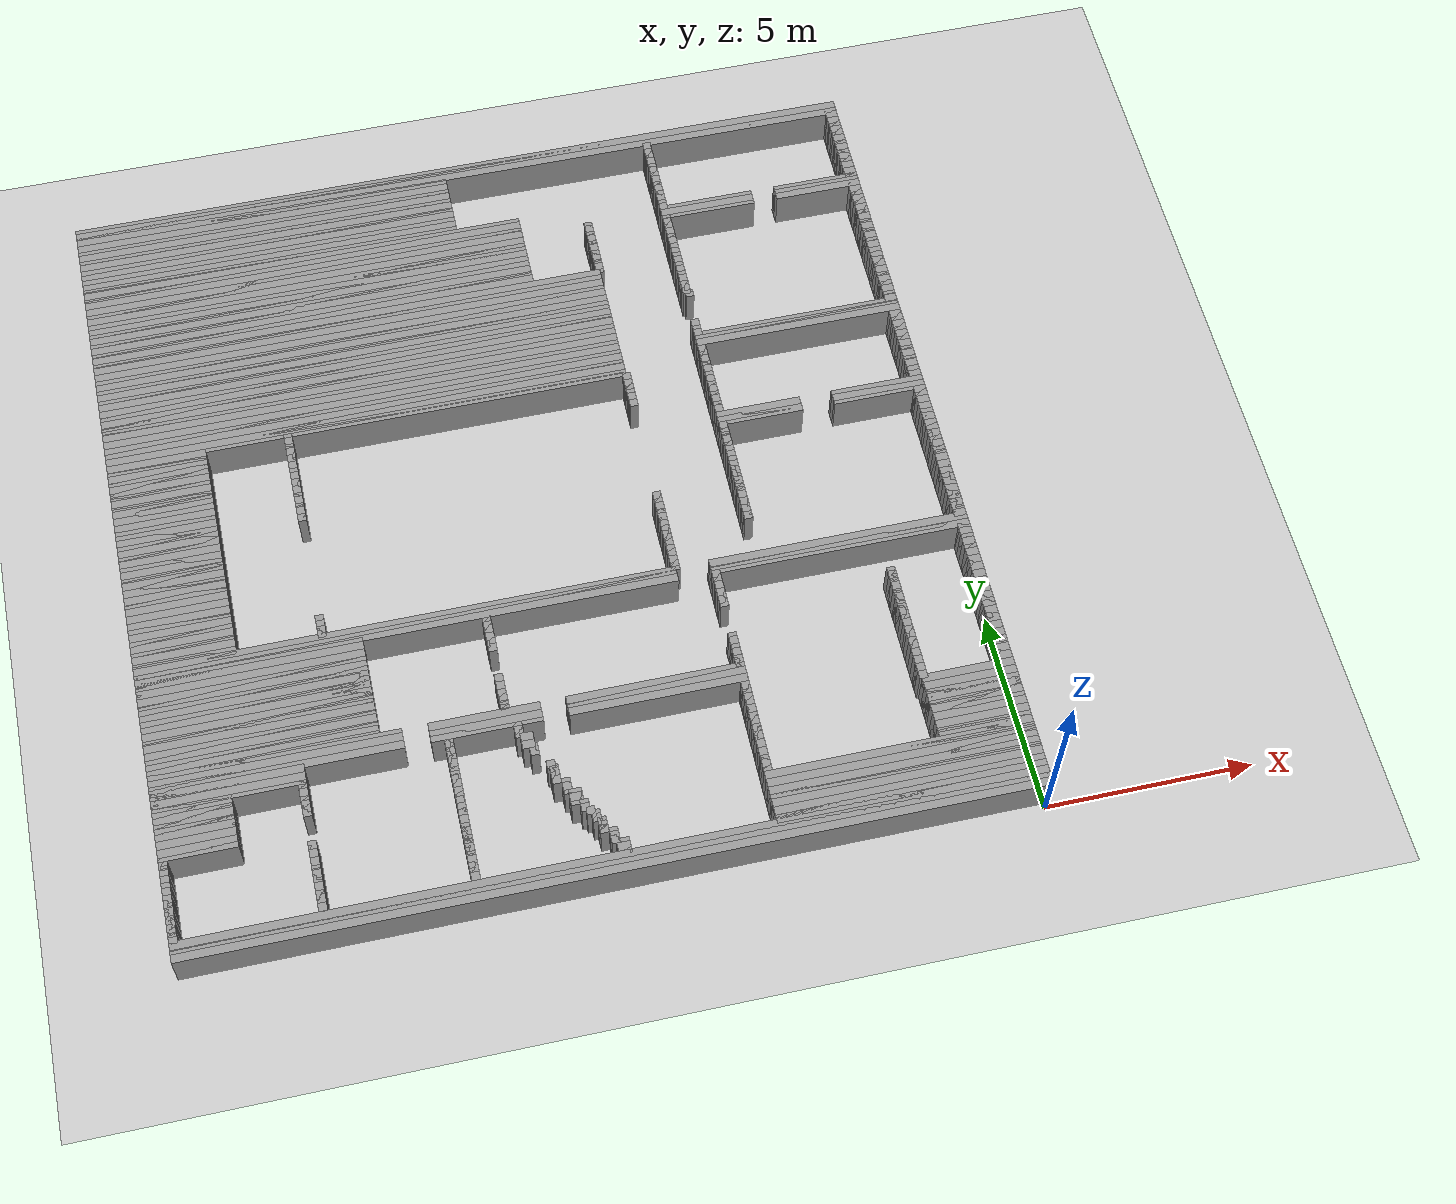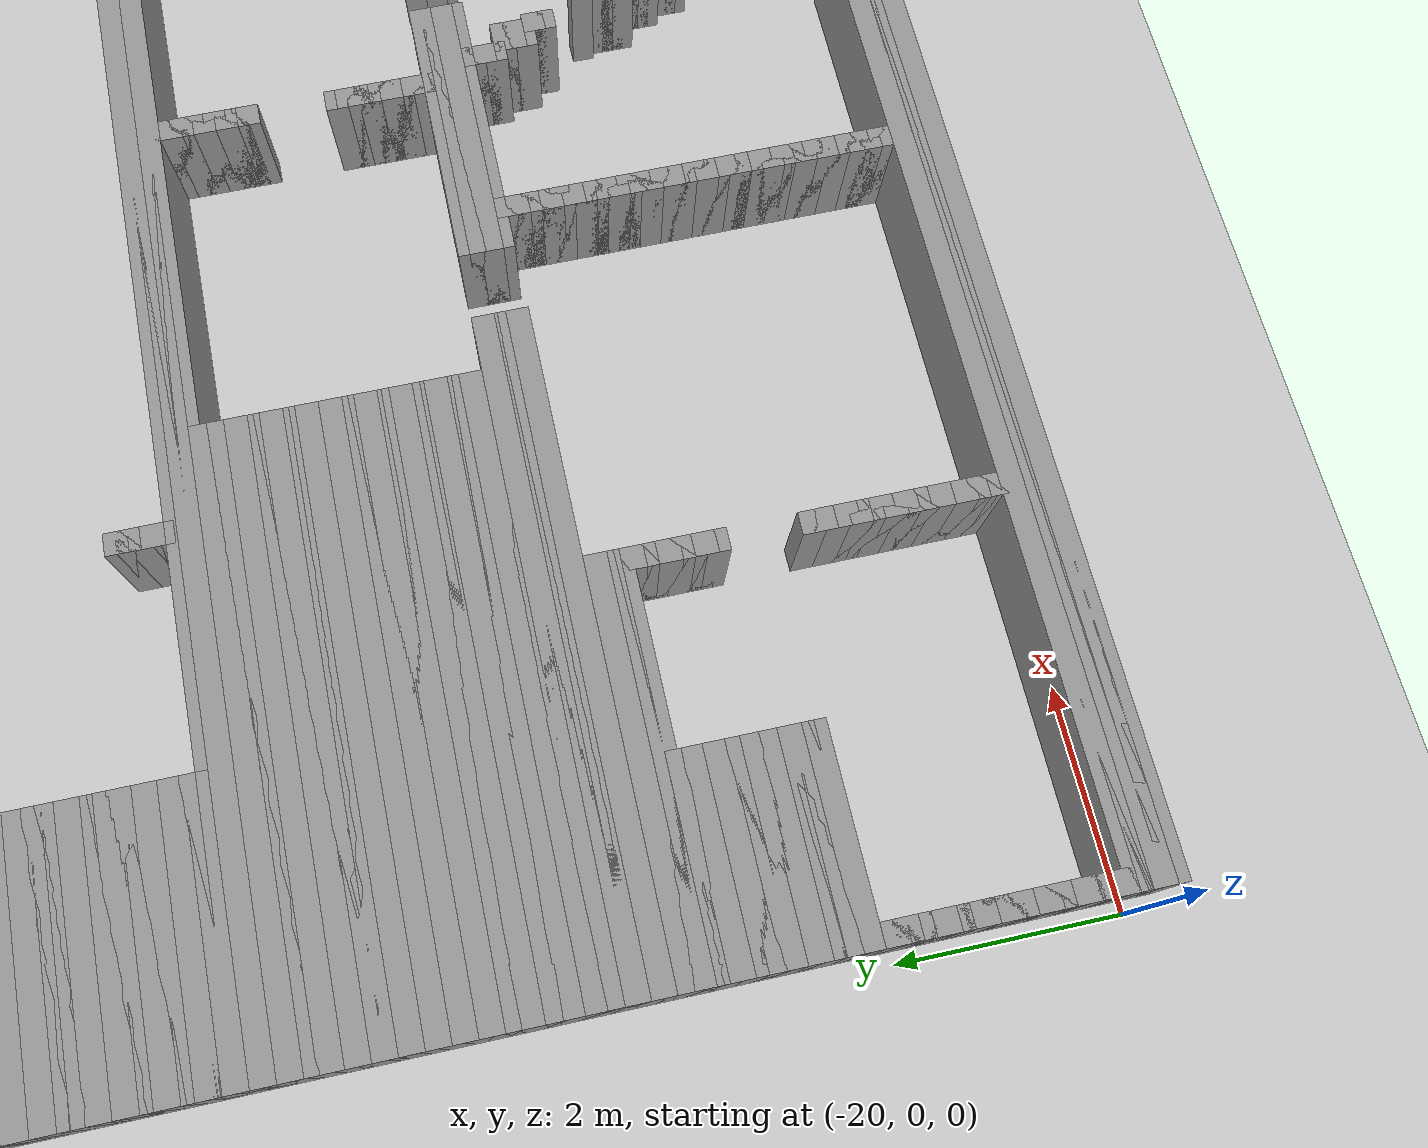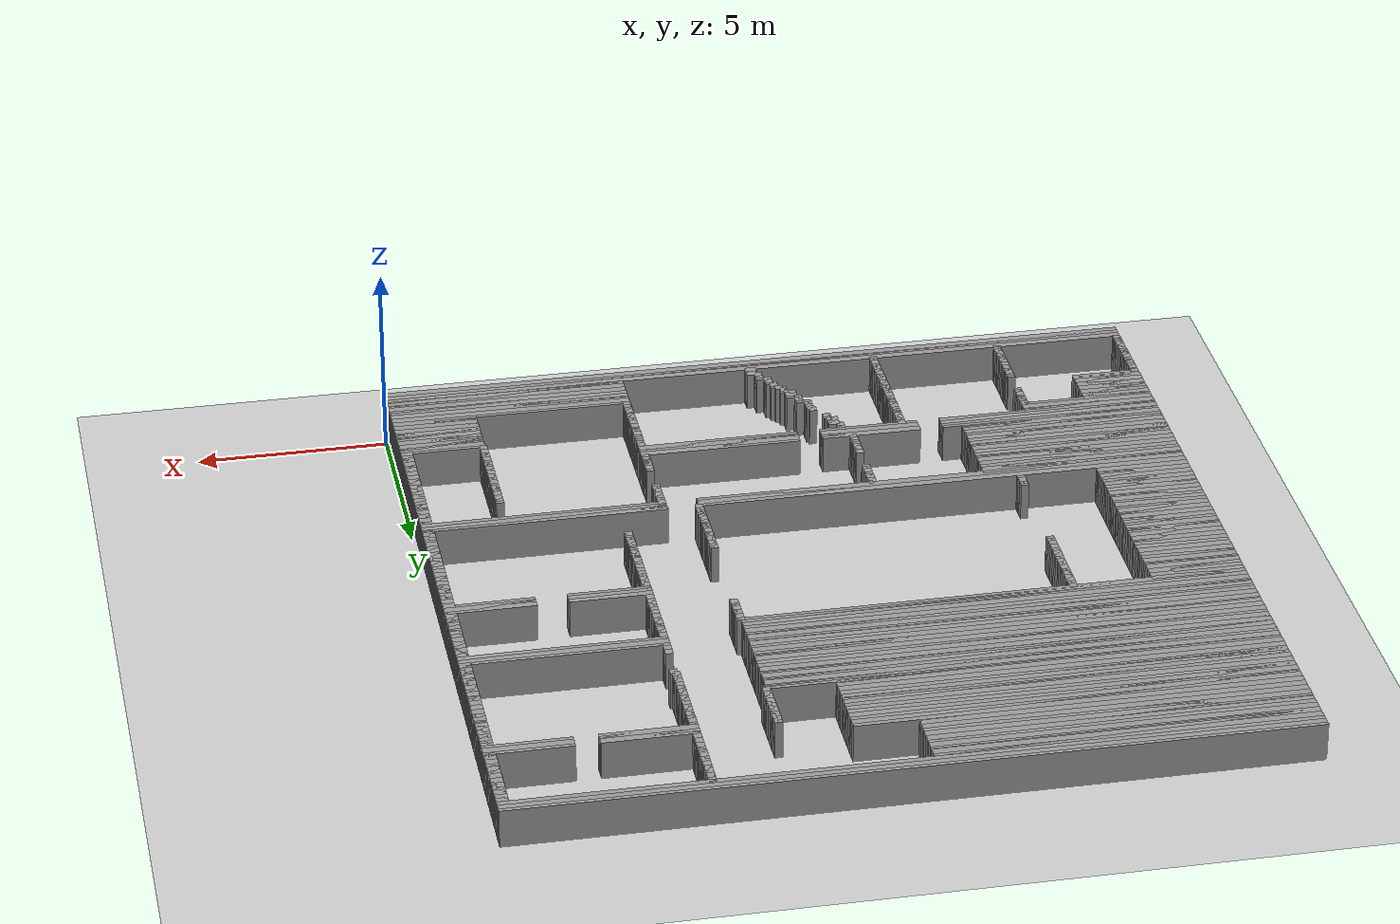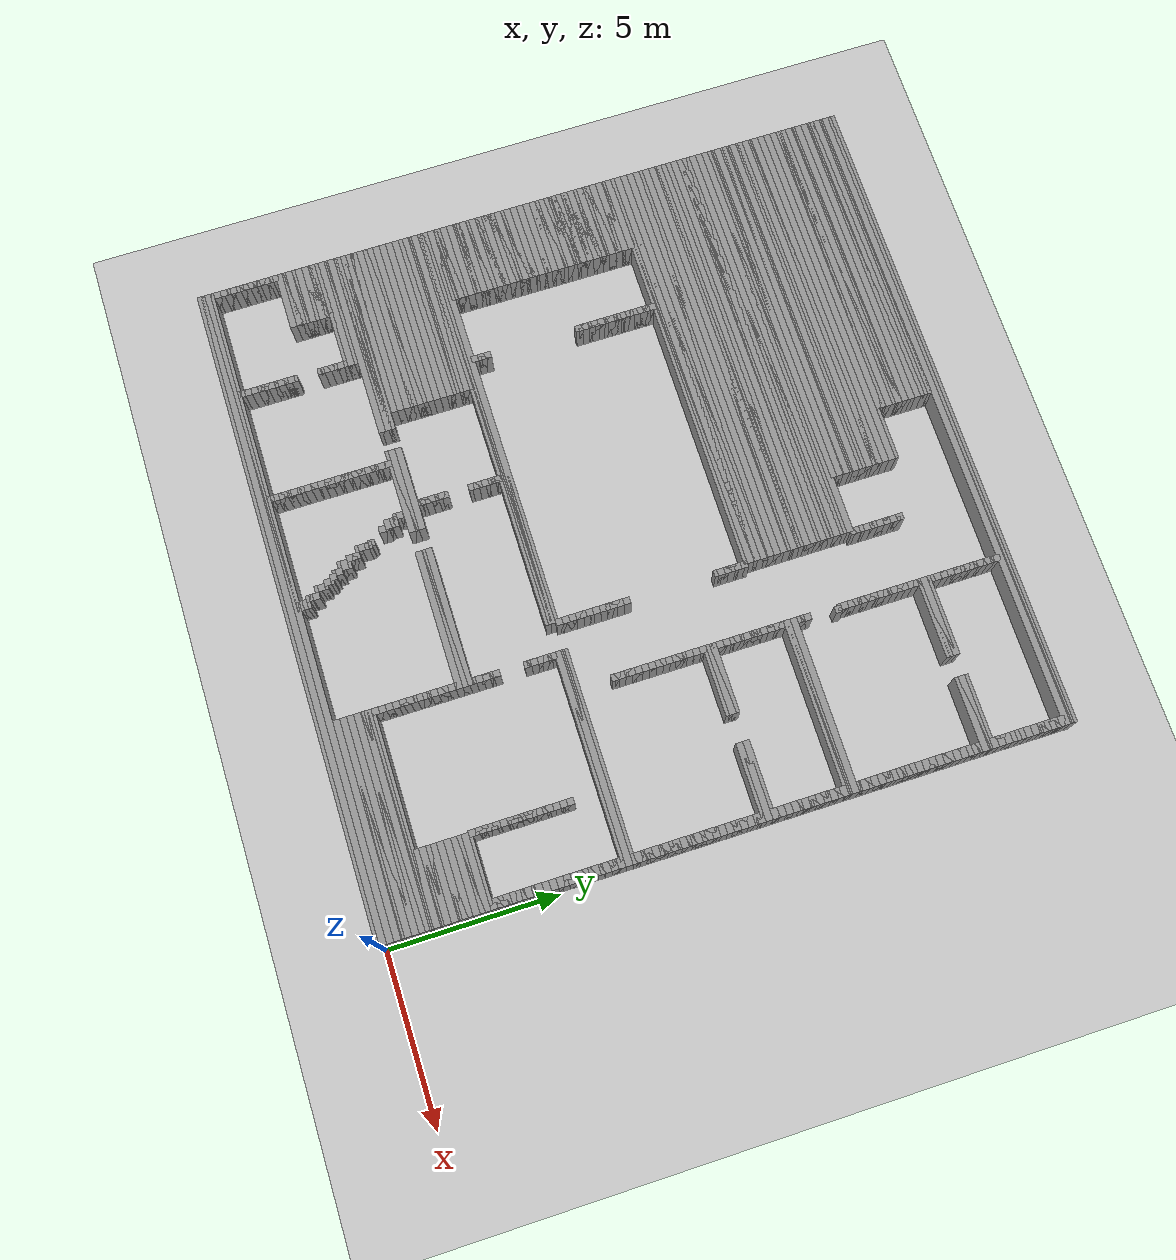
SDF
<?xml version='1.0' encoding='UTF-8'?>
<sdf version="1.6"><world name="GridMap"><include><uri>model://sun</uri></include><include><uri>model://ground_plane</uri></include><physics type="ode"><real_time_update_rate>1000.0</real_time_update_rate><max_step_size>0.001</max_step_size><real_time_factor>1</real_time_factor><ode><solver><type>quick</type><iters>150</iters><precon_iters>0</precon_iters><sor>1.4</sor><use_dynamic_moi_rescaling>1</use_dynamic_moi_rescaling></solver><constraints><cfm>0.00001</cfm><erp>0.2</erp><contact_max_correcting_vel>2000.000000</contact_max_correcting_vel><contact_surface_layer>0.01000</contact_surface_layer></constraints></ode></physics><model name="GridMap"><pose frame="">0 0 0 0 -0 0</pose><link name="Wall_(99.5,0.0)"><collision name="Wall_(99.5,0.0)_Collision"><geometry><box><size>19.900000000000002 0.2 1.0</size></box></geometry><pose frame="">-9.950000000000001 0.0 0.5 0 -0 0</pose></collision><visual name="Wall_(99.5,0.0)_Visual"><geometry><box><size>19.900000000000002 0.2 1.0</size></box></geometry><pose frame="">-9.950000000000001 0.0 0.5 0 -0 0</pose><material><script><uri>file://media/materials/scripts/gazebo.material</uri><name>Gazebo/Grey</name></script><ambient>1 1 1 1</ambient></material><meta><layer>0</layer></meta></visual><pose frame="">0 0 0.5 0 -0 0</pose></link><link name="Wall_(99.5,1.0)"><collision name="Wall_(99.5,1.0)_Collision"><geometry><box><size>19.900000000000002 0.2 1.0</size></box></geometry><pose frame="">-9.950000000000001 0.1 0.5 0 -0 0</pose></collision><visual name="Wall_(99.5,1.0)_Visual"><geometry><box><size>19.900000000000002 0.2 1.0</size></box></geometry><pose frame="">-9.950000000000001 0.1 0.5 0 -0 0</pose><material><script><uri>file://media/materials/scripts/gazebo.material</uri><name>Gazebo/Grey</name></script><ambient>1 1 1 1</ambient></material><meta><layer>0</layer></meta></visual><pose frame="">0 0 0.5 0 -0 0</pose></link><link name="Wall_(99.5,2.0)"><collision name="Wall_(99.5,2.0)_Collision"><geometry><box><size>19.900000000000002 0.2 1.0</size></box></geometry><pose frame="">-9.950000000000001 0.2 0.5 0 -0 0</pose></collision><visual name="Wall_(99.5,2.0)_Visual"><geometry><box><size>19.900000000000002 0.2 1.0</size></box></geometry><pose frame="">-9.950000000000001 0.2 0.5 0 -0 0</pose><material><script><uri>file://media/materials/scripts/gazebo.material</uri><name>Gazebo/Grey</name></script><ambient>1 1 1 1</ambient></material><meta><layer>0</layer></meta></visual><pose frame="">0 0 0.5 0 -0 0</pose></link><link name="Wall_(99.5,3.0)"><collision name="Wall_(99.5,3.0)_Collision"><geometry><box><size>19.900000000000002 0.2 1.0</size></box></geometry><pose frame="">-9.950000000000001 0.30000000000000004 0.5 0 -0 0</pose></collision><visual name="Wall_(99.5,3.0)_Visual"><geometry><box><size>19.900000000000002 0.2 1.0</size></box></geometry><pose frame="">-9.950000000000001 0.30000000000000004 0.5 0 -0 0</pose><material><script><uri>file://media/materials/scripts/gazebo.material</uri><name>Gazebo/Grey</name></script><ambient>1 1 1 1</ambient></material><meta><layer>0</layer></meta></visual><pose frame="">0 0 0.5 0 -0 0</pose></link><link name="Wall_(31.5,4.0)"><collision name="Wall_(31.5,4.0)_Collision"><geometry><box><size>6.300000000000001 0.2 1.0</size></box></geometry><pose frame="">-3.1500000000000004 0.4 0.5 0 -0 0</pose></collision><visual name="Wall_(31.5,4.0)_Visual"><geometry><box><size>6.300000000000001 0.2 1.0</size></box></geometry><pose frame="">-3.1500000000000004 0.4 0.5 0 -0 0</pose><material><script><uri>file://media/materials/scripts/gazebo.material</uri><name>Gazebo/Grey</name></script><ambient>1 1 1 1</ambient></material><meta><layer>0</layer></meta></visual><pose frame="">0 0 0.5 0 -0 0</pose></link><link name="Wall_(97.5,4.0)"><collision name="Wall_(97.5,4.0)_Collision"><geometry><box><size>0.30000000000000004 0.2 1.0</size></box></geometry><pose frame="">-9.75 0.4 0.5 0 -0 0</pose></collision><visual name="Wall_(97.5,4.0)_Visual"><geometry><box><size>0.30000000000000004 0.2 1.0</size></box></geometry><pose frame="">-9.75 0.4 0.5 0 -0 0</pose><material><script><uri>file://media/materials/scripts/gazebo.material</uri><name>Gazebo/Grey</name></script><ambient>1 1 1 1</ambient></material><meta><layer>0</layer></meta></visual><pose frame="">0 0 0.5 0 -0 0</pose></link><link name="Wall_(131.0,4.0)"><collision name="Wall_(131.0,4.0)_Collision"><geometry><box><size>0.2 0.2 1.0</size></box></geometry><pose frame="">-13.100000000000001 0.4 0.5 0 -0 0</pose></collision><visual name="Wall_(131.0,4.0)_Visual"><geometry><box><size>0.2 0.2 1.0</size></box></geometry><pose frame="">-13.100000000000001 0.4 0.5 0 -0 0</pose><material><script><uri>file://media/materials/scripts/gazebo.material</uri><name>Gazebo/Grey</name></script><ambient>1 1 1 1</ambient></material><meta><layer>0</layer></meta></visual><pose frame="">0 0 0.5 0 -0 0</pose></link><link name="Wall_(165.0,4.0)"><collision name="Wall_(165.0,4.0)_Collision"><geometry><box><size>0.2 0.2 1.0</size></box></geometry><pose frame="">-16.5 0.4 0.5 0 -0 0</pose></collision><visual name="Wall_(165.0,4.0)_Visual"><geometry><box><size>0.2 0.2 1.0</size></box></geometry><pose frame="">-16.5 0.4 0.5 0 -0 0</pose><material><script><uri>file://media/materials/scripts/gazebo.material</uri><name>Gazebo/Grey</name></script><ambient>1 1 1 1</ambient></material><meta><layer>0</layer></meta></visual><pose frame="">0 0 0.5 0 -0 0</pose></link><link name="Wall_(198.0,4.0)"><collision name="Wall_(198.0,4.0)_Collision"><geometry><box><size>0.2 0.2 1.0</size></box></geometry><pose frame="">-19.8 0.4 0.5 0 -0 0</pose></collision><visual name="Wall_(198.0,4.0)_Visual"><geometry><box><size>0.2 0.2 1.0</size></box></geometry><pose frame="">-19.8 0.4 0.5 0 -0 0</pose><material><script><uri>file://media/materials/scripts/gazebo.material</uri><name>Gazebo/Grey</name></script><ambient>1 1 1 1</ambient></material><meta><layer>0</layer></meta></visual><pose frame="">0 0 0.5 0 -0 0</pose></link><link name="Wall_(31.5,5.0)"><collision name="Wall_(31.5,5.0)_Collision"><geometry><box><size>6.300000000000001 0.2 1.0</size></box></geometry><pose frame="">-3.1500000000000004 0.5 0.5 0 -0 0</pose></collision><visual name="Wall_(31.5,5.0)_Visual"><geometry><box><size>6.300000000000001 0.2 1.0</size></box></geometry><pose frame="">-3.1500000000000004 0.5 0.5 0 -0 0</pose><material><script><uri>file://media/materials/scripts/gazebo.material</uri><name>Gazebo/Grey</name></script><ambient>1 1 1 1</ambient></material><meta><layer>0</layer></meta></visual><pose frame="">0 0 0.5 0 -0 0</pose></link><link name="Wall_(97.5,5.0)"><collision name="Wall_(97.5,5.0)_Collision"><geometry><box><size>0.30000000000000004 0.2 1.0</size></box></geometry><pose frame="">-9.75 0.5 0.5 0 -0 0</pose></collision><visual name="Wall_(97.5,5.0)_Visual"><geometry><box><size>0.30000000000000004 0.2 1.0</size></box></geometry><pose frame="">-9.75 0.5 0.5 0 -0 0</pose><material><script><uri>file://media/materials/scripts/gazebo.material</uri><name>Gazebo/Grey</name></script><ambient>1 1 1 1</ambient></material><meta><layer>0</layer></meta></visual><pose frame="">0 0 0.5 0 -0 0</pose></link><link name="Wall_(131.0,5.0)"><collision name="Wall_(131.0,5.0)_Collision"><geometry><box><size>0.2 0.2 1.0</size></box></geometry><pose frame="">-13.100000000000001 0.5 0.5 0 -0 0</pose></collision><visual name="Wall_(131.0,5.0)_Visual"><geometry><box><size>0.2 0.2 1.0</size></box></geometry><pose frame="">-13.100000000000001 0.5 0.5 0 -0 0</pose><material><script><uri>file://media/materials/scripts/gazebo.material</uri><name>Gazebo/Grey</name></script><ambient>1 1 1 1</ambient></material><meta><layer>0</layer></meta></visual><pose frame="">0 0 0.5 0 -0 0</pose></link><link name="Wall_(165.0,5.0)"><collision name="Wall_(165.0,5.0)_Collision"><geometry><box><size>0.2 0.2 1.0</size></box></geometry><pose frame="">-16.5 0.5 0.5 0 -0 0</pose></collision><visual name="Wall_(165.0,5.0)_Visual"><geometry><box><size>0.2 0.2 1.0</size></box></geometry><pose frame="">-16.5 0.5 0.5 0 -0 0</pose><material><script><uri>file://media/materials/scripts/gazebo.material</uri><name>Gazebo/Grey</name></script><ambient>1 1 1 1</ambient></material><meta><layer>0</layer></meta></visual><pose frame="">0 0 0.5 0 -0 0</pose></link><link name="Wall_(198.0,5.0)"><collision name="Wall_(198.0,5.0)_Collision"><geometry><box><size>0.2 0.2 1.0</size></box></geometry><pose frame="">-19.8 0.5 0.5 0 -0 0</pose></collision><visual name="Wall_(198.0,5.0)_Visual"><geometry><box><size>0.2 0.2 1.0</size></box></geometry><pose frame="">-19.8 0.5 0.5 0 -0 0</pose><material><script><uri>file://media/materials/scripts/gazebo.material</uri><name>Gazebo/Grey</name></script><ambient>1 1 1 1</ambient></material><meta><layer>0</layer></meta></visual><pose frame="">0 0 0.5 0 -0 0</pose></link><link name="Wall_(31.5,6.0)"><collision name="Wall_(31.5,6.0)_Collision"><geometry><box><size>6.300000000000001 0.2 1.0</size></box></geometry><pose frame="">-3.1500000000000004 0.6000000000000001 0.5 0 -0 0</pose></collision><visual name="Wall_(31.5,6.0)_Visual"><geometry><box><size>6.300000000000001 0.2 1.0</size></box></geometry><pose frame="">-3.1500000000000004 0.6000000000000001 0.5 0 -0 0</pose><material><script><uri>file://media/materials/scripts/gazebo.material</uri><name>Gazebo/Grey</name></script><ambient>1 1 1 1</ambient></material><meta><layer>0</layer></meta></visual><pose frame="">0 0 0.5 0 -0 0</pose></link><link name="Wall_(97.5,6.0)"><collision name="Wall_(97.5,6.0)_Collision"><geometry><box><size>0.30000000000000004 0.2 1.0</size></box></geometry><pose frame="">-9.75 0.6000000000000001 0.5 0 -0 0</pose></collision><visual name="Wall_(97.5,6.0)_Visual"><geometry><box><size>0.30000000000000004 0.2 1.0</size></box></geometry><pose frame="">-9.75 0.6000000000000001 0.5 0 -0 0</pose><material><script><uri>file://media/materials/scripts/gazebo.material</uri><name>Gazebo/Grey</name></script><ambient>1 1 1 1</ambient></material><meta><layer>0</layer></meta></visual><pose frame="">0 0 0.5 0 -0 0</pose></link><link name="Wall_(131.0,6.0)"><collision name="Wall_(131.0,6.0)_Collision"><geometry><box><size>0.2 0.2 1.0</size></box></geometry><pose frame="">-13.100000000000001 0.6000000000000001 0.5 0 -0 0</pose></collision><visual name="Wall_(131.0,6.0)_Visual"><geometry><box><size>0.2 0.2 1.0</size></box></geometry><pose frame="">-13.100000000000001 0.6000000000000001 0.5 0 -0 0</pose><material><script><uri>file://media/materials/scripts/gazebo.material</uri><name>Gazebo/Grey</name></script><ambient>1 1 1 1</ambient></material><meta><layer>0</layer></meta></visual><pose frame="">0 0 0.5 0 -0 0</pose></link><link name="Wall_(165.0,6.0)"><collision name="Wall_(165.0,6.0)_Collision"><geometry><box><size>0.2 0.2 1.0</size></box></geometry><pose frame="">-16.5 0.6000000000000001 0.5 0 -0 0</pose></collision><visual name="Wall_(165.0,6.0)_Visual"><geometry><box><size>0.2 0.2 1.0</size></box></geometry><pose frame="">-16.5 0.6000000000000001 0.5 0 -0 0</pose><material><script><uri>file://media/materials/scripts/gazebo.material</uri><name>Gazebo/Grey</name></script><ambient>1 1 1 1</ambient></material><meta><layer>0</layer></meta></visual><pose frame="">0 0 0.5 0 -0 0</pose></link><link name="Wall_(198.0,6.0)"><collision name="Wall_(198.0,6.0)_Collision"><geometry><box><size>0.2 0.2 1.0</size></box></geometry><pose frame="">-19.8 0.6000000000000001 0.5 0 -0 0</pose></collision><visual name="Wall_(198.0,6.0)_Visual"><geometry><box><size>0.2 0.2 1.0</size></box></geometry><pose frame="">-19.8 0.6000000000000001 0.5 0 -0 0</pose><material><script><uri>file://media/materials/scripts/gazebo.material</uri><name>Gazebo/Grey</name></script><ambient>1 1 1 1</ambient></material><meta><layer>0</layer></meta></visual><pose frame="">0 0 0.5 0 -0 0</pose></link><link name="Wall_(31.5,7.0)"><collision name="Wall_(31.5,7.0)_Collision"><geometry><box><size>6.300000000000001 0.2 1.0</size></box></geometry><pose frame="">-3.1500000000000004 0.7000000000000001 0.5 0 -0 0</pose></collision><visual name="Wall_(31.5,7.0)_Visual"><geometry><box><size>6.300000000000001 0.2 1.0</size></box></geometry><pose frame="">-3.1500000000000004 0.7000000000000001 0.5 0 -0 0</pose><material><script><uri>file://media/materials/scripts/gazebo.material</uri><name>Gazebo/Grey</name></script><ambient>1 1 1 1</ambient></material><meta><layer>0</layer></meta></visual><pose frame="">0 0 0.5 0 -0 0</pose></link><link name="Wall_(99.0,7.0)"><collision name="Wall_(99.0,7.0)_Collision"><geometry><box><size>0.2 0.2 1.0</size></box></geometry><pose frame="">-9.9 0.7000000000000001 0.5 0 -0 0</pose></collision><visual name="Wall_(99.0,7.0)_Visual"><geometry><box><size>0.2 0.2 1.0</size></box></geometry><pose frame="">-9.9 0.7000000000000001 0.5 0 -0 0</pose><material><script><uri>file://media/materials/scripts/gazebo.material</uri><name>Gazebo/Grey</name></script><ambient>1 1 1 1</ambient></material><meta><layer>0</layer></meta></visual><pose frame="">0 0 0.5 0 -0 0</pose></link><link name="Wall_(131.0,7.0)"><collision name="Wall_(131.0,7.0)_Collision"><geometry><box><size>0.2 0.2 1.0</size></box></geometry><pose frame="">-13.100000000000001 0.7000000000000001 0.5 0 -0 0</pose></collision><visual name="Wall_(131.0,7.0)_Visual"><geometry><box><size>0.2 0.2 1.0</size></box></geometry><pose frame="">-13.100000000000001 0.7000000000000001 0.5 0 -0 0</pose><material><script><uri>file://media/materials/scripts/gazebo.material</uri><name>Gazebo/Grey</name></script><ambient>1 1 1 1</ambient></material><meta><layer>0</layer></meta></visual><pose frame="">0 0 0.5 0 -0 0</pose></link><link name="Wall_(165.0,7.0)"><collision name="Wall_(165.0,7.0)_Collision"><geometry><box><size>0.2 0.2 1.0</size></box></geometry><pose frame="">-16.5 0.7000000000000001 0.5 0 -0 0</pose></collision><visual name="Wall_(165.0,7.0)_Visual"><geometry><box><size>0.2 0.2 1.0</size></box></geometry><pose frame="">-16.5 0.7000000000000001 0.5 0 -0 0</pose><material><script><uri>file://media/materials/scripts/gazebo.material</uri><name>Gazebo/Grey</name></script><ambient>1 1 1 1</ambient></material><meta><layer>0</layer></meta></visual><pose frame="">0 0 0.5 0 -0 0</pose></link><link name="Wall_(198.0,7.0)"><collision name="Wall_(198.0,7.0)_Collision"><geometry><box><size>0.2 0.2 1.0</size></box></geometry><pose frame="">-19.8 0.7000000000000001 0.5 0 -0 0</pose></collision><visual name="Wall_(198.0,7.0)_Visual"><geometry><box><size>0.2 0.2 1.0</size></box></geometry><pose frame="">-19.8 0.7000000000000001 0.5 0 -0 0</pose><material><script><uri>file://media/materials/scripts/gazebo.material</uri><name>Gazebo/Grey</name></script><ambient>1 1 1 1</ambient></material><meta><layer>0</layer></meta></visual><pose frame="">0 0 0.5 0 -0 0</pose></link><link name="Wall_(31.5,8.0)"><collision name="Wall_(31.5,8.0)_Collision"><geometry><box><size>6.300000000000001 0.2 1.0</size></box></geometry><pose frame="">-3.1500000000000004 0.8 0.5 0 -0 0</pose></collision><visual name="Wall_(31.5,8.0)_Visual"><geometry><box><size>6.300000000000001 0.2 1.0</size></box></geometry><pose frame="">-3.1500000000000004 0.8 0.5 0 -0 0</pose><material><script><uri>file://media/materials/scripts/gazebo.material</uri><name>Gazebo/Grey</name></script><ambient>1 1 1 1</ambient></material><meta><layer>0</layer></meta></visual><pose frame="">0 0 0.5 0 -0 0</pose></link><link name="Wall_(99.0,8.0)"><collision name="Wall_(99.0,8.0)_Collision"><geometry><box><size>0.2 0.2 1.0</size></box></geometry><pose frame="">-9.9 0.8 0.5 0 -0 0</pose></collision><visual name="Wall_(99.0,8.0)_Visual"><geometry><box><size>0.2 0.2 1.0</size></box></geometry><pose frame="">-9.9 0.8 0.5 0 -0 0</pose><material><script><uri>file://media/materials/scripts/gazebo.material</uri><name>Gazebo/Grey</name></script><ambient>1 1 1 1</ambient></material><meta><layer>0</layer></meta></visual><pose frame="">0 0 0.5 0 -0 0</pose></link><link name="Wall_(131.0,8.0)"><collision name="Wall_(131.0,8.0)_Collision"><geometry><box><size>0.2 0.2 1.0</size></box></geometry><pose frame="">-13.100000000000001 0.8 0.5 0 -0 0</pose></collision><visual name="Wall_(131.0,8.0)_Visual"><geometry><box><size>0.2 0.2 1.0</size></box></geometry><pose frame="">-13.100000000000001 0.8 0.5 0 -0 0</pose><material><script><uri>file://media/materials/scripts/gazebo.material</uri><name>Gazebo/Grey</name></script><ambient>1 1 1 1</ambient></material><meta><layer>0</layer></meta></visual><pose frame="">0 0 0.5 0 -0 0</pose></link><link name="Wall_(165.0,8.0)"><collision name="Wall_(165.0,8.0)_Collision"><geometry><box><size>0.2 0.2 1.0</size></box></geometry><pose frame="">-16.5 0.8 0.5 0 -0 0</pose></collision><visual name="Wall_(165.0,8.0)_Visual"><geometry><box><size>0.2 0.2 1.0</size></box></geometry><pose frame="">-16.5 0.8 0.5 0 -0 0</pose><material><script><uri>file://media/materials/scripts/gazebo.material</uri><name>Gazebo/Grey</name></script><ambient>1 1 1 1</ambient></material><meta><layer>0</layer></meta></visual><pose frame="">0 0 0.5 0 -0 0</pose></link><link name="Wall_(198.0,8.0)"><collision name="Wall_(198.0,8.0)_Collision"><geometry><box><size>0.2 0.2 1.0</size></box></geometry><pose frame="">-19.8 0.8 0.5 0 -0 0</pose></collision><visual name="Wall_(198.0,8.0)_Visual"><geometry><box><size>0.2 0.2 1.0</size></box></geometry><pose frame="">-19.8 0.8 0.5 0 -0 0</pose><material><script><uri>file://media/materials/scripts/gazebo.material</uri><name>Gazebo/Grey</name></script><ambient>1 1 1 1</ambient></material><meta><layer>0</layer></meta></visual><pose frame="">0 0 0.5 0 -0 0</pose></link><link name="Wall_(31.5,9.0)"><collision name="Wall_(31.5,9.0)_Collision"><geometry><box><size>6.300000000000001 0.2 1.0</size></box></geometry><pose frame="">-3.1500000000000004 0.9 0.5 0 -0 0</pose></collision><visual name="Wall_(31.5,9.0)_Visual"><geometry><box><size>6.300000000000001 0.2 1.0</size></box></geometry><pose frame="">-3.1500000000000004 0.9 0.5 0 -0 0</pose><material><script><uri>file://media/materials/scripts/gazebo.material</uri><name>Gazebo/Grey</name></script><ambient>1 1 1 1</ambient></material><meta><layer>0</layer></meta></visual><pose frame="">0 0 0.5 0 -0 0</pose></link><link name="Wall_(99.0,9.0)"><collision name="Wall_(99.0,9.0)_Collision"><geometry><box><size>0.2 0.2 1.0</size></box></geometry><pose frame="">-9.9 0.9 0.5 0 -0 0</pose></collision><visual name="Wall_(99.0,9.0)_Visual"><geometry><box><size>0.2 0.2 1.0</size></box></geometry><pose frame="">-9.9 0.9 0.5 0 -0 0</pose><material><script><uri>file://media/materials/scripts/gazebo.material</uri><name>Gazebo/Grey</name></script><ambient>1 1 1 1</ambient></material><meta><layer>0</layer></meta></visual><pose frame="">0 0 0.5 0 -0 0</pose></link><link name="Wall_(131.0,9.0)"><collision name="Wall_(131.0,9.0)_Collision"><geometry><box><size>0.2 0.2 1.0</size></box></geometry><pose frame="">-13.100000000000001 0.9 0.5 0 -0 0</pose></collision><visual name="Wall_(131.0,9.0)_Visual"><geometry><box><size>0.2 0.2 1.0</size></box></geometry><pose frame="">-13.100000000000001 0.9 0.5 0 -0 0</pose><material><script><uri>file://media/materials/scripts/gazebo.material</uri><name>Gazebo/Grey</name></script><ambient>1 1 1 1</ambient></material><meta><layer>0</layer></meta></visual><pose frame="">0 0 0.5 0 -0 0</pose></link><link name="Wall_(165.0,9.0)"><collision name="Wall_(165.0,9.0)_Collision"><geometry><box><size>0.2 0.2 1.0</size></box></geometry><pose frame="">-16.5 0.9 0.5 0 -0 0</pose></collision><visual name="Wall_(165.0,9.0)_Visual"><geometry><box><size>0.2 0.2 1.0</size></box></geometry><pose frame="">-16.5 0.9 0.5 0 -0 0</pose><material><script><uri>file://media/materials/scripts/gazebo.material</uri><name>Gazebo/Grey</name></script><ambient>1 1 1 1</ambient></material><meta><layer>0</layer></meta></visual><pose frame="">0 0 0.5 0 -0 0</pose></link><link name="Wall_(198.0,9.0)"><collision name="Wall_(198.0,9.0)_Collision"><geometry><box><size>0.2 0.2 1.0</size></box></geometry><pose frame="">-19.8 0.9 0.5 0 -0 0</pose></collision><visual name="Wall_(198.0,9.0)_Visual"><geometry><box><size>0.2 0.2 1.0</size></box></geometry><pose frame="">-19.8 0.9 0.5 0 -0 0</pose><material><script><uri>file://media/materials/scripts/gazebo.material</uri><name>Gazebo/Grey</name></script><ambient>1 1 1 1</ambient></material><meta><layer>0</layer></meta></visual><pose frame="">0 0 0.5 0 -0 0</pose></link><link name="Wall_(31.5,10.0)"><collision name="Wall_(31.5,10.0)_Collision"><geometry><box><size>6.300000000000001 0.2 1.0</size></box></geometry><pose frame="">-3.1500000000000004 1.0 0.5 0 -0 0</pose></collision><visual name="Wall_(31.5,10.0)_Visual"><geometry><box><size>6.300000000000001 0.2 1.0</size></box></geometry><pose frame="">-3.1500000000000004 1.0 0.5 0 -0 0</pose><material><script><uri>file://media/materials/scripts/gazebo.material</uri><name>Gazebo/Grey</name></script><ambient>1 1 1 1</ambient></material><meta><layer>0</layer></meta></visual><pose frame="">0 0 0.5 0 -0 0</pose></link><link name="Wall_(101.0,10.0)"><collision name="Wall_(101.0,10.0)_Collision"><geometry><box><size>0.2 0.2 1.0</size></box></geometry><pose frame="">-10.100000000000001 1.0 0.5 0 -0 0</pose></collision><visual name="Wall_(101.0,10.0)_Visual"><geometry><box><size>0.2 0.2 1.0</size></box></geometry><pose frame="">-10.100000000000001 1.0 0.5 0 -0 0</pose><material><script><uri>file://media/materials/scripts/gazebo.material</uri><name>Gazebo/Grey</name></script><ambient>1 1 1 1</ambient></material><meta><layer>0</layer></meta></visual><pose frame="">0 0 0.5 0 -0 0</pose></link><link name="Wall_(131.0,10.0)"><collision name="Wall_(131.0,10.0)_Collision"><geometry><box><size>0.2 0.2 1.0</size></box></geometry><pose frame="">-13.100000000000001 1.0 0.5 0 -0 0</pose></collision><visual name="Wall_(131.0,10.0)_Visual"><geometry><box><size>0.2 0.2 1.0</size></box></geometry><pose frame="">-13.100000000000001 1.0 0.5 0 -0 0</pose><material><script><uri>file://media/materials/scripts/gazebo.material</uri><name>Gazebo/Grey</name></script><ambient>1 1 1 1</ambient></material><meta><layer>0</layer></meta></visual><pose frame="">0 0 0.5 0 -0 0</pose></link><link name="Wall_(165.0,10.0)"><collision name="Wall_(165.0,10.0)_Collision"><geometry><box><size>0.2 0.2 1.0</size></box></geometry><pose frame="">-16.5 1.0 0.5 0 -0 0</pose></collision><visual name="Wall_(165.0,10.0)_Visual"><geometry><box><size>0.2 0.2 1.0</size></box></geometry><pose frame="">-16.5 1.0 0.5 0 -0 0</pose><material><script><uri>file://media/materials/scripts/gazebo.material</uri><name>Gazebo/Grey</name></script><ambient>1 1 1 1</ambient></material><meta><layer>0</layer></meta></visual><pose frame="">0 0 0.5 0 -0 0</pose></link><link name="Wall_(198.0,10.0)"><collision name="Wall_(198.0,10.0)_Collision"><geometry><box><size>0.2 0.2 1.0</size></box></geometry><pose frame="">-19.8 1.0 0.5 0 -0 0</pose></collision><visual name="Wall_(198.0,10.0)_Visual"><geometry><box><size>0.2 0.2 1.0</size></box></geometry><pose frame="">-19.8 1.0 0.5 0 -0 0</pose><material><script><uri>file://media/materials/scripts/gazebo.material</uri><name>Gazebo/Grey</name></script><ambient>1 1 1 1</ambient></material><meta><layer>0</layer></meta></visual><pose frame="">0 0 0.5 0 -0 0</pose></link><link name="Wall_(31.5,11.0)"><collision name="Wall_(31.5,11.0)_Collision"><geometry><box><size>6.300000000000001 0.2 1.0</size></box></geometry><pose frame="">-3.1500000000000004 1.1 0.5 0 -0 0</pose></collision><visual name="Wall_(31.5,11.0)_Visual"><geometry><box><size>6.300000000000001 0.2 1.0</size></box></geometry><pose frame="">-3.1500000000000004 1.1 0.5 0 -0 0</pose><material><script><uri>file://media/materials/scripts/gazebo.material</uri><name>Gazebo/Grey</name></script><ambient>1 1 1 1</ambient></material><meta><layer>0</layer></meta></visual><pose frame="">0 0 0.5 0 -0 0</pose></link><link name="Wall_(101.0,11.0)"><collision name="Wall_(101.0,11.0)_Collision"><geometry><box><size>0.2 0.2 1.0</size></box></geometry><pose frame="">-10.100000000000001 1.1 0.5 0 -0 0</pose></collision><visual name="Wall_(101.0,11.0)_Visual"><geometry><box><size>0.2 0.2 1.0</size></box></geometry><pose frame="">-10.100000000000001 1.1 0.5 0 -0 0</pose><material><script><uri>file://media/materials/scripts/gazebo.material</uri><name>Gazebo/Grey</name></script><ambient>1 1 1 1</ambient></material><meta><layer>0</layer></meta></visual><pose frame="">0 0 0.5 0 -0 0</pose></link><link name="Wall_(131.0,11.0)"><collision name="Wall_(131.0,11.0)_Collision"><geometry><box><size>0.2 0.2 1.0</size></box></geometry><pose frame="">-13.100000000000001 1.1 0.5 0 -0 0</pose></collision><visual name="Wall_(131.0,11.0)_Visual"><geometry><box><size>0.2 0.2 1.0</size></box></geometry><pose frame="">-13.100000000000001 1.1 0.5 0 -0 0</pose><material><script><uri>file://media/materials/scripts/gazebo.material</uri><name>Gazebo/Grey</name></script><ambient>1 1 1 1</ambient></material><meta><layer>0</layer></meta></visual><pose frame="">0 0 0.5 0 -0 0</pose></link><link name="Wall_(165.0,11.0)"><collision name="Wall_(165.0,11.0)_Collision"><geometry><box><size>0.2 0.2 1.0</size></box></geometry><pose frame="">-16.5 1.1 0.5 0 -0 0</pose></collision><visual name="Wall_(165.0,11.0)_Visual"><geometry><box><size>0.2 0.2 1.0</size></box></geometry><pose frame="">-16.5 1.1 0.5 0 -0 0</pose><material><script><uri>file://media/materials/scripts/gazebo.material</uri><name>Gazebo/Grey</name></script><ambient>1 1 1 1</ambient></material><meta><layer>0</layer></meta></visual><pose frame="">0 0 0.5 0 -0 0</pose></link><link name="Wall_(198.0,11.0)"><collision name="Wall_(198.0,11.0)_Collision"><geometry><box><size>0.2 0.2 1.0</size></box></geometry><pose frame="">-19.8 1.1 0.5 0 -0 0</pose></collision><visual name="Wall_(198.0,11.0)_Visual"><geometry><box><size>0.2 0.2 1.0</size></box></geometry><pose frame="">-19.8 1.1 0.5 0 -0 0</pose><material><script><uri>file://media/materials/scripts/gazebo.material</uri><name>Gazebo/Grey</name></script><ambient>1 1 1 1</ambient></material><meta><layer>0</layer></meta></visual><pose frame="">0 0 0.5 0 -0 0</pose></link><link name="Wall_(31.5,12.0)"><collision name="Wall_(31.5,12.0)_Collision"><geometry><box><size>6.300000000000001 0.2 1.0</size></box></geometry><pose frame="">-3.1500000000000004 1.2000000000000002 0.5 0 -0 0</pose></collision><visual name="Wall_(31.5,12.0)_Visual"><geometry><box><size>6.300000000000001 0.2 1.0</size></box></geometry><pose frame="">-3.1500000000000004 1.2000000000000002 0.5 0 -0 0</pose><material><script><uri>file://media/materials/scripts/gazebo.material</uri><name>Gazebo/Grey</name></script><ambient>1 1 1 1</ambient></material><meta><layer>0</layer></meta></visual><pose frame="">0 0 0.5 0 -0 0</pose></link><link name="Wall_(101.0,12.0)"><collision name="Wall_(101.0,12.0)_Collision"><geometry><box><size>0.2 0.2 1.0</size></box></geometry><pose frame="">-10.100000000000001 1.2000000000000002 0.5 0 -0 0</pose></collision><visual name="Wall_(101.0,12.0)_Visual"><geometry><box><size>0.2 0.2 1.0</size></box></geometry><pose frame="">-10.100000000000001 1.2000000000000002 0.5 0 -0 0</pose><material><script><uri>file://media/materials/scripts/gazebo.material</uri><name>Gazebo/Grey</name></script><ambient>1 1 1 1</ambient></material><meta><layer>0</layer></meta></visual><pose frame="">0 0 0.5 0 -0 0</pose></link><link name="Wall_(131.0,12.0)"><collision name="Wall_(131.0,12.0)_Collision"><geometry><box><size>0.2 0.2 1.0</size></box></geometry><pose frame="">-13.100000000000001 1.2000000000000002 0.5 0 -0 0</pose></collision><visual name="Wall_(131.0,12.0)_Visual"><geometry><box><size>0.2 0.2 1.0</size></box></geometry><pose frame="">-13.100000000000001 1.2000000000000002 0.5 0 -0 0</pose><material><script><uri>file://media/materials/scripts/gazebo.material</uri><name>Gazebo/Grey</name></script><ambient>1 1 1 1</ambient></material><meta><layer>0</layer></meta></visual><pose frame="">0 0 0.5 0 -0 0</pose></link><link name="Wall_(165.0,12.0)"><collision name="Wall_(165.0,12.0)_Collision"><geometry><box><size>0.2 0.2 1.0</size></box></geometry><pose frame="">-16.5 1.2000000000000002 0.5 0 -0 0</pose></collision><visual name="Wall_(165.0,12.0)_Visual"><geometry><box><size>0.2 0.2 1.0</size></box></geometry><pose frame="">-16.5 1.2000000000000002 0.5 0 -0 0</pose><material><script><uri>file://media/materials/scripts/gazebo.material</uri><name>Gazebo/Grey</name></script><ambient>1 1 1 1</ambient></material><meta><layer>0</layer></meta></visual><pose frame="">0 0 0.5 0 -0 0</pose></link><link name="Wall_(198.0,12.0)"><collision name="Wall_(198.0,12.0)_Collision"><geometry><box><size>0.2 0.2 1.0</size></box></geometry><pose frame="">-19.8 1.2000000000000002 0.5 0 -0 0</pose></collision><visual name="Wall_(198.0,12.0)_Visual"><geometry><box><size>0.2 0.2 1.0</size></box></geometry><pose frame="">-19.8 1.2000000000000002 0.5 0 -0 0</pose><material><script><uri>file://media/materials/scripts/gazebo.material</uri><name>Gazebo/Grey</name></script><ambient>1 1 1 1</ambient></material><meta><layer>0</layer></meta></visual><pose frame="">0 0 0.5 0 -0 0</pose></link><link name="Wall_(31.5,13.0)"><collision name="Wall_(31.5,13.0)_Collision"><geometry><box><size>6.300000000000001 0.2 1.0</size></box></geometry><pose frame="">-3.1500000000000004 1.3 0.5 0 -0 0</pose></collision><visual name="Wall_(31.5,13.0)_Visual"><geometry><box><size>6.300000000000001 0.2 1.0</size></box></geometry><pose frame="">-3.1500000000000004 1.3 0.5 0 -0 0</pose><material><script><uri>file://media/materials/scripts/gazebo.material</uri><name>Gazebo/Grey</name></script><ambient>1 1 1 1</ambient></material><meta><layer>0</layer></meta></visual><pose frame="">0 0 0.5 0 -0 0</pose></link><link name="Wall_(102.0,13.0)"><collision name="Wall_(102.0,13.0)_Collision"><geometry><box><size>0.2 0.2 1.0</size></box></geometry><pose frame="">-10.200000000000001 1.3 0.5 0 -0 0</pose></collision><visual name="Wall_(102.0,13.0)_Visual"><geometry><box><size>0.2 0.2 1.0</size></box></geometry><pose frame="">-10.200000000000001 1.3 0.5 0 -0 0</pose><material><script><uri>file://media/materials/scripts/gazebo.material</uri><name>Gazebo/Grey</name></script><ambient>1 1 1 1</ambient></material><meta><layer>0</layer></meta></visual><pose frame="">0 0 0.5 0 -0 0</pose></link><link name="Wall_(131.0,13.0)"><collision name="Wall_(131.0,13.0)_Collision"><geometry><box><size>0.2 0.2 1.0</size></box></geometry><pose frame="">-13.100000000000001 1.3 0.5 0 -0 0</pose></collision><visual name="Wall_(131.0,13.0)_Visual"><geometry><box><size>0.2 0.2 1.0</size></box></geometry><pose frame="">-13.100000000000001 1.3 0.5 0 -0 0</pose><material><script><uri>file://media/materials/scripts/gazebo.material</uri><name>Gazebo/Grey</name></script><ambient>1 1 1 1</ambient></material><meta><layer>0</layer></meta></visual><pose frame="">0 0 0.5 0 -0 0</pose></link><link name="Wall_(165.0,13.0)"><collision name="Wall_(165.0,13.0)_Collision"><geometry><box><size>0.2 0.2 1.0</size></box></geometry><pose frame="">-16.5 1.3 0.5 0 -0 0</pose></collision><visual name="Wall_(165.0,13.0)_Visual"><geometry><box><size>0.2 0.2 1.0</size></box></geometry><pose frame="">-16.5 1.3 0.5 0 -0 0</pose><material><script><uri>file://media/materials/scripts/gazebo.material</uri><name>Gazebo/Grey</name></script><ambient>1 1 1 1</ambient></material><meta><layer>0</layer></meta></visual><pose frame="">0 0 0.5 0 -0 0</pose></link><link name="Wall_(198.0,13.0)"><collision name="Wall_(198.0,13.0)_Collision"><geometry><box><size>0.2 0.2 1.0</size></box></geometry><pose frame="">-19.8 1.3 0.5 0 -0 0</pose></collision><visual name="Wall_(198.0,13.0)_Visual"><geometry><box><size>0.2 0.2 1.0</size></box></geometry><pose frame="">-19.8 1.3 0.5 0 -0 0</pose><material><script><uri>file://media/materials/scripts/gazebo.material</uri><name>Gazebo/Grey</name></script><ambient>1 1 1 1</ambient></material><meta><layer>0</layer></meta></visual><pose frame="">0 0 0.5 0 -0 0</pose></link><link name="Wall_(31.5,14.0)"><collision name="Wall_(31.5,14.0)_Collision"><geometry><box><size>6.300000000000001 0.2 1.0</size></box></geometry><pose frame="">-3.1500000000000004 1.4000000000000001 0.5 0 -0 0</pose></collision><visual name="Wall_(31.5,14.0)_Visual"><geometry><box><size>6.300000000000001 0.2 1.0</size></box></geometry><pose frame="">-3.1500000000000004 1.4000000000000001 0.5 0 -0 0</pose><material><script><uri>file://media/materials/scripts/gazebo.material</uri><name>Gazebo/Grey</name></script><ambient>1 1 1 1</ambient></material><meta><layer>0</layer></meta></visual><pose frame="">0 0 0.5 0 -0 0</pose></link><link name="Wall_(102.0,14.0)"><collision name="Wall_(102.0,14.0)_Collision"><geometry><box><size>0.2 0.2 1.0</size></box></geometry><pose frame="">-10.200000000000001 1.4000000000000001 0.5 0 -0 0</pose></collision><visual name="Wall_(102.0,14.0)_Visual"><geometry><box><size>0.2 0.2 1.0</size></box></geometry><pose frame="">-10.200000000000001 1.4000000000000001 0.5 0 -0 0</pose><material><script><uri>file://media/materials/scripts/gazebo.material</uri><name>Gazebo/Grey</name></script><ambient>1 1 1 1</ambient></material><meta><layer>0</layer></meta></visual><pose frame="">0 0 0.5 0 -0 0</pose></link><link name="Wall_(131.0,14.0)"><collision name="Wall_(131.0,14.0)_Collision"><geometry><box><size>0.2 0.2 1.0</size></box></geometry><pose frame="">-13.100000000000001 1.4000000000000001 0.5 0 -0 0</pose></collision><visual name="Wall_(131.0,14.0)_Visual"><geometry><box><size>0.2 0.2 1.0</size></box></geometry><pose frame="">-13.100000000000001 1.4000000000000001 0.5 0 -0 0</pose><material><script><uri>file://media/materials/scripts/gazebo.material</uri><name>Gazebo/Grey</name></script><ambient>1 1 1 1</ambient></material><meta><layer>0</layer></meta></visual><pose frame="">0 0 0.5 0 -0 0</pose></link><link name="Wall_(165.0,14.0)"><collision name="Wall_(165.0,14.0)_Collision"><geometry><box><size>0.2 0.2 1.0</size></box></geometry><pose frame="">-16.5 1.4000000000000001 0.5 0 -0 0</pose></collision><visual name="Wall_(165.0,14.0)_Visual"><geometry><box><size>0.2 0.2 1.0</size></box></geometry><pose frame="">-16.5 1.4000000000000001 0.5 0 -0 0</pose><material><script><uri>file://media/materials/scripts/gazebo.material</uri><name>Gazebo/Grey</name></script><ambient>1 1 1 1</ambient></material><meta><layer>0</layer></meta></visual><pose frame="">0 0 0.5 0 -0 0</pose></link><link name="Wall_(198.0,14.0)"><collision name="Wall_(198.0,14.0)_Collision"><geometry><box><size>0.2 0.2 1.0</size></box></geometry><pose frame="">-19.8 1.4000000000000001 0.5 0 -0 0</pose></collision><visual name="Wall_(198.0,14.0)_Visual"><geometry><box><size>0.2 0.2 1.0</size></box></geometry><pose frame="">-19.8 1.4000000000000001 0.5 0 -0 0</pose><material><script><uri>file://media/materials/scripts/gazebo.material</uri><name>Gazebo/Grey</name></script><ambient>1 1 1 1</ambient></material><meta><layer>0</layer></meta></visual><pose frame="">0 0 0.5 0 -0 0</pose></link><link name="Wall_(31.5,15.0)"><collision name="Wall_(31.5,15.0)_Collision"><geometry><box><size>6.300000000000001 0.2 1.0</size></box></geometry><pose frame="">-3.1500000000000004 1.5 0.5 0 -0 0</pose></collision><visual name="Wall_(31.5,15.0)_Visual"><geometry><box><size>6.300000000000001 0.2 1.0</size></box></geometry><pose frame="">-3.1500000000000004 1.5 0.5 0 -0 0</pose><material><script><uri>file://media/materials/scripts/gazebo.material</uri><name>Gazebo/Grey</name></script><ambient>1 1 1 1</ambient></material><meta><layer>0</layer></meta></visual><pose frame="">0 0 0.5 0 -0 0</pose></link><link name="Wall_(103.0,15.0)"><collision name="Wall_(103.0,15.0)_Collision"><geometry><box><size>0.2 0.2 1.0</size></box></geometry><pose frame="">-10.3 1.5 0.5 0 -0 0</pose></collision><visual name="Wall_(103.0,15.0)_Visual"><geometry><box><size>0.2 0.2 1.0</size></box></geometry><pose frame="">-10.3 1.5 0.5 0 -0 0</pose><material><script><uri>file://media/materials/scripts/gazebo.material</uri><name>Gazebo/Grey</name></script><ambient>1 1 1 1</ambient></material><meta><layer>0</layer></meta></visual><pose frame="">0 0 0.5 0 -0 0</pose></link><link name="Wall_(131.0,15.0)"><collision name="Wall_(131.0,15.0)_Collision"><geometry><box><size>0.2 0.2 1.0</size></box></geometry><pose frame="">-13.100000000000001 1.5 0.5 0 -0 0</pose></collision><visual name="Wall_(131.0,15.0)_Visual"><geometry><box><size>0.2 0.2 1.0</size></box></geometry><pose frame="">-13.100000000000001 1.5 0.5 0 -0 0</pose><material><script><uri>file://media/materials/scripts/gazebo.material</uri><name>Gazebo/Grey</name></script><ambient>1 1 1 1</ambient></material><meta><layer>0</layer></meta></visual><pose frame="">0 0 0.5 0 -0 0</pose></link><link name="Wall_(165.0,15.0)"><collision name="Wall_(165.0,15.0)_Collision"><geometry><box><size>0.2 0.2 1.0</size></box></geometry><pose frame="">-16.5 1.5 0.5 0 -0 0</pose></collision><visual name="Wall_(165.0,15.0)_Visual"><geometry><box><size>0.2 0.2 1.0</size></box></geometry><pose frame="">-16.5 1.5 0.5 0 -0 0</pose><material><script><uri>file://media/materials/scripts/gazebo.material</uri><name>Gazebo/Grey</name></script><ambient>1 1 1 1</ambient></material><meta><layer>0</layer></meta></visual><pose frame="">0 0 0.5 0 -0 0</pose></link><link name="Wall_(198.0,15.0)"><collision name="Wall_(198.0,15.0)_Collision"><geometry><box><size>0.2 0.2 1.0</size></box></geometry><pose frame="">-19.8 1.5 0.5 0 -0 0</pose></collision><visual name="Wall_(198.0,15.0)_Visual"><geometry><box><size>0.2 0.2 1.0</size></box></geometry><pose frame="">-19.8 1.5 0.5 0 -0 0</pose><material><script><uri>file://media/materials/scripts/gazebo.material</uri><name>Gazebo/Grey</name></script><ambient>1 1 1 1</ambient></material><meta><layer>0</layer></meta></visual><pose frame="">0 0 0.5 0 -0 0</pose></link><link name="Wall_(11.0,16.0)"><collision name="Wall_(11.0,16.0)_Collision"><geometry><box><size>2.2 0.2 1.0</size></box></geometry><pose frame="">-1.1 1.6 0.5 0 -0 0</pose></collision><visual name="Wall_(11.0,16.0)_Visual"><geometry><box><size>2.2 0.2 1.0</size></box></geometry><pose frame="">-1.1 1.6 0.5 0 -0 0</pose><material><script><uri>file://media/materials/scripts/gazebo.material</uri><name>Gazebo/Grey</name></script><ambient>1 1 1 1</ambient></material><meta><layer>0</layer></meta></visual><pose frame="">0 0 0.5 0 -0 0</pose></link><link name="Wall_(62.0,16.0)"><collision name="Wall_(62.0,16.0)_Collision"><geometry><box><size>0.2 0.2 1.0</size></box></geometry><pose frame="">-6.2 1.6 0.5 0 -0 0</pose></collision><visual name="Wall_(62.0,16.0)_Visual"><geometry><box><size>0.2 0.2 1.0</size></box></geometry><pose frame="">-6.2 1.6 0.5 0 -0 0</pose><material><script><uri>file://media/materials/scripts/gazebo.material</uri><name>Gazebo/Grey</name></script><ambient>1 1 1 1</ambient></material><meta><layer>0</layer></meta></visual><pose frame="">0 0 0.5 0 -0 0</pose></link><link name="Wall_(104.0,16.0)"><collision name="Wall_(104.0,16.0)_Collision"><geometry><box><size>0.2 0.2 1.0</size></box></geometry><pose frame="">-10.4 1.6 0.5 0 -0 0</pose></collision><visual name="Wall_(104.0,16.0)_Visual"><geometry><box><size>0.2 0.2 1.0</size></box></geometry><pose frame="">-10.4 1.6 0.5 0 -0 0</pose><material><script><uri>file://media/materials/scripts/gazebo.material</uri><name>Gazebo/Grey</name></script><ambient>1 1 1 1</ambient></material><meta><layer>0</layer></meta></visual><pose frame="">0 0 0.5 0 -0 0</pose></link><link name="Wall_(131.0,16.0)"><collision name="Wall_(131.0,16.0)_Collision"><geometry><box><size>0.2 0.2 1.0</size></box></geometry><pose frame="">-13.100000000000001 1.6 0.5 0 -0 0</pose></collision><visual name="Wall_(131.0,16.0)_Visual"><geometry><box><size>0.2 0.2 1.0</size></box></geometry><pose frame="">-13.100000000000001 1.6 0.5 0 -0 0</pose><material><script><uri>file://media/materials/scripts/gazebo.material</uri><name>Gazebo/Grey</name></script><ambient>1 1 1 1</ambient></material><meta><layer>0</layer></meta></visual><pose frame="">0 0 0.5 0 -0 0</pose></link><link name="Wall_(165.0,16.0)"><collision name="Wall_(165.0,16.0)_Collision"><geometry><box><size>0.2 0.2 1.0</size></box></geometry><pose frame="">-16.5 1.6 0.5 0 -0 0</pose></collision><visual name="Wall_(165.0,16.0)_Visual"><geometry><box><size>0.2 0.2 1.0</size></box></geometry><pose frame="">-16.5 1.6 0.5 0 -0 0</pose><material><script><uri>file://media/materials/scripts/gazebo.material</uri><name>Gazebo/Grey</name></script><ambient>1 1 1 1</ambient></material><meta><layer>0</layer></meta></visual><pose frame="">0 0 0.5 0 -0 0</pose></link><link name="Wall_(198.0,16.0)"><collision name="Wall_(198.0,16.0)_Collision"><geometry><box><size>0.2 0.2 1.0</size></box></geometry><pose frame="">-19.8 1.6 0.5 0 -0 0</pose></collision><visual name="Wall_(198.0,16.0)_Visual"><geometry><box><size>0.2 0.2 1.0</size></box></geometry><pose frame="">-19.8 1.6 0.5 0 -0 0</pose><material><script><uri>file://media/materials/scripts/gazebo.material</uri><name>Gazebo/Grey</name></script><ambient>1 1 1 1</ambient></material><meta><layer>0</layer></meta></visual><pose frame="">0 0 0.5 0 -0 0</pose></link><link name="Wall_(11.0,17.0)"><collision name="Wall_(11.0,17.0)_Collision"><geometry><box><size>2.2 0.2 1.0</size></box></geometry><pose frame="">-1.1 1.7000000000000002 0.5 0 -0 0</pose></collision><visual name="Wall_(11.0,17.0)_Visual"><geometry><box><size>2.2 0.2 1.0</size></box></geometry><pose frame="">-1.1 1.7000000000000002 0.5 0 -0 0</pose><material><script><uri>file://media/materials/scripts/gazebo.material</uri><name>Gazebo/Grey</name></script><ambient>1 1 1 1</ambient></material><meta><layer>0</layer></meta></visual><pose frame="">0 0 0.5 0 -0 0</pose></link><link name="Wall_(62.0,17.0)"><collision name="Wall_(62.0,17.0)_Collision"><geometry><box><size>0.2 0.2 1.0</size></box></geometry><pose frame="">-6.2 1.7000000000000002 0.5 0 -0 0</pose></collision><visual name="Wall_(62.0,17.0)_Visual"><geometry><box><size>0.2 0.2 1.0</size></box></geometry><pose frame="">-6.2 1.7000000000000002 0.5 0 -0 0</pose><material><script><uri>file://media/materials/scripts/gazebo.material</uri><name>Gazebo/Grey</name></script><ambient>1 1 1 1</ambient></material><meta><layer>0</layer></meta></visual><pose frame="">0 0 0.5 0 -0 0</pose></link><link name="Wall_(104.0,17.0)"><collision name="Wall_(104.0,17.0)_Collision"><geometry><box><size>0.2 0.2 1.0</size></box></geometry><pose frame="">-10.4 1.7000000000000002 0.5 0 -0 0</pose></collision><visual name="Wall_(104.0,17.0)_Visual"><geometry><box><size>0.2 0.2 1.0</size></box></geometry><pose frame="">-10.4 1.7000000000000002 0.5 0 -0 0</pose><material><script><uri>file://media/materials/scripts/gazebo.material</uri><name>Gazebo/Grey</name></script><ambient>1 1 1 1</ambient></material><meta><layer>0</layer></meta></visual><pose frame="">0 0 0.5 0 -0 0</pose></link><link name="Wall_(131.0,17.0)"><collision name="Wall_(131.0,17.0)_Collision"><geometry><box><size>0.2 0.2 1.0</size></box></geometry><pose frame="">-13.100000000000001 1.7000000000000002 0.5 0 -0 0</pose></collision><visual name="Wall_(131.0,17.0)_Visual"><geometry><box><size>0.2 0.2 1.0</size></box></geometry><pose frame="">-13.100000000000001 1.7000000000000002 0.5 0 -0 0</pose><material><script><uri>file://media/materials/scripts/gazebo.material</uri><name>Gazebo/Grey</name></script><ambient>1 1 1 1</ambient></material><meta><layer>0</layer></meta></visual><pose frame="">0 0 0.5 0 -0 0</pose></link><link name="Wall_(165.0,17.0)"><collision name="Wall_(165.0,17.0)_Collision"><geometry><box><size>0.2 0.2 1.0</size></box></geometry><pose frame="">-16.5 1.7000000000000002 0.5 0 -0 0</pose></collision><visual name="Wall_(165.0,17.0)_Visual"><geometry><box><size>0.2 0.2 1.0</size></box></geometry><pose frame="">-16.5 1.7000000000000002 0.5 0 -0 0</pose><material><script><uri>file://media/materials/scripts/gazebo.material</uri><name>Gazebo/Grey</name></script><ambient>1 1 1 1</ambient></material><meta><layer>0</layer></meta></visual><pose frame="">0 0 0.5 0 -0 0</pose></link><link name="Wall_(198.0,17.0)"><collision name="Wall_(198.0,17.0)_Collision"><geometry><box><size>0.2 0.2 1.0</size></box></geometry><pose frame="">-19.8 1.7000000000000002 0.5 0 -0 0</pose></collision><visual name="Wall_(198.0,17.0)_Visual"><geometry><box><size>0.2 0.2 1.0</size></box></geometry><pose frame="">-19.8 1.7000000000000002 0.5 0 -0 0</pose><material><script><uri>file://media/materials/scripts/gazebo.material</uri><name>Gazebo/Grey</name></script><ambient>1 1 1 1</ambient></material><meta><layer>0</layer></meta></visual><pose frame="">0 0 0.5 0 -0 0</pose></link><link name="Wall_(11.0,18.0)"><collision name="Wall_(11.0,18.0)_Collision"><geometry><box><size>2.2 0.2 1.0</size></box></geometry><pose frame="">-1.1 1.8 0.5 0 -0 0</pose></collision><visual name="Wall_(11.0,18.0)_Visual"><geometry><box><size>2.2 0.2 1.0</size></box></geometry><pose frame="">-1.1 1.8 0.5 0 -0 0</pose><material><script><uri>file://media/materials/scripts/gazebo.material</uri><name>Gazebo/Grey</name></script><ambient>1 1 1 1</ambient></material><meta><layer>0</layer></meta></visual><pose frame="">0 0 0.5 0 -0 0</pose></link><link name="Wall_(62.0,18.0)"><collision name="Wall_(62.0,18.0)_Collision"><geometry><box><size>0.2 0.2 1.0</size></box></geometry><pose frame="">-6.2 1.8 0.5 0 -0 0</pose></collision><visual name="Wall_(62.0,18.0)_Visual"><geometry><box><size>0.2 0.2 1.0</size></box></geometry><pose frame="">-6.2 1.8 0.5 0 -0 0</pose><material><script><uri>file://media/materials/scripts/gazebo.material</uri><name>Gazebo/Grey</name></script><ambient>1 1 1 1</ambient></material><meta><layer>0</layer></meta></visual><pose frame="">0 0 0.5 0 -0 0</pose></link><link name="Wall_(105.5,18.0)"><collision name="Wall_(105.5,18.0)_Collision"><geometry><box><size>0.30000000000000004 0.2 1.0</size></box></geometry><pose frame="">-10.55 1.8 0.5 0 -0 0</pose></collision><visual name="Wall_(105.5,18.0)_Visual"><geometry><box><size>0.30000000000000004 0.2 1.0</size></box></geometry><pose frame="">-10.55 1.8 0.5 0 -0 0</pose><material><script><uri>file://media/materials/scripts/gazebo.material</uri><name>Gazebo/Grey</name></script><ambient>1 1 1 1</ambient></material><meta><layer>0</layer></meta></visual><pose frame="">0 0 0.5 0 -0 0</pose></link><link name="Wall_(131.0,18.0)"><collision name="Wall_(131.0,18.0)_Collision"><geometry><box><size>0.2 0.2 1.0</size></box></geometry><pose frame="">-13.100000000000001 1.8 0.5 0 -0 0</pose></collision><visual name="Wall_(131.0,18.0)_Visual"><geometry><box><size>0.2 0.2 1.0</size></box></geometry><pose frame="">-13.100000000000001 1.8 0.5 0 -0 0</pose><material><script><uri>file://media/materials/scripts/gazebo.material</uri><name>Gazebo/Grey</name></script><ambient>1 1 1 1</ambient></material><meta><layer>0</layer></meta></visual><pose frame="">0 0 0.5 0 -0 0</pose></link><link name="Wall_(165.0,18.0)"><collision name="Wall_(165.0,18.0)_Collision"><geometry><box><size>0.2 0.2 1.0</size></box></geometry><pose frame="">-16.5 1.8 0.5 0 -0 0</pose></collision><visual name="Wall_(165.0,18.0)_Visual"><geometry><box><size>0.2 0.2 1.0</size></box></geometry><pose frame="">-16.5 1.8 0.5 0 -0 0</pose><material><script><uri>file://media/materials/scripts/gazebo.material</uri><name>Gazebo/Grey</name></script><ambient>1 1 1 1</ambient></material><meta><layer>0</layer></meta></visual><pose frame="">0 0 0.5 0 -0 0</pose></link><link name="Wall_(198.0,18.0)"><collision name="Wall_(198.0,18.0)_Collision"><geometry><box><size>0.2 0.2 1.0</size></box></geometry><pose frame="">-19.8 1.8 0.5 0 -0 0</pose></collision><visual name="Wall_(198.0,18.0)_Visual"><geometry><box><size>0.2 0.2 1.0</size></box></geometry><pose frame="">-19.8 1.8 0.5 0 -0 0</pose><material><script><uri>file://media/materials/scripts/gazebo.material</uri><name>Gazebo/Grey</name></script><ambient>1 1 1 1</ambient></material><meta><layer>0</layer></meta></visual><pose frame="">0 0 0.5 0 -0 0</pose></link><link name="Wall_(11.0,19.0)"><collision name="Wall_(11.0,19.0)_Collision"><geometry><box><size>2.2 0.2 1.0</size></box></geometry><pose frame="">-1.1 1.9000000000000001 0.5 0 -0 0</pose></collision><visual name="Wall_(11.0,19.0)_Visual"><geometry><box><size>2.2 0.2 1.0</size></box></geometry><pose frame="">-1.1 1.9000000000000001 0.5 0 -0 0</pose><material><script><uri>file://media/materials/scripts/gazebo.material</uri><name>Gazebo/Grey</name></script><ambient>1 1 1 1</ambient></material><meta><layer>0</layer></meta></visual><pose frame="">0 0 0.5 0 -0 0</pose></link><link name="Wall_(62.0,19.0)"><collision name="Wall_(62.0,19.0)_Collision"><geometry><box><size>0.2 0.2 1.0</size></box></geometry><pose frame="">-6.2 1.9000000000000001 0.5 0 -0 0</pose></collision><visual name="Wall_(62.0,19.0)_Visual"><geometry><box><size>0.2 0.2 1.0</size></box></geometry><pose frame="">-6.2 1.9000000000000001 0.5 0 -0 0</pose><material><script><uri>file://media/materials/scripts/gazebo.material</uri><name>Gazebo/Grey</name></script><ambient>1 1 1 1</ambient></material><meta><layer>0</layer></meta></visual><pose frame="">0 0 0.5 0 -0 0</pose></link><link name="Wall_(105.5,19.0)"><collision name="Wall_(105.5,19.0)_Collision"><geometry><box><size>0.30000000000000004 0.2 1.0</size></box></geometry><pose frame="">-10.55 1.9000000000000001 0.5 0 -0 0</pose></collision><visual name="Wall_(105.5,19.0)_Visual"><geometry><box><size>0.30000000000000004 0.2 1.0</size></box></geometry><pose frame="">-10.55 1.9000000000000001 0.5 0 -0 0</pose><material><script><uri>file://media/materials/scripts/gazebo.material</uri><name>Gazebo/Grey</name></script><ambient>1 1 1 1</ambient></material><meta><layer>0</layer></meta></visual><pose frame="">0 0 0.5 0 -0 0</pose></link><link name="Wall_(131.0,19.0)"><collision name="Wall_(131.0,19.0)_Collision"><geometry><box><size>0.2 0.2 1.0</size></box></geometry><pose frame="">-13.100000000000001 1.9000000000000001 0.5 0 -0 0</pose></collision><visual name="Wall_(131.0,19.0)_Visual"><geometry><box><size>0.2 0.2 1.0</size></box></geometry><pose frame="">-13.100000000000001 1.9000000000000001 0.5 0 -0 0</pose><material><script><uri>file://media/materials/scripts/gazebo.material</uri><name>Gazebo/Grey</name></script><ambient>1 1 1 1</ambient></material><meta><layer>0</layer></meta></visual><pose frame="">0 0 0.5 0 -0 0</pose></link><link name="Wall_(165.0,19.0)"><collision name="Wall_(165.0,19.0)_Collision"><geometry><box><size>0.2 0.2 1.0</size></box></geometry><pose frame="">-16.5 1.9000000000000001 0.5 0 -0 0</pose></collision><visual name="Wall_(165.0,19.0)_Visual"><geometry><box><size>0.2 0.2 1.0</size></box></geometry><pose frame="">-16.5 1.9000000000000001 0.5 0 -0 0</pose><material><script><uri>file://media/materials/scripts/gazebo.material</uri><name>Gazebo/Grey</name></script><ambient>1 1 1 1</ambient></material><meta><layer>0</layer></meta></visual><pose frame="">0 0 0.5 0 -0 0</pose></link><link name="Wall_(198.0,19.0)"><collision name="Wall_(198.0,19.0)_Collision"><geometry><box><size>0.2 0.2 1.0</size></box></geometry><pose frame="">-19.8 1.9000000000000001 0.5 0 -0 0</pose></collision><visual name="Wall_(198.0,19.0)_Visual"><geometry><box><size>0.2 0.2 1.0</size></box></geometry><pose frame="">-19.8 1.9000000000000001 0.5 0 -0 0</pose><material><script><uri>file://media/materials/scripts/gazebo.material</uri><name>Gazebo/Grey</name></script><ambient>1 1 1 1</ambient></material><meta><layer>0</layer></meta></visual><pose frame="">0 0 0.5 0 -0 0</pose></link><link name="Wall_(11.0,20.0)"><collision name="Wall_(11.0,20.0)_Collision"><geometry><box><size>2.2 0.2 1.0</size></box></geometry><pose frame="">-1.1 2.0 0.5 0 -0 0</pose></collision><visual name="Wall_(11.0,20.0)_Visual"><geometry><box><size>2.2 0.2 1.0</size></box></geometry><pose frame="">-1.1 2.0 0.5 0 -0 0</pose><material><script><uri>file://media/materials/scripts/gazebo.material</uri><name>Gazebo/Grey</name></script><ambient>1 1 1 1</ambient></material><meta><layer>0</layer></meta></visual><pose frame="">0 0 0.5 0 -0 0</pose></link><link name="Wall_(62.0,20.0)"><collision name="Wall_(62.0,20.0)_Collision"><geometry><box><size>0.2 0.2 1.0</size></box></geometry><pose frame="">-6.2 2.0 0.5 0 -0 0</pose></collision><visual name="Wall_(62.0,20.0)_Visual"><geometry><box><size>0.2 0.2 1.0</size></box></geometry><pose frame="">-6.2 2.0 0.5 0 -0 0</pose><material><script><uri>file://media/materials/scripts/gazebo.material</uri><name>Gazebo/Grey</name></script><ambient>1 1 1 1</ambient></material><meta><layer>0</layer></meta></visual><pose frame="">0 0 0.5 0 -0 0</pose></link><link name="Wall_(105.5,20.0)"><collision name="Wall_(105.5,20.0)_Collision"><geometry><box><size>0.30000000000000004 0.2 1.0</size></box></geometry><pose frame="">-10.55 2.0 0.5 0 -0 0</pose></collision><visual name="Wall_(105.5,20.0)_Visual"><geometry><box><size>0.30000000000000004 0.2 1.0</size></box></geometry><pose frame="">-10.55 2.0 0.5 0 -0 0</pose><material><script><uri>file://media/materials/scripts/gazebo.material</uri><name>Gazebo/Grey</name></script><ambient>1 1 1 1</ambient></material><meta><layer>0</layer></meta></visual><pose frame="">0 0 0.5 0 -0 0</pose></link><link name="Wall_(131.0,20.0)"><collision name="Wall_(131.0,20.0)_Collision"><geometry><box><size>0.2 0.2 1.0</size></box></geometry><pose frame="">-13.100000000000001 2.0 0.5 0 -0 0</pose></collision><visual name="Wall_(131.0,20.0)_Visual"><geometry><box><size>0.2 0.2 1.0</size></box></geometry><pose frame="">-13.100000000000001 2.0 0.5 0 -0 0</pose><material><script><uri>file://media/materials/scripts/gazebo.material</uri><name>Gazebo/Grey</name></script><ambient>1 1 1 1</ambient></material><meta><layer>0</layer></meta></visual><pose frame="">0 0 0.5 0 -0 0</pose></link><link name="Wall_(165.0,20.0)"><collision name="Wall_(165.0,20.0)_Collision"><geometry><box><size>0.2 0.2 1.0</size></box></geometry><pose frame="">-16.5 2.0 0.5 0 -0 0</pose></collision><visual name="Wall_(165.0,20.0)_Visual"><geometry><box><size>0.2 0.2 1.0</size></box></geometry><pose frame="">-16.5 2.0 0.5 0 -0 0</pose><material><script><uri>file://media/materials/scripts/gazebo.material</uri><name>Gazebo/Grey</name></script><ambient>1 1 1 1</ambient></material><meta><layer>0</layer></meta></visual><pose frame="">0 0 0.5 0 -0 0</pose></link><link name="Wall_(198.0,20.0)"><collision name="Wall_(198.0,20.0)_Collision"><geometry><box><size>0.2 0.2 1.0</size></box></geometry><pose frame="">-19.8 2.0 0.5 0 -0 0</pose></collision><visual name="Wall_(198.0,20.0)_Visual"><geometry><box><size>0.2 0.2 1.0</size></box></geometry><pose frame="">-19.8 2.0 0.5 0 -0 0</pose><material><script><uri>file://media/materials/scripts/gazebo.material</uri><name>Gazebo/Grey</name></script><ambient>1 1 1 1</ambient></material><meta><layer>0</layer></meta></visual><pose frame="">0 0 0.5 0 -0 0</pose></link><link name="Wall_(11.0,21.0)"><collision name="Wall_(11.0,21.0)_Collision"><geometry><box><size>2.2 0.2 1.0</size></box></geometry><pose frame="">-1.1 2.1 0.5 0 -0 0</pose></collision><visual name="Wall_(11.0,21.0)_Visual"><geometry><box><size>2.2 0.2 1.0</size></box></geometry><pose frame="">-1.1 2.1 0.5 0 -0 0</pose><material><script><uri>file://media/materials/scripts/gazebo.material</uri><name>Gazebo/Grey</name></script><ambient>1 1 1 1</ambient></material><meta><layer>0</layer></meta></visual><pose frame="">0 0 0.5 0 -0 0</pose></link><link name="Wall_(62.0,21.0)"><collision name="Wall_(62.0,21.0)_Collision"><geometry><box><size>0.2 0.2 1.0</size></box></geometry><pose frame="">-6.2 2.1 0.5 0 -0 0</pose></collision><visual name="Wall_(62.0,21.0)_Visual"><geometry><box><size>0.2 0.2 1.0</size></box></geometry><pose frame="">-6.2 2.1 0.5 0 -0 0</pose><material><script><uri>file://media/materials/scripts/gazebo.material</uri><name>Gazebo/Grey</name></script><ambient>1 1 1 1</ambient></material><meta><layer>0</layer></meta></visual><pose frame="">0 0 0.5 0 -0 0</pose></link><link name="Wall_(107.0,21.0)"><collision name="Wall_(107.0,21.0)_Collision"><geometry><box><size>0.2 0.2 1.0</size></box></geometry><pose frame="">-10.700000000000001 2.1 0.5 0 -0 0</pose></collision><visual name="Wall_(107.0,21.0)_Visual"><geometry><box><size>0.2 0.2 1.0</size></box></geometry><pose frame="">-10.700000000000001 2.1 0.5 0 -0 0</pose><material><script><uri>file://media/materials/scripts/gazebo.material</uri><name>Gazebo/Grey</name></script><ambient>1 1 1 1</ambient></material><meta><layer>0</layer></meta></visual><pose frame="">0 0 0.5 0 -0 0</pose></link><link name="Wall_(131.0,21.0)"><collision name="Wall_(131.0,21.0)_Collision"><geometry><box><size>0.2 0.2 1.0</size></box></geometry><pose frame="">-13.100000000000001 2.1 0.5 0 -0 0</pose></collision><visual name="Wall_(131.0,21.0)_Visual"><geometry><box><size>0.2 0.2 1.0</size></box></geometry><pose frame="">-13.100000000000001 2.1 0.5 0 -0 0</pose><material><script><uri>file://media/materials/scripts/gazebo.material</uri><name>Gazebo/Grey</name></script><ambient>1 1 1 1</ambient></material><meta><layer>0</layer></meta></visual><pose frame="">0 0 0.5 0 -0 0</pose></link><link name="Wall_(198.0,21.0)"><collision name="Wall_(198.0,21.0)_Collision"><geometry><box><size>0.2 0.2 1.0</size></box></geometry><pose frame="">-19.8 2.1 0.5 0 -0 0</pose></collision><visual name="Wall_(198.0,21.0)_Visual"><geometry><box><size>0.2 0.2 1.0</size></box></geometry><pose frame="">-19.8 2.1 0.5 0 -0 0</pose><material><script><uri>file://media/materials/scripts/gazebo.material</uri><name>Gazebo/Grey</name></script><ambient>1 1 1 1</ambient></material><meta><layer>0</layer></meta></visual><pose frame="">0 0 0.5 0 -0 0</pose></link><link name="Wall_(11.0,22.0)"><collision name="Wall_(11.0,22.0)_Collision"><geometry><box><size>2.2 0.2 1.0</size></box></geometry><pose frame="">-1.1 2.2 0.5 0 -0 0</pose></collision><visual name="Wall_(11.0,22.0)_Visual"><geometry><box><size>2.2 0.2 1.0</size></box></geometry><pose frame="">-1.1 2.2 0.5 0 -0 0</pose><material><script><uri>file://media/materials/scripts/gazebo.material</uri><name>Gazebo/Grey</name></script><ambient>1 1 1 1</ambient></material><meta><layer>0</layer></meta></visual><pose frame="">0 0 0.5 0 -0 0</pose></link><link name="Wall_(62.0,22.0)"><collision name="Wall_(62.0,22.0)_Collision"><geometry><box><size>0.2 0.2 1.0</size></box></geometry><pose frame="">-6.2 2.2 0.5 0 -0 0</pose></collision><visual name="Wall_(62.0,22.0)_Visual"><geometry><box><size>0.2 0.2 1.0</size></box></geometry><pose frame="">-6.2 2.2 0.5 0 -0 0</pose><material><script><uri>file://media/materials/scripts/gazebo.material</uri><name>Gazebo/Grey</name></script><ambient>1 1 1 1</ambient></material><meta><layer>0</layer></meta></visual><pose frame="">0 0 0.5 0 -0 0</pose></link><link name="Wall_(107.0,22.0)"><collision name="Wall_(107.0,22.0)_Collision"><geometry><box><size>0.2 0.2 1.0</size></box></geometry><pose frame="">-10.700000000000001 2.2 0.5 0 -0 0</pose></collision><visual name="Wall_(107.0,22.0)_Visual"><geometry><box><size>0.2 0.2 1.0</size></box></geometry><pose frame="">-10.700000000000001 2.2 0.5 0 -0 0</pose><material><script><uri>file://media/materials/scripts/gazebo.material</uri><name>Gazebo/Grey</name></script><ambient>1 1 1 1</ambient></material><meta><layer>0</layer></meta></visual><pose frame="">0 0 0.5 0 -0 0</pose></link><link name="Wall_(131.0,22.0)"><collision name="Wall_(131.0,22.0)_Collision"><geometry><box><size>0.2 0.2 1.0</size></box></geometry><pose frame="">-13.100000000000001 2.2 0.5 0 -0 0</pose></collision><visual name="Wall_(131.0,22.0)_Visual"><geometry><box><size>0.2 0.2 1.0</size></box></geometry><pose frame="">-13.100000000000001 2.2 0.5 0 -0 0</pose><material><script><uri>file://media/materials/scripts/gazebo.material</uri><name>Gazebo/Grey</name></script><ambient>1 1 1 1</ambient></material><meta><layer>0</layer></meta></visual><pose frame="">0 0 0.5 0 -0 0</pose></link><link name="Wall_(198.0,22.0)"><collision name="Wall_(198.0,22.0)_Collision"><geometry><box><size>0.2 0.2 1.0</size></box></geometry><pose frame="">-19.8 2.2 0.5 0 -0 0</pose></collision><visual name="Wall_(198.0,22.0)_Visual"><geometry><box><size>0.2 0.2 1.0</size></box></geometry><pose frame="">-19.8 2.2 0.5 0 -0 0</pose><material><script><uri>file://media/materials/scripts/gazebo.material</uri><name>Gazebo/Grey</name></script><ambient>1 1 1 1</ambient></material><meta><layer>0</layer></meta></visual><pose frame="">0 0 0.5 0 -0 0</pose></link><link name="Wall_(11.0,23.0)"><collision name="Wall_(11.0,23.0)_Collision"><geometry><box><size>2.2 0.2 1.0</size></box></geometry><pose frame="">-1.1 2.3000000000000003 0.5 0 -0 0</pose></collision><visual name="Wall_(11.0,23.0)_Visual"><geometry><box><size>2.2 0.2 1.0</size></box></geometry><pose frame="">-1.1 2.3000000000000003 0.5 0 -0 0</pose><material><script><uri>file://media/materials/scripts/gazebo.material</uri><name>Gazebo/Grey</name></script><ambient>1 1 1 1</ambient></material><meta><layer>0</layer></meta></visual><pose frame="">0 0 0.5 0 -0 0</pose></link><link name="Wall_(62.0,23.0)"><collision name="Wall_(62.0,23.0)_Collision"><geometry><box><size>0.2 0.2 1.0</size></box></geometry><pose frame="">-6.2 2.3000000000000003 0.5 0 -0 0</pose></collision><visual name="Wall_(62.0,23.0)_Visual"><geometry><box><size>0.2 0.2 1.0</size></box></geometry><pose frame="">-6.2 2.3000000000000003 0.5 0 -0 0</pose><material><script><uri>file://media/materials/scripts/gazebo.material</uri><name>Gazebo/Grey</name></script><ambient>1 1 1 1</ambient></material><meta><layer>0</layer></meta></visual><pose frame="">0 0 0.5 0 -0 0</pose></link><link name="Wall_(107.0,23.0)"><collision name="Wall_(107.0,23.0)_Collision"><geometry><box><size>0.2 0.2 1.0</size></box></geometry><pose frame="">-10.700000000000001 2.3000000000000003 0.5 0 -0 0</pose></collision><visual name="Wall_(107.0,23.0)_Visual"><geometry><box><size>0.2 0.2 1.0</size></box></geometry><pose frame="">-10.700000000000001 2.3000000000000003 0.5 0 -0 0</pose><material><script><uri>file://media/materials/scripts/gazebo.material</uri><name>Gazebo/Grey</name></script><ambient>1 1 1 1</ambient></material><meta><layer>0</layer></meta></visual><pose frame="">0 0 0.5 0 -0 0</pose></link><link name="Wall_(131.0,23.0)"><collision name="Wall_(131.0,23.0)_Collision"><geometry><box><size>0.2 0.2 1.0</size></box></geometry><pose frame="">-13.100000000000001 2.3000000000000003 0.5 0 -0 0</pose></collision><visual name="Wall_(131.0,23.0)_Visual"><geometry><box><size>0.2 0.2 1.0</size></box></geometry><pose frame="">-13.100000000000001 2.3000000000000003 0.5 0 -0 0</pose><material><script><uri>file://media/materials/scripts/gazebo.material</uri><name>Gazebo/Grey</name></script><ambient>1 1 1 1</ambient></material><meta><layer>0</layer></meta></visual><pose frame="">0 0 0.5 0 -0 0</pose></link><link name="Wall_(198.0,23.0)"><collision name="Wall_(198.0,23.0)_Collision"><geometry><box><size>0.2 0.2 1.0</size></box></geometry><pose frame="">-19.8 2.3000000000000003 0.5 0 -0 0</pose></collision><visual name="Wall_(198.0,23.0)_Visual"><geometry><box><size>0.2 0.2 1.0</size></box></geometry><pose frame="">-19.8 2.3000000000000003 0.5 0 -0 0</pose><material><script><uri>file://media/materials/scripts/gazebo.material</uri><name>Gazebo/Grey</name></script><ambient>1 1 1 1</ambient></material><meta><layer>0</layer></meta></visual><pose frame="">0 0 0.5 0 -0 0</pose></link><link name="Wall_(11.0,24.0)"><collision name="Wall_(11.0,24.0)_Collision"><geometry><box><size>2.2 0.2 1.0</size></box></geometry><pose frame="">-1.1 2.4000000000000004 0.5 0 -0 0</pose></collision><visual name="Wall_(11.0,24.0)_Visual"><geometry><box><size>2.2 0.2 1.0</size></box></geometry><pose frame="">-1.1 2.4000000000000004 0.5 0 -0 0</pose><material><script><uri>file://media/materials/scripts/gazebo.material</uri><name>Gazebo/Grey</name></script><ambient>1 1 1 1</ambient></material><meta><layer>0</layer></meta></visual><pose frame="">0 0 0.5 0 -0 0</pose></link><link name="Wall_(62.0,24.0)"><collision name="Wall_(62.0,24.0)_Collision"><geometry><box><size>0.2 0.2 1.0</size></box></geometry><pose frame="">-6.2 2.4000000000000004 0.5 0 -0 0</pose></collision><visual name="Wall_(62.0,24.0)_Visual"><geometry><box><size>0.2 0.2 1.0</size></box></geometry><pose frame="">-6.2 2.4000000000000004 0.5 0 -0 0</pose><material><script><uri>file://media/materials/scripts/gazebo.material</uri><name>Gazebo/Grey</name></script><ambient>1 1 1 1</ambient></material><meta><layer>0</layer></meta></visual><pose frame="">0 0 0.5 0 -0 0</pose></link><link name="Wall_(109.0,24.0)"><collision name="Wall_(109.0,24.0)_Collision"><geometry><box><size>0.2 0.2 1.0</size></box></geometry><pose frame="">-10.9 2.4000000000000004 0.5 0 -0 0</pose></collision><visual name="Wall_(109.0,24.0)_Visual"><geometry><box><size>0.2 0.2 1.0</size></box></geometry><pose frame="">-10.9 2.4000000000000004 0.5 0 -0 0</pose><material><script><uri>file://media/materials/scripts/gazebo.material</uri><name>Gazebo/Grey</name></script><ambient>1 1 1 1</ambient></material><meta><layer>0</layer></meta></visual><pose frame="">0 0 0.5 0 -0 0</pose></link><link name="Wall_(131.0,24.0)"><collision name="Wall_(131.0,24.0)_Collision"><geometry><box><size>0.2 0.2 1.0</size></box></geometry><pose frame="">-13.100000000000001 2.4000000000000004 0.5 0 -0 0</pose></collision><visual name="Wall_(131.0,24.0)_Visual"><geometry><box><size>0.2 0.2 1.0</size></box></geometry><pose frame="">-13.100000000000001 2.4000000000000004 0.5 0 -0 0</pose><material><script><uri>file://media/materials/scripts/gazebo.material</uri><name>Gazebo/Grey</name></script><ambient>1 1 1 1</ambient></material><meta><layer>0</layer></meta></visual><pose frame="">0 0 0.5 0 -0 0</pose></link><link name="Wall_(190.0,24.0)"><collision name="Wall_(190.0,24.0)_Collision"><geometry><box><size>1.8 0.2 1.0</size></box></geometry><pose frame="">-19.0 2.4000000000000004 0.5 0 -0 0</pose></collision><visual name="Wall_(190.0,24.0)_Visual"><geometry><box><size>1.8 0.2 1.0</size></box></geometry><pose frame="">-19.0 2.4000000000000004 0.5 0 -0 0</pose><material><script><uri>file://media/materials/scripts/gazebo.material</uri><name>Gazebo/Grey</name></script><ambient>1 1 1 1</ambient></material><meta><layer>0</layer></meta></visual><pose frame="">0 0 0.5 0 -0 0</pose></link><link name="Wall_(11.0,25.0)"><collision name="Wall_(11.0,25.0)_Collision"><geometry><box><size>2.2 0.2 1.0</size></box></geometry><pose frame="">-1.1 2.5 0.5 0 -0 0</pose></collision><visual name="Wall_(11.0,25.0)_Visual"><geometry><box><size>2.2 0.2 1.0</size></box></geometry><pose frame="">-1.1 2.5 0.5 0 -0 0</pose><material><script><uri>file://media/materials/scripts/gazebo.material</uri><name>Gazebo/Grey</name></script><ambient>1 1 1 1</ambient></material><meta><layer>0</layer></meta></visual><pose frame="">0 0 0.5 0 -0 0</pose></link><link name="Wall_(62.0,25.0)"><collision name="Wall_(62.0,25.0)_Collision"><geometry><box><size>0.2 0.2 1.0</size></box></geometry><pose frame="">-6.2 2.5 0.5 0 -0 0</pose></collision><visual name="Wall_(62.0,25.0)_Visual"><geometry><box><size>0.2 0.2 1.0</size></box></geometry><pose frame="">-6.2 2.5 0.5 0 -0 0</pose><material><script><uri>file://media/materials/scripts/gazebo.material</uri><name>Gazebo/Grey</name></script><ambient>1 1 1 1</ambient></material><meta><layer>0</layer></meta></visual><pose frame="">0 0 0.5 0 -0 0</pose></link><link name="Wall_(109.0,25.0)"><collision name="Wall_(109.0,25.0)_Collision"><geometry><box><size>0.2 0.2 1.0</size></box></geometry><pose frame="">-10.9 2.5 0.5 0 -0 0</pose></collision><visual name="Wall_(109.0,25.0)_Visual"><geometry><box><size>0.2 0.2 1.0</size></box></geometry><pose frame="">-10.9 2.5 0.5 0 -0 0</pose><material><script><uri>file://media/materials/scripts/gazebo.material</uri><name>Gazebo/Grey</name></script><ambient>1 1 1 1</ambient></material><meta><layer>0</layer></meta></visual><pose frame="">0 0 0.5 0 -0 0</pose></link><link name="Wall_(131.0,25.0)"><collision name="Wall_(131.0,25.0)_Collision"><geometry><box><size>0.2 0.2 1.0</size></box></geometry><pose frame="">-13.100000000000001 2.5 0.5 0 -0 0</pose></collision><visual name="Wall_(131.0,25.0)_Visual"><geometry><box><size>0.2 0.2 1.0</size></box></geometry><pose frame="">-13.100000000000001 2.5 0.5 0 -0 0</pose><material><script><uri>file://media/materials/scripts/gazebo.material</uri><name>Gazebo/Grey</name></script><ambient>1 1 1 1</ambient></material><meta><layer>0</layer></meta></visual><pose frame="">0 0 0.5 0 -0 0</pose></link><link name="Wall_(190.0,25.0)"><collision name="Wall_(190.0,25.0)_Collision"><geometry><box><size>1.8 0.2 1.0</size></box></geometry><pose frame="">-19.0 2.5 0.5 0 -0 0</pose></collision><visual name="Wall_(190.0,25.0)_Visual"><geometry><box><size>1.8 0.2 1.0</size></box></geometry><pose frame="">-19.0 2.5 0.5 0 -0 0</pose><material><script><uri>file://media/materials/scripts/gazebo.material</uri><name>Gazebo/Grey</name></script><ambient>1 1 1 1</ambient></material><meta><layer>0</layer></meta></visual><pose frame="">0 0 0.5 0 -0 0</pose></link><link name="Wall_(11.0,26.0)"><collision name="Wall_(11.0,26.0)_Collision"><geometry><box><size>2.2 0.2 1.0</size></box></geometry><pose frame="">-1.1 2.6 0.5 0 -0 0</pose></collision><visual name="Wall_(11.0,26.0)_Visual"><geometry><box><size>2.2 0.2 1.0</size></box></geometry><pose frame="">-1.1 2.6 0.5 0 -0 0</pose><material><script><uri>file://media/materials/scripts/gazebo.material</uri><name>Gazebo/Grey</name></script><ambient>1 1 1 1</ambient></material><meta><layer>0</layer></meta></visual><pose frame="">0 0 0.5 0 -0 0</pose></link><link name="Wall_(62.0,26.0)"><collision name="Wall_(62.0,26.0)_Collision"><geometry><box><size>0.2 0.2 1.0</size></box></geometry><pose frame="">-6.2 2.6 0.5 0 -0 0</pose></collision><visual name="Wall_(62.0,26.0)_Visual"><geometry><box><size>0.2 0.2 1.0</size></box></geometry><pose frame="">-6.2 2.6 0.5 0 -0 0</pose><material><script><uri>file://media/materials/scripts/gazebo.material</uri><name>Gazebo/Grey</name></script><ambient>1 1 1 1</ambient></material><meta><layer>0</layer></meta></visual><pose frame="">0 0 0.5 0 -0 0</pose></link><link name="Wall_(109.0,26.0)"><collision name="Wall_(109.0,26.0)_Collision"><geometry><box><size>0.2 0.2 1.0</size></box></geometry><pose frame="">-10.9 2.6 0.5 0 -0 0</pose></collision><visual name="Wall_(109.0,26.0)_Visual"><geometry><box><size>0.2 0.2 1.0</size></box></geometry><pose frame="">-10.9 2.6 0.5 0 -0 0</pose><material><script><uri>file://media/materials/scripts/gazebo.material</uri><name>Gazebo/Grey</name></script><ambient>1 1 1 1</ambient></material><meta><layer>0</layer></meta></visual><pose frame="">0 0 0.5 0 -0 0</pose></link><link name="Wall_(131.0,26.0)"><collision name="Wall_(131.0,26.0)_Collision"><geometry><box><size>0.2 0.2 1.0</size></box></geometry><pose frame="">-13.100000000000001 2.6 0.5 0 -0 0</pose></collision><visual name="Wall_(131.0,26.0)_Visual"><geometry><box><size>0.2 0.2 1.0</size></box></geometry><pose frame="">-13.100000000000001 2.6 0.5 0 -0 0</pose><material><script><uri>file://media/materials/scripts/gazebo.material</uri><name>Gazebo/Grey</name></script><ambient>1 1 1 1</ambient></material><meta><layer>0</layer></meta></visual><pose frame="">0 0 0.5 0 -0 0</pose></link><link name="Wall_(190.0,26.0)"><collision name="Wall_(190.0,26.0)_Collision"><geometry><box><size>1.8 0.2 1.0</size></box></geometry><pose frame="">-19.0 2.6 0.5 0 -0 0</pose></collision><visual name="Wall_(190.0,26.0)_Visual"><geometry><box><size>1.8 0.2 1.0</size></box></geometry><pose frame="">-19.0 2.6 0.5 0 -0 0</pose><material><script><uri>file://media/materials/scripts/gazebo.material</uri><name>Gazebo/Grey</name></script><ambient>1 1 1 1</ambient></material><meta><layer>0</layer></meta></visual><pose frame="">0 0 0.5 0 -0 0</pose></link><link name="Wall_(11.0,27.0)"><collision name="Wall_(11.0,27.0)_Collision"><geometry><box><size>2.2 0.2 1.0</size></box></geometry><pose frame="">-1.1 2.7 0.5 0 -0 0</pose></collision><visual name="Wall_(11.0,27.0)_Visual"><geometry><box><size>2.2 0.2 1.0</size></box></geometry><pose frame="">-1.1 2.7 0.5 0 -0 0</pose><material><script><uri>file://media/materials/scripts/gazebo.material</uri><name>Gazebo/Grey</name></script><ambient>1 1 1 1</ambient></material><meta><layer>0</layer></meta></visual><pose frame="">0 0 0.5 0 -0 0</pose></link><link name="Wall_(62.0,27.0)"><collision name="Wall_(62.0,27.0)_Collision"><geometry><box><size>0.2 0.2 1.0</size></box></geometry><pose frame="">-6.2 2.7 0.5 0 -0 0</pose></collision><visual name="Wall_(62.0,27.0)_Visual"><geometry><box><size>0.2 0.2 1.0</size></box></geometry><pose frame="">-6.2 2.7 0.5 0 -0 0</pose><material><script><uri>file://media/materials/scripts/gazebo.material</uri><name>Gazebo/Grey</name></script><ambient>1 1 1 1</ambient></material><meta><layer>0</layer></meta></visual><pose frame="">0 0 0.5 0 -0 0</pose></link><link name="Wall_(109.0,27.0)"><collision name="Wall_(109.0,27.0)_Collision"><geometry><box><size>0.2 0.2 1.0</size></box></geometry><pose frame="">-10.9 2.7 0.5 0 -0 0</pose></collision><visual name="Wall_(109.0,27.0)_Visual"><geometry><box><size>0.2 0.2 1.0</size></box></geometry><pose frame="">-10.9 2.7 0.5 0 -0 0</pose><material><script><uri>file://media/materials/scripts/gazebo.material</uri><name>Gazebo/Grey</name></script><ambient>1 1 1 1</ambient></material><meta><layer>0</layer></meta></visual><pose frame="">0 0 0.5 0 -0 0</pose></link><link name="Wall_(131.0,27.0)"><collision name="Wall_(131.0,27.0)_Collision"><geometry><box><size>0.2 0.2 1.0</size></box></geometry><pose frame="">-13.100000000000001 2.7 0.5 0 -0 0</pose></collision><visual name="Wall_(131.0,27.0)_Visual"><geometry><box><size>0.2 0.2 1.0</size></box></geometry><pose frame="">-13.100000000000001 2.7 0.5 0 -0 0</pose><material><script><uri>file://media/materials/scripts/gazebo.material</uri><name>Gazebo/Grey</name></script><ambient>1 1 1 1</ambient></material><meta><layer>0</layer></meta></visual><pose frame="">0 0 0.5 0 -0 0</pose></link><link name="Wall_(190.0,27.0)"><collision name="Wall_(190.0,27.0)_Collision"><geometry><box><size>1.8 0.2 1.0</size></box></geometry><pose frame="">-19.0 2.7 0.5 0 -0 0</pose></collision><visual name="Wall_(190.0,27.0)_Visual"><geometry><box><size>1.8 0.2 1.0</size></box></geometry><pose frame="">-19.0 2.7 0.5 0 -0 0</pose><material><script><uri>file://media/materials/scripts/gazebo.material</uri><name>Gazebo/Grey</name></script><ambient>1 1 1 1</ambient></material><meta><layer>0</layer></meta></visual><pose frame="">0 0 0.5 0 -0 0</pose></link><link name="Wall_(11.0,28.0)"><collision name="Wall_(11.0,28.0)_Collision"><geometry><box><size>2.2 0.2 1.0</size></box></geometry><pose frame="">-1.1 2.8000000000000003 0.5 0 -0 0</pose></collision><visual name="Wall_(11.0,28.0)_Visual"><geometry><box><size>2.2 0.2 1.0</size></box></geometry><pose frame="">-1.1 2.8000000000000003 0.5 0 -0 0</pose><material><script><uri>file://media/materials/scripts/gazebo.material</uri><name>Gazebo/Grey</name></script><ambient>1 1 1 1</ambient></material><meta><layer>0</layer></meta></visual><pose frame="">0 0 0.5 0 -0 0</pose></link><link name="Wall_(62.0,28.0)"><collision name="Wall_(62.0,28.0)_Collision"><geometry><box><size>0.2 0.2 1.0</size></box></geometry><pose frame="">-6.2 2.8000000000000003 0.5 0 -0 0</pose></collision><visual name="Wall_(62.0,28.0)_Visual"><geometry><box><size>0.2 0.2 1.0</size></box></geometry><pose frame="">-6.2 2.8000000000000003 0.5 0 -0 0</pose><material><script><uri>file://media/materials/scripts/gazebo.material</uri><name>Gazebo/Grey</name></script><ambient>1 1 1 1</ambient></material><meta><layer>0</layer></meta></visual><pose frame="">0 0 0.5 0 -0 0</pose></link><link name="Wall_(109.5,28.0)"><collision name="Wall_(109.5,28.0)_Collision"><geometry><box><size>0.2 0.2 1.0</size></box></geometry><pose frame="">-10.950000000000001 2.8000000000000003 0.5 0 -0 0</pose></collision><visual name="Wall_(109.5,28.0)_Visual"><geometry><box><size>0.2 0.2 1.0</size></box></geometry><pose frame="">-10.950000000000001 2.8000000000000003 0.5 0 -0 0</pose><material><script><uri>file://media/materials/scripts/gazebo.material</uri><name>Gazebo/Grey</name></script><ambient>1 1 1 1</ambient></material><meta><layer>0</layer></meta></visual><pose frame="">0 0 0.5 0 -0 0</pose></link><link name="Wall_(131.0,28.0)"><collision name="Wall_(131.0,28.0)_Collision"><geometry><box><size>0.2 0.2 1.0</size></box></geometry><pose frame="">-13.100000000000001 2.8000000000000003 0.5 0 -0 0</pose></collision><visual name="Wall_(131.0,28.0)_Visual"><geometry><box><size>0.2 0.2 1.0</size></box></geometry><pose frame="">-13.100000000000001 2.8000000000000003 0.5 0 -0 0</pose><material><script><uri>file://media/materials/scripts/gazebo.material</uri><name>Gazebo/Grey</name></script><ambient>1 1 1 1</ambient></material><meta><layer>0</layer></meta></visual><pose frame="">0 0 0.5 0 -0 0</pose></link><link name="Wall_(165.0,28.0)"><collision name="Wall_(165.0,28.0)_Collision"><geometry><box><size>0.2 0.2 1.0</size></box></geometry><pose frame="">-16.5 2.8000000000000003 0.5 0 -0 0</pose></collision><visual name="Wall_(165.0,28.0)_Visual"><geometry><box><size>0.2 0.2 1.0</size></box></geometry><pose frame="">-16.5 2.8000000000000003 0.5 0 -0 0</pose><material><script><uri>file://media/materials/scripts/gazebo.material</uri><name>Gazebo/Grey</name></script><ambient>1 1 1 1</ambient></material><meta><layer>0</layer></meta></visual><pose frame="">0 0 0.5 0 -0 0</pose></link><link name="Wall_(190.0,28.0)"><collision name="Wall_(190.0,28.0)_Collision"><geometry><box><size>1.8 0.2 1.0</size></box></geometry><pose frame="">-19.0 2.8000000000000003 0.5 0 -0 0</pose></collision><visual name="Wall_(190.0,28.0)_Visual"><geometry><box><size>1.8 0.2 1.0</size></box></geometry><pose frame="">-19.0 2.8000000000000003 0.5 0 -0 0</pose><material><script><uri>file://media/materials/scripts/gazebo.material</uri><name>Gazebo/Grey</name></script><ambient>1 1 1 1</ambient></material><meta><layer>0</layer></meta></visual><pose frame="">0 0 0.5 0 -0 0</pose></link><link name="Wall_(11.0,29.0)"><collision name="Wall_(11.0,29.0)_Collision"><geometry><box><size>2.2 0.2 1.0</size></box></geometry><pose frame="">-1.1 2.9000000000000004 0.5 0 -0 0</pose></collision><visual name="Wall_(11.0,29.0)_Visual"><geometry><box><size>2.2 0.2 1.0</size></box></geometry><pose frame="">-1.1 2.9000000000000004 0.5 0 -0 0</pose><material><script><uri>file://media/materials/scripts/gazebo.material</uri><name>Gazebo/Grey</name></script><ambient>1 1 1 1</ambient></material><meta><layer>0</layer></meta></visual><pose frame="">0 0 0.5 0 -0 0</pose></link><link name="Wall_(62.0,29.0)"><collision name="Wall_(62.0,29.0)_Collision"><geometry><box><size>0.2 0.2 1.0</size></box></geometry><pose frame="">-6.2 2.9000000000000004 0.5 0 -0 0</pose></collision><visual name="Wall_(62.0,29.0)_Visual"><geometry><box><size>0.2 0.2 1.0</size></box></geometry><pose frame="">-6.2 2.9000000000000004 0.5 0 -0 0</pose><material><script><uri>file://media/materials/scripts/gazebo.material</uri><name>Gazebo/Grey</name></script><ambient>1 1 1 1</ambient></material><meta><layer>0</layer></meta></visual><pose frame="">0 0 0.5 0 -0 0</pose></link><link name="Wall_(131.0,29.0)"><collision name="Wall_(131.0,29.0)_Collision"><geometry><box><size>0.2 0.2 1.0</size></box></geometry><pose frame="">-13.100000000000001 2.9000000000000004 0.5 0 -0 0</pose></collision><visual name="Wall_(131.0,29.0)_Visual"><geometry><box><size>0.2 0.2 1.0</size></box></geometry><pose frame="">-13.100000000000001 2.9000000000000004 0.5 0 -0 0</pose><material><script><uri>file://media/materials/scripts/gazebo.material</uri><name>Gazebo/Grey</name></script><ambient>1 1 1 1</ambient></material><meta><layer>0</layer></meta></visual><pose frame="">0 0 0.5 0 -0 0</pose></link><link name="Wall_(165.0,29.0)"><collision name="Wall_(165.0,29.0)_Collision"><geometry><box><size>0.2 0.2 1.0</size></box></geometry><pose frame="">-16.5 2.9000000000000004 0.5 0 -0 0</pose></collision><visual name="Wall_(165.0,29.0)_Visual"><geometry><box><size>0.2 0.2 1.0</size></box></geometry><pose frame="">-16.5 2.9000000000000004 0.5 0 -0 0</pose><material><script><uri>file://media/materials/scripts/gazebo.material</uri><name>Gazebo/Grey</name></script><ambient>1 1 1 1</ambient></material><meta><layer>0</layer></meta></visual><pose frame="">0 0 0.5 0 -0 0</pose></link><link name="Wall_(190.0,29.0)"><collision name="Wall_(190.0,29.0)_Collision"><geometry><box><size>1.8 0.2 1.0</size></box></geometry><pose frame="">-19.0 2.9000000000000004 0.5 0 -0 0</pose></collision><visual name="Wall_(190.0,29.0)_Visual"><geometry><box><size>1.8 0.2 1.0</size></box></geometry><pose frame="">-19.0 2.9000000000000004 0.5 0 -0 0</pose><material><script><uri>file://media/materials/scripts/gazebo.material</uri><name>Gazebo/Grey</name></script><ambient>1 1 1 1</ambient></material><meta><layer>0</layer></meta></visual><pose frame="">0 0 0.5 0 -0 0</pose></link><link name="Wall_(11.0,30.0)"><collision name="Wall_(11.0,30.0)_Collision"><geometry><box><size>2.2 0.2 1.0</size></box></geometry><pose frame="">-1.1 3.0 0.5 0 -0 0</pose></collision><visual name="Wall_(11.0,30.0)_Visual"><geometry><box><size>2.2 0.2 1.0</size></box></geometry><pose frame="">-1.1 3.0 0.5 0 -0 0</pose><material><script><uri>file://media/materials/scripts/gazebo.material</uri><name>Gazebo/Grey</name></script><ambient>1 1 1 1</ambient></material><meta><layer>0</layer></meta></visual><pose frame="">0 0 0.5 0 -0 0</pose></link><link name="Wall_(62.0,30.0)"><collision name="Wall_(62.0,30.0)_Collision"><geometry><box><size>0.2 0.2 1.0</size></box></geometry><pose frame="">-6.2 3.0 0.5 0 -0 0</pose></collision><visual name="Wall_(62.0,30.0)_Visual"><geometry><box><size>0.2 0.2 1.0</size></box></geometry><pose frame="">-6.2 3.0 0.5 0 -0 0</pose><material><script><uri>file://media/materials/scripts/gazebo.material</uri><name>Gazebo/Grey</name></script><ambient>1 1 1 1</ambient></material><meta><layer>0</layer></meta></visual><pose frame="">0 0 0.5 0 -0 0</pose></link><link name="Wall_(131.0,30.0)"><collision name="Wall_(131.0,30.0)_Collision"><geometry><box><size>0.2 0.2 1.0</size></box></geometry><pose frame="">-13.100000000000001 3.0 0.5 0 -0 0</pose></collision><visual name="Wall_(131.0,30.0)_Visual"><geometry><box><size>0.2 0.2 1.0</size></box></geometry><pose frame="">-13.100000000000001 3.0 0.5 0 -0 0</pose><material><script><uri>file://media/materials/scripts/gazebo.material</uri><name>Gazebo/Grey</name></script><ambient>1 1 1 1</ambient></material><meta><layer>0</layer></meta></visual><pose frame="">0 0 0.5 0 -0 0</pose></link><link name="Wall_(165.0,30.0)"><collision name="Wall_(165.0,30.0)_Collision"><geometry><box><size>0.2 0.2 1.0</size></box></geometry><pose frame="">-16.5 3.0 0.5 0 -0 0</pose></collision><visual name="Wall_(165.0,30.0)_Visual"><geometry><box><size>0.2 0.2 1.0</size></box></geometry><pose frame="">-16.5 3.0 0.5 0 -0 0</pose><material><script><uri>file://media/materials/scripts/gazebo.material</uri><name>Gazebo/Grey</name></script><ambient>1 1 1 1</ambient></material><meta><layer>0</layer></meta></visual><pose frame="">0 0 0.5 0 -0 0</pose></link><link name="Wall_(190.0,30.0)"><collision name="Wall_(190.0,30.0)_Collision"><geometry><box><size>1.8 0.2 1.0</size></box></geometry><pose frame="">-19.0 3.0 0.5 0 -0 0</pose></collision><visual name="Wall_(190.0,30.0)_Visual"><geometry><box><size>1.8 0.2 1.0</size></box></geometry><pose frame="">-19.0 3.0 0.5 0 -0 0</pose><material><script><uri>file://media/materials/scripts/gazebo.material</uri><name>Gazebo/Grey</name></script><ambient>1 1 1 1</ambient></material><meta><layer>0</layer></meta></visual><pose frame="">0 0 0.5 0 -0 0</pose></link><link name="Wall_(11.0,31.0)"><collision name="Wall_(11.0,31.0)_Collision"><geometry><box><size>2.2 0.2 1.0</size></box></geometry><pose frame="">-1.1 3.1 0.5 0 -0 0</pose></collision><visual name="Wall_(11.0,31.0)_Visual"><geometry><box><size>2.2 0.2 1.0</size></box></geometry><pose frame="">-1.1 3.1 0.5 0 -0 0</pose><material><script><uri>file://media/materials/scripts/gazebo.material</uri><name>Gazebo/Grey</name></script><ambient>1 1 1 1</ambient></material><meta><layer>0</layer></meta></visual><pose frame="">0 0 0.5 0 -0 0</pose></link><link name="Wall_(62.0,31.0)"><collision name="Wall_(62.0,31.0)_Collision"><geometry><box><size>0.2 0.2 1.0</size></box></geometry><pose frame="">-6.2 3.1 0.5 0 -0 0</pose></collision><visual name="Wall_(62.0,31.0)_Visual"><geometry><box><size>0.2 0.2 1.0</size></box></geometry><pose frame="">-6.2 3.1 0.5 0 -0 0</pose><material><script><uri>file://media/materials/scripts/gazebo.material</uri><name>Gazebo/Grey</name></script><ambient>1 1 1 1</ambient></material><meta><layer>0</layer></meta></visual><pose frame="">0 0 0.5 0 -0 0</pose></link><link name="Wall_(131.0,31.0)"><collision name="Wall_(131.0,31.0)_Collision"><geometry><box><size>0.2 0.2 1.0</size></box></geometry><pose frame="">-13.100000000000001 3.1 0.5 0 -0 0</pose></collision><visual name="Wall_(131.0,31.0)_Visual"><geometry><box><size>0.2 0.2 1.0</size></box></geometry><pose frame="">-13.100000000000001 3.1 0.5 0 -0 0</pose><material><script><uri>file://media/materials/scripts/gazebo.material</uri><name>Gazebo/Grey</name></script><ambient>1 1 1 1</ambient></material><meta><layer>0</layer></meta></visual><pose frame="">0 0 0.5 0 -0 0</pose></link><link name="Wall_(165.0,31.0)"><collision name="Wall_(165.0,31.0)_Collision"><geometry><box><size>0.2 0.2 1.0</size></box></geometry><pose frame="">-16.5 3.1 0.5 0 -0 0</pose></collision><visual name="Wall_(165.0,31.0)_Visual"><geometry><box><size>0.2 0.2 1.0</size></box></geometry><pose frame="">-16.5 3.1 0.5 0 -0 0</pose><material><script><uri>file://media/materials/scripts/gazebo.material</uri><name>Gazebo/Grey</name></script><ambient>1 1 1 1</ambient></material><meta><layer>0</layer></meta></visual><pose frame="">0 0 0.5 0 -0 0</pose></link><link name="Wall_(190.0,31.0)"><collision name="Wall_(190.0,31.0)_Collision"><geometry><box><size>1.8 0.2 1.0</size></box></geometry><pose frame="">-19.0 3.1 0.5 0 -0 0</pose></collision><visual name="Wall_(190.0,31.0)_Visual"><geometry><box><size>1.8 0.2 1.0</size></box></geometry><pose frame="">-19.0 3.1 0.5 0 -0 0</pose><material><script><uri>file://media/materials/scripts/gazebo.material</uri><name>Gazebo/Grey</name></script><ambient>1 1 1 1</ambient></material><meta><layer>0</layer></meta></visual><pose frame="">0 0 0.5 0 -0 0</pose></link><link name="Wall_(1.5,32.0)"><collision name="Wall_(1.5,32.0)_Collision"><geometry><box><size>0.30000000000000004 0.2 1.0</size></box></geometry><pose frame="">-0.15000000000000002 3.2 0.5 0 -0 0</pose></collision><visual name="Wall_(1.5,32.0)_Visual"><geometry><box><size>0.30000000000000004 0.2 1.0</size></box></geometry><pose frame="">-0.15000000000000002 3.2 0.5 0 -0 0</pose><material><script><uri>file://media/materials/scripts/gazebo.material</uri><name>Gazebo/Grey</name></script><ambient>1 1 1 1</ambient></material><meta><layer>0</layer></meta></visual><pose frame="">0 0 0.5 0 -0 0</pose></link><link name="Wall_(21.5,32.0)"><collision name="Wall_(21.5,32.0)_Collision"><geometry><box><size>0.2 0.2 1.0</size></box></geometry><pose frame="">-2.15 3.2 0.5 0 -0 0</pose></collision><visual name="Wall_(21.5,32.0)_Visual"><geometry><box><size>0.2 0.2 1.0</size></box></geometry><pose frame="">-2.15 3.2 0.5 0 -0 0</pose><material><script><uri>file://media/materials/scripts/gazebo.material</uri><name>Gazebo/Grey</name></script><ambient>1 1 1 1</ambient></material><meta><layer>0</layer></meta></visual><pose frame="">0 0 0.5 0 -0 0</pose></link><link name="Wall_(62.0,32.0)"><collision name="Wall_(62.0,32.0)_Collision"><geometry><box><size>0.2 0.2 1.0</size></box></geometry><pose frame="">-6.2 3.2 0.5 0 -0 0</pose></collision><visual name="Wall_(62.0,32.0)_Visual"><geometry><box><size>0.2 0.2 1.0</size></box></geometry><pose frame="">-6.2 3.2 0.5 0 -0 0</pose><material><script><uri>file://media/materials/scripts/gazebo.material</uri><name>Gazebo/Grey</name></script><ambient>1 1 1 1</ambient></material><meta><layer>0</layer></meta></visual><pose frame="">0 0 0.5 0 -0 0</pose></link><link name="Wall_(112.5,32.0)"><collision name="Wall_(112.5,32.0)_Collision"><geometry><box><size>0.2 0.2 1.0</size></box></geometry><pose frame="">-11.25 3.2 0.5 0 -0 0</pose></collision><visual name="Wall_(112.5,32.0)_Visual"><geometry><box><size>0.2 0.2 1.0</size></box></geometry><pose frame="">-11.25 3.2 0.5 0 -0 0</pose><material><script><uri>file://media/materials/scripts/gazebo.material</uri><name>Gazebo/Grey</name></script><ambient>1 1 1 1</ambient></material><meta><layer>0</layer></meta></visual><pose frame="">0 0 0.5 0 -0 0</pose></link><link name="Wall_(131.0,32.0)"><collision name="Wall_(131.0,32.0)_Collision"><geometry><box><size>0.2 0.2 1.0</size></box></geometry><pose frame="">-13.100000000000001 3.2 0.5 0 -0 0</pose></collision><visual name="Wall_(131.0,32.0)_Visual"><geometry><box><size>0.2 0.2 1.0</size></box></geometry><pose frame="">-13.100000000000001 3.2 0.5 0 -0 0</pose><material><script><uri>file://media/materials/scripts/gazebo.material</uri><name>Gazebo/Grey</name></script><ambient>1 1 1 1</ambient></material><meta><layer>0</layer></meta></visual><pose frame="">0 0 0.5 0 -0 0</pose></link><link name="Wall_(165.0,32.0)"><collision name="Wall_(165.0,32.0)_Collision"><geometry><box><size>0.2 0.2 1.0</size></box></geometry><pose frame="">-16.5 3.2 0.5 0 -0 0</pose></collision><visual name="Wall_(165.0,32.0)_Visual"><geometry><box><size>0.2 0.2 1.0</size></box></geometry><pose frame="">-16.5 3.2 0.5 0 -0 0</pose><material><script><uri>file://media/materials/scripts/gazebo.material</uri><name>Gazebo/Grey</name></script><ambient>1 1 1 1</ambient></material><meta><layer>0</layer></meta></visual><pose frame="">0 0 0.5 0 -0 0</pose></link><link name="Wall_(190.0,32.0)"><collision name="Wall_(190.0,32.0)_Collision"><geometry><box><size>1.8 0.2 1.0</size></box></geometry><pose frame="">-19.0 3.2 0.5 0 -0 0</pose></collision><visual name="Wall_(190.0,32.0)_Visual"><geometry><box><size>1.8 0.2 1.0</size></box></geometry><pose frame="">-19.0 3.2 0.5 0 -0 0</pose><material><script><uri>file://media/materials/scripts/gazebo.material</uri><name>Gazebo/Grey</name></script><ambient>1 1 1 1</ambient></material><meta><layer>0</layer></meta></visual><pose frame="">0 0 0.5 0 -0 0</pose></link><link name="Wall_(1.5,33.0)"><collision name="Wall_(1.5,33.0)_Collision"><geometry><box><size>0.30000000000000004 0.2 1.0</size></box></geometry><pose frame="">-0.15000000000000002 3.3000000000000003 0.5 0 -0 0</pose></collision><visual name="Wall_(1.5,33.0)_Visual"><geometry><box><size>0.30000000000000004 0.2 1.0</size></box></geometry><pose frame="">-0.15000000000000002 3.3000000000000003 0.5 0 -0 0</pose><material><script><uri>file://media/materials/scripts/gazebo.material</uri><name>Gazebo/Grey</name></script><ambient>1 1 1 1</ambient></material><meta><layer>0</layer></meta></visual><pose frame="">0 0 0.5 0 -0 0</pose></link><link name="Wall_(21.5,33.0)"><collision name="Wall_(21.5,33.0)_Collision"><geometry><box><size>0.2 0.2 1.0</size></box></geometry><pose frame="">-2.15 3.3000000000000003 0.5 0 -0 0</pose></collision><visual name="Wall_(21.5,33.0)_Visual"><geometry><box><size>0.2 0.2 1.0</size></box></geometry><pose frame="">-2.15 3.3000000000000003 0.5 0 -0 0</pose><material><script><uri>file://media/materials/scripts/gazebo.material</uri><name>Gazebo/Grey</name></script><ambient>1 1 1 1</ambient></material><meta><layer>0</layer></meta></visual><pose frame="">0 0 0.5 0 -0 0</pose></link><link name="Wall_(62.0,33.0)"><collision name="Wall_(62.0,33.0)_Collision"><geometry><box><size>0.2 0.2 1.0</size></box></geometry><pose frame="">-6.2 3.3000000000000003 0.5 0 -0 0</pose></collision><visual name="Wall_(62.0,33.0)_Visual"><geometry><box><size>0.2 0.2 1.0</size></box></geometry><pose frame="">-6.2 3.3000000000000003 0.5 0 -0 0</pose><material><script><uri>file://media/materials/scripts/gazebo.material</uri><name>Gazebo/Grey</name></script><ambient>1 1 1 1</ambient></material><meta><layer>0</layer></meta></visual><pose frame="">0 0 0.5 0 -0 0</pose></link><link name="Wall_(112.5,33.0)"><collision name="Wall_(112.5,33.0)_Collision"><geometry><box><size>0.2 0.2 1.0</size></box></geometry><pose frame="">-11.25 3.3000000000000003 0.5 0 -0 0</pose></collision><visual name="Wall_(112.5,33.0)_Visual"><geometry><box><size>0.2 0.2 1.0</size></box></geometry><pose frame="">-11.25 3.3000000000000003 0.5 0 -0 0</pose><material><script><uri>file://media/materials/scripts/gazebo.material</uri><name>Gazebo/Grey</name></script><ambient>1 1 1 1</ambient></material><meta><layer>0</layer></meta></visual><pose frame="">0 0 0.5 0 -0 0</pose></link><link name="Wall_(131.0,33.0)"><collision name="Wall_(131.0,33.0)_Collision"><geometry><box><size>0.2 0.2 1.0</size></box></geometry><pose frame="">-13.100000000000001 3.3000000000000003 0.5 0 -0 0</pose></collision><visual name="Wall_(131.0,33.0)_Visual"><geometry><box><size>0.2 0.2 1.0</size></box></geometry><pose frame="">-13.100000000000001 3.3000000000000003 0.5 0 -0 0</pose><material><script><uri>file://media/materials/scripts/gazebo.material</uri><name>Gazebo/Grey</name></script><ambient>1 1 1 1</ambient></material><meta><layer>0</layer></meta></visual><pose frame="">0 0 0.5 0 -0 0</pose></link><link name="Wall_(165.0,33.0)"><collision name="Wall_(165.0,33.0)_Collision"><geometry><box><size>0.2 0.2 1.0</size></box></geometry><pose frame="">-16.5 3.3000000000000003 0.5 0 -0 0</pose></collision><visual name="Wall_(165.0,33.0)_Visual"><geometry><box><size>0.2 0.2 1.0</size></box></geometry><pose frame="">-16.5 3.3000000000000003 0.5 0 -0 0</pose><material><script><uri>file://media/materials/scripts/gazebo.material</uri><name>Gazebo/Grey</name></script><ambient>1 1 1 1</ambient></material><meta><layer>0</layer></meta></visual><pose frame="">0 0 0.5 0 -0 0</pose></link><link name="Wall_(190.0,33.0)"><collision name="Wall_(190.0,33.0)_Collision"><geometry><box><size>1.8 0.2 1.0</size></box></geometry><pose frame="">-19.0 3.3000000000000003 0.5 0 -0 0</pose></collision><visual name="Wall_(190.0,33.0)_Visual"><geometry><box><size>1.8 0.2 1.0</size></box></geometry><pose frame="">-19.0 3.3000000000000003 0.5 0 -0 0</pose><material><script><uri>file://media/materials/scripts/gazebo.material</uri><name>Gazebo/Grey</name></script><ambient>1 1 1 1</ambient></material><meta><layer>0</layer></meta></visual><pose frame="">0 0 0.5 0 -0 0</pose></link><link name="Wall_(1.5,34.0)"><collision name="Wall_(1.5,34.0)_Collision"><geometry><box><size>0.30000000000000004 0.2 1.0</size></box></geometry><pose frame="">-0.15000000000000002 3.4000000000000004 0.5 0 -0 0</pose></collision><visual name="Wall_(1.5,34.0)_Visual"><geometry><box><size>0.30000000000000004 0.2 1.0</size></box></geometry><pose frame="">-0.15000000000000002 3.4000000000000004 0.5 0 -0 0</pose><material><script><uri>file://media/materials/scripts/gazebo.material</uri><name>Gazebo/Grey</name></script><ambient>1 1 1 1</ambient></material><meta><layer>0</layer></meta></visual><pose frame="">0 0 0.5 0 -0 0</pose></link><link name="Wall_(21.5,34.0)"><collision name="Wall_(21.5,34.0)_Collision"><geometry><box><size>0.2 0.2 1.0</size></box></geometry><pose frame="">-2.15 3.4000000000000004 0.5 0 -0 0</pose></collision><visual name="Wall_(21.5,34.0)_Visual"><geometry><box><size>0.2 0.2 1.0</size></box></geometry><pose frame="">-2.15 3.4000000000000004 0.5 0 -0 0</pose><material><script><uri>file://media/materials/scripts/gazebo.material</uri><name>Gazebo/Grey</name></script><ambient>1 1 1 1</ambient></material><meta><layer>0</layer></meta></visual><pose frame="">0 0 0.5 0 -0 0</pose></link><link name="Wall_(62.0,34.0)"><collision name="Wall_(62.0,34.0)_Collision"><geometry><box><size>0.2 0.2 1.0</size></box></geometry><pose frame="">-6.2 3.4000000000000004 0.5 0 -0 0</pose></collision><visual name="Wall_(62.0,34.0)_Visual"><geometry><box><size>0.2 0.2 1.0</size></box></geometry><pose frame="">-6.2 3.4000000000000004 0.5 0 -0 0</pose><material><script><uri>file://media/materials/scripts/gazebo.material</uri><name>Gazebo/Grey</name></script><ambient>1 1 1 1</ambient></material><meta><layer>0</layer></meta></visual><pose frame="">0 0 0.5 0 -0 0</pose></link><link name="Wall_(113.5,34.0)"><collision name="Wall_(113.5,34.0)_Collision"><geometry><box><size>0.30000000000000004 0.2 1.0</size></box></geometry><pose frame="">-11.350000000000001 3.4000000000000004 0.5 0 -0 0</pose></collision><visual name="Wall_(113.5,34.0)_Visual"><geometry><box><size>0.30000000000000004 0.2 1.0</size></box></geometry><pose frame="">-11.350000000000001 3.4000000000000004 0.5 0 -0 0</pose><material><script><uri>file://media/materials/scripts/gazebo.material</uri><name>Gazebo/Grey</name></script><ambient>1 1 1 1</ambient></material><meta><layer>0</layer></meta></visual><pose frame="">0 0 0.5 0 -0 0</pose></link><link name="Wall_(131.0,34.0)"><collision name="Wall_(131.0,34.0)_Collision"><geometry><box><size>0.2 0.2 1.0</size></box></geometry><pose frame="">-13.100000000000001 3.4000000000000004 0.5 0 -0 0</pose></collision><visual name="Wall_(131.0,34.0)_Visual"><geometry><box><size>0.2 0.2 1.0</size></box></geometry><pose frame="">-13.100000000000001 3.4000000000000004 0.5 0 -0 0</pose><material><script><uri>file://media/materials/scripts/gazebo.material</uri><name>Gazebo/Grey</name></script><ambient>1 1 1 1</ambient></material><meta><layer>0</layer></meta></visual><pose frame="">0 0 0.5 0 -0 0</pose></link><link name="Wall_(165.0,34.0)"><collision name="Wall_(165.0,34.0)_Collision"><geometry><box><size>0.2 0.2 1.0</size></box></geometry><pose frame="">-16.5 3.4000000000000004 0.5 0 -0 0</pose></collision><visual name="Wall_(165.0,34.0)_Visual"><geometry><box><size>0.2 0.2 1.0</size></box></geometry><pose frame="">-16.5 3.4000000000000004 0.5 0 -0 0</pose><material><script><uri>file://media/materials/scripts/gazebo.material</uri><name>Gazebo/Grey</name></script><ambient>1 1 1 1</ambient></material><meta><layer>0</layer></meta></visual><pose frame="">0 0 0.5 0 -0 0</pose></link><link name="Wall_(190.0,34.0)"><collision name="Wall_(190.0,34.0)_Collision"><geometry><box><size>1.8 0.2 1.0</size></box></geometry><pose frame="">-19.0 3.4000000000000004 0.5 0 -0 0</pose></collision><visual name="Wall_(190.0,34.0)_Visual"><geometry><box><size>1.8 0.2 1.0</size></box></geometry><pose frame="">-19.0 3.4000000000000004 0.5 0 -0 0</pose><material><script><uri>file://media/materials/scripts/gazebo.material</uri><name>Gazebo/Grey</name></script><ambient>1 1 1 1</ambient></material><meta><layer>0</layer></meta></visual><pose frame="">0 0 0.5 0 -0 0</pose></link><link name="Wall_(1.5,35.0)"><collision name="Wall_(1.5,35.0)_Collision"><geometry><box><size>0.30000000000000004 0.2 1.0</size></box></geometry><pose frame="">-0.15000000000000002 3.5 0.5 0 -0 0</pose></collision><visual name="Wall_(1.5,35.0)_Visual"><geometry><box><size>0.30000000000000004 0.2 1.0</size></box></geometry><pose frame="">-0.15000000000000002 3.5 0.5 0 -0 0</pose><material><script><uri>file://media/materials/scripts/gazebo.material</uri><name>Gazebo/Grey</name></script><ambient>1 1 1 1</ambient></material><meta><layer>0</layer></meta></visual><pose frame="">0 0 0.5 0 -0 0</pose></link><link name="Wall_(21.5,35.0)"><collision name="Wall_(21.5,35.0)_Collision"><geometry><box><size>0.2 0.2 1.0</size></box></geometry><pose frame="">-2.15 3.5 0.5 0 -0 0</pose></collision><visual name="Wall_(21.5,35.0)_Visual"><geometry><box><size>0.2 0.2 1.0</size></box></geometry><pose frame="">-2.15 3.5 0.5 0 -0 0</pose><material><script><uri>file://media/materials/scripts/gazebo.material</uri><name>Gazebo/Grey</name></script><ambient>1 1 1 1</ambient></material><meta><layer>0</layer></meta></visual><pose frame="">0 0 0.5 0 -0 0</pose></link><link name="Wall_(62.0,35.0)"><collision name="Wall_(62.0,35.0)_Collision"><geometry><box><size>0.2 0.2 1.0</size></box></geometry><pose frame="">-6.2 3.5 0.5 0 -0 0</pose></collision><visual name="Wall_(62.0,35.0)_Visual"><geometry><box><size>0.2 0.2 1.0</size></box></geometry><pose frame="">-6.2 3.5 0.5 0 -0 0</pose><material><script><uri>file://media/materials/scripts/gazebo.material</uri><name>Gazebo/Grey</name></script><ambient>1 1 1 1</ambient></material><meta><layer>0</layer></meta></visual><pose frame="">0 0 0.5 0 -0 0</pose></link><link name="Wall_(113.5,35.0)"><collision name="Wall_(113.5,35.0)_Collision"><geometry><box><size>0.30000000000000004 0.2 1.0</size></box></geometry><pose frame="">-11.350000000000001 3.5 0.5 0 -0 0</pose></collision><visual name="Wall_(113.5,35.0)_Visual"><geometry><box><size>0.30000000000000004 0.2 1.0</size></box></geometry><pose frame="">-11.350000000000001 3.5 0.5 0 -0 0</pose><material><script><uri>file://media/materials/scripts/gazebo.material</uri><name>Gazebo/Grey</name></script><ambient>1 1 1 1</ambient></material><meta><layer>0</layer></meta></visual><pose frame="">0 0 0.5 0 -0 0</pose></link><link name="Wall_(131.0,35.0)"><collision name="Wall_(131.0,35.0)_Collision"><geometry><box><size>0.2 0.2 1.0</size></box></geometry><pose frame="">-13.100000000000001 3.5 0.5 0 -0 0</pose></collision><visual name="Wall_(131.0,35.0)_Visual"><geometry><box><size>0.2 0.2 1.0</size></box></geometry><pose frame="">-13.100000000000001 3.5 0.5 0 -0 0</pose><material><script><uri>file://media/materials/scripts/gazebo.material</uri><name>Gazebo/Grey</name></script><ambient>1 1 1 1</ambient></material><meta><layer>0</layer></meta></visual><pose frame="">0 0 0.5 0 -0 0</pose></link><link name="Wall_(165.0,35.0)"><collision name="Wall_(165.0,35.0)_Collision"><geometry><box><size>0.2 0.2 1.0</size></box></geometry><pose frame="">-16.5 3.5 0.5 0 -0 0</pose></collision><visual name="Wall_(165.0,35.0)_Visual"><geometry><box><size>0.2 0.2 1.0</size></box></geometry><pose frame="">-16.5 3.5 0.5 0 -0 0</pose><material><script><uri>file://media/materials/scripts/gazebo.material</uri><name>Gazebo/Grey</name></script><ambient>1 1 1 1</ambient></material><meta><layer>0</layer></meta></visual><pose frame="">0 0 0.5 0 -0 0</pose></link><link name="Wall_(190.0,35.0)"><collision name="Wall_(190.0,35.0)_Collision"><geometry><box><size>1.8 0.2 1.0</size></box></geometry><pose frame="">-19.0 3.5 0.5 0 -0 0</pose></collision><visual name="Wall_(190.0,35.0)_Visual"><geometry><box><size>1.8 0.2 1.0</size></box></geometry><pose frame="">-19.0 3.5 0.5 0 -0 0</pose><material><script><uri>file://media/materials/scripts/gazebo.material</uri><name>Gazebo/Grey</name></script><ambient>1 1 1 1</ambient></material><meta><layer>0</layer></meta></visual><pose frame="">0 0 0.5 0 -0 0</pose></link><link name="Wall_(1.5,36.0)"><collision name="Wall_(1.5,36.0)_Collision"><geometry><box><size>0.30000000000000004 0.2 1.0</size></box></geometry><pose frame="">-0.15000000000000002 3.6 0.5 0 -0 0</pose></collision><visual name="Wall_(1.5,36.0)_Visual"><geometry><box><size>0.30000000000000004 0.2 1.0</size></box></geometry><pose frame="">-0.15000000000000002 3.6 0.5 0 -0 0</pose><material><script><uri>file://media/materials/scripts/gazebo.material</uri><name>Gazebo/Grey</name></script><ambient>1 1 1 1</ambient></material><meta><layer>0</layer></meta></visual><pose frame="">0 0 0.5 0 -0 0</pose></link><link name="Wall_(21.5,36.0)"><collision name="Wall_(21.5,36.0)_Collision"><geometry><box><size>0.2 0.2 1.0</size></box></geometry><pose frame="">-2.15 3.6 0.5 0 -0 0</pose></collision><visual name="Wall_(21.5,36.0)_Visual"><geometry><box><size>0.2 0.2 1.0</size></box></geometry><pose frame="">-2.15 3.6 0.5 0 -0 0</pose><material><script><uri>file://media/materials/scripts/gazebo.material</uri><name>Gazebo/Grey</name></script><ambient>1 1 1 1</ambient></material><meta><layer>0</layer></meta></visual><pose frame="">0 0 0.5 0 -0 0</pose></link><link name="Wall_(62.0,36.0)"><collision name="Wall_(62.0,36.0)_Collision"><geometry><box><size>0.2 0.2 1.0</size></box></geometry><pose frame="">-6.2 3.6 0.5 0 -0 0</pose></collision><visual name="Wall_(62.0,36.0)_Visual"><geometry><box><size>0.2 0.2 1.0</size></box></geometry><pose frame="">-6.2 3.6 0.5 0 -0 0</pose><material><script><uri>file://media/materials/scripts/gazebo.material</uri><name>Gazebo/Grey</name></script><ambient>1 1 1 1</ambient></material><meta><layer>0</layer></meta></visual><pose frame="">0 0 0.5 0 -0 0</pose></link><link name="Wall_(113.5,36.0)"><collision name="Wall_(113.5,36.0)_Collision"><geometry><box><size>0.30000000000000004 0.2 1.0</size></box></geometry><pose frame="">-11.350000000000001 3.6 0.5 0 -0 0</pose></collision><visual name="Wall_(113.5,36.0)_Visual"><geometry><box><size>0.30000000000000004 0.2 1.0</size></box></geometry><pose frame="">-11.350000000000001 3.6 0.5 0 -0 0</pose><material><script><uri>file://media/materials/scripts/gazebo.material</uri><name>Gazebo/Grey</name></script><ambient>1 1 1 1</ambient></material><meta><layer>0</layer></meta></visual><pose frame="">0 0 0.5 0 -0 0</pose></link><link name="Wall_(131.0,36.0)"><collision name="Wall_(131.0,36.0)_Collision"><geometry><box><size>0.2 0.2 1.0</size></box></geometry><pose frame="">-13.100000000000001 3.6 0.5 0 -0 0</pose></collision><visual name="Wall_(131.0,36.0)_Visual"><geometry><box><size>0.2 0.2 1.0</size></box></geometry><pose frame="">-13.100000000000001 3.6 0.5 0 -0 0</pose><material><script><uri>file://media/materials/scripts/gazebo.material</uri><name>Gazebo/Grey</name></script><ambient>1 1 1 1</ambient></material><meta><layer>0</layer></meta></visual><pose frame="">0 0 0.5 0 -0 0</pose></link><link name="Wall_(181.5,36.0)"><collision name="Wall_(181.5,36.0)_Collision"><geometry><box><size>3.5 0.2 1.0</size></box></geometry><pose frame="">-18.150000000000002 3.6 0.5 0 -0 0</pose></collision><visual name="Wall_(181.5,36.0)_Visual"><geometry><box><size>3.5 0.2 1.0</size></box></geometry><pose frame="">-18.150000000000002 3.6 0.5 0 -0 0</pose><material><script><uri>file://media/materials/scripts/gazebo.material</uri><name>Gazebo/Grey</name></script><ambient>1 1 1 1</ambient></material><meta><layer>0</layer></meta></visual><pose frame="">0 0 0.5 0 -0 0</pose></link><link name="Wall_(1.5,37.0)"><collision name="Wall_(1.5,37.0)_Collision"><geometry><box><size>0.30000000000000004 0.2 1.0</size></box></geometry><pose frame="">-0.15000000000000002 3.7 0.5 0 -0 0</pose></collision><visual name="Wall_(1.5,37.0)_Visual"><geometry><box><size>0.30000000000000004 0.2 1.0</size></box></geometry><pose frame="">-0.15000000000000002 3.7 0.5 0 -0 0</pose><material><script><uri>file://media/materials/scripts/gazebo.material</uri><name>Gazebo/Grey</name></script><ambient>1 1 1 1</ambient></material><meta><layer>0</layer></meta></visual><pose frame="">0 0 0.5 0 -0 0</pose></link><link name="Wall_(21.5,37.0)"><collision name="Wall_(21.5,37.0)_Collision"><geometry><box><size>0.2 0.2 1.0</size></box></geometry><pose frame="">-2.15 3.7 0.5 0 -0 0</pose></collision><visual name="Wall_(21.5,37.0)_Visual"><geometry><box><size>0.2 0.2 1.0</size></box></geometry><pose frame="">-2.15 3.7 0.5 0 -0 0</pose><material><script><uri>file://media/materials/scripts/gazebo.material</uri><name>Gazebo/Grey</name></script><ambient>1 1 1 1</ambient></material><meta><layer>0</layer></meta></visual><pose frame="">0 0 0.5 0 -0 0</pose></link><link name="Wall_(62.0,37.0)"><collision name="Wall_(62.0,37.0)_Collision"><geometry><box><size>0.2 0.2 1.0</size></box></geometry><pose frame="">-6.2 3.7 0.5 0 -0 0</pose></collision><visual name="Wall_(62.0,37.0)_Visual"><geometry><box><size>0.2 0.2 1.0</size></box></geometry><pose frame="">-6.2 3.7 0.5 0 -0 0</pose><material><script><uri>file://media/materials/scripts/gazebo.material</uri><name>Gazebo/Grey</name></script><ambient>1 1 1 1</ambient></material><meta><layer>0</layer></meta></visual><pose frame="">0 0 0.5 0 -0 0</pose></link><link name="Wall_(115.0,37.0)"><collision name="Wall_(115.0,37.0)_Collision"><geometry><box><size>0.2 0.2 1.0</size></box></geometry><pose frame="">-11.5 3.7 0.5 0 -0 0</pose></collision><visual name="Wall_(115.0,37.0)_Visual"><geometry><box><size>0.2 0.2 1.0</size></box></geometry><pose frame="">-11.5 3.7 0.5 0 -0 0</pose><material><script><uri>file://media/materials/scripts/gazebo.material</uri><name>Gazebo/Grey</name></script><ambient>1 1 1 1</ambient></material><meta><layer>0</layer></meta></visual><pose frame="">0 0 0.5 0 -0 0</pose></link><link name="Wall_(131.0,37.0)"><collision name="Wall_(131.0,37.0)_Collision"><geometry><box><size>0.2 0.2 1.0</size></box></geometry><pose frame="">-13.100000000000001 3.7 0.5 0 -0 0</pose></collision><visual name="Wall_(131.0,37.0)_Visual"><geometry><box><size>0.2 0.2 1.0</size></box></geometry><pose frame="">-13.100000000000001 3.7 0.5 0 -0 0</pose><material><script><uri>file://media/materials/scripts/gazebo.material</uri><name>Gazebo/Grey</name></script><ambient>1 1 1 1</ambient></material><meta><layer>0</layer></meta></visual><pose frame="">0 0 0.5 0 -0 0</pose></link><link name="Wall_(181.5,37.0)"><collision name="Wall_(181.5,37.0)_Collision"><geometry><box><size>3.5 0.2 1.0</size></box></geometry><pose frame="">-18.150000000000002 3.7 0.5 0 -0 0</pose></collision><visual name="Wall_(181.5,37.0)_Visual"><geometry><box><size>3.5 0.2 1.0</size></box></geometry><pose frame="">-18.150000000000002 3.7 0.5 0 -0 0</pose><material><script><uri>file://media/materials/scripts/gazebo.material</uri><name>Gazebo/Grey</name></script><ambient>1 1 1 1</ambient></material><meta><layer>0</layer></meta></visual><pose frame="">0 0 0.5 0 -0 0</pose></link><link name="Wall_(1.5,38.0)"><collision name="Wall_(1.5,38.0)_Collision"><geometry><box><size>0.30000000000000004 0.2 1.0</size></box></geometry><pose frame="">-0.15000000000000002 3.8000000000000003 0.5 0 -0 0</pose></collision><visual name="Wall_(1.5,38.0)_Visual"><geometry><box><size>0.30000000000000004 0.2 1.0</size></box></geometry><pose frame="">-0.15000000000000002 3.8000000000000003 0.5 0 -0 0</pose><material><script><uri>file://media/materials/scripts/gazebo.material</uri><name>Gazebo/Grey</name></script><ambient>1 1 1 1</ambient></material><meta><layer>0</layer></meta></visual><pose frame="">0 0 0.5 0 -0 0</pose></link><link name="Wall_(21.5,38.0)"><collision name="Wall_(21.5,38.0)_Collision"><geometry><box><size>0.2 0.2 1.0</size></box></geometry><pose frame="">-2.15 3.8000000000000003 0.5 0 -0 0</pose></collision><visual name="Wall_(21.5,38.0)_Visual"><geometry><box><size>0.2 0.2 1.0</size></box></geometry><pose frame="">-2.15 3.8000000000000003 0.5 0 -0 0</pose><material><script><uri>file://media/materials/scripts/gazebo.material</uri><name>Gazebo/Grey</name></script><ambient>1 1 1 1</ambient></material><meta><layer>0</layer></meta></visual><pose frame="">0 0 0.5 0 -0 0</pose></link><link name="Wall_(62.0,38.0)"><collision name="Wall_(62.0,38.0)_Collision"><geometry><box><size>0.2 0.2 1.0</size></box></geometry><pose frame="">-6.2 3.8000000000000003 0.5 0 -0 0</pose></collision><visual name="Wall_(62.0,38.0)_Visual"><geometry><box><size>0.2 0.2 1.0</size></box></geometry><pose frame="">-6.2 3.8000000000000003 0.5 0 -0 0</pose><material><script><uri>file://media/materials/scripts/gazebo.material</uri><name>Gazebo/Grey</name></script><ambient>1 1 1 1</ambient></material><meta><layer>0</layer></meta></visual><pose frame="">0 0 0.5 0 -0 0</pose></link><link name="Wall_(115.0,38.0)"><collision name="Wall_(115.0,38.0)_Collision"><geometry><box><size>0.2 0.2 1.0</size></box></geometry><pose frame="">-11.5 3.8000000000000003 0.5 0 -0 0</pose></collision><visual name="Wall_(115.0,38.0)_Visual"><geometry><box><size>0.2 0.2 1.0</size></box></geometry><pose frame="">-11.5 3.8000000000000003 0.5 0 -0 0</pose><material><script><uri>file://media/materials/scripts/gazebo.material</uri><name>Gazebo/Grey</name></script><ambient>1 1 1 1</ambient></material><meta><layer>0</layer></meta></visual><pose frame="">0 0 0.5 0 -0 0</pose></link><link name="Wall_(131.0,38.0)"><collision name="Wall_(131.0,38.0)_Collision"><geometry><box><size>0.2 0.2 1.0</size></box></geometry><pose frame="">-13.100000000000001 3.8000000000000003 0.5 0 -0 0</pose></collision><visual name="Wall_(131.0,38.0)_Visual"><geometry><box><size>0.2 0.2 1.0</size></box></geometry><pose frame="">-13.100000000000001 3.8000000000000003 0.5 0 -0 0</pose><material><script><uri>file://media/materials/scripts/gazebo.material</uri><name>Gazebo/Grey</name></script><ambient>1 1 1 1</ambient></material><meta><layer>0</layer></meta></visual><pose frame="">0 0 0.5 0 -0 0</pose></link><link name="Wall_(181.5,38.0)"><collision name="Wall_(181.5,38.0)_Collision"><geometry><box><size>3.5 0.2 1.0</size></box></geometry><pose frame="">-18.150000000000002 3.8000000000000003 0.5 0 -0 0</pose></collision><visual name="Wall_(181.5,38.0)_Visual"><geometry><box><size>3.5 0.2 1.0</size></box></geometry><pose frame="">-18.150000000000002 3.8000000000000003 0.5 0 -0 0</pose><material><script><uri>file://media/materials/scripts/gazebo.material</uri><name>Gazebo/Grey</name></script><ambient>1 1 1 1</ambient></material><meta><layer>0</layer></meta></visual><pose frame="">0 0 0.5 0 -0 0</pose></link><link name="Wall_(1.5,39.0)"><collision name="Wall_(1.5,39.0)_Collision"><geometry><box><size>0.30000000000000004 0.2 1.0</size></box></geometry><pose frame="">-0.15000000000000002 3.9000000000000004 0.5 0 -0 0</pose></collision><visual name="Wall_(1.5,39.0)_Visual"><geometry><box><size>0.30000000000000004 0.2 1.0</size></box></geometry><pose frame="">-0.15000000000000002 3.9000000000000004 0.5 0 -0 0</pose><material><script><uri>file://media/materials/scripts/gazebo.material</uri><name>Gazebo/Grey</name></script><ambient>1 1 1 1</ambient></material><meta><layer>0</layer></meta></visual><pose frame="">0 0 0.5 0 -0 0</pose></link><link name="Wall_(21.5,39.0)"><collision name="Wall_(21.5,39.0)_Collision"><geometry><box><size>0.2 0.2 1.0</size></box></geometry><pose frame="">-2.15 3.9000000000000004 0.5 0 -0 0</pose></collision><visual name="Wall_(21.5,39.0)_Visual"><geometry><box><size>0.2 0.2 1.0</size></box></geometry><pose frame="">-2.15 3.9000000000000004 0.5 0 -0 0</pose><material><script><uri>file://media/materials/scripts/gazebo.material</uri><name>Gazebo/Grey</name></script><ambient>1 1 1 1</ambient></material><meta><layer>0</layer></meta></visual><pose frame="">0 0 0.5 0 -0 0</pose></link><link name="Wall_(62.0,39.0)"><collision name="Wall_(62.0,39.0)_Collision"><geometry><box><size>0.2 0.2 1.0</size></box></geometry><pose frame="">-6.2 3.9000000000000004 0.5 0 -0 0</pose></collision><visual name="Wall_(62.0,39.0)_Visual"><geometry><box><size>0.2 0.2 1.0</size></box></geometry><pose frame="">-6.2 3.9000000000000004 0.5 0 -0 0</pose><material><script><uri>file://media/materials/scripts/gazebo.material</uri><name>Gazebo/Grey</name></script><ambient>1 1 1 1</ambient></material><meta><layer>0</layer></meta></visual><pose frame="">0 0 0.5 0 -0 0</pose></link><link name="Wall_(115.0,39.0)"><collision name="Wall_(115.0,39.0)_Collision"><geometry><box><size>0.2 0.2 1.0</size></box></geometry><pose frame="">-11.5 3.9000000000000004 0.5 0 -0 0</pose></collision><visual name="Wall_(115.0,39.0)_Visual"><geometry><box><size>0.2 0.2 1.0</size></box></geometry><pose frame="">-11.5 3.9000000000000004 0.5 0 -0 0</pose><material><script><uri>file://media/materials/scripts/gazebo.material</uri><name>Gazebo/Grey</name></script><ambient>1 1 1 1</ambient></material><meta><layer>0</layer></meta></visual><pose frame="">0 0 0.5 0 -0 0</pose></link><link name="Wall_(131.0,39.0)"><collision name="Wall_(131.0,39.0)_Collision"><geometry><box><size>0.2 0.2 1.0</size></box></geometry><pose frame="">-13.100000000000001 3.9000000000000004 0.5 0 -0 0</pose></collision><visual name="Wall_(131.0,39.0)_Visual"><geometry><box><size>0.2 0.2 1.0</size></box></geometry><pose frame="">-13.100000000000001 3.9000000000000004 0.5 0 -0 0</pose><material><script><uri>file://media/materials/scripts/gazebo.material</uri><name>Gazebo/Grey</name></script><ambient>1 1 1 1</ambient></material><meta><layer>0</layer></meta></visual><pose frame="">0 0 0.5 0 -0 0</pose></link><link name="Wall_(181.5,39.0)"><collision name="Wall_(181.5,39.0)_Collision"><geometry><box><size>3.5 0.2 1.0</size></box></geometry><pose frame="">-18.150000000000002 3.9000000000000004 0.5 0 -0 0</pose></collision><visual name="Wall_(181.5,39.0)_Visual"><geometry><box><size>3.5 0.2 1.0</size></box></geometry><pose frame="">-18.150000000000002 3.9000000000000004 0.5 0 -0 0</pose><material><script><uri>file://media/materials/scripts/gazebo.material</uri><name>Gazebo/Grey</name></script><ambient>1 1 1 1</ambient></material><meta><layer>0</layer></meta></visual><pose frame="">0 0 0.5 0 -0 0</pose></link><link name="Wall_(1.5,40.0)"><collision name="Wall_(1.5,40.0)_Collision"><geometry><box><size>0.30000000000000004 0.2 1.0</size></box></geometry><pose frame="">-0.15000000000000002 4.0 0.5 0 -0 0</pose></collision><visual name="Wall_(1.5,40.0)_Visual"><geometry><box><size>0.30000000000000004 0.2 1.0</size></box></geometry><pose frame="">-0.15000000000000002 4.0 0.5 0 -0 0</pose><material><script><uri>file://media/materials/scripts/gazebo.material</uri><name>Gazebo/Grey</name></script><ambient>1 1 1 1</ambient></material><meta><layer>0</layer></meta></visual><pose frame="">0 0 0.5 0 -0 0</pose></link><link name="Wall_(21.5,40.0)"><collision name="Wall_(21.5,40.0)_Collision"><geometry><box><size>0.2 0.2 1.0</size></box></geometry><pose frame="">-2.15 4.0 0.5 0 -0 0</pose></collision><visual name="Wall_(21.5,40.0)_Visual"><geometry><box><size>0.2 0.2 1.0</size></box></geometry><pose frame="">-2.15 4.0 0.5 0 -0 0</pose><material><script><uri>file://media/materials/scripts/gazebo.material</uri><name>Gazebo/Grey</name></script><ambient>1 1 1 1</ambient></material><meta><layer>0</layer></meta></visual><pose frame="">0 0 0.5 0 -0 0</pose></link><link name="Wall_(82.0,40.0)"><collision name="Wall_(82.0,40.0)_Collision"><geometry><box><size>4.2 0.2 1.0</size></box></geometry><pose frame="">-8.200000000000001 4.0 0.5 0 -0 0</pose></collision><visual name="Wall_(82.0,40.0)_Visual"><geometry><box><size>4.2 0.2 1.0</size></box></geometry><pose frame="">-8.200000000000001 4.0 0.5 0 -0 0</pose><material><script><uri>file://media/materials/scripts/gazebo.material</uri><name>Gazebo/Grey</name></script><ambient>1 1 1 1</ambient></material><meta><layer>0</layer></meta></visual><pose frame="">0 0 0.5 0 -0 0</pose></link><link name="Wall_(122.0,40.0)"><collision name="Wall_(122.0,40.0)_Collision"><geometry><box><size>2.6 0.2 1.0</size></box></geometry><pose frame="">-12.200000000000001 4.0 0.5 0 -0 0</pose></collision><visual name="Wall_(122.0,40.0)_Visual"><geometry><box><size>2.6 0.2 1.0</size></box></geometry><pose frame="">-12.200000000000001 4.0 0.5 0 -0 0</pose><material><script><uri>file://media/materials/scripts/gazebo.material</uri><name>Gazebo/Grey</name></script><ambient>1 1 1 1</ambient></material><meta><layer>0</layer></meta></visual><pose frame="">0 0 0.5 0 -0 0</pose></link><link name="Wall_(170.0,40.0)"><collision name="Wall_(170.0,40.0)_Collision"><geometry><box><size>5.800000000000001 0.2 1.0</size></box></geometry><pose frame="">-17.0 4.0 0.5 0 -0 0</pose></collision><visual name="Wall_(170.0,40.0)_Visual"><geometry><box><size>5.800000000000001 0.2 1.0</size></box></geometry><pose frame="">-17.0 4.0 0.5 0 -0 0</pose><material><script><uri>file://media/materials/scripts/gazebo.material</uri><name>Gazebo/Grey</name></script><ambient>1 1 1 1</ambient></material><meta><layer>0</layer></meta></visual><pose frame="">0 0 0.5 0 -0 0</pose></link><link name="Wall_(1.5,41.0)"><collision name="Wall_(1.5,41.0)_Collision"><geometry><box><size>0.30000000000000004 0.2 1.0</size></box></geometry><pose frame="">-0.15000000000000002 4.1000000000000005 0.5 0 -0 0</pose></collision><visual name="Wall_(1.5,41.0)_Visual"><geometry><box><size>0.30000000000000004 0.2 1.0</size></box></geometry><pose frame="">-0.15000000000000002 4.1000000000000005 0.5 0 -0 0</pose><material><script><uri>file://media/materials/scripts/gazebo.material</uri><name>Gazebo/Grey</name></script><ambient>1 1 1 1</ambient></material><meta><layer>0</layer></meta></visual><pose frame="">0 0 0.5 0 -0 0</pose></link><link name="Wall_(21.5,41.0)"><collision name="Wall_(21.5,41.0)_Collision"><geometry><box><size>0.2 0.2 1.0</size></box></geometry><pose frame="">-2.15 4.1000000000000005 0.5 0 -0 0</pose></collision><visual name="Wall_(21.5,41.0)_Visual"><geometry><box><size>0.2 0.2 1.0</size></box></geometry><pose frame="">-2.15 4.1000000000000005 0.5 0 -0 0</pose><material><script><uri>file://media/materials/scripts/gazebo.material</uri><name>Gazebo/Grey</name></script><ambient>1 1 1 1</ambient></material><meta><layer>0</layer></meta></visual><pose frame="">0 0 0.5 0 -0 0</pose></link><link name="Wall_(82.0,41.0)"><collision name="Wall_(82.0,41.0)_Collision"><geometry><box><size>4.2 0.2 1.0</size></box></geometry><pose frame="">-8.200000000000001 4.1000000000000005 0.5 0 -0 0</pose></collision><visual name="Wall_(82.0,41.0)_Visual"><geometry><box><size>4.2 0.2 1.0</size></box></geometry><pose frame="">-8.200000000000001 4.1000000000000005 0.5 0 -0 0</pose><material><script><uri>file://media/materials/scripts/gazebo.material</uri><name>Gazebo/Grey</name></script><ambient>1 1 1 1</ambient></material><meta><layer>0</layer></meta></visual><pose frame="">0 0 0.5 0 -0 0</pose></link><link name="Wall_(122.0,41.0)"><collision name="Wall_(122.0,41.0)_Collision"><geometry><box><size>2.6 0.2 1.0</size></box></geometry><pose frame="">-12.200000000000001 4.1000000000000005 0.5 0 -0 0</pose></collision><visual name="Wall_(122.0,41.0)_Visual"><geometry><box><size>2.6 0.2 1.0</size></box></geometry><pose frame="">-12.200000000000001 4.1000000000000005 0.5 0 -0 0</pose><material><script><uri>file://media/materials/scripts/gazebo.material</uri><name>Gazebo/Grey</name></script><ambient>1 1 1 1</ambient></material><meta><layer>0</layer></meta></visual><pose frame="">0 0 0.5 0 -0 0</pose></link><link name="Wall_(170.0,41.0)"><collision name="Wall_(170.0,41.0)_Collision"><geometry><box><size>5.800000000000001 0.2 1.0</size></box></geometry><pose frame="">-17.0 4.1000000000000005 0.5 0 -0 0</pose></collision><visual name="Wall_(170.0,41.0)_Visual"><geometry><box><size>5.800000000000001 0.2 1.0</size></box></geometry><pose frame="">-17.0 4.1000000000000005 0.5 0 -0 0</pose><material><script><uri>file://media/materials/scripts/gazebo.material</uri><name>Gazebo/Grey</name></script><ambient>1 1 1 1</ambient></material><meta><layer>0</layer></meta></visual><pose frame="">0 0 0.5 0 -0 0</pose></link><link name="Wall_(1.5,42.0)"><collision name="Wall_(1.5,42.0)_Collision"><geometry><box><size>0.30000000000000004 0.2 1.0</size></box></geometry><pose frame="">-0.15000000000000002 4.2 0.5 0 -0 0</pose></collision><visual name="Wall_(1.5,42.0)_Visual"><geometry><box><size>0.30000000000000004 0.2 1.0</size></box></geometry><pose frame="">-0.15000000000000002 4.2 0.5 0 -0 0</pose><material><script><uri>file://media/materials/scripts/gazebo.material</uri><name>Gazebo/Grey</name></script><ambient>1 1 1 1</ambient></material><meta><layer>0</layer></meta></visual><pose frame="">0 0 0.5 0 -0 0</pose></link><link name="Wall_(21.5,42.0)"><collision name="Wall_(21.5,42.0)_Collision"><geometry><box><size>0.2 0.2 1.0</size></box></geometry><pose frame="">-2.15 4.2 0.5 0 -0 0</pose></collision><visual name="Wall_(21.5,42.0)_Visual"><geometry><box><size>0.2 0.2 1.0</size></box></geometry><pose frame="">-2.15 4.2 0.5 0 -0 0</pose><material><script><uri>file://media/materials/scripts/gazebo.material</uri><name>Gazebo/Grey</name></script><ambient>1 1 1 1</ambient></material><meta><layer>0</layer></meta></visual><pose frame="">0 0 0.5 0 -0 0</pose></link><link name="Wall_(82.0,42.0)"><collision name="Wall_(82.0,42.0)_Collision"><geometry><box><size>4.2 0.2 1.0</size></box></geometry><pose frame="">-8.200000000000001 4.2 0.5 0 -0 0</pose></collision><visual name="Wall_(82.0,42.0)_Visual"><geometry><box><size>4.2 0.2 1.0</size></box></geometry><pose frame="">-8.200000000000001 4.2 0.5 0 -0 0</pose><material><script><uri>file://media/materials/scripts/gazebo.material</uri><name>Gazebo/Grey</name></script><ambient>1 1 1 1</ambient></material><meta><layer>0</layer></meta></visual><pose frame="">0 0 0.5 0 -0 0</pose></link><link name="Wall_(122.0,42.0)"><collision name="Wall_(122.0,42.0)_Collision"><geometry><box><size>2.6 0.2 1.0</size></box></geometry><pose frame="">-12.200000000000001 4.2 0.5 0 -0 0</pose></collision><visual name="Wall_(122.0,42.0)_Visual"><geometry><box><size>2.6 0.2 1.0</size></box></geometry><pose frame="">-12.200000000000001 4.2 0.5 0 -0 0</pose><material><script><uri>file://media/materials/scripts/gazebo.material</uri><name>Gazebo/Grey</name></script><ambient>1 1 1 1</ambient></material><meta><layer>0</layer></meta></visual><pose frame="">0 0 0.5 0 -0 0</pose></link><link name="Wall_(170.0,42.0)"><collision name="Wall_(170.0,42.0)_Collision"><geometry><box><size>5.800000000000001 0.2 1.0</size></box></geometry><pose frame="">-17.0 4.2 0.5 0 -0 0</pose></collision><visual name="Wall_(170.0,42.0)_Visual"><geometry><box><size>5.800000000000001 0.2 1.0</size></box></geometry><pose frame="">-17.0 4.2 0.5 0 -0 0</pose><material><script><uri>file://media/materials/scripts/gazebo.material</uri><name>Gazebo/Grey</name></script><ambient>1 1 1 1</ambient></material><meta><layer>0</layer></meta></visual><pose frame="">0 0 0.5 0 -0 0</pose></link><link name="Wall_(1.5,43.0)"><collision name="Wall_(1.5,43.0)_Collision"><geometry><box><size>0.30000000000000004 0.2 1.0</size></box></geometry><pose frame="">-0.15000000000000002 4.3 0.5 0 -0 0</pose></collision><visual name="Wall_(1.5,43.0)_Visual"><geometry><box><size>0.30000000000000004 0.2 1.0</size></box></geometry><pose frame="">-0.15000000000000002 4.3 0.5 0 -0 0</pose><material><script><uri>file://media/materials/scripts/gazebo.material</uri><name>Gazebo/Grey</name></script><ambient>1 1 1 1</ambient></material><meta><layer>0</layer></meta></visual><pose frame="">0 0 0.5 0 -0 0</pose></link><link name="Wall_(21.5,43.0)"><collision name="Wall_(21.5,43.0)_Collision"><geometry><box><size>0.2 0.2 1.0</size></box></geometry><pose frame="">-2.15 4.3 0.5 0 -0 0</pose></collision><visual name="Wall_(21.5,43.0)_Visual"><geometry><box><size>0.2 0.2 1.0</size></box></geometry><pose frame="">-2.15 4.3 0.5 0 -0 0</pose><material><script><uri>file://media/materials/scripts/gazebo.material</uri><name>Gazebo/Grey</name></script><ambient>1 1 1 1</ambient></material><meta><layer>0</layer></meta></visual><pose frame="">0 0 0.5 0 -0 0</pose></link><link name="Wall_(82.0,43.0)"><collision name="Wall_(82.0,43.0)_Collision"><geometry><box><size>4.2 0.2 1.0</size></box></geometry><pose frame="">-8.200000000000001 4.3 0.5 0 -0 0</pose></collision><visual name="Wall_(82.0,43.0)_Visual"><geometry><box><size>4.2 0.2 1.0</size></box></geometry><pose frame="">-8.200000000000001 4.3 0.5 0 -0 0</pose><material><script><uri>file://media/materials/scripts/gazebo.material</uri><name>Gazebo/Grey</name></script><ambient>1 1 1 1</ambient></material><meta><layer>0</layer></meta></visual><pose frame="">0 0 0.5 0 -0 0</pose></link><link name="Wall_(122.0,43.0)"><collision name="Wall_(122.0,43.0)_Collision"><geometry><box><size>2.6 0.2 1.0</size></box></geometry><pose frame="">-12.200000000000001 4.3 0.5 0 -0 0</pose></collision><visual name="Wall_(122.0,43.0)_Visual"><geometry><box><size>2.6 0.2 1.0</size></box></geometry><pose frame="">-12.200000000000001 4.3 0.5 0 -0 0</pose><material><script><uri>file://media/materials/scripts/gazebo.material</uri><name>Gazebo/Grey</name></script><ambient>1 1 1 1</ambient></material><meta><layer>0</layer></meta></visual><pose frame="">0 0 0.5 0 -0 0</pose></link><link name="Wall_(170.0,43.0)"><collision name="Wall_(170.0,43.0)_Collision"><geometry><box><size>5.800000000000001 0.2 1.0</size></box></geometry><pose frame="">-17.0 4.3 0.5 0 -0 0</pose></collision><visual name="Wall_(170.0,43.0)_Visual"><geometry><box><size>5.800000000000001 0.2 1.0</size></box></geometry><pose frame="">-17.0 4.3 0.5 0 -0 0</pose><material><script><uri>file://media/materials/scripts/gazebo.material</uri><name>Gazebo/Grey</name></script><ambient>1 1 1 1</ambient></material><meta><layer>0</layer></meta></visual><pose frame="">0 0 0.5 0 -0 0</pose></link><link name="Wall_(1.5,44.0)"><collision name="Wall_(1.5,44.0)_Collision"><geometry><box><size>0.30000000000000004 0.2 1.0</size></box></geometry><pose frame="">-0.15000000000000002 4.4 0.5 0 -0 0</pose></collision><visual name="Wall_(1.5,44.0)_Visual"><geometry><box><size>0.30000000000000004 0.2 1.0</size></box></geometry><pose frame="">-0.15000000000000002 4.4 0.5 0 -0 0</pose><material><script><uri>file://media/materials/scripts/gazebo.material</uri><name>Gazebo/Grey</name></script><ambient>1 1 1 1</ambient></material><meta><layer>0</layer></meta></visual><pose frame="">0 0 0.5 0 -0 0</pose></link><link name="Wall_(21.5,44.0)"><collision name="Wall_(21.5,44.0)_Collision"><geometry><box><size>0.2 0.2 1.0</size></box></geometry><pose frame="">-2.15 4.4 0.5 0 -0 0</pose></collision><visual name="Wall_(21.5,44.0)_Visual"><geometry><box><size>0.2 0.2 1.0</size></box></geometry><pose frame="">-2.15 4.4 0.5 0 -0 0</pose><material><script><uri>file://media/materials/scripts/gazebo.material</uri><name>Gazebo/Grey</name></script><ambient>1 1 1 1</ambient></material><meta><layer>0</layer></meta></visual><pose frame="">0 0 0.5 0 -0 0</pose></link><link name="Wall_(62.0,44.0)"><collision name="Wall_(62.0,44.0)_Collision"><geometry><box><size>0.2 0.2 1.0</size></box></geometry><pose frame="">-6.2 4.4 0.5 0 -0 0</pose></collision><visual name="Wall_(62.0,44.0)_Visual"><geometry><box><size>0.2 0.2 1.0</size></box></geometry><pose frame="">-6.2 4.4 0.5 0 -0 0</pose><material><script><uri>file://media/materials/scripts/gazebo.material</uri><name>Gazebo/Grey</name></script><ambient>1 1 1 1</ambient></material><meta><layer>0</layer></meta></visual><pose frame="">0 0 0.5 0 -0 0</pose></link><link name="Wall_(117.0,44.0)"><collision name="Wall_(117.0,44.0)_Collision"><geometry><box><size>0.2 0.2 1.0</size></box></geometry><pose frame="">-11.700000000000001 4.4 0.5 0 -0 0</pose></collision><visual name="Wall_(117.0,44.0)_Visual"><geometry><box><size>0.2 0.2 1.0</size></box></geometry><pose frame="">-11.700000000000001 4.4 0.5 0 -0 0</pose><material><script><uri>file://media/materials/scripts/gazebo.material</uri><name>Gazebo/Grey</name></script><ambient>1 1 1 1</ambient></material><meta><layer>0</layer></meta></visual><pose frame="">0 0 0.5 0 -0 0</pose></link><link name="Wall_(172.5,44.0)"><collision name="Wall_(172.5,44.0)_Collision"><geometry><box><size>5.300000000000001 0.2 1.0</size></box></geometry><pose frame="">-17.25 4.4 0.5 0 -0 0</pose></collision><visual name="Wall_(172.5,44.0)_Visual"><geometry><box><size>5.300000000000001 0.2 1.0</size></box></geometry><pose frame="">-17.25 4.4 0.5 0 -0 0</pose><material><script><uri>file://media/materials/scripts/gazebo.material</uri><name>Gazebo/Grey</name></script><ambient>1 1 1 1</ambient></material><meta><layer>0</layer></meta></visual><pose frame="">0 0 0.5 0 -0 0</pose></link><link name="Wall_(1.5,45.0)"><collision name="Wall_(1.5,45.0)_Collision"><geometry><box><size>0.30000000000000004 0.2 1.0</size></box></geometry><pose frame="">-0.15000000000000002 4.5 0.5 0 -0 0</pose></collision><visual name="Wall_(1.5,45.0)_Visual"><geometry><box><size>0.30000000000000004 0.2 1.0</size></box></geometry><pose frame="">-0.15000000000000002 4.5 0.5 0 -0 0</pose><material><script><uri>file://media/materials/scripts/gazebo.material</uri><name>Gazebo/Grey</name></script><ambient>1 1 1 1</ambient></material><meta><layer>0</layer></meta></visual><pose frame="">0 0 0.5 0 -0 0</pose></link><link name="Wall_(21.5,45.0)"><collision name="Wall_(21.5,45.0)_Collision"><geometry><box><size>0.2 0.2 1.0</size></box></geometry><pose frame="">-2.15 4.5 0.5 0 -0 0</pose></collision><visual name="Wall_(21.5,45.0)_Visual"><geometry><box><size>0.2 0.2 1.0</size></box></geometry><pose frame="">-2.15 4.5 0.5 0 -0 0</pose><material><script><uri>file://media/materials/scripts/gazebo.material</uri><name>Gazebo/Grey</name></script><ambient>1 1 1 1</ambient></material><meta><layer>0</layer></meta></visual><pose frame="">0 0 0.5 0 -0 0</pose></link><link name="Wall_(62.0,45.0)"><collision name="Wall_(62.0,45.0)_Collision"><geometry><box><size>0.2 0.2 1.0</size></box></geometry><pose frame="">-6.2 4.5 0.5 0 -0 0</pose></collision><visual name="Wall_(62.0,45.0)_Visual"><geometry><box><size>0.2 0.2 1.0</size></box></geometry><pose frame="">-6.2 4.5 0.5 0 -0 0</pose><material><script><uri>file://media/materials/scripts/gazebo.material</uri><name>Gazebo/Grey</name></script><ambient>1 1 1 1</ambient></material><meta><layer>0</layer></meta></visual><pose frame="">0 0 0.5 0 -0 0</pose></link><link name="Wall_(117.0,45.0)"><collision name="Wall_(117.0,45.0)_Collision"><geometry><box><size>0.2 0.2 1.0</size></box></geometry><pose frame="">-11.700000000000001 4.5 0.5 0 -0 0</pose></collision><visual name="Wall_(117.0,45.0)_Visual"><geometry><box><size>0.2 0.2 1.0</size></box></geometry><pose frame="">-11.700000000000001 4.5 0.5 0 -0 0</pose><material><script><uri>file://media/materials/scripts/gazebo.material</uri><name>Gazebo/Grey</name></script><ambient>1 1 1 1</ambient></material><meta><layer>0</layer></meta></visual><pose frame="">0 0 0.5 0 -0 0</pose></link><link name="Wall_(172.5,45.0)"><collision name="Wall_(172.5,45.0)_Collision"><geometry><box><size>5.300000000000001 0.2 1.0</size></box></geometry><pose frame="">-17.25 4.5 0.5 0 -0 0</pose></collision><visual name="Wall_(172.5,45.0)_Visual"><geometry><box><size>5.300000000000001 0.2 1.0</size></box></geometry><pose frame="">-17.25 4.5 0.5 0 -0 0</pose><material><script><uri>file://media/materials/scripts/gazebo.material</uri><name>Gazebo/Grey</name></script><ambient>1 1 1 1</ambient></material><meta><layer>0</layer></meta></visual><pose frame="">0 0 0.5 0 -0 0</pose></link><link name="Wall_(1.5,46.0)"><collision name="Wall_(1.5,46.0)_Collision"><geometry><box><size>0.30000000000000004 0.2 1.0</size></box></geometry><pose frame="">-0.15000000000000002 4.6000000000000005 0.5 0 -0 0</pose></collision><visual name="Wall_(1.5,46.0)_Visual"><geometry><box><size>0.30000000000000004 0.2 1.0</size></box></geometry><pose frame="">-0.15000000000000002 4.6000000000000005 0.5 0 -0 0</pose><material><script><uri>file://media/materials/scripts/gazebo.material</uri><name>Gazebo/Grey</name></script><ambient>1 1 1 1</ambient></material><meta><layer>0</layer></meta></visual><pose frame="">0 0 0.5 0 -0 0</pose></link><link name="Wall_(21.5,46.0)"><collision name="Wall_(21.5,46.0)_Collision"><geometry><box><size>0.2 0.2 1.0</size></box></geometry><pose frame="">-2.15 4.6000000000000005 0.5 0 -0 0</pose></collision><visual name="Wall_(21.5,46.0)_Visual"><geometry><box><size>0.2 0.2 1.0</size></box></geometry><pose frame="">-2.15 4.6000000000000005 0.5 0 -0 0</pose><material><script><uri>file://media/materials/scripts/gazebo.material</uri><name>Gazebo/Grey</name></script><ambient>1 1 1 1</ambient></material><meta><layer>0</layer></meta></visual><pose frame="">0 0 0.5 0 -0 0</pose></link><link name="Wall_(62.0,46.0)"><collision name="Wall_(62.0,46.0)_Collision"><geometry><box><size>0.2 0.2 1.0</size></box></geometry><pose frame="">-6.2 4.6000000000000005 0.5 0 -0 0</pose></collision><visual name="Wall_(62.0,46.0)_Visual"><geometry><box><size>0.2 0.2 1.0</size></box></geometry><pose frame="">-6.2 4.6000000000000005 0.5 0 -0 0</pose><material><script><uri>file://media/materials/scripts/gazebo.material</uri><name>Gazebo/Grey</name></script><ambient>1 1 1 1</ambient></material><meta><layer>0</layer></meta></visual><pose frame="">0 0 0.5 0 -0 0</pose></link><link name="Wall_(117.0,46.0)"><collision name="Wall_(117.0,46.0)_Collision"><geometry><box><size>0.2 0.2 1.0</size></box></geometry><pose frame="">-11.700000000000001 4.6000000000000005 0.5 0 -0 0</pose></collision><visual name="Wall_(117.0,46.0)_Visual"><geometry><box><size>0.2 0.2 1.0</size></box></geometry><pose frame="">-11.700000000000001 4.6000000000000005 0.5 0 -0 0</pose><material><script><uri>file://media/materials/scripts/gazebo.material</uri><name>Gazebo/Grey</name></script><ambient>1 1 1 1</ambient></material><meta><layer>0</layer></meta></visual><pose frame="">0 0 0.5 0 -0 0</pose></link><link name="Wall_(172.5,46.0)"><collision name="Wall_(172.5,46.0)_Collision"><geometry><box><size>5.300000000000001 0.2 1.0</size></box></geometry><pose frame="">-17.25 4.6000000000000005 0.5 0 -0 0</pose></collision><visual name="Wall_(172.5,46.0)_Visual"><geometry><box><size>5.300000000000001 0.2 1.0</size></box></geometry><pose frame="">-17.25 4.6000000000000005 0.5 0 -0 0</pose><material><script><uri>file://media/materials/scripts/gazebo.material</uri><name>Gazebo/Grey</name></script><ambient>1 1 1 1</ambient></material><meta><layer>0</layer></meta></visual><pose frame="">0 0 0.5 0 -0 0</pose></link><link name="Wall_(1.5,47.0)"><collision name="Wall_(1.5,47.0)_Collision"><geometry><box><size>0.30000000000000004 0.2 1.0</size></box></geometry><pose frame="">-0.15000000000000002 4.7 0.5 0 -0 0</pose></collision><visual name="Wall_(1.5,47.0)_Visual"><geometry><box><size>0.30000000000000004 0.2 1.0</size></box></geometry><pose frame="">-0.15000000000000002 4.7 0.5 0 -0 0</pose><material><script><uri>file://media/materials/scripts/gazebo.material</uri><name>Gazebo/Grey</name></script><ambient>1 1 1 1</ambient></material><meta><layer>0</layer></meta></visual><pose frame="">0 0 0.5 0 -0 0</pose></link><link name="Wall_(21.5,47.0)"><collision name="Wall_(21.5,47.0)_Collision"><geometry><box><size>0.2 0.2 1.0</size></box></geometry><pose frame="">-2.15 4.7 0.5 0 -0 0</pose></collision><visual name="Wall_(21.5,47.0)_Visual"><geometry><box><size>0.2 0.2 1.0</size></box></geometry><pose frame="">-2.15 4.7 0.5 0 -0 0</pose><material><script><uri>file://media/materials/scripts/gazebo.material</uri><name>Gazebo/Grey</name></script><ambient>1 1 1 1</ambient></material><meta><layer>0</layer></meta></visual><pose frame="">0 0 0.5 0 -0 0</pose></link><link name="Wall_(62.0,47.0)"><collision name="Wall_(62.0,47.0)_Collision"><geometry><box><size>0.2 0.2 1.0</size></box></geometry><pose frame="">-6.2 4.7 0.5 0 -0 0</pose></collision><visual name="Wall_(62.0,47.0)_Visual"><geometry><box><size>0.2 0.2 1.0</size></box></geometry><pose frame="">-6.2 4.7 0.5 0 -0 0</pose><material><script><uri>file://media/materials/scripts/gazebo.material</uri><name>Gazebo/Grey</name></script><ambient>1 1 1 1</ambient></material><meta><layer>0</layer></meta></visual><pose frame="">0 0 0.5 0 -0 0</pose></link><link name="Wall_(117.0,47.0)"><collision name="Wall_(117.0,47.0)_Collision"><geometry><box><size>0.2 0.2 1.0</size></box></geometry><pose frame="">-11.700000000000001 4.7 0.5 0 -0 0</pose></collision><visual name="Wall_(117.0,47.0)_Visual"><geometry><box><size>0.2 0.2 1.0</size></box></geometry><pose frame="">-11.700000000000001 4.7 0.5 0 -0 0</pose><material><script><uri>file://media/materials/scripts/gazebo.material</uri><name>Gazebo/Grey</name></script><ambient>1 1 1 1</ambient></material><meta><layer>0</layer></meta></visual><pose frame="">0 0 0.5 0 -0 0</pose></link><link name="Wall_(172.5,47.0)"><collision name="Wall_(172.5,47.0)_Collision"><geometry><box><size>5.300000000000001 0.2 1.0</size></box></geometry><pose frame="">-17.25 4.7 0.5 0 -0 0</pose></collision><visual name="Wall_(172.5,47.0)_Visual"><geometry><box><size>5.300000000000001 0.2 1.0</size></box></geometry><pose frame="">-17.25 4.7 0.5 0 -0 0</pose><material><script><uri>file://media/materials/scripts/gazebo.material</uri><name>Gazebo/Grey</name></script><ambient>1 1 1 1</ambient></material><meta><layer>0</layer></meta></visual><pose frame="">0 0 0.5 0 -0 0</pose></link><link name="Wall_(1.5,48.0)"><collision name="Wall_(1.5,48.0)_Collision"><geometry><box><size>0.30000000000000004 0.2 1.0</size></box></geometry><pose frame="">-0.15000000000000002 4.800000000000001 0.5 0 -0 0</pose></collision><visual name="Wall_(1.5,48.0)_Visual"><geometry><box><size>0.30000000000000004 0.2 1.0</size></box></geometry><pose frame="">-0.15000000000000002 4.800000000000001 0.5 0 -0 0</pose><material><script><uri>file://media/materials/scripts/gazebo.material</uri><name>Gazebo/Grey</name></script><ambient>1 1 1 1</ambient></material><meta><layer>0</layer></meta></visual><pose frame="">0 0 0.5 0 -0 0</pose></link><link name="Wall_(21.5,48.0)"><collision name="Wall_(21.5,48.0)_Collision"><geometry><box><size>0.2 0.2 1.0</size></box></geometry><pose frame="">-2.15 4.800000000000001 0.5 0 -0 0</pose></collision><visual name="Wall_(21.5,48.0)_Visual"><geometry><box><size>0.2 0.2 1.0</size></box></geometry><pose frame="">-2.15 4.800000000000001 0.5 0 -0 0</pose><material><script><uri>file://media/materials/scripts/gazebo.material</uri><name>Gazebo/Grey</name></script><ambient>1 1 1 1</ambient></material><meta><layer>0</layer></meta></visual><pose frame="">0 0 0.5 0 -0 0</pose></link><link name="Wall_(62.0,48.0)"><collision name="Wall_(62.0,48.0)_Collision"><geometry><box><size>0.2 0.2 1.0</size></box></geometry><pose frame="">-6.2 4.800000000000001 0.5 0 -0 0</pose></collision><visual name="Wall_(62.0,48.0)_Visual"><geometry><box><size>0.2 0.2 1.0</size></box></geometry><pose frame="">-6.2 4.800000000000001 0.5 0 -0 0</pose><material><script><uri>file://media/materials/scripts/gazebo.material</uri><name>Gazebo/Grey</name></script><ambient>1 1 1 1</ambient></material><meta><layer>0</layer></meta></visual><pose frame="">0 0 0.5 0 -0 0</pose></link><link name="Wall_(117.0,48.0)"><collision name="Wall_(117.0,48.0)_Collision"><geometry><box><size>0.2 0.2 1.0</size></box></geometry><pose frame="">-11.700000000000001 4.800000000000001 0.5 0 -0 0</pose></collision><visual name="Wall_(117.0,48.0)_Visual"><geometry><box><size>0.2 0.2 1.0</size></box></geometry><pose frame="">-11.700000000000001 4.800000000000001 0.5 0 -0 0</pose><material><script><uri>file://media/materials/scripts/gazebo.material</uri><name>Gazebo/Grey</name></script><ambient>1 1 1 1</ambient></material><meta><layer>0</layer></meta></visual><pose frame="">0 0 0.5 0 -0 0</pose></link><link name="Wall_(172.5,48.0)"><collision name="Wall_(172.5,48.0)_Collision"><geometry><box><size>5.300000000000001 0.2 1.0</size></box></geometry><pose frame="">-17.25 4.800000000000001 0.5 0 -0 0</pose></collision><visual name="Wall_(172.5,48.0)_Visual"><geometry><box><size>5.300000000000001 0.2 1.0</size></box></geometry><pose frame="">-17.25 4.800000000000001 0.5 0 -0 0</pose><material><script><uri>file://media/materials/scripts/gazebo.material</uri><name>Gazebo/Grey</name></script><ambient>1 1 1 1</ambient></material><meta><layer>0</layer></meta></visual><pose frame="">0 0 0.5 0 -0 0</pose></link><link name="Wall_(1.5,49.0)"><collision name="Wall_(1.5,49.0)_Collision"><geometry><box><size>0.30000000000000004 0.2 1.0</size></box></geometry><pose frame="">-0.15000000000000002 4.9 0.5 0 -0 0</pose></collision><visual name="Wall_(1.5,49.0)_Visual"><geometry><box><size>0.30000000000000004 0.2 1.0</size></box></geometry><pose frame="">-0.15000000000000002 4.9 0.5 0 -0 0</pose><material><script><uri>file://media/materials/scripts/gazebo.material</uri><name>Gazebo/Grey</name></script><ambient>1 1 1 1</ambient></material><meta><layer>0</layer></meta></visual><pose frame="">0 0 0.5 0 -0 0</pose></link><link name="Wall_(21.5,49.0)"><collision name="Wall_(21.5,49.0)_Collision"><geometry><box><size>0.2 0.2 1.0</size></box></geometry><pose frame="">-2.15 4.9 0.5 0 -0 0</pose></collision><visual name="Wall_(21.5,49.0)_Visual"><geometry><box><size>0.2 0.2 1.0</size></box></geometry><pose frame="">-2.15 4.9 0.5 0 -0 0</pose><material><script><uri>file://media/materials/scripts/gazebo.material</uri><name>Gazebo/Grey</name></script><ambient>1 1 1 1</ambient></material><meta><layer>0</layer></meta></visual><pose frame="">0 0 0.5 0 -0 0</pose></link><link name="Wall_(62.0,49.0)"><collision name="Wall_(62.0,49.0)_Collision"><geometry><box><size>0.2 0.2 1.0</size></box></geometry><pose frame="">-6.2 4.9 0.5 0 -0 0</pose></collision><visual name="Wall_(62.0,49.0)_Visual"><geometry><box><size>0.2 0.2 1.0</size></box></geometry><pose frame="">-6.2 4.9 0.5 0 -0 0</pose><material><script><uri>file://media/materials/scripts/gazebo.material</uri><name>Gazebo/Grey</name></script><ambient>1 1 1 1</ambient></material><meta><layer>0</layer></meta></visual><pose frame="">0 0 0.5 0 -0 0</pose></link><link name="Wall_(117.0,49.0)"><collision name="Wall_(117.0,49.0)_Collision"><geometry><box><size>0.2 0.2 1.0</size></box></geometry><pose frame="">-11.700000000000001 4.9 0.5 0 -0 0</pose></collision><visual name="Wall_(117.0,49.0)_Visual"><geometry><box><size>0.2 0.2 1.0</size></box></geometry><pose frame="">-11.700000000000001 4.9 0.5 0 -0 0</pose><material><script><uri>file://media/materials/scripts/gazebo.material</uri><name>Gazebo/Grey</name></script><ambient>1 1 1 1</ambient></material><meta><layer>0</layer></meta></visual><pose frame="">0 0 0.5 0 -0 0</pose></link><link name="Wall_(172.5,49.0)"><collision name="Wall_(172.5,49.0)_Collision"><geometry><box><size>5.300000000000001 0.2 1.0</size></box></geometry><pose frame="">-17.25 4.9 0.5 0 -0 0</pose></collision><visual name="Wall_(172.5,49.0)_Visual"><geometry><box><size>5.300000000000001 0.2 1.0</size></box></geometry><pose frame="">-17.25 4.9 0.5 0 -0 0</pose><material><script><uri>file://media/materials/scripts/gazebo.material</uri><name>Gazebo/Grey</name></script><ambient>1 1 1 1</ambient></material><meta><layer>0</layer></meta></visual><pose frame="">0 0 0.5 0 -0 0</pose></link><link name="Wall_(1.5,50.0)"><collision name="Wall_(1.5,50.0)_Collision"><geometry><box><size>0.30000000000000004 0.2 1.0</size></box></geometry><pose frame="">-0.15000000000000002 5.0 0.5 0 -0 0</pose></collision><visual name="Wall_(1.5,50.0)_Visual"><geometry><box><size>0.30000000000000004 0.2 1.0</size></box></geometry><pose frame="">-0.15000000000000002 5.0 0.5 0 -0 0</pose><material><script><uri>file://media/materials/scripts/gazebo.material</uri><name>Gazebo/Grey</name></script><ambient>1 1 1 1</ambient></material><meta><layer>0</layer></meta></visual><pose frame="">0 0 0.5 0 -0 0</pose></link><link name="Wall_(21.5,50.0)"><collision name="Wall_(21.5,50.0)_Collision"><geometry><box><size>0.2 0.2 1.0</size></box></geometry><pose frame="">-2.15 5.0 0.5 0 -0 0</pose></collision><visual name="Wall_(21.5,50.0)_Visual"><geometry><box><size>0.2 0.2 1.0</size></box></geometry><pose frame="">-2.15 5.0 0.5 0 -0 0</pose><material><script><uri>file://media/materials/scripts/gazebo.material</uri><name>Gazebo/Grey</name></script><ambient>1 1 1 1</ambient></material><meta><layer>0</layer></meta></visual><pose frame="">0 0 0.5 0 -0 0</pose></link><link name="Wall_(62.0,50.0)"><collision name="Wall_(62.0,50.0)_Collision"><geometry><box><size>0.2 0.2 1.0</size></box></geometry><pose frame="">-6.2 5.0 0.5 0 -0 0</pose></collision><visual name="Wall_(62.0,50.0)_Visual"><geometry><box><size>0.2 0.2 1.0</size></box></geometry><pose frame="">-6.2 5.0 0.5 0 -0 0</pose><material><script><uri>file://media/materials/scripts/gazebo.material</uri><name>Gazebo/Grey</name></script><ambient>1 1 1 1</ambient></material><meta><layer>0</layer></meta></visual><pose frame="">0 0 0.5 0 -0 0</pose></link><link name="Wall_(117.0,50.0)"><collision name="Wall_(117.0,50.0)_Collision"><geometry><box><size>0.2 0.2 1.0</size></box></geometry><pose frame="">-11.700000000000001 5.0 0.5 0 -0 0</pose></collision><visual name="Wall_(117.0,50.0)_Visual"><geometry><box><size>0.2 0.2 1.0</size></box></geometry><pose frame="">-11.700000000000001 5.0 0.5 0 -0 0</pose><material><script><uri>file://media/materials/scripts/gazebo.material</uri><name>Gazebo/Grey</name></script><ambient>1 1 1 1</ambient></material><meta><layer>0</layer></meta></visual><pose frame="">0 0 0.5 0 -0 0</pose></link><link name="Wall_(172.5,50.0)"><collision name="Wall_(172.5,50.0)_Collision"><geometry><box><size>5.300000000000001 0.2 1.0</size></box></geometry><pose frame="">-17.25 5.0 0.5 0 -0 0</pose></collision><visual name="Wall_(172.5,50.0)_Visual"><geometry><box><size>5.300000000000001 0.2 1.0</size></box></geometry><pose frame="">-17.25 5.0 0.5 0 -0 0</pose><material><script><uri>file://media/materials/scripts/gazebo.material</uri><name>Gazebo/Grey</name></script><ambient>1 1 1 1</ambient></material><meta><layer>0</layer></meta></visual><pose frame="">0 0 0.5 0 -0 0</pose></link><link name="Wall_(1.5,51.0)"><collision name="Wall_(1.5,51.0)_Collision"><geometry><box><size>0.30000000000000004 0.2 1.0</size></box></geometry><pose frame="">-0.15000000000000002 5.1000000000000005 0.5 0 -0 0</pose></collision><visual name="Wall_(1.5,51.0)_Visual"><geometry><box><size>0.30000000000000004 0.2 1.0</size></box></geometry><pose frame="">-0.15000000000000002 5.1000000000000005 0.5 0 -0 0</pose><material><script><uri>file://media/materials/scripts/gazebo.material</uri><name>Gazebo/Grey</name></script><ambient>1 1 1 1</ambient></material><meta><layer>0</layer></meta></visual><pose frame="">0 0 0.5 0 -0 0</pose></link><link name="Wall_(21.5,51.0)"><collision name="Wall_(21.5,51.0)_Collision"><geometry><box><size>0.2 0.2 1.0</size></box></geometry><pose frame="">-2.15 5.1000000000000005 0.5 0 -0 0</pose></collision><visual name="Wall_(21.5,51.0)_Visual"><geometry><box><size>0.2 0.2 1.0</size></box></geometry><pose frame="">-2.15 5.1000000000000005 0.5 0 -0 0</pose><material><script><uri>file://media/materials/scripts/gazebo.material</uri><name>Gazebo/Grey</name></script><ambient>1 1 1 1</ambient></material><meta><layer>0</layer></meta></visual><pose frame="">0 0 0.5 0 -0 0</pose></link><link name="Wall_(62.0,51.0)"><collision name="Wall_(62.0,51.0)_Collision"><geometry><box><size>0.2 0.2 1.0</size></box></geometry><pose frame="">-6.2 5.1000000000000005 0.5 0 -0 0</pose></collision><visual name="Wall_(62.0,51.0)_Visual"><geometry><box><size>0.2 0.2 1.0</size></box></geometry><pose frame="">-6.2 5.1000000000000005 0.5 0 -0 0</pose><material><script><uri>file://media/materials/scripts/gazebo.material</uri><name>Gazebo/Grey</name></script><ambient>1 1 1 1</ambient></material><meta><layer>0</layer></meta></visual><pose frame="">0 0 0.5 0 -0 0</pose></link><link name="Wall_(117.0,51.0)"><collision name="Wall_(117.0,51.0)_Collision"><geometry><box><size>0.2 0.2 1.0</size></box></geometry><pose frame="">-11.700000000000001 5.1000000000000005 0.5 0 -0 0</pose></collision><visual name="Wall_(117.0,51.0)_Visual"><geometry><box><size>0.2 0.2 1.0</size></box></geometry><pose frame="">-11.700000000000001 5.1000000000000005 0.5 0 -0 0</pose><material><script><uri>file://media/materials/scripts/gazebo.material</uri><name>Gazebo/Grey</name></script><ambient>1 1 1 1</ambient></material><meta><layer>0</layer></meta></visual><pose frame="">0 0 0.5 0 -0 0</pose></link><link name="Wall_(172.5,51.0)"><collision name="Wall_(172.5,51.0)_Collision"><geometry><box><size>5.300000000000001 0.2 1.0</size></box></geometry><pose frame="">-17.25 5.1000000000000005 0.5 0 -0 0</pose></collision><visual name="Wall_(172.5,51.0)_Visual"><geometry><box><size>5.300000000000001 0.2 1.0</size></box></geometry><pose frame="">-17.25 5.1000000000000005 0.5 0 -0 0</pose><material><script><uri>file://media/materials/scripts/gazebo.material</uri><name>Gazebo/Grey</name></script><ambient>1 1 1 1</ambient></material><meta><layer>0</layer></meta></visual><pose frame="">0 0 0.5 0 -0 0</pose></link><link name="Wall_(1.5,52.0)"><collision name="Wall_(1.5,52.0)_Collision"><geometry><box><size>0.30000000000000004 0.2 1.0</size></box></geometry><pose frame="">-0.15000000000000002 5.2 0.5 0 -0 0</pose></collision><visual name="Wall_(1.5,52.0)_Visual"><geometry><box><size>0.30000000000000004 0.2 1.0</size></box></geometry><pose frame="">-0.15000000000000002 5.2 0.5 0 -0 0</pose><material><script><uri>file://media/materials/scripts/gazebo.material</uri><name>Gazebo/Grey</name></script><ambient>1 1 1 1</ambient></material><meta><layer>0</layer></meta></visual><pose frame="">0 0 0.5 0 -0 0</pose></link><link name="Wall_(21.5,52.0)"><collision name="Wall_(21.5,52.0)_Collision"><geometry><box><size>0.2 0.2 1.0</size></box></geometry><pose frame="">-2.15 5.2 0.5 0 -0 0</pose></collision><visual name="Wall_(21.5,52.0)_Visual"><geometry><box><size>0.2 0.2 1.0</size></box></geometry><pose frame="">-2.15 5.2 0.5 0 -0 0</pose><material><script><uri>file://media/materials/scripts/gazebo.material</uri><name>Gazebo/Grey</name></script><ambient>1 1 1 1</ambient></material><meta><layer>0</layer></meta></visual><pose frame="">0 0 0.5 0 -0 0</pose></link><link name="Wall_(117.0,52.0)"><collision name="Wall_(117.0,52.0)_Collision"><geometry><box><size>0.2 0.2 1.0</size></box></geometry><pose frame="">-11.700000000000001 5.2 0.5 0 -0 0</pose></collision><visual name="Wall_(117.0,52.0)_Visual"><geometry><box><size>0.2 0.2 1.0</size></box></geometry><pose frame="">-11.700000000000001 5.2 0.5 0 -0 0</pose><material><script><uri>file://media/materials/scripts/gazebo.material</uri><name>Gazebo/Grey</name></script><ambient>1 1 1 1</ambient></material><meta><layer>0</layer></meta></visual><pose frame="">0 0 0.5 0 -0 0</pose></link><link name="Wall_(172.5,52.0)"><collision name="Wall_(172.5,52.0)_Collision"><geometry><box><size>5.300000000000001 0.2 1.0</size></box></geometry><pose frame="">-17.25 5.2 0.5 0 -0 0</pose></collision><visual name="Wall_(172.5,52.0)_Visual"><geometry><box><size>5.300000000000001 0.2 1.0</size></box></geometry><pose frame="">-17.25 5.2 0.5 0 -0 0</pose><material><script><uri>file://media/materials/scripts/gazebo.material</uri><name>Gazebo/Grey</name></script><ambient>1 1 1 1</ambient></material><meta><layer>0</layer></meta></visual><pose frame="">0 0 0.5 0 -0 0</pose></link><link name="Wall_(1.5,53.0)"><collision name="Wall_(1.5,53.0)_Collision"><geometry><box><size>0.30000000000000004 0.2 1.0</size></box></geometry><pose frame="">-0.15000000000000002 5.300000000000001 0.5 0 -0 0</pose></collision><visual name="Wall_(1.5,53.0)_Visual"><geometry><box><size>0.30000000000000004 0.2 1.0</size></box></geometry><pose frame="">-0.15000000000000002 5.300000000000001 0.5 0 -0 0</pose><material><script><uri>file://media/materials/scripts/gazebo.material</uri><name>Gazebo/Grey</name></script><ambient>1 1 1 1</ambient></material><meta><layer>0</layer></meta></visual><pose frame="">0 0 0.5 0 -0 0</pose></link><link name="Wall_(21.5,53.0)"><collision name="Wall_(21.5,53.0)_Collision"><geometry><box><size>0.2 0.2 1.0</size></box></geometry><pose frame="">-2.15 5.300000000000001 0.5 0 -0 0</pose></collision><visual name="Wall_(21.5,53.0)_Visual"><geometry><box><size>0.2 0.2 1.0</size></box></geometry><pose frame="">-2.15 5.300000000000001 0.5 0 -0 0</pose><material><script><uri>file://media/materials/scripts/gazebo.material</uri><name>Gazebo/Grey</name></script><ambient>1 1 1 1</ambient></material><meta><layer>0</layer></meta></visual><pose frame="">0 0 0.5 0 -0 0</pose></link><link name="Wall_(172.5,53.0)"><collision name="Wall_(172.5,53.0)_Collision"><geometry><box><size>5.300000000000001 0.2 1.0</size></box></geometry><pose frame="">-17.25 5.300000000000001 0.5 0 -0 0</pose></collision><visual name="Wall_(172.5,53.0)_Visual"><geometry><box><size>5.300000000000001 0.2 1.0</size></box></geometry><pose frame="">-17.25 5.300000000000001 0.5 0 -0 0</pose><material><script><uri>file://media/materials/scripts/gazebo.material</uri><name>Gazebo/Grey</name></script><ambient>1 1 1 1</ambient></material><meta><layer>0</layer></meta></visual><pose frame="">0 0 0.5 0 -0 0</pose></link><link name="Wall_(1.5,54.0)"><collision name="Wall_(1.5,54.0)_Collision"><geometry><box><size>0.30000000000000004 0.2 1.0</size></box></geometry><pose frame="">-0.15000000000000002 5.4 0.5 0 -0 0</pose></collision><visual name="Wall_(1.5,54.0)_Visual"><geometry><box><size>0.30000000000000004 0.2 1.0</size></box></geometry><pose frame="">-0.15000000000000002 5.4 0.5 0 -0 0</pose><material><script><uri>file://media/materials/scripts/gazebo.material</uri><name>Gazebo/Grey</name></script><ambient>1 1 1 1</ambient></material><meta><layer>0</layer></meta></visual><pose frame="">0 0 0.5 0 -0 0</pose></link><link name="Wall_(21.5,54.0)"><collision name="Wall_(21.5,54.0)_Collision"><geometry><box><size>0.2 0.2 1.0</size></box></geometry><pose frame="">-2.15 5.4 0.5 0 -0 0</pose></collision><visual name="Wall_(21.5,54.0)_Visual"><geometry><box><size>0.2 0.2 1.0</size></box></geometry><pose frame="">-2.15 5.4 0.5 0 -0 0</pose><material><script><uri>file://media/materials/scripts/gazebo.material</uri><name>Gazebo/Grey</name></script><ambient>1 1 1 1</ambient></material><meta><layer>0</layer></meta></visual><pose frame="">0 0 0.5 0 -0 0</pose></link><link name="Wall_(172.5,54.0)"><collision name="Wall_(172.5,54.0)_Collision"><geometry><box><size>5.300000000000001 0.2 1.0</size></box></geometry><pose frame="">-17.25 5.4 0.5 0 -0 0</pose></collision><visual name="Wall_(172.5,54.0)_Visual"><geometry><box><size>5.300000000000001 0.2 1.0</size></box></geometry><pose frame="">-17.25 5.4 0.5 0 -0 0</pose><material><script><uri>file://media/materials/scripts/gazebo.material</uri><name>Gazebo/Grey</name></script><ambient>1 1 1 1</ambient></material><meta><layer>0</layer></meta></visual><pose frame="">0 0 0.5 0 -0 0</pose></link><link name="Wall_(1.5,55.0)"><collision name="Wall_(1.5,55.0)_Collision"><geometry><box><size>0.30000000000000004 0.2 1.0</size></box></geometry><pose frame="">-0.15000000000000002 5.5 0.5 0 -0 0</pose></collision><visual name="Wall_(1.5,55.0)_Visual"><geometry><box><size>0.30000000000000004 0.2 1.0</size></box></geometry><pose frame="">-0.15000000000000002 5.5 0.5 0 -0 0</pose><material><script><uri>file://media/materials/scripts/gazebo.material</uri><name>Gazebo/Grey</name></script><ambient>1 1 1 1</ambient></material><meta><layer>0</layer></meta></visual><pose frame="">0 0 0.5 0 -0 0</pose></link><link name="Wall_(21.5,55.0)"><collision name="Wall_(21.5,55.0)_Collision"><geometry><box><size>0.2 0.2 1.0</size></box></geometry><pose frame="">-2.15 5.5 0.5 0 -0 0</pose></collision><visual name="Wall_(21.5,55.0)_Visual"><geometry><box><size>0.2 0.2 1.0</size></box></geometry><pose frame="">-2.15 5.5 0.5 0 -0 0</pose><material><script><uri>file://media/materials/scripts/gazebo.material</uri><name>Gazebo/Grey</name></script><ambient>1 1 1 1</ambient></material><meta><layer>0</layer></meta></visual><pose frame="">0 0 0.5 0 -0 0</pose></link><link name="Wall_(172.5,55.0)"><collision name="Wall_(172.5,55.0)_Collision"><geometry><box><size>5.300000000000001 0.2 1.0</size></box></geometry><pose frame="">-17.25 5.5 0.5 0 -0 0</pose></collision><visual name="Wall_(172.5,55.0)_Visual"><geometry><box><size>5.300000000000001 0.2 1.0</size></box></geometry><pose frame="">-17.25 5.5 0.5 0 -0 0</pose><material><script><uri>file://media/materials/scripts/gazebo.material</uri><name>Gazebo/Grey</name></script><ambient>1 1 1 1</ambient></material><meta><layer>0</layer></meta></visual><pose frame="">0 0 0.5 0 -0 0</pose></link><link name="Wall_(1.5,56.0)"><collision name="Wall_(1.5,56.0)_Collision"><geometry><box><size>0.30000000000000004 0.2 1.0</size></box></geometry><pose frame="">-0.15000000000000002 5.6000000000000005 0.5 0 -0 0</pose></collision><visual name="Wall_(1.5,56.0)_Visual"><geometry><box><size>0.30000000000000004 0.2 1.0</size></box></geometry><pose frame="">-0.15000000000000002 5.6000000000000005 0.5 0 -0 0</pose><material><script><uri>file://media/materials/scripts/gazebo.material</uri><name>Gazebo/Grey</name></script><ambient>1 1 1 1</ambient></material><meta><layer>0</layer></meta></visual><pose frame="">0 0 0.5 0 -0 0</pose></link><link name="Wall_(21.5,56.0)"><collision name="Wall_(21.5,56.0)_Collision"><geometry><box><size>0.2 0.2 1.0</size></box></geometry><pose frame="">-2.15 5.6000000000000005 0.5 0 -0 0</pose></collision><visual name="Wall_(21.5,56.0)_Visual"><geometry><box><size>0.2 0.2 1.0</size></box></geometry><pose frame="">-2.15 5.6000000000000005 0.5 0 -0 0</pose><material><script><uri>file://media/materials/scripts/gazebo.material</uri><name>Gazebo/Grey</name></script><ambient>1 1 1 1</ambient></material><meta><layer>0</layer></meta></visual><pose frame="">0 0 0.5 0 -0 0</pose></link><link name="Wall_(172.5,56.0)"><collision name="Wall_(172.5,56.0)_Collision"><geometry><box><size>5.300000000000001 0.2 1.0</size></box></geometry><pose frame="">-17.25 5.6000000000000005 0.5 0 -0 0</pose></collision><visual name="Wall_(172.5,56.0)_Visual"><geometry><box><size>5.300000000000001 0.2 1.0</size></box></geometry><pose frame="">-17.25 5.6000000000000005 0.5 0 -0 0</pose><material><script><uri>file://media/materials/scripts/gazebo.material</uri><name>Gazebo/Grey</name></script><ambient>1 1 1 1</ambient></material><meta><layer>0</layer></meta></visual><pose frame="">0 0 0.5 0 -0 0</pose></link><link name="Wall_(1.5,57.0)"><collision name="Wall_(1.5,57.0)_Collision"><geometry><box><size>0.30000000000000004 0.2 1.0</size></box></geometry><pose frame="">-0.15000000000000002 5.7 0.5 0 -0 0</pose></collision><visual name="Wall_(1.5,57.0)_Visual"><geometry><box><size>0.30000000000000004 0.2 1.0</size></box></geometry><pose frame="">-0.15000000000000002 5.7 0.5 0 -0 0</pose><material><script><uri>file://media/materials/scripts/gazebo.material</uri><name>Gazebo/Grey</name></script><ambient>1 1 1 1</ambient></material><meta><layer>0</layer></meta></visual><pose frame="">0 0 0.5 0 -0 0</pose></link><link name="Wall_(21.5,57.0)"><collision name="Wall_(21.5,57.0)_Collision"><geometry><box><size>0.2 0.2 1.0</size></box></geometry><pose frame="">-2.15 5.7 0.5 0 -0 0</pose></collision><visual name="Wall_(21.5,57.0)_Visual"><geometry><box><size>0.2 0.2 1.0</size></box></geometry><pose frame="">-2.15 5.7 0.5 0 -0 0</pose><material><script><uri>file://media/materials/scripts/gazebo.material</uri><name>Gazebo/Grey</name></script><ambient>1 1 1 1</ambient></material><meta><layer>0</layer></meta></visual><pose frame="">0 0 0.5 0 -0 0</pose></link><link name="Wall_(172.5,57.0)"><collision name="Wall_(172.5,57.0)_Collision"><geometry><box><size>5.300000000000001 0.2 1.0</size></box></geometry><pose frame="">-17.25 5.7 0.5 0 -0 0</pose></collision><visual name="Wall_(172.5,57.0)_Visual"><geometry><box><size>5.300000000000001 0.2 1.0</size></box></geometry><pose frame="">-17.25 5.7 0.5 0 -0 0</pose><material><script><uri>file://media/materials/scripts/gazebo.material</uri><name>Gazebo/Grey</name></script><ambient>1 1 1 1</ambient></material><meta><layer>0</layer></meta></visual><pose frame="">0 0 0.5 0 -0 0</pose></link><link name="Wall_(1.5,58.0)"><collision name="Wall_(1.5,58.0)_Collision"><geometry><box><size>0.30000000000000004 0.2 1.0</size></box></geometry><pose frame="">-0.15000000000000002 5.800000000000001 0.5 0 -0 0</pose></collision><visual name="Wall_(1.5,58.0)_Visual"><geometry><box><size>0.30000000000000004 0.2 1.0</size></box></geometry><pose frame="">-0.15000000000000002 5.800000000000001 0.5 0 -0 0</pose><material><script><uri>file://media/materials/scripts/gazebo.material</uri><name>Gazebo/Grey</name></script><ambient>1 1 1 1</ambient></material><meta><layer>0</layer></meta></visual><pose frame="">0 0 0.5 0 -0 0</pose></link><link name="Wall_(21.5,58.0)"><collision name="Wall_(21.5,58.0)_Collision"><geometry><box><size>0.2 0.2 1.0</size></box></geometry><pose frame="">-2.15 5.800000000000001 0.5 0 -0 0</pose></collision><visual name="Wall_(21.5,58.0)_Visual"><geometry><box><size>0.2 0.2 1.0</size></box></geometry><pose frame="">-2.15 5.800000000000001 0.5 0 -0 0</pose><material><script><uri>file://media/materials/scripts/gazebo.material</uri><name>Gazebo/Grey</name></script><ambient>1 1 1 1</ambient></material><meta><layer>0</layer></meta></visual><pose frame="">0 0 0.5 0 -0 0</pose></link><link name="Wall_(172.5,58.0)"><collision name="Wall_(172.5,58.0)_Collision"><geometry><box><size>5.300000000000001 0.2 1.0</size></box></geometry><pose frame="">-17.25 5.800000000000001 0.5 0 -0 0</pose></collision><visual name="Wall_(172.5,58.0)_Visual"><geometry><box><size>5.300000000000001 0.2 1.0</size></box></geometry><pose frame="">-17.25 5.800000000000001 0.5 0 -0 0</pose><material><script><uri>file://media/materials/scripts/gazebo.material</uri><name>Gazebo/Grey</name></script><ambient>1 1 1 1</ambient></material><meta><layer>0</layer></meta></visual><pose frame="">0 0 0.5 0 -0 0</pose></link><link name="Wall_(1.5,59.0)"><collision name="Wall_(1.5,59.0)_Collision"><geometry><box><size>0.30000000000000004 0.2 1.0</size></box></geometry><pose frame="">-0.15000000000000002 5.9 0.5 0 -0 0</pose></collision><visual name="Wall_(1.5,59.0)_Visual"><geometry><box><size>0.30000000000000004 0.2 1.0</size></box></geometry><pose frame="">-0.15000000000000002 5.9 0.5 0 -0 0</pose><material><script><uri>file://media/materials/scripts/gazebo.material</uri><name>Gazebo/Grey</name></script><ambient>1 1 1 1</ambient></material><meta><layer>0</layer></meta></visual><pose frame="">0 0 0.5 0 -0 0</pose></link><link name="Wall_(21.5,59.0)"><collision name="Wall_(21.5,59.0)_Collision"><geometry><box><size>0.2 0.2 1.0</size></box></geometry><pose frame="">-2.15 5.9 0.5 0 -0 0</pose></collision><visual name="Wall_(21.5,59.0)_Visual"><geometry><box><size>0.2 0.2 1.0</size></box></geometry><pose frame="">-2.15 5.9 0.5 0 -0 0</pose><material><script><uri>file://media/materials/scripts/gazebo.material</uri><name>Gazebo/Grey</name></script><ambient>1 1 1 1</ambient></material><meta><layer>0</layer></meta></visual><pose frame="">0 0 0.5 0 -0 0</pose></link><link name="Wall_(172.5,59.0)"><collision name="Wall_(172.5,59.0)_Collision"><geometry><box><size>5.300000000000001 0.2 1.0</size></box></geometry><pose frame="">-17.25 5.9 0.5 0 -0 0</pose></collision><visual name="Wall_(172.5,59.0)_Visual"><geometry><box><size>5.300000000000001 0.2 1.0</size></box></geometry><pose frame="">-17.25 5.9 0.5 0 -0 0</pose><material><script><uri>file://media/materials/scripts/gazebo.material</uri><name>Gazebo/Grey</name></script><ambient>1 1 1 1</ambient></material><meta><layer>0</layer></meta></visual><pose frame="">0 0 0.5 0 -0 0</pose></link><link name="Wall_(1.5,60.0)"><collision name="Wall_(1.5,60.0)_Collision"><geometry><box><size>0.30000000000000004 0.2 1.0</size></box></geometry><pose frame="">-0.15000000000000002 6.0 0.5 0 -0 0</pose></collision><visual name="Wall_(1.5,60.0)_Visual"><geometry><box><size>0.30000000000000004 0.2 1.0</size></box></geometry><pose frame="">-0.15000000000000002 6.0 0.5 0 -0 0</pose><material><script><uri>file://media/materials/scripts/gazebo.material</uri><name>Gazebo/Grey</name></script><ambient>1 1 1 1</ambient></material><meta><layer>0</layer></meta></visual><pose frame="">0 0 0.5 0 -0 0</pose></link><link name="Wall_(21.5,60.0)"><collision name="Wall_(21.5,60.0)_Collision"><geometry><box><size>0.2 0.2 1.0</size></box></geometry><pose frame="">-2.15 6.0 0.5 0 -0 0</pose></collision><visual name="Wall_(21.5,60.0)_Visual"><geometry><box><size>0.2 0.2 1.0</size></box></geometry><pose frame="">-2.15 6.0 0.5 0 -0 0</pose><material><script><uri>file://media/materials/scripts/gazebo.material</uri><name>Gazebo/Grey</name></script><ambient>1 1 1 1</ambient></material><meta><layer>0</layer></meta></visual><pose frame="">0 0 0.5 0 -0 0</pose></link><link name="Wall_(62.0,60.0)"><collision name="Wall_(62.0,60.0)_Collision"><geometry><box><size>0.2 0.2 1.0</size></box></geometry><pose frame="">-6.2 6.0 0.5 0 -0 0</pose></collision><visual name="Wall_(62.0,60.0)_Visual"><geometry><box><size>0.2 0.2 1.0</size></box></geometry><pose frame="">-6.2 6.0 0.5 0 -0 0</pose><material><script><uri>file://media/materials/scripts/gazebo.material</uri><name>Gazebo/Grey</name></script><ambient>1 1 1 1</ambient></material><meta><layer>0</layer></meta></visual><pose frame="">0 0 0.5 0 -0 0</pose></link><link name="Wall_(117.0,60.0)"><collision name="Wall_(117.0,60.0)_Collision"><geometry><box><size>0.2 0.2 1.0</size></box></geometry><pose frame="">-11.700000000000001 6.0 0.5 0 -0 0</pose></collision><visual name="Wall_(117.0,60.0)_Visual"><geometry><box><size>0.2 0.2 1.0</size></box></geometry><pose frame="">-11.700000000000001 6.0 0.5 0 -0 0</pose><material><script><uri>file://media/materials/scripts/gazebo.material</uri><name>Gazebo/Grey</name></script><ambient>1 1 1 1</ambient></material><meta><layer>0</layer></meta></visual><pose frame="">0 0 0.5 0 -0 0</pose></link><link name="Wall_(172.5,60.0)"><collision name="Wall_(172.5,60.0)_Collision"><geometry><box><size>5.300000000000001 0.2 1.0</size></box></geometry><pose frame="">-17.25 6.0 0.5 0 -0 0</pose></collision><visual name="Wall_(172.5,60.0)_Visual"><geometry><box><size>5.300000000000001 0.2 1.0</size></box></geometry><pose frame="">-17.25 6.0 0.5 0 -0 0</pose><material><script><uri>file://media/materials/scripts/gazebo.material</uri><name>Gazebo/Grey</name></script><ambient>1 1 1 1</ambient></material><meta><layer>0</layer></meta></visual><pose frame="">0 0 0.5 0 -0 0</pose></link><link name="Wall_(1.5,61.0)"><collision name="Wall_(1.5,61.0)_Collision"><geometry><box><size>0.30000000000000004 0.2 1.0</size></box></geometry><pose frame="">-0.15000000000000002 6.1000000000000005 0.5 0 -0 0</pose></collision><visual name="Wall_(1.5,61.0)_Visual"><geometry><box><size>0.30000000000000004 0.2 1.0</size></box></geometry><pose frame="">-0.15000000000000002 6.1000000000000005 0.5 0 -0 0</pose><material><script><uri>file://media/materials/scripts/gazebo.material</uri><name>Gazebo/Grey</name></script><ambient>1 1 1 1</ambient></material><meta><layer>0</layer></meta></visual><pose frame="">0 0 0.5 0 -0 0</pose></link><link name="Wall_(62.0,61.0)"><collision name="Wall_(62.0,61.0)_Collision"><geometry><box><size>0.2 0.2 1.0</size></box></geometry><pose frame="">-6.2 6.1000000000000005 0.5 0 -0 0</pose></collision><visual name="Wall_(62.0,61.0)_Visual"><geometry><box><size>0.2 0.2 1.0</size></box></geometry><pose frame="">-6.2 6.1000000000000005 0.5 0 -0 0</pose><material><script><uri>file://media/materials/scripts/gazebo.material</uri><name>Gazebo/Grey</name></script><ambient>1 1 1 1</ambient></material><meta><layer>0</layer></meta></visual><pose frame="">0 0 0.5 0 -0 0</pose></link><link name="Wall_(117.0,61.0)"><collision name="Wall_(117.0,61.0)_Collision"><geometry><box><size>0.2 0.2 1.0</size></box></geometry><pose frame="">-11.700000000000001 6.1000000000000005 0.5 0 -0 0</pose></collision><visual name="Wall_(117.0,61.0)_Visual"><geometry><box><size>0.2 0.2 1.0</size></box></geometry><pose frame="">-11.700000000000001 6.1000000000000005 0.5 0 -0 0</pose><material><script><uri>file://media/materials/scripts/gazebo.material</uri><name>Gazebo/Grey</name></script><ambient>1 1 1 1</ambient></material><meta><layer>0</layer></meta></visual><pose frame="">0 0 0.5 0 -0 0</pose></link><link name="Wall_(172.5,61.0)"><collision name="Wall_(172.5,61.0)_Collision"><geometry><box><size>5.300000000000001 0.2 1.0</size></box></geometry><pose frame="">-17.25 6.1000000000000005 0.5 0 -0 0</pose></collision><visual name="Wall_(172.5,61.0)_Visual"><geometry><box><size>5.300000000000001 0.2 1.0</size></box></geometry><pose frame="">-17.25 6.1000000000000005 0.5 0 -0 0</pose><material><script><uri>file://media/materials/scripts/gazebo.material</uri><name>Gazebo/Grey</name></script><ambient>1 1 1 1</ambient></material><meta><layer>0</layer></meta></visual><pose frame="">0 0 0.5 0 -0 0</pose></link><link name="Wall_(1.5,62.0)"><collision name="Wall_(1.5,62.0)_Collision"><geometry><box><size>0.30000000000000004 0.2 1.0</size></box></geometry><pose frame="">-0.15000000000000002 6.2 0.5 0 -0 0</pose></collision><visual name="Wall_(1.5,62.0)_Visual"><geometry><box><size>0.30000000000000004 0.2 1.0</size></box></geometry><pose frame="">-0.15000000000000002 6.2 0.5 0 -0 0</pose><material><script><uri>file://media/materials/scripts/gazebo.material</uri><name>Gazebo/Grey</name></script><ambient>1 1 1 1</ambient></material><meta><layer>0</layer></meta></visual><pose frame="">0 0 0.5 0 -0 0</pose></link><link name="Wall_(62.0,62.0)"><collision name="Wall_(62.0,62.0)_Collision"><geometry><box><size>0.2 0.2 1.0</size></box></geometry><pose frame="">-6.2 6.2 0.5 0 -0 0</pose></collision><visual name="Wall_(62.0,62.0)_Visual"><geometry><box><size>0.2 0.2 1.0</size></box></geometry><pose frame="">-6.2 6.2 0.5 0 -0 0</pose><material><script><uri>file://media/materials/scripts/gazebo.material</uri><name>Gazebo/Grey</name></script><ambient>1 1 1 1</ambient></material><meta><layer>0</layer></meta></visual><pose frame="">0 0 0.5 0 -0 0</pose></link><link name="Wall_(117.0,62.0)"><collision name="Wall_(117.0,62.0)_Collision"><geometry><box><size>0.2 0.2 1.0</size></box></geometry><pose frame="">-11.700000000000001 6.2 0.5 0 -0 0</pose></collision><visual name="Wall_(117.0,62.0)_Visual"><geometry><box><size>0.2 0.2 1.0</size></box></geometry><pose frame="">-11.700000000000001 6.2 0.5 0 -0 0</pose><material><script><uri>file://media/materials/scripts/gazebo.material</uri><name>Gazebo/Grey</name></script><ambient>1 1 1 1</ambient></material><meta><layer>0</layer></meta></visual><pose frame="">0 0 0.5 0 -0 0</pose></link><link name="Wall_(172.5,62.0)"><collision name="Wall_(172.5,62.0)_Collision"><geometry><box><size>5.300000000000001 0.2 1.0</size></box></geometry><pose frame="">-17.25 6.2 0.5 0 -0 0</pose></collision><visual name="Wall_(172.5,62.0)_Visual"><geometry><box><size>5.300000000000001 0.2 1.0</size></box></geometry><pose frame="">-17.25 6.2 0.5 0 -0 0</pose><material><script><uri>file://media/materials/scripts/gazebo.material</uri><name>Gazebo/Grey</name></script><ambient>1 1 1 1</ambient></material><meta><layer>0</layer></meta></visual><pose frame="">0 0 0.5 0 -0 0</pose></link><link name="Wall_(1.5,63.0)"><collision name="Wall_(1.5,63.0)_Collision"><geometry><box><size>0.30000000000000004 0.2 1.0</size></box></geometry><pose frame="">-0.15000000000000002 6.300000000000001 0.5 0 -0 0</pose></collision><visual name="Wall_(1.5,63.0)_Visual"><geometry><box><size>0.30000000000000004 0.2 1.0</size></box></geometry><pose frame="">-0.15000000000000002 6.300000000000001 0.5 0 -0 0</pose><material><script><uri>file://media/materials/scripts/gazebo.material</uri><name>Gazebo/Grey</name></script><ambient>1 1 1 1</ambient></material><meta><layer>0</layer></meta></visual><pose frame="">0 0 0.5 0 -0 0</pose></link><link name="Wall_(62.0,63.0)"><collision name="Wall_(62.0,63.0)_Collision"><geometry><box><size>0.2 0.2 1.0</size></box></geometry><pose frame="">-6.2 6.300000000000001 0.5 0 -0 0</pose></collision><visual name="Wall_(62.0,63.0)_Visual"><geometry><box><size>0.2 0.2 1.0</size></box></geometry><pose frame="">-6.2 6.300000000000001 0.5 0 -0 0</pose><material><script><uri>file://media/materials/scripts/gazebo.material</uri><name>Gazebo/Grey</name></script><ambient>1 1 1 1</ambient></material><meta><layer>0</layer></meta></visual><pose frame="">0 0 0.5 0 -0 0</pose></link><link name="Wall_(117.0,63.0)"><collision name="Wall_(117.0,63.0)_Collision"><geometry><box><size>0.2 0.2 1.0</size></box></geometry><pose frame="">-11.700000000000001 6.300000000000001 0.5 0 -0 0</pose></collision><visual name="Wall_(117.0,63.0)_Visual"><geometry><box><size>0.2 0.2 1.0</size></box></geometry><pose frame="">-11.700000000000001 6.300000000000001 0.5 0 -0 0</pose><material><script><uri>file://media/materials/scripts/gazebo.material</uri><name>Gazebo/Grey</name></script><ambient>1 1 1 1</ambient></material><meta><layer>0</layer></meta></visual><pose frame="">0 0 0.5 0 -0 0</pose></link><link name="Wall_(172.5,63.0)"><collision name="Wall_(172.5,63.0)_Collision"><geometry><box><size>5.300000000000001 0.2 1.0</size></box></geometry><pose frame="">-17.25 6.300000000000001 0.5 0 -0 0</pose></collision><visual name="Wall_(172.5,63.0)_Visual"><geometry><box><size>5.300000000000001 0.2 1.0</size></box></geometry><pose frame="">-17.25 6.300000000000001 0.5 0 -0 0</pose><material><script><uri>file://media/materials/scripts/gazebo.material</uri><name>Gazebo/Grey</name></script><ambient>1 1 1 1</ambient></material><meta><layer>0</layer></meta></visual><pose frame="">0 0 0.5 0 -0 0</pose></link><link name="Wall_(1.5,64.0)"><collision name="Wall_(1.5,64.0)_Collision"><geometry><box><size>0.30000000000000004 0.2 1.0</size></box></geometry><pose frame="">-0.15000000000000002 6.4 0.5 0 -0 0</pose></collision><visual name="Wall_(1.5,64.0)_Visual"><geometry><box><size>0.30000000000000004 0.2 1.0</size></box></geometry><pose frame="">-0.15000000000000002 6.4 0.5 0 -0 0</pose><material><script><uri>file://media/materials/scripts/gazebo.material</uri><name>Gazebo/Grey</name></script><ambient>1 1 1 1</ambient></material><meta><layer>0</layer></meta></visual><pose frame="">0 0 0.5 0 -0 0</pose></link><link name="Wall_(62.0,64.0)"><collision name="Wall_(62.0,64.0)_Collision"><geometry><box><size>0.2 0.2 1.0</size></box></geometry><pose frame="">-6.2 6.4 0.5 0 -0 0</pose></collision><visual name="Wall_(62.0,64.0)_Visual"><geometry><box><size>0.2 0.2 1.0</size></box></geometry><pose frame="">-6.2 6.4 0.5 0 -0 0</pose><material><script><uri>file://media/materials/scripts/gazebo.material</uri><name>Gazebo/Grey</name></script><ambient>1 1 1 1</ambient></material><meta><layer>0</layer></meta></visual><pose frame="">0 0 0.5 0 -0 0</pose></link><link name="Wall_(117.0,64.0)"><collision name="Wall_(117.0,64.0)_Collision"><geometry><box><size>0.2 0.2 1.0</size></box></geometry><pose frame="">-11.700000000000001 6.4 0.5 0 -0 0</pose></collision><visual name="Wall_(117.0,64.0)_Visual"><geometry><box><size>0.2 0.2 1.0</size></box></geometry><pose frame="">-11.700000000000001 6.4 0.5 0 -0 0</pose><material><script><uri>file://media/materials/scripts/gazebo.material</uri><name>Gazebo/Grey</name></script><ambient>1 1 1 1</ambient></material><meta><layer>0</layer></meta></visual><pose frame="">0 0 0.5 0 -0 0</pose></link><link name="Wall_(172.5,64.0)"><collision name="Wall_(172.5,64.0)_Collision"><geometry><box><size>5.300000000000001 0.2 1.0</size></box></geometry><pose frame="">-17.25 6.4 0.5 0 -0 0</pose></collision><visual name="Wall_(172.5,64.0)_Visual"><geometry><box><size>5.300000000000001 0.2 1.0</size></box></geometry><pose frame="">-17.25 6.4 0.5 0 -0 0</pose><material><script><uri>file://media/materials/scripts/gazebo.material</uri><name>Gazebo/Grey</name></script><ambient>1 1 1 1</ambient></material><meta><layer>0</layer></meta></visual><pose frame="">0 0 0.5 0 -0 0</pose></link><link name="Wall_(1.5,65.0)"><collision name="Wall_(1.5,65.0)_Collision"><geometry><box><size>0.30000000000000004 0.2 1.0</size></box></geometry><pose frame="">-0.15000000000000002 6.5 0.5 0 -0 0</pose></collision><visual name="Wall_(1.5,65.0)_Visual"><geometry><box><size>0.30000000000000004 0.2 1.0</size></box></geometry><pose frame="">-0.15000000000000002 6.5 0.5 0 -0 0</pose><material><script><uri>file://media/materials/scripts/gazebo.material</uri><name>Gazebo/Grey</name></script><ambient>1 1 1 1</ambient></material><meta><layer>0</layer></meta></visual><pose frame="">0 0 0.5 0 -0 0</pose></link><link name="Wall_(62.0,65.0)"><collision name="Wall_(62.0,65.0)_Collision"><geometry><box><size>0.2 0.2 1.0</size></box></geometry><pose frame="">-6.2 6.5 0.5 0 -0 0</pose></collision><visual name="Wall_(62.0,65.0)_Visual"><geometry><box><size>0.2 0.2 1.0</size></box></geometry><pose frame="">-6.2 6.5 0.5 0 -0 0</pose><material><script><uri>file://media/materials/scripts/gazebo.material</uri><name>Gazebo/Grey</name></script><ambient>1 1 1 1</ambient></material><meta><layer>0</layer></meta></visual><pose frame="">0 0 0.5 0 -0 0</pose></link><link name="Wall_(117.0,65.0)"><collision name="Wall_(117.0,65.0)_Collision"><geometry><box><size>0.2 0.2 1.0</size></box></geometry><pose frame="">-11.700000000000001 6.5 0.5 0 -0 0</pose></collision><visual name="Wall_(117.0,65.0)_Visual"><geometry><box><size>0.2 0.2 1.0</size></box></geometry><pose frame="">-11.700000000000001 6.5 0.5 0 -0 0</pose><material><script><uri>file://media/materials/scripts/gazebo.material</uri><name>Gazebo/Grey</name></script><ambient>1 1 1 1</ambient></material><meta><layer>0</layer></meta></visual><pose frame="">0 0 0.5 0 -0 0</pose></link><link name="Wall_(172.5,65.0)"><collision name="Wall_(172.5,65.0)_Collision"><geometry><box><size>5.300000000000001 0.2 1.0</size></box></geometry><pose frame="">-17.25 6.5 0.5 0 -0 0</pose></collision><visual name="Wall_(172.5,65.0)_Visual"><geometry><box><size>5.300000000000001 0.2 1.0</size></box></geometry><pose frame="">-17.25 6.5 0.5 0 -0 0</pose><material><script><uri>file://media/materials/scripts/gazebo.material</uri><name>Gazebo/Grey</name></script><ambient>1 1 1 1</ambient></material><meta><layer>0</layer></meta></visual><pose frame="">0 0 0.5 0 -0 0</pose></link><link name="Wall_(1.5,66.0)"><collision name="Wall_(1.5,66.0)_Collision"><geometry><box><size>0.30000000000000004 0.2 1.0</size></box></geometry><pose frame="">-0.15000000000000002 6.6000000000000005 0.5 0 -0 0</pose></collision><visual name="Wall_(1.5,66.0)_Visual"><geometry><box><size>0.30000000000000004 0.2 1.0</size></box></geometry><pose frame="">-0.15000000000000002 6.6000000000000005 0.5 0 -0 0</pose><material><script><uri>file://media/materials/scripts/gazebo.material</uri><name>Gazebo/Grey</name></script><ambient>1 1 1 1</ambient></material><meta><layer>0</layer></meta></visual><pose frame="">0 0 0.5 0 -0 0</pose></link><link name="Wall_(62.0,66.0)"><collision name="Wall_(62.0,66.0)_Collision"><geometry><box><size>0.2 0.2 1.0</size></box></geometry><pose frame="">-6.2 6.6000000000000005 0.5 0 -0 0</pose></collision><visual name="Wall_(62.0,66.0)_Visual"><geometry><box><size>0.2 0.2 1.0</size></box></geometry><pose frame="">-6.2 6.6000000000000005 0.5 0 -0 0</pose><material><script><uri>file://media/materials/scripts/gazebo.material</uri><name>Gazebo/Grey</name></script><ambient>1 1 1 1</ambient></material><meta><layer>0</layer></meta></visual><pose frame="">0 0 0.5 0 -0 0</pose></link><link name="Wall_(117.0,66.0)"><collision name="Wall_(117.0,66.0)_Collision"><geometry><box><size>0.2 0.2 1.0</size></box></geometry><pose frame="">-11.700000000000001 6.6000000000000005 0.5 0 -0 0</pose></collision><visual name="Wall_(117.0,66.0)_Visual"><geometry><box><size>0.2 0.2 1.0</size></box></geometry><pose frame="">-11.700000000000001 6.6000000000000005 0.5 0 -0 0</pose><material><script><uri>file://media/materials/scripts/gazebo.material</uri><name>Gazebo/Grey</name></script><ambient>1 1 1 1</ambient></material><meta><layer>0</layer></meta></visual><pose frame="">0 0 0.5 0 -0 0</pose></link><link name="Wall_(172.5,66.0)"><collision name="Wall_(172.5,66.0)_Collision"><geometry><box><size>5.300000000000001 0.2 1.0</size></box></geometry><pose frame="">-17.25 6.6000000000000005 0.5 0 -0 0</pose></collision><visual name="Wall_(172.5,66.0)_Visual"><geometry><box><size>5.300000000000001 0.2 1.0</size></box></geometry><pose frame="">-17.25 6.6000000000000005 0.5 0 -0 0</pose><material><script><uri>file://media/materials/scripts/gazebo.material</uri><name>Gazebo/Grey</name></script><ambient>1 1 1 1</ambient></material><meta><layer>0</layer></meta></visual><pose frame="">0 0 0.5 0 -0 0</pose></link><link name="Wall_(1.5,67.0)"><collision name="Wall_(1.5,67.0)_Collision"><geometry><box><size>0.30000000000000004 0.2 1.0</size></box></geometry><pose frame="">-0.15000000000000002 6.7 0.5 0 -0 0</pose></collision><visual name="Wall_(1.5,67.0)_Visual"><geometry><box><size>0.30000000000000004 0.2 1.0</size></box></geometry><pose frame="">-0.15000000000000002 6.7 0.5 0 -0 0</pose><material><script><uri>file://media/materials/scripts/gazebo.material</uri><name>Gazebo/Grey</name></script><ambient>1 1 1 1</ambient></material><meta><layer>0</layer></meta></visual><pose frame="">0 0 0.5 0 -0 0</pose></link><link name="Wall_(62.0,67.0)"><collision name="Wall_(62.0,67.0)_Collision"><geometry><box><size>0.2 0.2 1.0</size></box></geometry><pose frame="">-6.2 6.7 0.5 0 -0 0</pose></collision><visual name="Wall_(62.0,67.0)_Visual"><geometry><box><size>0.2 0.2 1.0</size></box></geometry><pose frame="">-6.2 6.7 0.5 0 -0 0</pose><material><script><uri>file://media/materials/scripts/gazebo.material</uri><name>Gazebo/Grey</name></script><ambient>1 1 1 1</ambient></material><meta><layer>0</layer></meta></visual><pose frame="">0 0 0.5 0 -0 0</pose></link><link name="Wall_(117.0,67.0)"><collision name="Wall_(117.0,67.0)_Collision"><geometry><box><size>0.2 0.2 1.0</size></box></geometry><pose frame="">-11.700000000000001 6.7 0.5 0 -0 0</pose></collision><visual name="Wall_(117.0,67.0)_Visual"><geometry><box><size>0.2 0.2 1.0</size></box></geometry><pose frame="">-11.700000000000001 6.7 0.5 0 -0 0</pose><material><script><uri>file://media/materials/scripts/gazebo.material</uri><name>Gazebo/Grey</name></script><ambient>1 1 1 1</ambient></material><meta><layer>0</layer></meta></visual><pose frame="">0 0 0.5 0 -0 0</pose></link><link name="Wall_(172.5,67.0)"><collision name="Wall_(172.5,67.0)_Collision"><geometry><box><size>5.300000000000001 0.2 1.0</size></box></geometry><pose frame="">-17.25 6.7 0.5 0 -0 0</pose></collision><visual name="Wall_(172.5,67.0)_Visual"><geometry><box><size>5.300000000000001 0.2 1.0</size></box></geometry><pose frame="">-17.25 6.7 0.5 0 -0 0</pose><material><script><uri>file://media/materials/scripts/gazebo.material</uri><name>Gazebo/Grey</name></script><ambient>1 1 1 1</ambient></material><meta><layer>0</layer></meta></visual><pose frame="">0 0 0.5 0 -0 0</pose></link><link name="Wall_(1.5,68.0)"><collision name="Wall_(1.5,68.0)_Collision"><geometry><box><size>0.30000000000000004 0.2 1.0</size></box></geometry><pose frame="">-0.15000000000000002 6.800000000000001 0.5 0 -0 0</pose></collision><visual name="Wall_(1.5,68.0)_Visual"><geometry><box><size>0.30000000000000004 0.2 1.0</size></box></geometry><pose frame="">-0.15000000000000002 6.800000000000001 0.5 0 -0 0</pose><material><script><uri>file://media/materials/scripts/gazebo.material</uri><name>Gazebo/Grey</name></script><ambient>1 1 1 1</ambient></material><meta><layer>0</layer></meta></visual><pose frame="">0 0 0.5 0 -0 0</pose></link><link name="Wall_(62.0,68.0)"><collision name="Wall_(62.0,68.0)_Collision"><geometry><box><size>0.2 0.2 1.0</size></box></geometry><pose frame="">-6.2 6.800000000000001 0.5 0 -0 0</pose></collision><visual name="Wall_(62.0,68.0)_Visual"><geometry><box><size>0.2 0.2 1.0</size></box></geometry><pose frame="">-6.2 6.800000000000001 0.5 0 -0 0</pose><material><script><uri>file://media/materials/scripts/gazebo.material</uri><name>Gazebo/Grey</name></script><ambient>1 1 1 1</ambient></material><meta><layer>0</layer></meta></visual><pose frame="">0 0 0.5 0 -0 0</pose></link><link name="Wall_(117.0,68.0)"><collision name="Wall_(117.0,68.0)_Collision"><geometry><box><size>0.2 0.2 1.0</size></box></geometry><pose frame="">-11.700000000000001 6.800000000000001 0.5 0 -0 0</pose></collision><visual name="Wall_(117.0,68.0)_Visual"><geometry><box><size>0.2 0.2 1.0</size></box></geometry><pose frame="">-11.700000000000001 6.800000000000001 0.5 0 -0 0</pose><material><script><uri>file://media/materials/scripts/gazebo.material</uri><name>Gazebo/Grey</name></script><ambient>1 1 1 1</ambient></material><meta><layer>0</layer></meta></visual><pose frame="">0 0 0.5 0 -0 0</pose></link><link name="Wall_(172.5,68.0)"><collision name="Wall_(172.5,68.0)_Collision"><geometry><box><size>5.300000000000001 0.2 1.0</size></box></geometry><pose frame="">-17.25 6.800000000000001 0.5 0 -0 0</pose></collision><visual name="Wall_(172.5,68.0)_Visual"><geometry><box><size>5.300000000000001 0.2 1.0</size></box></geometry><pose frame="">-17.25 6.800000000000001 0.5 0 -0 0</pose><material><script><uri>file://media/materials/scripts/gazebo.material</uri><name>Gazebo/Grey</name></script><ambient>1 1 1 1</ambient></material><meta><layer>0</layer></meta></visual><pose frame="">0 0 0.5 0 -0 0</pose></link><link name="Wall_(31.5,69.0)"><collision name="Wall_(31.5,69.0)_Collision"><geometry><box><size>6.300000000000001 0.2 1.0</size></box></geometry><pose frame="">-3.1500000000000004 6.9 0.5 0 -0 0</pose></collision><visual name="Wall_(31.5,69.0)_Visual"><geometry><box><size>6.300000000000001 0.2 1.0</size></box></geometry><pose frame="">-3.1500000000000004 6.9 0.5 0 -0 0</pose><material><script><uri>file://media/materials/scripts/gazebo.material</uri><name>Gazebo/Grey</name></script><ambient>1 1 1 1</ambient></material><meta><layer>0</layer></meta></visual><pose frame="">0 0 0.5 0 -0 0</pose></link><link name="Wall_(135.0,69.0)"><collision name="Wall_(135.0,69.0)_Collision"><geometry><box><size>12.8 0.2 1.0</size></box></geometry><pose frame="">-13.5 6.9 0.5 0 -0 0</pose></collision><visual name="Wall_(135.0,69.0)_Visual"><geometry><box><size>12.8 0.2 1.0</size></box></geometry><pose frame="">-13.5 6.9 0.5 0 -0 0</pose><material><script><uri>file://media/materials/scripts/gazebo.material</uri><name>Gazebo/Grey</name></script><ambient>1 1 1 1</ambient></material><meta><layer>0</layer></meta></visual><pose frame="">0 0 0.5 0 -0 0</pose></link><link name="Wall_(31.5,70.0)"><collision name="Wall_(31.5,70.0)_Collision"><geometry><box><size>6.300000000000001 0.2 1.0</size></box></geometry><pose frame="">-3.1500000000000004 7.0 0.5 0 -0 0</pose></collision><visual name="Wall_(31.5,70.0)_Visual"><geometry><box><size>6.300000000000001 0.2 1.0</size></box></geometry><pose frame="">-3.1500000000000004 7.0 0.5 0 -0 0</pose><material><script><uri>file://media/materials/scripts/gazebo.material</uri><name>Gazebo/Grey</name></script><ambient>1 1 1 1</ambient></material><meta><layer>0</layer></meta></visual><pose frame="">0 0 0.5 0 -0 0</pose></link><link name="Wall_(135.0,70.0)"><collision name="Wall_(135.0,70.0)_Collision"><geometry><box><size>12.8 0.2 1.0</size></box></geometry><pose frame="">-13.5 7.0 0.5 0 -0 0</pose></collision><visual name="Wall_(135.0,70.0)_Visual"><geometry><box><size>12.8 0.2 1.0</size></box></geometry><pose frame="">-13.5 7.0 0.5 0 -0 0</pose><material><script><uri>file://media/materials/scripts/gazebo.material</uri><name>Gazebo/Grey</name></script><ambient>1 1 1 1</ambient></material><meta><layer>0</layer></meta></visual><pose frame="">0 0 0.5 0 -0 0</pose></link><link name="Wall_(31.5,71.0)"><collision name="Wall_(31.5,71.0)_Collision"><geometry><box><size>6.300000000000001 0.2 1.0</size></box></geometry><pose frame="">-3.1500000000000004 7.1000000000000005 0.5 0 -0 0</pose></collision><visual name="Wall_(31.5,71.0)_Visual"><geometry><box><size>6.300000000000001 0.2 1.0</size></box></geometry><pose frame="">-3.1500000000000004 7.1000000000000005 0.5 0 -0 0</pose><material><script><uri>file://media/materials/scripts/gazebo.material</uri><name>Gazebo/Grey</name></script><ambient>1 1 1 1</ambient></material><meta><layer>0</layer></meta></visual><pose frame="">0 0 0.5 0 -0 0</pose></link><link name="Wall_(135.0,71.0)"><collision name="Wall_(135.0,71.0)_Collision"><geometry><box><size>12.8 0.2 1.0</size></box></geometry><pose frame="">-13.5 7.1000000000000005 0.5 0 -0 0</pose></collision><visual name="Wall_(135.0,71.0)_Visual"><geometry><box><size>12.8 0.2 1.0</size></box></geometry><pose frame="">-13.5 7.1000000000000005 0.5 0 -0 0</pose><material><script><uri>file://media/materials/scripts/gazebo.material</uri><name>Gazebo/Grey</name></script><ambient>1 1 1 1</ambient></material><meta><layer>0</layer></meta></visual><pose frame="">0 0 0.5 0 -0 0</pose></link><link name="Wall_(1.5,72.0)"><collision name="Wall_(1.5,72.0)_Collision"><geometry><box><size>0.30000000000000004 0.2 1.0</size></box></geometry><pose frame="">-0.15000000000000002 7.2 0.5 0 -0 0</pose></collision><visual name="Wall_(1.5,72.0)_Visual"><geometry><box><size>0.30000000000000004 0.2 1.0</size></box></geometry><pose frame="">-0.15000000000000002 7.2 0.5 0 -0 0</pose><material><script><uri>file://media/materials/scripts/gazebo.material</uri><name>Gazebo/Grey</name></script><ambient>1 1 1 1</ambient></material><meta><layer>0</layer></meta></visual><pose frame="">0 0 0.5 0 -0 0</pose></link><link name="Wall_(71.0,72.0)"><collision name="Wall_(71.0,72.0)_Collision"><geometry><box><size>0.2 0.2 1.0</size></box></geometry><pose frame="">-7.1000000000000005 7.2 0.5 0 -0 0</pose></collision><visual name="Wall_(71.0,72.0)_Visual"><geometry><box><size>0.2 0.2 1.0</size></box></geometry><pose frame="">-7.1000000000000005 7.2 0.5 0 -0 0</pose><material><script><uri>file://media/materials/scripts/gazebo.material</uri><name>Gazebo/Grey</name></script><ambient>1 1 1 1</ambient></material><meta><layer>0</layer></meta></visual><pose frame="">0 0 0.5 0 -0 0</pose></link><link name="Wall_(155.0,72.0)"><collision name="Wall_(155.0,72.0)_Collision"><geometry><box><size>0.2 0.2 1.0</size></box></geometry><pose frame="">-15.5 7.2 0.5 0 -0 0</pose></collision><visual name="Wall_(155.0,72.0)_Visual"><geometry><box><size>0.2 0.2 1.0</size></box></geometry><pose frame="">-15.5 7.2 0.5 0 -0 0</pose><material><script><uri>file://media/materials/scripts/gazebo.material</uri><name>Gazebo/Grey</name></script><ambient>1 1 1 1</ambient></material><meta><layer>0</layer></meta></visual><pose frame="">0 0 0.5 0 -0 0</pose></link><link name="Wall_(187.0,72.0)"><collision name="Wall_(187.0,72.0)_Collision"><geometry><box><size>2.4000000000000004 0.2 1.0</size></box></geometry><pose frame="">-18.7 7.2 0.5 0 -0 0</pose></collision><visual name="Wall_(187.0,72.0)_Visual"><geometry><box><size>2.4000000000000004 0.2 1.0</size></box></geometry><pose frame="">-18.7 7.2 0.5 0 -0 0</pose><material><script><uri>file://media/materials/scripts/gazebo.material</uri><name>Gazebo/Grey</name></script><ambient>1 1 1 1</ambient></material><meta><layer>0</layer></meta></visual><pose frame="">0 0 0.5 0 -0 0</pose></link><link name="Wall_(1.5,73.0)"><collision name="Wall_(1.5,73.0)_Collision"><geometry><box><size>0.30000000000000004 0.2 1.0</size></box></geometry><pose frame="">-0.15000000000000002 7.300000000000001 0.5 0 -0 0</pose></collision><visual name="Wall_(1.5,73.0)_Visual"><geometry><box><size>0.30000000000000004 0.2 1.0</size></box></geometry><pose frame="">-0.15000000000000002 7.300000000000001 0.5 0 -0 0</pose><material><script><uri>file://media/materials/scripts/gazebo.material</uri><name>Gazebo/Grey</name></script><ambient>1 1 1 1</ambient></material><meta><layer>0</layer></meta></visual><pose frame="">0 0 0.5 0 -0 0</pose></link><link name="Wall_(71.0,73.0)"><collision name="Wall_(71.0,73.0)_Collision"><geometry><box><size>0.2 0.2 1.0</size></box></geometry><pose frame="">-7.1000000000000005 7.300000000000001 0.5 0 -0 0</pose></collision><visual name="Wall_(71.0,73.0)_Visual"><geometry><box><size>0.2 0.2 1.0</size></box></geometry><pose frame="">-7.1000000000000005 7.300000000000001 0.5 0 -0 0</pose><material><script><uri>file://media/materials/scripts/gazebo.material</uri><name>Gazebo/Grey</name></script><ambient>1 1 1 1</ambient></material><meta><layer>0</layer></meta></visual><pose frame="">0 0 0.5 0 -0 0</pose></link><link name="Wall_(155.0,73.0)"><collision name="Wall_(155.0,73.0)_Collision"><geometry><box><size>0.2 0.2 1.0</size></box></geometry><pose frame="">-15.5 7.300000000000001 0.5 0 -0 0</pose></collision><visual name="Wall_(155.0,73.0)_Visual"><geometry><box><size>0.2 0.2 1.0</size></box></geometry><pose frame="">-15.5 7.300000000000001 0.5 0 -0 0</pose><material><script><uri>file://media/materials/scripts/gazebo.material</uri><name>Gazebo/Grey</name></script><ambient>1 1 1 1</ambient></material><meta><layer>0</layer></meta></visual><pose frame="">0 0 0.5 0 -0 0</pose></link><link name="Wall_(187.0,73.0)"><collision name="Wall_(187.0,73.0)_Collision"><geometry><box><size>2.4000000000000004 0.2 1.0</size></box></geometry><pose frame="">-18.7 7.300000000000001 0.5 0 -0 0</pose></collision><visual name="Wall_(187.0,73.0)_Visual"><geometry><box><size>2.4000000000000004 0.2 1.0</size></box></geometry><pose frame="">-18.7 7.300000000000001 0.5 0 -0 0</pose><material><script><uri>file://media/materials/scripts/gazebo.material</uri><name>Gazebo/Grey</name></script><ambient>1 1 1 1</ambient></material><meta><layer>0</layer></meta></visual><pose frame="">0 0 0.5 0 -0 0</pose></link><link name="Wall_(1.5,74.0)"><collision name="Wall_(1.5,74.0)_Collision"><geometry><box><size>0.30000000000000004 0.2 1.0</size></box></geometry><pose frame="">-0.15000000000000002 7.4 0.5 0 -0 0</pose></collision><visual name="Wall_(1.5,74.0)_Visual"><geometry><box><size>0.30000000000000004 0.2 1.0</size></box></geometry><pose frame="">-0.15000000000000002 7.4 0.5 0 -0 0</pose><material><script><uri>file://media/materials/scripts/gazebo.material</uri><name>Gazebo/Grey</name></script><ambient>1 1 1 1</ambient></material><meta><layer>0</layer></meta></visual><pose frame="">0 0 0.5 0 -0 0</pose></link><link name="Wall_(71.0,74.0)"><collision name="Wall_(71.0,74.0)_Collision"><geometry><box><size>0.2 0.2 1.0</size></box></geometry><pose frame="">-7.1000000000000005 7.4 0.5 0 -0 0</pose></collision><visual name="Wall_(71.0,74.0)_Visual"><geometry><box><size>0.2 0.2 1.0</size></box></geometry><pose frame="">-7.1000000000000005 7.4 0.5 0 -0 0</pose><material><script><uri>file://media/materials/scripts/gazebo.material</uri><name>Gazebo/Grey</name></script><ambient>1 1 1 1</ambient></material><meta><layer>0</layer></meta></visual><pose frame="">0 0 0.5 0 -0 0</pose></link><link name="Wall_(155.0,74.0)"><collision name="Wall_(155.0,74.0)_Collision"><geometry><box><size>0.2 0.2 1.0</size></box></geometry><pose frame="">-15.5 7.4 0.5 0 -0 0</pose></collision><visual name="Wall_(155.0,74.0)_Visual"><geometry><box><size>0.2 0.2 1.0</size></box></geometry><pose frame="">-15.5 7.4 0.5 0 -0 0</pose><material><script><uri>file://media/materials/scripts/gazebo.material</uri><name>Gazebo/Grey</name></script><ambient>1 1 1 1</ambient></material><meta><layer>0</layer></meta></visual><pose frame="">0 0 0.5 0 -0 0</pose></link><link name="Wall_(187.0,74.0)"><collision name="Wall_(187.0,74.0)_Collision"><geometry><box><size>2.4000000000000004 0.2 1.0</size></box></geometry><pose frame="">-18.7 7.4 0.5 0 -0 0</pose></collision><visual name="Wall_(187.0,74.0)_Visual"><geometry><box><size>2.4000000000000004 0.2 1.0</size></box></geometry><pose frame="">-18.7 7.4 0.5 0 -0 0</pose><material><script><uri>file://media/materials/scripts/gazebo.material</uri><name>Gazebo/Grey</name></script><ambient>1 1 1 1</ambient></material><meta><layer>0</layer></meta></visual><pose frame="">0 0 0.5 0 -0 0</pose></link><link name="Wall_(1.5,75.0)"><collision name="Wall_(1.5,75.0)_Collision"><geometry><box><size>0.30000000000000004 0.2 1.0</size></box></geometry><pose frame="">-0.15000000000000002 7.5 0.5 0 -0 0</pose></collision><visual name="Wall_(1.5,75.0)_Visual"><geometry><box><size>0.30000000000000004 0.2 1.0</size></box></geometry><pose frame="">-0.15000000000000002 7.5 0.5 0 -0 0</pose><material><script><uri>file://media/materials/scripts/gazebo.material</uri><name>Gazebo/Grey</name></script><ambient>1 1 1 1</ambient></material><meta><layer>0</layer></meta></visual><pose frame="">0 0 0.5 0 -0 0</pose></link><link name="Wall_(71.0,75.0)"><collision name="Wall_(71.0,75.0)_Collision"><geometry><box><size>0.2 0.2 1.0</size></box></geometry><pose frame="">-7.1000000000000005 7.5 0.5 0 -0 0</pose></collision><visual name="Wall_(71.0,75.0)_Visual"><geometry><box><size>0.2 0.2 1.0</size></box></geometry><pose frame="">-7.1000000000000005 7.5 0.5 0 -0 0</pose><material><script><uri>file://media/materials/scripts/gazebo.material</uri><name>Gazebo/Grey</name></script><ambient>1 1 1 1</ambient></material><meta><layer>0</layer></meta></visual><pose frame="">0 0 0.5 0 -0 0</pose></link><link name="Wall_(155.0,75.0)"><collision name="Wall_(155.0,75.0)_Collision"><geometry><box><size>0.2 0.2 1.0</size></box></geometry><pose frame="">-15.5 7.5 0.5 0 -0 0</pose></collision><visual name="Wall_(155.0,75.0)_Visual"><geometry><box><size>0.2 0.2 1.0</size></box></geometry><pose frame="">-15.5 7.5 0.5 0 -0 0</pose><material><script><uri>file://media/materials/scripts/gazebo.material</uri><name>Gazebo/Grey</name></script><ambient>1 1 1 1</ambient></material><meta><layer>0</layer></meta></visual><pose frame="">0 0 0.5 0 -0 0</pose></link><link name="Wall_(187.0,75.0)"><collision name="Wall_(187.0,75.0)_Collision"><geometry><box><size>2.4000000000000004 0.2 1.0</size></box></geometry><pose frame="">-18.7 7.5 0.5 0 -0 0</pose></collision><visual name="Wall_(187.0,75.0)_Visual"><geometry><box><size>2.4000000000000004 0.2 1.0</size></box></geometry><pose frame="">-18.7 7.5 0.5 0 -0 0</pose><material><script><uri>file://media/materials/scripts/gazebo.material</uri><name>Gazebo/Grey</name></script><ambient>1 1 1 1</ambient></material><meta><layer>0</layer></meta></visual><pose frame="">0 0 0.5 0 -0 0</pose></link><link name="Wall_(1.5,76.0)"><collision name="Wall_(1.5,76.0)_Collision"><geometry><box><size>0.30000000000000004 0.2 1.0</size></box></geometry><pose frame="">-0.15000000000000002 7.6000000000000005 0.5 0 -0 0</pose></collision><visual name="Wall_(1.5,76.0)_Visual"><geometry><box><size>0.30000000000000004 0.2 1.0</size></box></geometry><pose frame="">-0.15000000000000002 7.6000000000000005 0.5 0 -0 0</pose><material><script><uri>file://media/materials/scripts/gazebo.material</uri><name>Gazebo/Grey</name></script><ambient>1 1 1 1</ambient></material><meta><layer>0</layer></meta></visual><pose frame="">0 0 0.5 0 -0 0</pose></link><link name="Wall_(71.0,76.0)"><collision name="Wall_(71.0,76.0)_Collision"><geometry><box><size>0.2 0.2 1.0</size></box></geometry><pose frame="">-7.1000000000000005 7.6000000000000005 0.5 0 -0 0</pose></collision><visual name="Wall_(71.0,76.0)_Visual"><geometry><box><size>0.2 0.2 1.0</size></box></geometry><pose frame="">-7.1000000000000005 7.6000000000000005 0.5 0 -0 0</pose><material><script><uri>file://media/materials/scripts/gazebo.material</uri><name>Gazebo/Grey</name></script><ambient>1 1 1 1</ambient></material><meta><layer>0</layer></meta></visual><pose frame="">0 0 0.5 0 -0 0</pose></link><link name="Wall_(155.0,76.0)"><collision name="Wall_(155.0,76.0)_Collision"><geometry><box><size>0.2 0.2 1.0</size></box></geometry><pose frame="">-15.5 7.6000000000000005 0.5 0 -0 0</pose></collision><visual name="Wall_(155.0,76.0)_Visual"><geometry><box><size>0.2 0.2 1.0</size></box></geometry><pose frame="">-15.5 7.6000000000000005 0.5 0 -0 0</pose><material><script><uri>file://media/materials/scripts/gazebo.material</uri><name>Gazebo/Grey</name></script><ambient>1 1 1 1</ambient></material><meta><layer>0</layer></meta></visual><pose frame="">0 0 0.5 0 -0 0</pose></link><link name="Wall_(187.0,76.0)"><collision name="Wall_(187.0,76.0)_Collision"><geometry><box><size>2.4000000000000004 0.2 1.0</size></box></geometry><pose frame="">-18.7 7.6000000000000005 0.5 0 -0 0</pose></collision><visual name="Wall_(187.0,76.0)_Visual"><geometry><box><size>2.4000000000000004 0.2 1.0</size></box></geometry><pose frame="">-18.7 7.6000000000000005 0.5 0 -0 0</pose><material><script><uri>file://media/materials/scripts/gazebo.material</uri><name>Gazebo/Grey</name></script><ambient>1 1 1 1</ambient></material><meta><layer>0</layer></meta></visual><pose frame="">0 0 0.5 0 -0 0</pose></link><link name="Wall_(1.5,77.0)"><collision name="Wall_(1.5,77.0)_Collision"><geometry><box><size>0.30000000000000004 0.2 1.0</size></box></geometry><pose frame="">-0.15000000000000002 7.7 0.5 0 -0 0</pose></collision><visual name="Wall_(1.5,77.0)_Visual"><geometry><box><size>0.30000000000000004 0.2 1.0</size></box></geometry><pose frame="">-0.15000000000000002 7.7 0.5 0 -0 0</pose><material><script><uri>file://media/materials/scripts/gazebo.material</uri><name>Gazebo/Grey</name></script><ambient>1 1 1 1</ambient></material><meta><layer>0</layer></meta></visual><pose frame="">0 0 0.5 0 -0 0</pose></link><link name="Wall_(71.0,77.0)"><collision name="Wall_(71.0,77.0)_Collision"><geometry><box><size>0.2 0.2 1.0</size></box></geometry><pose frame="">-7.1000000000000005 7.7 0.5 0 -0 0</pose></collision><visual name="Wall_(71.0,77.0)_Visual"><geometry><box><size>0.2 0.2 1.0</size></box></geometry><pose frame="">-7.1000000000000005 7.7 0.5 0 -0 0</pose><material><script><uri>file://media/materials/scripts/gazebo.material</uri><name>Gazebo/Grey</name></script><ambient>1 1 1 1</ambient></material><meta><layer>0</layer></meta></visual><pose frame="">0 0 0.5 0 -0 0</pose></link><link name="Wall_(187.0,77.0)"><collision name="Wall_(187.0,77.0)_Collision"><geometry><box><size>2.4000000000000004 0.2 1.0</size></box></geometry><pose frame="">-18.7 7.7 0.5 0 -0 0</pose></collision><visual name="Wall_(187.0,77.0)_Visual"><geometry><box><size>2.4000000000000004 0.2 1.0</size></box></geometry><pose frame="">-18.7 7.7 0.5 0 -0 0</pose><material><script><uri>file://media/materials/scripts/gazebo.material</uri><name>Gazebo/Grey</name></script><ambient>1 1 1 1</ambient></material><meta><layer>0</layer></meta></visual><pose frame="">0 0 0.5 0 -0 0</pose></link><link name="Wall_(1.5,78.0)"><collision name="Wall_(1.5,78.0)_Collision"><geometry><box><size>0.30000000000000004 0.2 1.0</size></box></geometry><pose frame="">-0.15000000000000002 7.800000000000001 0.5 0 -0 0</pose></collision><visual name="Wall_(1.5,78.0)_Visual"><geometry><box><size>0.30000000000000004 0.2 1.0</size></box></geometry><pose frame="">-0.15000000000000002 7.800000000000001 0.5 0 -0 0</pose><material><script><uri>file://media/materials/scripts/gazebo.material</uri><name>Gazebo/Grey</name></script><ambient>1 1 1 1</ambient></material><meta><layer>0</layer></meta></visual><pose frame="">0 0 0.5 0 -0 0</pose></link><link name="Wall_(71.0,78.0)"><collision name="Wall_(71.0,78.0)_Collision"><geometry><box><size>0.2 0.2 1.0</size></box></geometry><pose frame="">-7.1000000000000005 7.800000000000001 0.5 0 -0 0</pose></collision><visual name="Wall_(71.0,78.0)_Visual"><geometry><box><size>0.2 0.2 1.0</size></box></geometry><pose frame="">-7.1000000000000005 7.800000000000001 0.5 0 -0 0</pose><material><script><uri>file://media/materials/scripts/gazebo.material</uri><name>Gazebo/Grey</name></script><ambient>1 1 1 1</ambient></material><meta><layer>0</layer></meta></visual><pose frame="">0 0 0.5 0 -0 0</pose></link><link name="Wall_(187.0,78.0)"><collision name="Wall_(187.0,78.0)_Collision"><geometry><box><size>2.4000000000000004 0.2 1.0</size></box></geometry><pose frame="">-18.7 7.800000000000001 0.5 0 -0 0</pose></collision><visual name="Wall_(187.0,78.0)_Visual"><geometry><box><size>2.4000000000000004 0.2 1.0</size></box></geometry><pose frame="">-18.7 7.800000000000001 0.5 0 -0 0</pose><material><script><uri>file://media/materials/scripts/gazebo.material</uri><name>Gazebo/Grey</name></script><ambient>1 1 1 1</ambient></material><meta><layer>0</layer></meta></visual><pose frame="">0 0 0.5 0 -0 0</pose></link><link name="Wall_(1.5,79.0)"><collision name="Wall_(1.5,79.0)_Collision"><geometry><box><size>0.30000000000000004 0.2 1.0</size></box></geometry><pose frame="">-0.15000000000000002 7.9 0.5 0 -0 0</pose></collision><visual name="Wall_(1.5,79.0)_Visual"><geometry><box><size>0.30000000000000004 0.2 1.0</size></box></geometry><pose frame="">-0.15000000000000002 7.9 0.5 0 -0 0</pose><material><script><uri>file://media/materials/scripts/gazebo.material</uri><name>Gazebo/Grey</name></script><ambient>1 1 1 1</ambient></material><meta><layer>0</layer></meta></visual><pose frame="">0 0 0.5 0 -0 0</pose></link><link name="Wall_(71.0,79.0)"><collision name="Wall_(71.0,79.0)_Collision"><geometry><box><size>0.2 0.2 1.0</size></box></geometry><pose frame="">-7.1000000000000005 7.9 0.5 0 -0 0</pose></collision><visual name="Wall_(71.0,79.0)_Visual"><geometry><box><size>0.2 0.2 1.0</size></box></geometry><pose frame="">-7.1000000000000005 7.9 0.5 0 -0 0</pose><material><script><uri>file://media/materials/scripts/gazebo.material</uri><name>Gazebo/Grey</name></script><ambient>1 1 1 1</ambient></material><meta><layer>0</layer></meta></visual><pose frame="">0 0 0.5 0 -0 0</pose></link><link name="Wall_(187.0,79.0)"><collision name="Wall_(187.0,79.0)_Collision"><geometry><box><size>2.4000000000000004 0.2 1.0</size></box></geometry><pose frame="">-18.7 7.9 0.5 0 -0 0</pose></collision><visual name="Wall_(187.0,79.0)_Visual"><geometry><box><size>2.4000000000000004 0.2 1.0</size></box></geometry><pose frame="">-18.7 7.9 0.5 0 -0 0</pose><material><script><uri>file://media/materials/scripts/gazebo.material</uri><name>Gazebo/Grey</name></script><ambient>1 1 1 1</ambient></material><meta><layer>0</layer></meta></visual><pose frame="">0 0 0.5 0 -0 0</pose></link><link name="Wall_(1.5,80.0)"><collision name="Wall_(1.5,80.0)_Collision"><geometry><box><size>0.30000000000000004 0.2 1.0</size></box></geometry><pose frame="">-0.15000000000000002 8.0 0.5 0 -0 0</pose></collision><visual name="Wall_(1.5,80.0)_Visual"><geometry><box><size>0.30000000000000004 0.2 1.0</size></box></geometry><pose frame="">-0.15000000000000002 8.0 0.5 0 -0 0</pose><material><script><uri>file://media/materials/scripts/gazebo.material</uri><name>Gazebo/Grey</name></script><ambient>1 1 1 1</ambient></material><meta><layer>0</layer></meta></visual><pose frame="">0 0 0.5 0 -0 0</pose></link><link name="Wall_(71.0,80.0)"><collision name="Wall_(71.0,80.0)_Collision"><geometry><box><size>0.2 0.2 1.0</size></box></geometry><pose frame="">-7.1000000000000005 8.0 0.5 0 -0 0</pose></collision><visual name="Wall_(71.0,80.0)_Visual"><geometry><box><size>0.2 0.2 1.0</size></box></geometry><pose frame="">-7.1000000000000005 8.0 0.5 0 -0 0</pose><material><script><uri>file://media/materials/scripts/gazebo.material</uri><name>Gazebo/Grey</name></script><ambient>1 1 1 1</ambient></material><meta><layer>0</layer></meta></visual><pose frame="">0 0 0.5 0 -0 0</pose></link><link name="Wall_(187.0,80.0)"><collision name="Wall_(187.0,80.0)_Collision"><geometry><box><size>2.4000000000000004 0.2 1.0</size></box></geometry><pose frame="">-18.7 8.0 0.5 0 -0 0</pose></collision><visual name="Wall_(187.0,80.0)_Visual"><geometry><box><size>2.4000000000000004 0.2 1.0</size></box></geometry><pose frame="">-18.7 8.0 0.5 0 -0 0</pose><material><script><uri>file://media/materials/scripts/gazebo.material</uri><name>Gazebo/Grey</name></script><ambient>1 1 1 1</ambient></material><meta><layer>0</layer></meta></visual><pose frame="">0 0 0.5 0 -0 0</pose></link><link name="Wall_(1.5,81.0)"><collision name="Wall_(1.5,81.0)_Collision"><geometry><box><size>0.30000000000000004 0.2 1.0</size></box></geometry><pose frame="">-0.15000000000000002 8.1 0.5 0 -0 0</pose></collision><visual name="Wall_(1.5,81.0)_Visual"><geometry><box><size>0.30000000000000004 0.2 1.0</size></box></geometry><pose frame="">-0.15000000000000002 8.1 0.5 0 -0 0</pose><material><script><uri>file://media/materials/scripts/gazebo.material</uri><name>Gazebo/Grey</name></script><ambient>1 1 1 1</ambient></material><meta><layer>0</layer></meta></visual><pose frame="">0 0 0.5 0 -0 0</pose></link><link name="Wall_(71.0,81.0)"><collision name="Wall_(71.0,81.0)_Collision"><geometry><box><size>0.2 0.2 1.0</size></box></geometry><pose frame="">-7.1000000000000005 8.1 0.5 0 -0 0</pose></collision><visual name="Wall_(71.0,81.0)_Visual"><geometry><box><size>0.2 0.2 1.0</size></box></geometry><pose frame="">-7.1000000000000005 8.1 0.5 0 -0 0</pose><material><script><uri>file://media/materials/scripts/gazebo.material</uri><name>Gazebo/Grey</name></script><ambient>1 1 1 1</ambient></material><meta><layer>0</layer></meta></visual><pose frame="">0 0 0.5 0 -0 0</pose></link><link name="Wall_(187.0,81.0)"><collision name="Wall_(187.0,81.0)_Collision"><geometry><box><size>2.4000000000000004 0.2 1.0</size></box></geometry><pose frame="">-18.7 8.1 0.5 0 -0 0</pose></collision><visual name="Wall_(187.0,81.0)_Visual"><geometry><box><size>2.4000000000000004 0.2 1.0</size></box></geometry><pose frame="">-18.7 8.1 0.5 0 -0 0</pose><material><script><uri>file://media/materials/scripts/gazebo.material</uri><name>Gazebo/Grey</name></script><ambient>1 1 1 1</ambient></material><meta><layer>0</layer></meta></visual><pose frame="">0 0 0.5 0 -0 0</pose></link><link name="Wall_(1.5,82.0)"><collision name="Wall_(1.5,82.0)_Collision"><geometry><box><size>0.30000000000000004 0.2 1.0</size></box></geometry><pose frame="">-0.15000000000000002 8.200000000000001 0.5 0 -0 0</pose></collision><visual name="Wall_(1.5,82.0)_Visual"><geometry><box><size>0.30000000000000004 0.2 1.0</size></box></geometry><pose frame="">-0.15000000000000002 8.200000000000001 0.5 0 -0 0</pose><material><script><uri>file://media/materials/scripts/gazebo.material</uri><name>Gazebo/Grey</name></script><ambient>1 1 1 1</ambient></material><meta><layer>0</layer></meta></visual><pose frame="">0 0 0.5 0 -0 0</pose></link><link name="Wall_(51.0,82.0)"><collision name="Wall_(51.0,82.0)_Collision"><geometry><box><size>0.2 0.2 1.0</size></box></geometry><pose frame="">-5.1000000000000005 8.200000000000001 0.5 0 -0 0</pose></collision><visual name="Wall_(51.0,82.0)_Visual"><geometry><box><size>0.2 0.2 1.0</size></box></geometry><pose frame="">-5.1000000000000005 8.200000000000001 0.5 0 -0 0</pose><material><script><uri>file://media/materials/scripts/gazebo.material</uri><name>Gazebo/Grey</name></script><ambient>1 1 1 1</ambient></material><meta><layer>0</layer></meta></visual><pose frame="">0 0 0.5 0 -0 0</pose></link><link name="Wall_(71.0,82.0)"><collision name="Wall_(71.0,82.0)_Collision"><geometry><box><size>0.2 0.2 1.0</size></box></geometry><pose frame="">-7.1000000000000005 8.200000000000001 0.5 0 -0 0</pose></collision><visual name="Wall_(71.0,82.0)_Visual"><geometry><box><size>0.2 0.2 1.0</size></box></geometry><pose frame="">-7.1000000000000005 8.200000000000001 0.5 0 -0 0</pose><material><script><uri>file://media/materials/scripts/gazebo.material</uri><name>Gazebo/Grey</name></script><ambient>1 1 1 1</ambient></material><meta><layer>0</layer></meta></visual><pose frame="">0 0 0.5 0 -0 0</pose></link><link name="Wall_(187.0,82.0)"><collision name="Wall_(187.0,82.0)_Collision"><geometry><box><size>2.4000000000000004 0.2 1.0</size></box></geometry><pose frame="">-18.7 8.200000000000001 0.5 0 -0 0</pose></collision><visual name="Wall_(187.0,82.0)_Visual"><geometry><box><size>2.4000000000000004 0.2 1.0</size></box></geometry><pose frame="">-18.7 8.200000000000001 0.5 0 -0 0</pose><material><script><uri>file://media/materials/scripts/gazebo.material</uri><name>Gazebo/Grey</name></script><ambient>1 1 1 1</ambient></material><meta><layer>0</layer></meta></visual><pose frame="">0 0 0.5 0 -0 0</pose></link><link name="Wall_(1.5,83.0)"><collision name="Wall_(1.5,83.0)_Collision"><geometry><box><size>0.30000000000000004 0.2 1.0</size></box></geometry><pose frame="">-0.15000000000000002 8.3 0.5 0 -0 0</pose></collision><visual name="Wall_(1.5,83.0)_Visual"><geometry><box><size>0.30000000000000004 0.2 1.0</size></box></geometry><pose frame="">-0.15000000000000002 8.3 0.5 0 -0 0</pose><material><script><uri>file://media/materials/scripts/gazebo.material</uri><name>Gazebo/Grey</name></script><ambient>1 1 1 1</ambient></material><meta><layer>0</layer></meta></visual><pose frame="">0 0 0.5 0 -0 0</pose></link><link name="Wall_(51.0,83.0)"><collision name="Wall_(51.0,83.0)_Collision"><geometry><box><size>0.2 0.2 1.0</size></box></geometry><pose frame="">-5.1000000000000005 8.3 0.5 0 -0 0</pose></collision><visual name="Wall_(51.0,83.0)_Visual"><geometry><box><size>0.2 0.2 1.0</size></box></geometry><pose frame="">-5.1000000000000005 8.3 0.5 0 -0 0</pose><material><script><uri>file://media/materials/scripts/gazebo.material</uri><name>Gazebo/Grey</name></script><ambient>1 1 1 1</ambient></material><meta><layer>0</layer></meta></visual><pose frame="">0 0 0.5 0 -0 0</pose></link><link name="Wall_(71.0,83.0)"><collision name="Wall_(71.0,83.0)_Collision"><geometry><box><size>0.2 0.2 1.0</size></box></geometry><pose frame="">-7.1000000000000005 8.3 0.5 0 -0 0</pose></collision><visual name="Wall_(71.0,83.0)_Visual"><geometry><box><size>0.2 0.2 1.0</size></box></geometry><pose frame="">-7.1000000000000005 8.3 0.5 0 -0 0</pose><material><script><uri>file://media/materials/scripts/gazebo.material</uri><name>Gazebo/Grey</name></script><ambient>1 1 1 1</ambient></material><meta><layer>0</layer></meta></visual><pose frame="">0 0 0.5 0 -0 0</pose></link><link name="Wall_(187.0,83.0)"><collision name="Wall_(187.0,83.0)_Collision"><geometry><box><size>2.4000000000000004 0.2 1.0</size></box></geometry><pose frame="">-18.7 8.3 0.5 0 -0 0</pose></collision><visual name="Wall_(187.0,83.0)_Visual"><geometry><box><size>2.4000000000000004 0.2 1.0</size></box></geometry><pose frame="">-18.7 8.3 0.5 0 -0 0</pose><material><script><uri>file://media/materials/scripts/gazebo.material</uri><name>Gazebo/Grey</name></script><ambient>1 1 1 1</ambient></material><meta><layer>0</layer></meta></visual><pose frame="">0 0 0.5 0 -0 0</pose></link><link name="Wall_(1.5,84.0)"><collision name="Wall_(1.5,84.0)_Collision"><geometry><box><size>0.30000000000000004 0.2 1.0</size></box></geometry><pose frame="">-0.15000000000000002 8.4 0.5 0 -0 0</pose></collision><visual name="Wall_(1.5,84.0)_Visual"><geometry><box><size>0.30000000000000004 0.2 1.0</size></box></geometry><pose frame="">-0.15000000000000002 8.4 0.5 0 -0 0</pose><material><script><uri>file://media/materials/scripts/gazebo.material</uri><name>Gazebo/Grey</name></script><ambient>1 1 1 1</ambient></material><meta><layer>0</layer></meta></visual><pose frame="">0 0 0.5 0 -0 0</pose></link><link name="Wall_(51.0,84.0)"><collision name="Wall_(51.0,84.0)_Collision"><geometry><box><size>0.2 0.2 1.0</size></box></geometry><pose frame="">-5.1000000000000005 8.4 0.5 0 -0 0</pose></collision><visual name="Wall_(51.0,84.0)_Visual"><geometry><box><size>0.2 0.2 1.0</size></box></geometry><pose frame="">-5.1000000000000005 8.4 0.5 0 -0 0</pose><material><script><uri>file://media/materials/scripts/gazebo.material</uri><name>Gazebo/Grey</name></script><ambient>1 1 1 1</ambient></material><meta><layer>0</layer></meta></visual><pose frame="">0 0 0.5 0 -0 0</pose></link><link name="Wall_(71.0,84.0)"><collision name="Wall_(71.0,84.0)_Collision"><geometry><box><size>0.2 0.2 1.0</size></box></geometry><pose frame="">-7.1000000000000005 8.4 0.5 0 -0 0</pose></collision><visual name="Wall_(71.0,84.0)_Visual"><geometry><box><size>0.2 0.2 1.0</size></box></geometry><pose frame="">-7.1000000000000005 8.4 0.5 0 -0 0</pose><material><script><uri>file://media/materials/scripts/gazebo.material</uri><name>Gazebo/Grey</name></script><ambient>1 1 1 1</ambient></material><meta><layer>0</layer></meta></visual><pose frame="">0 0 0.5 0 -0 0</pose></link><link name="Wall_(187.0,84.0)"><collision name="Wall_(187.0,84.0)_Collision"><geometry><box><size>2.4000000000000004 0.2 1.0</size></box></geometry><pose frame="">-18.7 8.4 0.5 0 -0 0</pose></collision><visual name="Wall_(187.0,84.0)_Visual"><geometry><box><size>2.4000000000000004 0.2 1.0</size></box></geometry><pose frame="">-18.7 8.4 0.5 0 -0 0</pose><material><script><uri>file://media/materials/scripts/gazebo.material</uri><name>Gazebo/Grey</name></script><ambient>1 1 1 1</ambient></material><meta><layer>0</layer></meta></visual><pose frame="">0 0 0.5 0 -0 0</pose></link><link name="Wall_(1.5,85.0)"><collision name="Wall_(1.5,85.0)_Collision"><geometry><box><size>0.30000000000000004 0.2 1.0</size></box></geometry><pose frame="">-0.15000000000000002 8.5 0.5 0 -0 0</pose></collision><visual name="Wall_(1.5,85.0)_Visual"><geometry><box><size>0.30000000000000004 0.2 1.0</size></box></geometry><pose frame="">-0.15000000000000002 8.5 0.5 0 -0 0</pose><material><script><uri>file://media/materials/scripts/gazebo.material</uri><name>Gazebo/Grey</name></script><ambient>1 1 1 1</ambient></material><meta><layer>0</layer></meta></visual><pose frame="">0 0 0.5 0 -0 0</pose></link><link name="Wall_(51.0,85.0)"><collision name="Wall_(51.0,85.0)_Collision"><geometry><box><size>0.2 0.2 1.0</size></box></geometry><pose frame="">-5.1000000000000005 8.5 0.5 0 -0 0</pose></collision><visual name="Wall_(51.0,85.0)_Visual"><geometry><box><size>0.2 0.2 1.0</size></box></geometry><pose frame="">-5.1000000000000005 8.5 0.5 0 -0 0</pose><material><script><uri>file://media/materials/scripts/gazebo.material</uri><name>Gazebo/Grey</name></script><ambient>1 1 1 1</ambient></material><meta><layer>0</layer></meta></visual><pose frame="">0 0 0.5 0 -0 0</pose></link><link name="Wall_(71.0,85.0)"><collision name="Wall_(71.0,85.0)_Collision"><geometry><box><size>0.2 0.2 1.0</size></box></geometry><pose frame="">-7.1000000000000005 8.5 0.5 0 -0 0</pose></collision><visual name="Wall_(71.0,85.0)_Visual"><geometry><box><size>0.2 0.2 1.0</size></box></geometry><pose frame="">-7.1000000000000005 8.5 0.5 0 -0 0</pose><material><script><uri>file://media/materials/scripts/gazebo.material</uri><name>Gazebo/Grey</name></script><ambient>1 1 1 1</ambient></material><meta><layer>0</layer></meta></visual><pose frame="">0 0 0.5 0 -0 0</pose></link><link name="Wall_(187.0,85.0)"><collision name="Wall_(187.0,85.0)_Collision"><geometry><box><size>2.4000000000000004 0.2 1.0</size></box></geometry><pose frame="">-18.7 8.5 0.5 0 -0 0</pose></collision><visual name="Wall_(187.0,85.0)_Visual"><geometry><box><size>2.4000000000000004 0.2 1.0</size></box></geometry><pose frame="">-18.7 8.5 0.5 0 -0 0</pose><material><script><uri>file://media/materials/scripts/gazebo.material</uri><name>Gazebo/Grey</name></script><ambient>1 1 1 1</ambient></material><meta><layer>0</layer></meta></visual><pose frame="">0 0 0.5 0 -0 0</pose></link><link name="Wall_(1.5,86.0)"><collision name="Wall_(1.5,86.0)_Collision"><geometry><box><size>0.30000000000000004 0.2 1.0</size></box></geometry><pose frame="">-0.15000000000000002 8.6 0.5 0 -0 0</pose></collision><visual name="Wall_(1.5,86.0)_Visual"><geometry><box><size>0.30000000000000004 0.2 1.0</size></box></geometry><pose frame="">-0.15000000000000002 8.6 0.5 0 -0 0</pose><material><script><uri>file://media/materials/scripts/gazebo.material</uri><name>Gazebo/Grey</name></script><ambient>1 1 1 1</ambient></material><meta><layer>0</layer></meta></visual><pose frame="">0 0 0.5 0 -0 0</pose></link><link name="Wall_(51.0,86.0)"><collision name="Wall_(51.0,86.0)_Collision"><geometry><box><size>0.2 0.2 1.0</size></box></geometry><pose frame="">-5.1000000000000005 8.6 0.5 0 -0 0</pose></collision><visual name="Wall_(51.0,86.0)_Visual"><geometry><box><size>0.2 0.2 1.0</size></box></geometry><pose frame="">-5.1000000000000005 8.6 0.5 0 -0 0</pose><material><script><uri>file://media/materials/scripts/gazebo.material</uri><name>Gazebo/Grey</name></script><ambient>1 1 1 1</ambient></material><meta><layer>0</layer></meta></visual><pose frame="">0 0 0.5 0 -0 0</pose></link><link name="Wall_(71.0,86.0)"><collision name="Wall_(71.0,86.0)_Collision"><geometry><box><size>0.2 0.2 1.0</size></box></geometry><pose frame="">-7.1000000000000005 8.6 0.5 0 -0 0</pose></collision><visual name="Wall_(71.0,86.0)_Visual"><geometry><box><size>0.2 0.2 1.0</size></box></geometry><pose frame="">-7.1000000000000005 8.6 0.5 0 -0 0</pose><material><script><uri>file://media/materials/scripts/gazebo.material</uri><name>Gazebo/Grey</name></script><ambient>1 1 1 1</ambient></material><meta><layer>0</layer></meta></visual><pose frame="">0 0 0.5 0 -0 0</pose></link><link name="Wall_(187.0,86.0)"><collision name="Wall_(187.0,86.0)_Collision"><geometry><box><size>2.4000000000000004 0.2 1.0</size></box></geometry><pose frame="">-18.7 8.6 0.5 0 -0 0</pose></collision><visual name="Wall_(187.0,86.0)_Visual"><geometry><box><size>2.4000000000000004 0.2 1.0</size></box></geometry><pose frame="">-18.7 8.6 0.5 0 -0 0</pose><material><script><uri>file://media/materials/scripts/gazebo.material</uri><name>Gazebo/Grey</name></script><ambient>1 1 1 1</ambient></material><meta><layer>0</layer></meta></visual><pose frame="">0 0 0.5 0 -0 0</pose></link><link name="Wall_(1.5,87.0)"><collision name="Wall_(1.5,87.0)_Collision"><geometry><box><size>0.30000000000000004 0.2 1.0</size></box></geometry><pose frame="">-0.15000000000000002 8.700000000000001 0.5 0 -0 0</pose></collision><visual name="Wall_(1.5,87.0)_Visual"><geometry><box><size>0.30000000000000004 0.2 1.0</size></box></geometry><pose frame="">-0.15000000000000002 8.700000000000001 0.5 0 -0 0</pose><material><script><uri>file://media/materials/scripts/gazebo.material</uri><name>Gazebo/Grey</name></script><ambient>1 1 1 1</ambient></material><meta><layer>0</layer></meta></visual><pose frame="">0 0 0.5 0 -0 0</pose></link><link name="Wall_(51.0,87.0)"><collision name="Wall_(51.0,87.0)_Collision"><geometry><box><size>0.2 0.2 1.0</size></box></geometry><pose frame="">-5.1000000000000005 8.700000000000001 0.5 0 -0 0</pose></collision><visual name="Wall_(51.0,87.0)_Visual"><geometry><box><size>0.2 0.2 1.0</size></box></geometry><pose frame="">-5.1000000000000005 8.700000000000001 0.5 0 -0 0</pose><material><script><uri>file://media/materials/scripts/gazebo.material</uri><name>Gazebo/Grey</name></script><ambient>1 1 1 1</ambient></material><meta><layer>0</layer></meta></visual><pose frame="">0 0 0.5 0 -0 0</pose></link><link name="Wall_(71.0,87.0)"><collision name="Wall_(71.0,87.0)_Collision"><geometry><box><size>0.2 0.2 1.0</size></box></geometry><pose frame="">-7.1000000000000005 8.700000000000001 0.5 0 -0 0</pose></collision><visual name="Wall_(71.0,87.0)_Visual"><geometry><box><size>0.2 0.2 1.0</size></box></geometry><pose frame="">-7.1000000000000005 8.700000000000001 0.5 0 -0 0</pose><material><script><uri>file://media/materials/scripts/gazebo.material</uri><name>Gazebo/Grey</name></script><ambient>1 1 1 1</ambient></material><meta><layer>0</layer></meta></visual><pose frame="">0 0 0.5 0 -0 0</pose></link><link name="Wall_(187.0,87.0)"><collision name="Wall_(187.0,87.0)_Collision"><geometry><box><size>2.4000000000000004 0.2 1.0</size></box></geometry><pose frame="">-18.7 8.700000000000001 0.5 0 -0 0</pose></collision><visual name="Wall_(187.0,87.0)_Visual"><geometry><box><size>2.4000000000000004 0.2 1.0</size></box></geometry><pose frame="">-18.7 8.700000000000001 0.5 0 -0 0</pose><material><script><uri>file://media/materials/scripts/gazebo.material</uri><name>Gazebo/Grey</name></script><ambient>1 1 1 1</ambient></material><meta><layer>0</layer></meta></visual><pose frame="">0 0 0.5 0 -0 0</pose></link><link name="Wall_(1.5,88.0)"><collision name="Wall_(1.5,88.0)_Collision"><geometry><box><size>0.30000000000000004 0.2 1.0</size></box></geometry><pose frame="">-0.15000000000000002 8.8 0.5 0 -0 0</pose></collision><visual name="Wall_(1.5,88.0)_Visual"><geometry><box><size>0.30000000000000004 0.2 1.0</size></box></geometry><pose frame="">-0.15000000000000002 8.8 0.5 0 -0 0</pose><material><script><uri>file://media/materials/scripts/gazebo.material</uri><name>Gazebo/Grey</name></script><ambient>1 1 1 1</ambient></material><meta><layer>0</layer></meta></visual><pose frame="">0 0 0.5 0 -0 0</pose></link><link name="Wall_(51.0,88.0)"><collision name="Wall_(51.0,88.0)_Collision"><geometry><box><size>0.2 0.2 1.0</size></box></geometry><pose frame="">-5.1000000000000005 8.8 0.5 0 -0 0</pose></collision><visual name="Wall_(51.0,88.0)_Visual"><geometry><box><size>0.2 0.2 1.0</size></box></geometry><pose frame="">-5.1000000000000005 8.8 0.5 0 -0 0</pose><material><script><uri>file://media/materials/scripts/gazebo.material</uri><name>Gazebo/Grey</name></script><ambient>1 1 1 1</ambient></material><meta><layer>0</layer></meta></visual><pose frame="">0 0 0.5 0 -0 0</pose></link><link name="Wall_(71.0,88.0)"><collision name="Wall_(71.0,88.0)_Collision"><geometry><box><size>0.2 0.2 1.0</size></box></geometry><pose frame="">-7.1000000000000005 8.8 0.5 0 -0 0</pose></collision><visual name="Wall_(71.0,88.0)_Visual"><geometry><box><size>0.2 0.2 1.0</size></box></geometry><pose frame="">-7.1000000000000005 8.8 0.5 0 -0 0</pose><material><script><uri>file://media/materials/scripts/gazebo.material</uri><name>Gazebo/Grey</name></script><ambient>1 1 1 1</ambient></material><meta><layer>0</layer></meta></visual><pose frame="">0 0 0.5 0 -0 0</pose></link><link name="Wall_(187.0,88.0)"><collision name="Wall_(187.0,88.0)_Collision"><geometry><box><size>2.4000000000000004 0.2 1.0</size></box></geometry><pose frame="">-18.7 8.8 0.5 0 -0 0</pose></collision><visual name="Wall_(187.0,88.0)_Visual"><geometry><box><size>2.4000000000000004 0.2 1.0</size></box></geometry><pose frame="">-18.7 8.8 0.5 0 -0 0</pose><material><script><uri>file://media/materials/scripts/gazebo.material</uri><name>Gazebo/Grey</name></script><ambient>1 1 1 1</ambient></material><meta><layer>0</layer></meta></visual><pose frame="">0 0 0.5 0 -0 0</pose></link><link name="Wall_(1.5,89.0)"><collision name="Wall_(1.5,89.0)_Collision"><geometry><box><size>0.30000000000000004 0.2 1.0</size></box></geometry><pose frame="">-0.15000000000000002 8.9 0.5 0 -0 0</pose></collision><visual name="Wall_(1.5,89.0)_Visual"><geometry><box><size>0.30000000000000004 0.2 1.0</size></box></geometry><pose frame="">-0.15000000000000002 8.9 0.5 0 -0 0</pose><material><script><uri>file://media/materials/scripts/gazebo.material</uri><name>Gazebo/Grey</name></script><ambient>1 1 1 1</ambient></material><meta><layer>0</layer></meta></visual><pose frame="">0 0 0.5 0 -0 0</pose></link><link name="Wall_(51.0,89.0)"><collision name="Wall_(51.0,89.0)_Collision"><geometry><box><size>0.2 0.2 1.0</size></box></geometry><pose frame="">-5.1000000000000005 8.9 0.5 0 -0 0</pose></collision><visual name="Wall_(51.0,89.0)_Visual"><geometry><box><size>0.2 0.2 1.0</size></box></geometry><pose frame="">-5.1000000000000005 8.9 0.5 0 -0 0</pose><material><script><uri>file://media/materials/scripts/gazebo.material</uri><name>Gazebo/Grey</name></script><ambient>1 1 1 1</ambient></material><meta><layer>0</layer></meta></visual><pose frame="">0 0 0.5 0 -0 0</pose></link><link name="Wall_(71.0,89.0)"><collision name="Wall_(71.0,89.0)_Collision"><geometry><box><size>0.2 0.2 1.0</size></box></geometry><pose frame="">-7.1000000000000005 8.9 0.5 0 -0 0</pose></collision><visual name="Wall_(71.0,89.0)_Visual"><geometry><box><size>0.2 0.2 1.0</size></box></geometry><pose frame="">-7.1000000000000005 8.9 0.5 0 -0 0</pose><material><script><uri>file://media/materials/scripts/gazebo.material</uri><name>Gazebo/Grey</name></script><ambient>1 1 1 1</ambient></material><meta><layer>0</layer></meta></visual><pose frame="">0 0 0.5 0 -0 0</pose></link><link name="Wall_(187.0,89.0)"><collision name="Wall_(187.0,89.0)_Collision"><geometry><box><size>2.4000000000000004 0.2 1.0</size></box></geometry><pose frame="">-18.7 8.9 0.5 0 -0 0</pose></collision><visual name="Wall_(187.0,89.0)_Visual"><geometry><box><size>2.4000000000000004 0.2 1.0</size></box></geometry><pose frame="">-18.7 8.9 0.5 0 -0 0</pose><material><script><uri>file://media/materials/scripts/gazebo.material</uri><name>Gazebo/Grey</name></script><ambient>1 1 1 1</ambient></material><meta><layer>0</layer></meta></visual><pose frame="">0 0 0.5 0 -0 0</pose></link><link name="Wall_(1.5,90.0)"><collision name="Wall_(1.5,90.0)_Collision"><geometry><box><size>0.30000000000000004 0.2 1.0</size></box></geometry><pose frame="">-0.15000000000000002 9.0 0.5 0 -0 0</pose></collision><visual name="Wall_(1.5,90.0)_Visual"><geometry><box><size>0.30000000000000004 0.2 1.0</size></box></geometry><pose frame="">-0.15000000000000002 9.0 0.5 0 -0 0</pose><material><script><uri>file://media/materials/scripts/gazebo.material</uri><name>Gazebo/Grey</name></script><ambient>1 1 1 1</ambient></material><meta><layer>0</layer></meta></visual><pose frame="">0 0 0.5 0 -0 0</pose></link><link name="Wall_(51.0,90.0)"><collision name="Wall_(51.0,90.0)_Collision"><geometry><box><size>0.2 0.2 1.0</size></box></geometry><pose frame="">-5.1000000000000005 9.0 0.5 0 -0 0</pose></collision><visual name="Wall_(51.0,90.0)_Visual"><geometry><box><size>0.2 0.2 1.0</size></box></geometry><pose frame="">-5.1000000000000005 9.0 0.5 0 -0 0</pose><material><script><uri>file://media/materials/scripts/gazebo.material</uri><name>Gazebo/Grey</name></script><ambient>1 1 1 1</ambient></material><meta><layer>0</layer></meta></visual><pose frame="">0 0 0.5 0 -0 0</pose></link><link name="Wall_(71.0,90.0)"><collision name="Wall_(71.0,90.0)_Collision"><geometry><box><size>0.2 0.2 1.0</size></box></geometry><pose frame="">-7.1000000000000005 9.0 0.5 0 -0 0</pose></collision><visual name="Wall_(71.0,90.0)_Visual"><geometry><box><size>0.2 0.2 1.0</size></box></geometry><pose frame="">-7.1000000000000005 9.0 0.5 0 -0 0</pose><material><script><uri>file://media/materials/scripts/gazebo.material</uri><name>Gazebo/Grey</name></script><ambient>1 1 1 1</ambient></material><meta><layer>0</layer></meta></visual><pose frame="">0 0 0.5 0 -0 0</pose></link><link name="Wall_(187.0,90.0)"><collision name="Wall_(187.0,90.0)_Collision"><geometry><box><size>2.4000000000000004 0.2 1.0</size></box></geometry><pose frame="">-18.7 9.0 0.5 0 -0 0</pose></collision><visual name="Wall_(187.0,90.0)_Visual"><geometry><box><size>2.4000000000000004 0.2 1.0</size></box></geometry><pose frame="">-18.7 9.0 0.5 0 -0 0</pose><material><script><uri>file://media/materials/scripts/gazebo.material</uri><name>Gazebo/Grey</name></script><ambient>1 1 1 1</ambient></material><meta><layer>0</layer></meta></visual><pose frame="">0 0 0.5 0 -0 0</pose></link><link name="Wall_(1.5,91.0)"><collision name="Wall_(1.5,91.0)_Collision"><geometry><box><size>0.30000000000000004 0.2 1.0</size></box></geometry><pose frame="">-0.15000000000000002 9.1 0.5 0 -0 0</pose></collision><visual name="Wall_(1.5,91.0)_Visual"><geometry><box><size>0.30000000000000004 0.2 1.0</size></box></geometry><pose frame="">-0.15000000000000002 9.1 0.5 0 -0 0</pose><material><script><uri>file://media/materials/scripts/gazebo.material</uri><name>Gazebo/Grey</name></script><ambient>1 1 1 1</ambient></material><meta><layer>0</layer></meta></visual><pose frame="">0 0 0.5 0 -0 0</pose></link><link name="Wall_(51.0,91.0)"><collision name="Wall_(51.0,91.0)_Collision"><geometry><box><size>0.2 0.2 1.0</size></box></geometry><pose frame="">-5.1000000000000005 9.1 0.5 0 -0 0</pose></collision><visual name="Wall_(51.0,91.0)_Visual"><geometry><box><size>0.2 0.2 1.0</size></box></geometry><pose frame="">-5.1000000000000005 9.1 0.5 0 -0 0</pose><material><script><uri>file://media/materials/scripts/gazebo.material</uri><name>Gazebo/Grey</name></script><ambient>1 1 1 1</ambient></material><meta><layer>0</layer></meta></visual><pose frame="">0 0 0.5 0 -0 0</pose></link><link name="Wall_(71.0,91.0)"><collision name="Wall_(71.0,91.0)_Collision"><geometry><box><size>0.2 0.2 1.0</size></box></geometry><pose frame="">-7.1000000000000005 9.1 0.5 0 -0 0</pose></collision><visual name="Wall_(71.0,91.0)_Visual"><geometry><box><size>0.2 0.2 1.0</size></box></geometry><pose frame="">-7.1000000000000005 9.1 0.5 0 -0 0</pose><material><script><uri>file://media/materials/scripts/gazebo.material</uri><name>Gazebo/Grey</name></script><ambient>1 1 1 1</ambient></material><meta><layer>0</layer></meta></visual><pose frame="">0 0 0.5 0 -0 0</pose></link><link name="Wall_(187.0,91.0)"><collision name="Wall_(187.0,91.0)_Collision"><geometry><box><size>2.4000000000000004 0.2 1.0</size></box></geometry><pose frame="">-18.7 9.1 0.5 0 -0 0</pose></collision><visual name="Wall_(187.0,91.0)_Visual"><geometry><box><size>2.4000000000000004 0.2 1.0</size></box></geometry><pose frame="">-18.7 9.1 0.5 0 -0 0</pose><material><script><uri>file://media/materials/scripts/gazebo.material</uri><name>Gazebo/Grey</name></script><ambient>1 1 1 1</ambient></material><meta><layer>0</layer></meta></visual><pose frame="">0 0 0.5 0 -0 0</pose></link><link name="Wall_(1.5,92.0)"><collision name="Wall_(1.5,92.0)_Collision"><geometry><box><size>0.30000000000000004 0.2 1.0</size></box></geometry><pose frame="">-0.15000000000000002 9.200000000000001 0.5 0 -0 0</pose></collision><visual name="Wall_(1.5,92.0)_Visual"><geometry><box><size>0.30000000000000004 0.2 1.0</size></box></geometry><pose frame="">-0.15000000000000002 9.200000000000001 0.5 0 -0 0</pose><material><script><uri>file://media/materials/scripts/gazebo.material</uri><name>Gazebo/Grey</name></script><ambient>1 1 1 1</ambient></material><meta><layer>0</layer></meta></visual><pose frame="">0 0 0.5 0 -0 0</pose></link><link name="Wall_(51.0,92.0)"><collision name="Wall_(51.0,92.0)_Collision"><geometry><box><size>0.2 0.2 1.0</size></box></geometry><pose frame="">-5.1000000000000005 9.200000000000001 0.5 0 -0 0</pose></collision><visual name="Wall_(51.0,92.0)_Visual"><geometry><box><size>0.2 0.2 1.0</size></box></geometry><pose frame="">-5.1000000000000005 9.200000000000001 0.5 0 -0 0</pose><material><script><uri>file://media/materials/scripts/gazebo.material</uri><name>Gazebo/Grey</name></script><ambient>1 1 1 1</ambient></material><meta><layer>0</layer></meta></visual><pose frame="">0 0 0.5 0 -0 0</pose></link><link name="Wall_(71.0,92.0)"><collision name="Wall_(71.0,92.0)_Collision"><geometry><box><size>0.2 0.2 1.0</size></box></geometry><pose frame="">-7.1000000000000005 9.200000000000001 0.5 0 -0 0</pose></collision><visual name="Wall_(71.0,92.0)_Visual"><geometry><box><size>0.2 0.2 1.0</size></box></geometry><pose frame="">-7.1000000000000005 9.200000000000001 0.5 0 -0 0</pose><material><script><uri>file://media/materials/scripts/gazebo.material</uri><name>Gazebo/Grey</name></script><ambient>1 1 1 1</ambient></material><meta><layer>0</layer></meta></visual><pose frame="">0 0 0.5 0 -0 0</pose></link><link name="Wall_(187.0,92.0)"><collision name="Wall_(187.0,92.0)_Collision"><geometry><box><size>2.4000000000000004 0.2 1.0</size></box></geometry><pose frame="">-18.7 9.200000000000001 0.5 0 -0 0</pose></collision><visual name="Wall_(187.0,92.0)_Visual"><geometry><box><size>2.4000000000000004 0.2 1.0</size></box></geometry><pose frame="">-18.7 9.200000000000001 0.5 0 -0 0</pose><material><script><uri>file://media/materials/scripts/gazebo.material</uri><name>Gazebo/Grey</name></script><ambient>1 1 1 1</ambient></material><meta><layer>0</layer></meta></visual><pose frame="">0 0 0.5 0 -0 0</pose></link><link name="Wall_(1.5,93.0)"><collision name="Wall_(1.5,93.0)_Collision"><geometry><box><size>0.30000000000000004 0.2 1.0</size></box></geometry><pose frame="">-0.15000000000000002 9.3 0.5 0 -0 0</pose></collision><visual name="Wall_(1.5,93.0)_Visual"><geometry><box><size>0.30000000000000004 0.2 1.0</size></box></geometry><pose frame="">-0.15000000000000002 9.3 0.5 0 -0 0</pose><material><script><uri>file://media/materials/scripts/gazebo.material</uri><name>Gazebo/Grey</name></script><ambient>1 1 1 1</ambient></material><meta><layer>0</layer></meta></visual><pose frame="">0 0 0.5 0 -0 0</pose></link><link name="Wall_(51.0,93.0)"><collision name="Wall_(51.0,93.0)_Collision"><geometry><box><size>0.2 0.2 1.0</size></box></geometry><pose frame="">-5.1000000000000005 9.3 0.5 0 -0 0</pose></collision><visual name="Wall_(51.0,93.0)_Visual"><geometry><box><size>0.2 0.2 1.0</size></box></geometry><pose frame="">-5.1000000000000005 9.3 0.5 0 -0 0</pose><material><script><uri>file://media/materials/scripts/gazebo.material</uri><name>Gazebo/Grey</name></script><ambient>1 1 1 1</ambient></material><meta><layer>0</layer></meta></visual><pose frame="">0 0 0.5 0 -0 0</pose></link><link name="Wall_(187.0,93.0)"><collision name="Wall_(187.0,93.0)_Collision"><geometry><box><size>2.4000000000000004 0.2 1.0</size></box></geometry><pose frame="">-18.7 9.3 0.5 0 -0 0</pose></collision><visual name="Wall_(187.0,93.0)_Visual"><geometry><box><size>2.4000000000000004 0.2 1.0</size></box></geometry><pose frame="">-18.7 9.3 0.5 0 -0 0</pose><material><script><uri>file://media/materials/scripts/gazebo.material</uri><name>Gazebo/Grey</name></script><ambient>1 1 1 1</ambient></material><meta><layer>0</layer></meta></visual><pose frame="">0 0 0.5 0 -0 0</pose></link><link name="Wall_(1.5,94.0)"><collision name="Wall_(1.5,94.0)_Collision"><geometry><box><size>0.30000000000000004 0.2 1.0</size></box></geometry><pose frame="">-0.15000000000000002 9.4 0.5 0 -0 0</pose></collision><visual name="Wall_(1.5,94.0)_Visual"><geometry><box><size>0.30000000000000004 0.2 1.0</size></box></geometry><pose frame="">-0.15000000000000002 9.4 0.5 0 -0 0</pose><material><script><uri>file://media/materials/scripts/gazebo.material</uri><name>Gazebo/Grey</name></script><ambient>1 1 1 1</ambient></material><meta><layer>0</layer></meta></visual><pose frame="">0 0 0.5 0 -0 0</pose></link><link name="Wall_(51.0,94.0)"><collision name="Wall_(51.0,94.0)_Collision"><geometry><box><size>0.2 0.2 1.0</size></box></geometry><pose frame="">-5.1000000000000005 9.4 0.5 0 -0 0</pose></collision><visual name="Wall_(51.0,94.0)_Visual"><geometry><box><size>0.2 0.2 1.0</size></box></geometry><pose frame="">-5.1000000000000005 9.4 0.5 0 -0 0</pose><material><script><uri>file://media/materials/scripts/gazebo.material</uri><name>Gazebo/Grey</name></script><ambient>1 1 1 1</ambient></material><meta><layer>0</layer></meta></visual><pose frame="">0 0 0.5 0 -0 0</pose></link><link name="Wall_(187.0,94.0)"><collision name="Wall_(187.0,94.0)_Collision"><geometry><box><size>2.4000000000000004 0.2 1.0</size></box></geometry><pose frame="">-18.7 9.4 0.5 0 -0 0</pose></collision><visual name="Wall_(187.0,94.0)_Visual"><geometry><box><size>2.4000000000000004 0.2 1.0</size></box></geometry><pose frame="">-18.7 9.4 0.5 0 -0 0</pose><material><script><uri>file://media/materials/scripts/gazebo.material</uri><name>Gazebo/Grey</name></script><ambient>1 1 1 1</ambient></material><meta><layer>0</layer></meta></visual><pose frame="">0 0 0.5 0 -0 0</pose></link><link name="Wall_(1.5,95.0)"><collision name="Wall_(1.5,95.0)_Collision"><geometry><box><size>0.30000000000000004 0.2 1.0</size></box></geometry><pose frame="">-0.15000000000000002 9.5 0.5 0 -0 0</pose></collision><visual name="Wall_(1.5,95.0)_Visual"><geometry><box><size>0.30000000000000004 0.2 1.0</size></box></geometry><pose frame="">-0.15000000000000002 9.5 0.5 0 -0 0</pose><material><script><uri>file://media/materials/scripts/gazebo.material</uri><name>Gazebo/Grey</name></script><ambient>1 1 1 1</ambient></material><meta><layer>0</layer></meta></visual><pose frame="">0 0 0.5 0 -0 0</pose></link><link name="Wall_(51.0,95.0)"><collision name="Wall_(51.0,95.0)_Collision"><geometry><box><size>0.2 0.2 1.0</size></box></geometry><pose frame="">-5.1000000000000005 9.5 0.5 0 -0 0</pose></collision><visual name="Wall_(51.0,95.0)_Visual"><geometry><box><size>0.2 0.2 1.0</size></box></geometry><pose frame="">-5.1000000000000005 9.5 0.5 0 -0 0</pose><material><script><uri>file://media/materials/scripts/gazebo.material</uri><name>Gazebo/Grey</name></script><ambient>1 1 1 1</ambient></material><meta><layer>0</layer></meta></visual><pose frame="">0 0 0.5 0 -0 0</pose></link><link name="Wall_(187.0,95.0)"><collision name="Wall_(187.0,95.0)_Collision"><geometry><box><size>2.4000000000000004 0.2 1.0</size></box></geometry><pose frame="">-18.7 9.5 0.5 0 -0 0</pose></collision><visual name="Wall_(187.0,95.0)_Visual"><geometry><box><size>2.4000000000000004 0.2 1.0</size></box></geometry><pose frame="">-18.7 9.5 0.5 0 -0 0</pose><material><script><uri>file://media/materials/scripts/gazebo.material</uri><name>Gazebo/Grey</name></script><ambient>1 1 1 1</ambient></material><meta><layer>0</layer></meta></visual><pose frame="">0 0 0.5 0 -0 0</pose></link><link name="Wall_(1.5,96.0)"><collision name="Wall_(1.5,96.0)_Collision"><geometry><box><size>0.30000000000000004 0.2 1.0</size></box></geometry><pose frame="">-0.15000000000000002 9.600000000000001 0.5 0 -0 0</pose></collision><visual name="Wall_(1.5,96.0)_Visual"><geometry><box><size>0.30000000000000004 0.2 1.0</size></box></geometry><pose frame="">-0.15000000000000002 9.600000000000001 0.5 0 -0 0</pose><material><script><uri>file://media/materials/scripts/gazebo.material</uri><name>Gazebo/Grey</name></script><ambient>1 1 1 1</ambient></material><meta><layer>0</layer></meta></visual><pose frame="">0 0 0.5 0 -0 0</pose></link><link name="Wall_(51.0,96.0)"><collision name="Wall_(51.0,96.0)_Collision"><geometry><box><size>0.2 0.2 1.0</size></box></geometry><pose frame="">-5.1000000000000005 9.600000000000001 0.5 0 -0 0</pose></collision><visual name="Wall_(51.0,96.0)_Visual"><geometry><box><size>0.2 0.2 1.0</size></box></geometry><pose frame="">-5.1000000000000005 9.600000000000001 0.5 0 -0 0</pose><material><script><uri>file://media/materials/scripts/gazebo.material</uri><name>Gazebo/Grey</name></script><ambient>1 1 1 1</ambient></material><meta><layer>0</layer></meta></visual><pose frame="">0 0 0.5 0 -0 0</pose></link><link name="Wall_(187.0,96.0)"><collision name="Wall_(187.0,96.0)_Collision"><geometry><box><size>2.4000000000000004 0.2 1.0</size></box></geometry><pose frame="">-18.7 9.600000000000001 0.5 0 -0 0</pose></collision><visual name="Wall_(187.0,96.0)_Visual"><geometry><box><size>2.4000000000000004 0.2 1.0</size></box></geometry><pose frame="">-18.7 9.600000000000001 0.5 0 -0 0</pose><material><script><uri>file://media/materials/scripts/gazebo.material</uri><name>Gazebo/Grey</name></script><ambient>1 1 1 1</ambient></material><meta><layer>0</layer></meta></visual><pose frame="">0 0 0.5 0 -0 0</pose></link><link name="Wall_(1.5,97.0)"><collision name="Wall_(1.5,97.0)_Collision"><geometry><box><size>0.30000000000000004 0.2 1.0</size></box></geometry><pose frame="">-0.15000000000000002 9.700000000000001 0.5 0 -0 0</pose></collision><visual name="Wall_(1.5,97.0)_Visual"><geometry><box><size>0.30000000000000004 0.2 1.0</size></box></geometry><pose frame="">-0.15000000000000002 9.700000000000001 0.5 0 -0 0</pose><material><script><uri>file://media/materials/scripts/gazebo.material</uri><name>Gazebo/Grey</name></script><ambient>1 1 1 1</ambient></material><meta><layer>0</layer></meta></visual><pose frame="">0 0 0.5 0 -0 0</pose></link><link name="Wall_(51.0,97.0)"><collision name="Wall_(51.0,97.0)_Collision"><geometry><box><size>0.2 0.2 1.0</size></box></geometry><pose frame="">-5.1000000000000005 9.700000000000001 0.5 0 -0 0</pose></collision><visual name="Wall_(51.0,97.0)_Visual"><geometry><box><size>0.2 0.2 1.0</size></box></geometry><pose frame="">-5.1000000000000005 9.700000000000001 0.5 0 -0 0</pose><material><script><uri>file://media/materials/scripts/gazebo.material</uri><name>Gazebo/Grey</name></script><ambient>1 1 1 1</ambient></material><meta><layer>0</layer></meta></visual><pose frame="">0 0 0.5 0 -0 0</pose></link><link name="Wall_(187.0,97.0)"><collision name="Wall_(187.0,97.0)_Collision"><geometry><box><size>2.4000000000000004 0.2 1.0</size></box></geometry><pose frame="">-18.7 9.700000000000001 0.5 0 -0 0</pose></collision><visual name="Wall_(187.0,97.0)_Visual"><geometry><box><size>2.4000000000000004 0.2 1.0</size></box></geometry><pose frame="">-18.7 9.700000000000001 0.5 0 -0 0</pose><material><script><uri>file://media/materials/scripts/gazebo.material</uri><name>Gazebo/Grey</name></script><ambient>1 1 1 1</ambient></material><meta><layer>0</layer></meta></visual><pose frame="">0 0 0.5 0 -0 0</pose></link><link name="Wall_(1.5,98.0)"><collision name="Wall_(1.5,98.0)_Collision"><geometry><box><size>0.30000000000000004 0.2 1.0</size></box></geometry><pose frame="">-0.15000000000000002 9.8 0.5 0 -0 0</pose></collision><visual name="Wall_(1.5,98.0)_Visual"><geometry><box><size>0.30000000000000004 0.2 1.0</size></box></geometry><pose frame="">-0.15000000000000002 9.8 0.5 0 -0 0</pose><material><script><uri>file://media/materials/scripts/gazebo.material</uri><name>Gazebo/Grey</name></script><ambient>1 1 1 1</ambient></material><meta><layer>0</layer></meta></visual><pose frame="">0 0 0.5 0 -0 0</pose></link><link name="Wall_(51.0,98.0)"><collision name="Wall_(51.0,98.0)_Collision"><geometry><box><size>0.2 0.2 1.0</size></box></geometry><pose frame="">-5.1000000000000005 9.8 0.5 0 -0 0</pose></collision><visual name="Wall_(51.0,98.0)_Visual"><geometry><box><size>0.2 0.2 1.0</size></box></geometry><pose frame="">-5.1000000000000005 9.8 0.5 0 -0 0</pose><material><script><uri>file://media/materials/scripts/gazebo.material</uri><name>Gazebo/Grey</name></script><ambient>1 1 1 1</ambient></material><meta><layer>0</layer></meta></visual><pose frame="">0 0 0.5 0 -0 0</pose></link><link name="Wall_(187.0,98.0)"><collision name="Wall_(187.0,98.0)_Collision"><geometry><box><size>2.4000000000000004 0.2 1.0</size></box></geometry><pose frame="">-18.7 9.8 0.5 0 -0 0</pose></collision><visual name="Wall_(187.0,98.0)_Visual"><geometry><box><size>2.4000000000000004 0.2 1.0</size></box></geometry><pose frame="">-18.7 9.8 0.5 0 -0 0</pose><material><script><uri>file://media/materials/scripts/gazebo.material</uri><name>Gazebo/Grey</name></script><ambient>1 1 1 1</ambient></material><meta><layer>0</layer></meta></visual><pose frame="">0 0 0.5 0 -0 0</pose></link><link name="Wall_(1.5,99.0)"><collision name="Wall_(1.5,99.0)_Collision"><geometry><box><size>0.30000000000000004 0.2 1.0</size></box></geometry><pose frame="">-0.15000000000000002 9.9 0.5 0 -0 0</pose></collision><visual name="Wall_(1.5,99.0)_Visual"><geometry><box><size>0.30000000000000004 0.2 1.0</size></box></geometry><pose frame="">-0.15000000000000002 9.9 0.5 0 -0 0</pose><material><script><uri>file://media/materials/scripts/gazebo.material</uri><name>Gazebo/Grey</name></script><ambient>1 1 1 1</ambient></material><meta><layer>0</layer></meta></visual><pose frame="">0 0 0.5 0 -0 0</pose></link><link name="Wall_(51.0,99.0)"><collision name="Wall_(51.0,99.0)_Collision"><geometry><box><size>0.2 0.2 1.0</size></box></geometry><pose frame="">-5.1000000000000005 9.9 0.5 0 -0 0</pose></collision><visual name="Wall_(51.0,99.0)_Visual"><geometry><box><size>0.2 0.2 1.0</size></box></geometry><pose frame="">-5.1000000000000005 9.9 0.5 0 -0 0</pose><material><script><uri>file://media/materials/scripts/gazebo.material</uri><name>Gazebo/Grey</name></script><ambient>1 1 1 1</ambient></material><meta><layer>0</layer></meta></visual><pose frame="">0 0 0.5 0 -0 0</pose></link><link name="Wall_(187.0,99.0)"><collision name="Wall_(187.0,99.0)_Collision"><geometry><box><size>2.4000000000000004 0.2 1.0</size></box></geometry><pose frame="">-18.7 9.9 0.5 0 -0 0</pose></collision><visual name="Wall_(187.0,99.0)_Visual"><geometry><box><size>2.4000000000000004 0.2 1.0</size></box></geometry><pose frame="">-18.7 9.9 0.5 0 -0 0</pose><material><script><uri>file://media/materials/scripts/gazebo.material</uri><name>Gazebo/Grey</name></script><ambient>1 1 1 1</ambient></material><meta><layer>0</layer></meta></visual><pose frame="">0 0 0.5 0 -0 0</pose></link><link name="Wall_(1.5,100.0)"><collision name="Wall_(1.5,100.0)_Collision"><geometry><box><size>0.30000000000000004 0.2 1.0</size></box></geometry><pose frame="">-0.15000000000000002 10.0 0.5 0 -0 0</pose></collision><visual name="Wall_(1.5,100.0)_Visual"><geometry><box><size>0.30000000000000004 0.2 1.0</size></box></geometry><pose frame="">-0.15000000000000002 10.0 0.5 0 -0 0</pose><material><script><uri>file://media/materials/scripts/gazebo.material</uri><name>Gazebo/Grey</name></script><ambient>1 1 1 1</ambient></material><meta><layer>0</layer></meta></visual><pose frame="">0 0 0.5 0 -0 0</pose></link><link name="Wall_(51.0,100.0)"><collision name="Wall_(51.0,100.0)_Collision"><geometry><box><size>0.2 0.2 1.0</size></box></geometry><pose frame="">-5.1000000000000005 10.0 0.5 0 -0 0</pose></collision><visual name="Wall_(51.0,100.0)_Visual"><geometry><box><size>0.2 0.2 1.0</size></box></geometry><pose frame="">-5.1000000000000005 10.0 0.5 0 -0 0</pose><material><script><uri>file://media/materials/scripts/gazebo.material</uri><name>Gazebo/Grey</name></script><ambient>1 1 1 1</ambient></material><meta><layer>0</layer></meta></visual><pose frame="">0 0 0.5 0 -0 0</pose></link><link name="Wall_(187.0,100.0)"><collision name="Wall_(187.0,100.0)_Collision"><geometry><box><size>2.4000000000000004 0.2 1.0</size></box></geometry><pose frame="">-18.7 10.0 0.5 0 -0 0</pose></collision><visual name="Wall_(187.0,100.0)_Visual"><geometry><box><size>2.4000000000000004 0.2 1.0</size></box></geometry><pose frame="">-18.7 10.0 0.5 0 -0 0</pose><material><script><uri>file://media/materials/scripts/gazebo.material</uri><name>Gazebo/Grey</name></script><ambient>1 1 1 1</ambient></material><meta><layer>0</layer></meta></visual><pose frame="">0 0 0.5 0 -0 0</pose></link><link name="Wall_(1.5,101.0)"><collision name="Wall_(1.5,101.0)_Collision"><geometry><box><size>0.30000000000000004 0.2 1.0</size></box></geometry><pose frame="">-0.15000000000000002 10.100000000000001 0.5 0 -0 0</pose></collision><visual name="Wall_(1.5,101.0)_Visual"><geometry><box><size>0.30000000000000004 0.2 1.0</size></box></geometry><pose frame="">-0.15000000000000002 10.100000000000001 0.5 0 -0 0</pose><material><script><uri>file://media/materials/scripts/gazebo.material</uri><name>Gazebo/Grey</name></script><ambient>1 1 1 1</ambient></material><meta><layer>0</layer></meta></visual><pose frame="">0 0 0.5 0 -0 0</pose></link><link name="Wall_(51.0,101.0)"><collision name="Wall_(51.0,101.0)_Collision"><geometry><box><size>0.2 0.2 1.0</size></box></geometry><pose frame="">-5.1000000000000005 10.100000000000001 0.5 0 -0 0</pose></collision><visual name="Wall_(51.0,101.0)_Visual"><geometry><box><size>0.2 0.2 1.0</size></box></geometry><pose frame="">-5.1000000000000005 10.100000000000001 0.5 0 -0 0</pose><material><script><uri>file://media/materials/scripts/gazebo.material</uri><name>Gazebo/Grey</name></script><ambient>1 1 1 1</ambient></material><meta><layer>0</layer></meta></visual><pose frame="">0 0 0.5 0 -0 0</pose></link><link name="Wall_(187.0,101.0)"><collision name="Wall_(187.0,101.0)_Collision"><geometry><box><size>2.4000000000000004 0.2 1.0</size></box></geometry><pose frame="">-18.7 10.100000000000001 0.5 0 -0 0</pose></collision><visual name="Wall_(187.0,101.0)_Visual"><geometry><box><size>2.4000000000000004 0.2 1.0</size></box></geometry><pose frame="">-18.7 10.100000000000001 0.5 0 -0 0</pose><material><script><uri>file://media/materials/scripts/gazebo.material</uri><name>Gazebo/Grey</name></script><ambient>1 1 1 1</ambient></material><meta><layer>0</layer></meta></visual><pose frame="">0 0 0.5 0 -0 0</pose></link><link name="Wall_(1.5,102.0)"><collision name="Wall_(1.5,102.0)_Collision"><geometry><box><size>0.30000000000000004 0.2 1.0</size></box></geometry><pose frame="">-0.15000000000000002 10.200000000000001 0.5 0 -0 0</pose></collision><visual name="Wall_(1.5,102.0)_Visual"><geometry><box><size>0.30000000000000004 0.2 1.0</size></box></geometry><pose frame="">-0.15000000000000002 10.200000000000001 0.5 0 -0 0</pose><material><script><uri>file://media/materials/scripts/gazebo.material</uri><name>Gazebo/Grey</name></script><ambient>1 1 1 1</ambient></material><meta><layer>0</layer></meta></visual><pose frame="">0 0 0.5 0 -0 0</pose></link><link name="Wall_(51.0,102.0)"><collision name="Wall_(51.0,102.0)_Collision"><geometry><box><size>0.2 0.2 1.0</size></box></geometry><pose frame="">-5.1000000000000005 10.200000000000001 0.5 0 -0 0</pose></collision><visual name="Wall_(51.0,102.0)_Visual"><geometry><box><size>0.2 0.2 1.0</size></box></geometry><pose frame="">-5.1000000000000005 10.200000000000001 0.5 0 -0 0</pose><material><script><uri>file://media/materials/scripts/gazebo.material</uri><name>Gazebo/Grey</name></script><ambient>1 1 1 1</ambient></material><meta><layer>0</layer></meta></visual><pose frame="">0 0 0.5 0 -0 0</pose></link><link name="Wall_(187.0,102.0)"><collision name="Wall_(187.0,102.0)_Collision"><geometry><box><size>2.4000000000000004 0.2 1.0</size></box></geometry><pose frame="">-18.7 10.200000000000001 0.5 0 -0 0</pose></collision><visual name="Wall_(187.0,102.0)_Visual"><geometry><box><size>2.4000000000000004 0.2 1.0</size></box></geometry><pose frame="">-18.7 10.200000000000001 0.5 0 -0 0</pose><material><script><uri>file://media/materials/scripts/gazebo.material</uri><name>Gazebo/Grey</name></script><ambient>1 1 1 1</ambient></material><meta><layer>0</layer></meta></visual><pose frame="">0 0 0.5 0 -0 0</pose></link><link name="Wall_(1.5,103.0)"><collision name="Wall_(1.5,103.0)_Collision"><geometry><box><size>0.30000000000000004 0.2 1.0</size></box></geometry><pose frame="">-0.15000000000000002 10.3 0.5 0 -0 0</pose></collision><visual name="Wall_(1.5,103.0)_Visual"><geometry><box><size>0.30000000000000004 0.2 1.0</size></box></geometry><pose frame="">-0.15000000000000002 10.3 0.5 0 -0 0</pose><material><script><uri>file://media/materials/scripts/gazebo.material</uri><name>Gazebo/Grey</name></script><ambient>1 1 1 1</ambient></material><meta><layer>0</layer></meta></visual><pose frame="">0 0 0.5 0 -0 0</pose></link><link name="Wall_(51.0,103.0)"><collision name="Wall_(51.0,103.0)_Collision"><geometry><box><size>0.2 0.2 1.0</size></box></geometry><pose frame="">-5.1000000000000005 10.3 0.5 0 -0 0</pose></collision><visual name="Wall_(51.0,103.0)_Visual"><geometry><box><size>0.2 0.2 1.0</size></box></geometry><pose frame="">-5.1000000000000005 10.3 0.5 0 -0 0</pose><material><script><uri>file://media/materials/scripts/gazebo.material</uri><name>Gazebo/Grey</name></script><ambient>1 1 1 1</ambient></material><meta><layer>0</layer></meta></visual><pose frame="">0 0 0.5 0 -0 0</pose></link><link name="Wall_(187.0,103.0)"><collision name="Wall_(187.0,103.0)_Collision"><geometry><box><size>2.4000000000000004 0.2 1.0</size></box></geometry><pose frame="">-18.7 10.3 0.5 0 -0 0</pose></collision><visual name="Wall_(187.0,103.0)_Visual"><geometry><box><size>2.4000000000000004 0.2 1.0</size></box></geometry><pose frame="">-18.7 10.3 0.5 0 -0 0</pose><material><script><uri>file://media/materials/scripts/gazebo.material</uri><name>Gazebo/Grey</name></script><ambient>1 1 1 1</ambient></material><meta><layer>0</layer></meta></visual><pose frame="">0 0 0.5 0 -0 0</pose></link><link name="Wall_(1.5,104.0)"><collision name="Wall_(1.5,104.0)_Collision"><geometry><box><size>0.30000000000000004 0.2 1.0</size></box></geometry><pose frame="">-0.15000000000000002 10.4 0.5 0 -0 0</pose></collision><visual name="Wall_(1.5,104.0)_Visual"><geometry><box><size>0.30000000000000004 0.2 1.0</size></box></geometry><pose frame="">-0.15000000000000002 10.4 0.5 0 -0 0</pose><material><script><uri>file://media/materials/scripts/gazebo.material</uri><name>Gazebo/Grey</name></script><ambient>1 1 1 1</ambient></material><meta><layer>0</layer></meta></visual><pose frame="">0 0 0.5 0 -0 0</pose></link><link name="Wall_(51.0,104.0)"><collision name="Wall_(51.0,104.0)_Collision"><geometry><box><size>0.2 0.2 1.0</size></box></geometry><pose frame="">-5.1000000000000005 10.4 0.5 0 -0 0</pose></collision><visual name="Wall_(51.0,104.0)_Visual"><geometry><box><size>0.2 0.2 1.0</size></box></geometry><pose frame="">-5.1000000000000005 10.4 0.5 0 -0 0</pose><material><script><uri>file://media/materials/scripts/gazebo.material</uri><name>Gazebo/Grey</name></script><ambient>1 1 1 1</ambient></material><meta><layer>0</layer></meta></visual><pose frame="">0 0 0.5 0 -0 0</pose></link><link name="Wall_(155.0,104.0)"><collision name="Wall_(155.0,104.0)_Collision"><geometry><box><size>0.2 0.2 1.0</size></box></geometry><pose frame="">-15.5 10.4 0.5 0 -0 0</pose></collision><visual name="Wall_(155.0,104.0)_Visual"><geometry><box><size>0.2 0.2 1.0</size></box></geometry><pose frame="">-15.5 10.4 0.5 0 -0 0</pose><material><script><uri>file://media/materials/scripts/gazebo.material</uri><name>Gazebo/Grey</name></script><ambient>1 1 1 1</ambient></material><meta><layer>0</layer></meta></visual><pose frame="">0 0 0.5 0 -0 0</pose></link><link name="Wall_(187.0,104.0)"><collision name="Wall_(187.0,104.0)_Collision"><geometry><box><size>2.4000000000000004 0.2 1.0</size></box></geometry><pose frame="">-18.7 10.4 0.5 0 -0 0</pose></collision><visual name="Wall_(187.0,104.0)_Visual"><geometry><box><size>2.4000000000000004 0.2 1.0</size></box></geometry><pose frame="">-18.7 10.4 0.5 0 -0 0</pose><material><script><uri>file://media/materials/scripts/gazebo.material</uri><name>Gazebo/Grey</name></script><ambient>1 1 1 1</ambient></material><meta><layer>0</layer></meta></visual><pose frame="">0 0 0.5 0 -0 0</pose></link><link name="Wall_(1.5,105.0)"><collision name="Wall_(1.5,105.0)_Collision"><geometry><box><size>0.30000000000000004 0.2 1.0</size></box></geometry><pose frame="">-0.15000000000000002 10.5 0.5 0 -0 0</pose></collision><visual name="Wall_(1.5,105.0)_Visual"><geometry><box><size>0.30000000000000004 0.2 1.0</size></box></geometry><pose frame="">-0.15000000000000002 10.5 0.5 0 -0 0</pose><material><script><uri>file://media/materials/scripts/gazebo.material</uri><name>Gazebo/Grey</name></script><ambient>1 1 1 1</ambient></material><meta><layer>0</layer></meta></visual><pose frame="">0 0 0.5 0 -0 0</pose></link><link name="Wall_(51.0,105.0)"><collision name="Wall_(51.0,105.0)_Collision"><geometry><box><size>0.2 0.2 1.0</size></box></geometry><pose frame="">-5.1000000000000005 10.5 0.5 0 -0 0</pose></collision><visual name="Wall_(51.0,105.0)_Visual"><geometry><box><size>0.2 0.2 1.0</size></box></geometry><pose frame="">-5.1000000000000005 10.5 0.5 0 -0 0</pose><material><script><uri>file://media/materials/scripts/gazebo.material</uri><name>Gazebo/Grey</name></script><ambient>1 1 1 1</ambient></material><meta><layer>0</layer></meta></visual><pose frame="">0 0 0.5 0 -0 0</pose></link><link name="Wall_(155.0,105.0)"><collision name="Wall_(155.0,105.0)_Collision"><geometry><box><size>0.2 0.2 1.0</size></box></geometry><pose frame="">-15.5 10.5 0.5 0 -0 0</pose></collision><visual name="Wall_(155.0,105.0)_Visual"><geometry><box><size>0.2 0.2 1.0</size></box></geometry><pose frame="">-15.5 10.5 0.5 0 -0 0</pose><material><script><uri>file://media/materials/scripts/gazebo.material</uri><name>Gazebo/Grey</name></script><ambient>1 1 1 1</ambient></material><meta><layer>0</layer></meta></visual><pose frame="">0 0 0.5 0 -0 0</pose></link><link name="Wall_(187.0,105.0)"><collision name="Wall_(187.0,105.0)_Collision"><geometry><box><size>2.4000000000000004 0.2 1.0</size></box></geometry><pose frame="">-18.7 10.5 0.5 0 -0 0</pose></collision><visual name="Wall_(187.0,105.0)_Visual"><geometry><box><size>2.4000000000000004 0.2 1.0</size></box></geometry><pose frame="">-18.7 10.5 0.5 0 -0 0</pose><material><script><uri>file://media/materials/scripts/gazebo.material</uri><name>Gazebo/Grey</name></script><ambient>1 1 1 1</ambient></material><meta><layer>0</layer></meta></visual><pose frame="">0 0 0.5 0 -0 0</pose></link><link name="Wall_(1.5,106.0)"><collision name="Wall_(1.5,106.0)_Collision"><geometry><box><size>0.30000000000000004 0.2 1.0</size></box></geometry><pose frame="">-0.15000000000000002 10.600000000000001 0.5 0 -0 0</pose></collision><visual name="Wall_(1.5,106.0)_Visual"><geometry><box><size>0.30000000000000004 0.2 1.0</size></box></geometry><pose frame="">-0.15000000000000002 10.600000000000001 0.5 0 -0 0</pose><material><script><uri>file://media/materials/scripts/gazebo.material</uri><name>Gazebo/Grey</name></script><ambient>1 1 1 1</ambient></material><meta><layer>0</layer></meta></visual><pose frame="">0 0 0.5 0 -0 0</pose></link><link name="Wall_(51.0,106.0)"><collision name="Wall_(51.0,106.0)_Collision"><geometry><box><size>0.2 0.2 1.0</size></box></geometry><pose frame="">-5.1000000000000005 10.600000000000001 0.5 0 -0 0</pose></collision><visual name="Wall_(51.0,106.0)_Visual"><geometry><box><size>0.2 0.2 1.0</size></box></geometry><pose frame="">-5.1000000000000005 10.600000000000001 0.5 0 -0 0</pose><material><script><uri>file://media/materials/scripts/gazebo.material</uri><name>Gazebo/Grey</name></script><ambient>1 1 1 1</ambient></material><meta><layer>0</layer></meta></visual><pose frame="">0 0 0.5 0 -0 0</pose></link><link name="Wall_(155.0,106.0)"><collision name="Wall_(155.0,106.0)_Collision"><geometry><box><size>0.2 0.2 1.0</size></box></geometry><pose frame="">-15.5 10.600000000000001 0.5 0 -0 0</pose></collision><visual name="Wall_(155.0,106.0)_Visual"><geometry><box><size>0.2 0.2 1.0</size></box></geometry><pose frame="">-15.5 10.600000000000001 0.5 0 -0 0</pose><material><script><uri>file://media/materials/scripts/gazebo.material</uri><name>Gazebo/Grey</name></script><ambient>1 1 1 1</ambient></material><meta><layer>0</layer></meta></visual><pose frame="">0 0 0.5 0 -0 0</pose></link><link name="Wall_(187.0,106.0)"><collision name="Wall_(187.0,106.0)_Collision"><geometry><box><size>2.4000000000000004 0.2 1.0</size></box></geometry><pose frame="">-18.7 10.600000000000001 0.5 0 -0 0</pose></collision><visual name="Wall_(187.0,106.0)_Visual"><geometry><box><size>2.4000000000000004 0.2 1.0</size></box></geometry><pose frame="">-18.7 10.600000000000001 0.5 0 -0 0</pose><material><script><uri>file://media/materials/scripts/gazebo.material</uri><name>Gazebo/Grey</name></script><ambient>1 1 1 1</ambient></material><meta><layer>0</layer></meta></visual><pose frame="">0 0 0.5 0 -0 0</pose></link><link name="Wall_(1.5,107.0)"><collision name="Wall_(1.5,107.0)_Collision"><geometry><box><size>0.30000000000000004 0.2 1.0</size></box></geometry><pose frame="">-0.15000000000000002 10.700000000000001 0.5 0 -0 0</pose></collision><visual name="Wall_(1.5,107.0)_Visual"><geometry><box><size>0.30000000000000004 0.2 1.0</size></box></geometry><pose frame="">-0.15000000000000002 10.700000000000001 0.5 0 -0 0</pose><material><script><uri>file://media/materials/scripts/gazebo.material</uri><name>Gazebo/Grey</name></script><ambient>1 1 1 1</ambient></material><meta><layer>0</layer></meta></visual><pose frame="">0 0 0.5 0 -0 0</pose></link><link name="Wall_(51.0,107.0)"><collision name="Wall_(51.0,107.0)_Collision"><geometry><box><size>0.2 0.2 1.0</size></box></geometry><pose frame="">-5.1000000000000005 10.700000000000001 0.5 0 -0 0</pose></collision><visual name="Wall_(51.0,107.0)_Visual"><geometry><box><size>0.2 0.2 1.0</size></box></geometry><pose frame="">-5.1000000000000005 10.700000000000001 0.5 0 -0 0</pose><material><script><uri>file://media/materials/scripts/gazebo.material</uri><name>Gazebo/Grey</name></script><ambient>1 1 1 1</ambient></material><meta><layer>0</layer></meta></visual><pose frame="">0 0 0.5 0 -0 0</pose></link><link name="Wall_(155.0,107.0)"><collision name="Wall_(155.0,107.0)_Collision"><geometry><box><size>0.2 0.2 1.0</size></box></geometry><pose frame="">-15.5 10.700000000000001 0.5 0 -0 0</pose></collision><visual name="Wall_(155.0,107.0)_Visual"><geometry><box><size>0.2 0.2 1.0</size></box></geometry><pose frame="">-15.5 10.700000000000001 0.5 0 -0 0</pose><material><script><uri>file://media/materials/scripts/gazebo.material</uri><name>Gazebo/Grey</name></script><ambient>1 1 1 1</ambient></material><meta><layer>0</layer></meta></visual><pose frame="">0 0 0.5 0 -0 0</pose></link><link name="Wall_(187.0,107.0)"><collision name="Wall_(187.0,107.0)_Collision"><geometry><box><size>2.4000000000000004 0.2 1.0</size></box></geometry><pose frame="">-18.7 10.700000000000001 0.5 0 -0 0</pose></collision><visual name="Wall_(187.0,107.0)_Visual"><geometry><box><size>2.4000000000000004 0.2 1.0</size></box></geometry><pose frame="">-18.7 10.700000000000001 0.5 0 -0 0</pose><material><script><uri>file://media/materials/scripts/gazebo.material</uri><name>Gazebo/Grey</name></script><ambient>1 1 1 1</ambient></material><meta><layer>0</layer></meta></visual><pose frame="">0 0 0.5 0 -0 0</pose></link><link name="Wall_(1.5,108.0)"><collision name="Wall_(1.5,108.0)_Collision"><geometry><box><size>0.30000000000000004 0.2 1.0</size></box></geometry><pose frame="">-0.15000000000000002 10.8 0.5 0 -0 0</pose></collision><visual name="Wall_(1.5,108.0)_Visual"><geometry><box><size>0.30000000000000004 0.2 1.0</size></box></geometry><pose frame="">-0.15000000000000002 10.8 0.5 0 -0 0</pose><material><script><uri>file://media/materials/scripts/gazebo.material</uri><name>Gazebo/Grey</name></script><ambient>1 1 1 1</ambient></material><meta><layer>0</layer></meta></visual><pose frame="">0 0 0.5 0 -0 0</pose></link><link name="Wall_(51.0,108.0)"><collision name="Wall_(51.0,108.0)_Collision"><geometry><box><size>0.2 0.2 1.0</size></box></geometry><pose frame="">-5.1000000000000005 10.8 0.5 0 -0 0</pose></collision><visual name="Wall_(51.0,108.0)_Visual"><geometry><box><size>0.2 0.2 1.0</size></box></geometry><pose frame="">-5.1000000000000005 10.8 0.5 0 -0 0</pose><material><script><uri>file://media/materials/scripts/gazebo.material</uri><name>Gazebo/Grey</name></script><ambient>1 1 1 1</ambient></material><meta><layer>0</layer></meta></visual><pose frame="">0 0 0.5 0 -0 0</pose></link><link name="Wall_(155.0,108.0)"><collision name="Wall_(155.0,108.0)_Collision"><geometry><box><size>0.2 0.2 1.0</size></box></geometry><pose frame="">-15.5 10.8 0.5 0 -0 0</pose></collision><visual name="Wall_(155.0,108.0)_Visual"><geometry><box><size>0.2 0.2 1.0</size></box></geometry><pose frame="">-15.5 10.8 0.5 0 -0 0</pose><material><script><uri>file://media/materials/scripts/gazebo.material</uri><name>Gazebo/Grey</name></script><ambient>1 1 1 1</ambient></material><meta><layer>0</layer></meta></visual><pose frame="">0 0 0.5 0 -0 0</pose></link><link name="Wall_(187.0,108.0)"><collision name="Wall_(187.0,108.0)_Collision"><geometry><box><size>2.4000000000000004 0.2 1.0</size></box></geometry><pose frame="">-18.7 10.8 0.5 0 -0 0</pose></collision><visual name="Wall_(187.0,108.0)_Visual"><geometry><box><size>2.4000000000000004 0.2 1.0</size></box></geometry><pose frame="">-18.7 10.8 0.5 0 -0 0</pose><material><script><uri>file://media/materials/scripts/gazebo.material</uri><name>Gazebo/Grey</name></script><ambient>1 1 1 1</ambient></material><meta><layer>0</layer></meta></visual><pose frame="">0 0 0.5 0 -0 0</pose></link><link name="Wall_(11.5,109.0)"><collision name="Wall_(11.5,109.0)_Collision"><geometry><box><size>2.3000000000000003 0.2 1.0</size></box></geometry><pose frame="">-1.1500000000000001 10.9 0.5 0 -0 0</pose></collision><visual name="Wall_(11.5,109.0)_Visual"><geometry><box><size>2.3000000000000003 0.2 1.0</size></box></geometry><pose frame="">-1.1500000000000001 10.9 0.5 0 -0 0</pose><material><script><uri>file://media/materials/scripts/gazebo.material</uri><name>Gazebo/Grey</name></script><ambient>1 1 1 1</ambient></material><meta><layer>0</layer></meta></visual><pose frame="">0 0 0.5 0 -0 0</pose></link><link name="Wall_(41.5,109.0)"><collision name="Wall_(41.5,109.0)_Collision"><geometry><box><size>2.1 0.2 1.0</size></box></geometry><pose frame="">-4.15 10.9 0.5 0 -0 0</pose></collision><visual name="Wall_(41.5,109.0)_Visual"><geometry><box><size>2.1 0.2 1.0</size></box></geometry><pose frame="">-4.15 10.9 0.5 0 -0 0</pose><material><script><uri>file://media/materials/scripts/gazebo.material</uri><name>Gazebo/Grey</name></script><ambient>1 1 1 1</ambient></material><meta><layer>0</layer></meta></visual><pose frame="">0 0 0.5 0 -0 0</pose></link><link name="Wall_(155.0,109.0)"><collision name="Wall_(155.0,109.0)_Collision"><geometry><box><size>0.2 0.2 1.0</size></box></geometry><pose frame="">-15.5 10.9 0.5 0 -0 0</pose></collision><visual name="Wall_(155.0,109.0)_Visual"><geometry><box><size>0.2 0.2 1.0</size></box></geometry><pose frame="">-15.5 10.9 0.5 0 -0 0</pose><material><script><uri>file://media/materials/scripts/gazebo.material</uri><name>Gazebo/Grey</name></script><ambient>1 1 1 1</ambient></material><meta><layer>0</layer></meta></visual><pose frame="">0 0 0.5 0 -0 0</pose></link><link name="Wall_(187.0,109.0)"><collision name="Wall_(187.0,109.0)_Collision"><geometry><box><size>2.4000000000000004 0.2 1.0</size></box></geometry><pose frame="">-18.7 10.9 0.5 0 -0 0</pose></collision><visual name="Wall_(187.0,109.0)_Visual"><geometry><box><size>2.4000000000000004 0.2 1.0</size></box></geometry><pose frame="">-18.7 10.9 0.5 0 -0 0</pose><material><script><uri>file://media/materials/scripts/gazebo.material</uri><name>Gazebo/Grey</name></script><ambient>1 1 1 1</ambient></material><meta><layer>0</layer></meta></visual><pose frame="">0 0 0.5 0 -0 0</pose></link><link name="Wall_(11.5,110.0)"><collision name="Wall_(11.5,110.0)_Collision"><geometry><box><size>2.3000000000000003 0.2 1.0</size></box></geometry><pose frame="">-1.1500000000000001 11.0 0.5 0 -0 0</pose></collision><visual name="Wall_(11.5,110.0)_Visual"><geometry><box><size>2.3000000000000003 0.2 1.0</size></box></geometry><pose frame="">-1.1500000000000001 11.0 0.5 0 -0 0</pose><material><script><uri>file://media/materials/scripts/gazebo.material</uri><name>Gazebo/Grey</name></script><ambient>1 1 1 1</ambient></material><meta><layer>0</layer></meta></visual><pose frame="">0 0 0.5 0 -0 0</pose></link><link name="Wall_(41.5,110.0)"><collision name="Wall_(41.5,110.0)_Collision"><geometry><box><size>2.1 0.2 1.0</size></box></geometry><pose frame="">-4.15 11.0 0.5 0 -0 0</pose></collision><visual name="Wall_(41.5,110.0)_Visual"><geometry><box><size>2.1 0.2 1.0</size></box></geometry><pose frame="">-4.15 11.0 0.5 0 -0 0</pose><material><script><uri>file://media/materials/scripts/gazebo.material</uri><name>Gazebo/Grey</name></script><ambient>1 1 1 1</ambient></material><meta><layer>0</layer></meta></visual><pose frame="">0 0 0.5 0 -0 0</pose></link><link name="Wall_(155.0,110.0)"><collision name="Wall_(155.0,110.0)_Collision"><geometry><box><size>0.2 0.2 1.0</size></box></geometry><pose frame="">-15.5 11.0 0.5 0 -0 0</pose></collision><visual name="Wall_(155.0,110.0)_Visual"><geometry><box><size>0.2 0.2 1.0</size></box></geometry><pose frame="">-15.5 11.0 0.5 0 -0 0</pose><material><script><uri>file://media/materials/scripts/gazebo.material</uri><name>Gazebo/Grey</name></script><ambient>1 1 1 1</ambient></material><meta><layer>0</layer></meta></visual><pose frame="">0 0 0.5 0 -0 0</pose></link><link name="Wall_(187.0,110.0)"><collision name="Wall_(187.0,110.0)_Collision"><geometry><box><size>2.4000000000000004 0.2 1.0</size></box></geometry><pose frame="">-18.7 11.0 0.5 0 -0 0</pose></collision><visual name="Wall_(187.0,110.0)_Visual"><geometry><box><size>2.4000000000000004 0.2 1.0</size></box></geometry><pose frame="">-18.7 11.0 0.5 0 -0 0</pose><material><script><uri>file://media/materials/scripts/gazebo.material</uri><name>Gazebo/Grey</name></script><ambient>1 1 1 1</ambient></material><meta><layer>0</layer></meta></visual><pose frame="">0 0 0.5 0 -0 0</pose></link><link name="Wall_(11.5,111.0)"><collision name="Wall_(11.5,111.0)_Collision"><geometry><box><size>2.3000000000000003 0.2 1.0</size></box></geometry><pose frame="">-1.1500000000000001 11.100000000000001 0.5 0 -0 0</pose></collision><visual name="Wall_(11.5,111.0)_Visual"><geometry><box><size>2.3000000000000003 0.2 1.0</size></box></geometry><pose frame="">-1.1500000000000001 11.100000000000001 0.5 0 -0 0</pose><material><script><uri>file://media/materials/scripts/gazebo.material</uri><name>Gazebo/Grey</name></script><ambient>1 1 1 1</ambient></material><meta><layer>0</layer></meta></visual><pose frame="">0 0 0.5 0 -0 0</pose></link><link name="Wall_(41.5,111.0)"><collision name="Wall_(41.5,111.0)_Collision"><geometry><box><size>2.1 0.2 1.0</size></box></geometry><pose frame="">-4.15 11.100000000000001 0.5 0 -0 0</pose></collision><visual name="Wall_(41.5,111.0)_Visual"><geometry><box><size>2.1 0.2 1.0</size></box></geometry><pose frame="">-4.15 11.100000000000001 0.5 0 -0 0</pose><material><script><uri>file://media/materials/scripts/gazebo.material</uri><name>Gazebo/Grey</name></script><ambient>1 1 1 1</ambient></material><meta><layer>0</layer></meta></visual><pose frame="">0 0 0.5 0 -0 0</pose></link><link name="Wall_(155.0,111.0)"><collision name="Wall_(155.0,111.0)_Collision"><geometry><box><size>0.2 0.2 1.0</size></box></geometry><pose frame="">-15.5 11.100000000000001 0.5 0 -0 0</pose></collision><visual name="Wall_(155.0,111.0)_Visual"><geometry><box><size>0.2 0.2 1.0</size></box></geometry><pose frame="">-15.5 11.100000000000001 0.5 0 -0 0</pose><material><script><uri>file://media/materials/scripts/gazebo.material</uri><name>Gazebo/Grey</name></script><ambient>1 1 1 1</ambient></material><meta><layer>0</layer></meta></visual><pose frame="">0 0 0.5 0 -0 0</pose></link><link name="Wall_(187.0,111.0)"><collision name="Wall_(187.0,111.0)_Collision"><geometry><box><size>2.4000000000000004 0.2 1.0</size></box></geometry><pose frame="">-18.7 11.100000000000001 0.5 0 -0 0</pose></collision><visual name="Wall_(187.0,111.0)_Visual"><geometry><box><size>2.4000000000000004 0.2 1.0</size></box></geometry><pose frame="">-18.7 11.100000000000001 0.5 0 -0 0</pose><material><script><uri>file://media/materials/scripts/gazebo.material</uri><name>Gazebo/Grey</name></script><ambient>1 1 1 1</ambient></material><meta><layer>0</layer></meta></visual><pose frame="">0 0 0.5 0 -0 0</pose></link><link name="Wall_(1.5,112.0)"><collision name="Wall_(1.5,112.0)_Collision"><geometry><box><size>0.30000000000000004 0.2 1.0</size></box></geometry><pose frame="">-0.15000000000000002 11.200000000000001 0.5 0 -0 0</pose></collision><visual name="Wall_(1.5,112.0)_Visual"><geometry><box><size>0.30000000000000004 0.2 1.0</size></box></geometry><pose frame="">-0.15000000000000002 11.200000000000001 0.5 0 -0 0</pose><material><script><uri>file://media/materials/scripts/gazebo.material</uri><name>Gazebo/Grey</name></script><ambient>1 1 1 1</ambient></material><meta><layer>0</layer></meta></visual><pose frame="">0 0 0.5 0 -0 0</pose></link><link name="Wall_(51.0,112.0)"><collision name="Wall_(51.0,112.0)_Collision"><geometry><box><size>0.2 0.2 1.0</size></box></geometry><pose frame="">-5.1000000000000005 11.200000000000001 0.5 0 -0 0</pose></collision><visual name="Wall_(51.0,112.0)_Visual"><geometry><box><size>0.2 0.2 1.0</size></box></geometry><pose frame="">-5.1000000000000005 11.200000000000001 0.5 0 -0 0</pose><material><script><uri>file://media/materials/scripts/gazebo.material</uri><name>Gazebo/Grey</name></script><ambient>1 1 1 1</ambient></material><meta><layer>0</layer></meta></visual><pose frame="">0 0 0.5 0 -0 0</pose></link><link name="Wall_(155.0,112.0)"><collision name="Wall_(155.0,112.0)_Collision"><geometry><box><size>0.2 0.2 1.0</size></box></geometry><pose frame="">-15.5 11.200000000000001 0.5 0 -0 0</pose></collision><visual name="Wall_(155.0,112.0)_Visual"><geometry><box><size>0.2 0.2 1.0</size></box></geometry><pose frame="">-15.5 11.200000000000001 0.5 0 -0 0</pose><material><script><uri>file://media/materials/scripts/gazebo.material</uri><name>Gazebo/Grey</name></script><ambient>1 1 1 1</ambient></material><meta><layer>0</layer></meta></visual><pose frame="">0 0 0.5 0 -0 0</pose></link><link name="Wall_(187.0,112.0)"><collision name="Wall_(187.0,112.0)_Collision"><geometry><box><size>2.4000000000000004 0.2 1.0</size></box></geometry><pose frame="">-18.7 11.200000000000001 0.5 0 -0 0</pose></collision><visual name="Wall_(187.0,112.0)_Visual"><geometry><box><size>2.4000000000000004 0.2 1.0</size></box></geometry><pose frame="">-18.7 11.200000000000001 0.5 0 -0 0</pose><material><script><uri>file://media/materials/scripts/gazebo.material</uri><name>Gazebo/Grey</name></script><ambient>1 1 1 1</ambient></material><meta><layer>0</layer></meta></visual><pose frame="">0 0 0.5 0 -0 0</pose></link><link name="Wall_(1.5,113.0)"><collision name="Wall_(1.5,113.0)_Collision"><geometry><box><size>0.30000000000000004 0.2 1.0</size></box></geometry><pose frame="">-0.15000000000000002 11.3 0.5 0 -0 0</pose></collision><visual name="Wall_(1.5,113.0)_Visual"><geometry><box><size>0.30000000000000004 0.2 1.0</size></box></geometry><pose frame="">-0.15000000000000002 11.3 0.5 0 -0 0</pose><material><script><uri>file://media/materials/scripts/gazebo.material</uri><name>Gazebo/Grey</name></script><ambient>1 1 1 1</ambient></material><meta><layer>0</layer></meta></visual><pose frame="">0 0 0.5 0 -0 0</pose></link><link name="Wall_(51.0,113.0)"><collision name="Wall_(51.0,113.0)_Collision"><geometry><box><size>0.2 0.2 1.0</size></box></geometry><pose frame="">-5.1000000000000005 11.3 0.5 0 -0 0</pose></collision><visual name="Wall_(51.0,113.0)_Visual"><geometry><box><size>0.2 0.2 1.0</size></box></geometry><pose frame="">-5.1000000000000005 11.3 0.5 0 -0 0</pose><material><script><uri>file://media/materials/scripts/gazebo.material</uri><name>Gazebo/Grey</name></script><ambient>1 1 1 1</ambient></material><meta><layer>0</layer></meta></visual><pose frame="">0 0 0.5 0 -0 0</pose></link><link name="Wall_(155.0,113.0)"><collision name="Wall_(155.0,113.0)_Collision"><geometry><box><size>0.2 0.2 1.0</size></box></geometry><pose frame="">-15.5 11.3 0.5 0 -0 0</pose></collision><visual name="Wall_(155.0,113.0)_Visual"><geometry><box><size>0.2 0.2 1.0</size></box></geometry><pose frame="">-15.5 11.3 0.5 0 -0 0</pose><material><script><uri>file://media/materials/scripts/gazebo.material</uri><name>Gazebo/Grey</name></script><ambient>1 1 1 1</ambient></material><meta><layer>0</layer></meta></visual><pose frame="">0 0 0.5 0 -0 0</pose></link><link name="Wall_(187.0,113.0)"><collision name="Wall_(187.0,113.0)_Collision"><geometry><box><size>2.4000000000000004 0.2 1.0</size></box></geometry><pose frame="">-18.7 11.3 0.5 0 -0 0</pose></collision><visual name="Wall_(187.0,113.0)_Visual"><geometry><box><size>2.4000000000000004 0.2 1.0</size></box></geometry><pose frame="">-18.7 11.3 0.5 0 -0 0</pose><material><script><uri>file://media/materials/scripts/gazebo.material</uri><name>Gazebo/Grey</name></script><ambient>1 1 1 1</ambient></material><meta><layer>0</layer></meta></visual><pose frame="">0 0 0.5 0 -0 0</pose></link><link name="Wall_(1.5,114.0)"><collision name="Wall_(1.5,114.0)_Collision"><geometry><box><size>0.30000000000000004 0.2 1.0</size></box></geometry><pose frame="">-0.15000000000000002 11.4 0.5 0 -0 0</pose></collision><visual name="Wall_(1.5,114.0)_Visual"><geometry><box><size>0.30000000000000004 0.2 1.0</size></box></geometry><pose frame="">-0.15000000000000002 11.4 0.5 0 -0 0</pose><material><script><uri>file://media/materials/scripts/gazebo.material</uri><name>Gazebo/Grey</name></script><ambient>1 1 1 1</ambient></material><meta><layer>0</layer></meta></visual><pose frame="">0 0 0.5 0 -0 0</pose></link><link name="Wall_(51.0,114.0)"><collision name="Wall_(51.0,114.0)_Collision"><geometry><box><size>0.2 0.2 1.0</size></box></geometry><pose frame="">-5.1000000000000005 11.4 0.5 0 -0 0</pose></collision><visual name="Wall_(51.0,114.0)_Visual"><geometry><box><size>0.2 0.2 1.0</size></box></geometry><pose frame="">-5.1000000000000005 11.4 0.5 0 -0 0</pose><material><script><uri>file://media/materials/scripts/gazebo.material</uri><name>Gazebo/Grey</name></script><ambient>1 1 1 1</ambient></material><meta><layer>0</layer></meta></visual><pose frame="">0 0 0.5 0 -0 0</pose></link><link name="Wall_(155.0,114.0)"><collision name="Wall_(155.0,114.0)_Collision"><geometry><box><size>0.2 0.2 1.0</size></box></geometry><pose frame="">-15.5 11.4 0.5 0 -0 0</pose></collision><visual name="Wall_(155.0,114.0)_Visual"><geometry><box><size>0.2 0.2 1.0</size></box></geometry><pose frame="">-15.5 11.4 0.5 0 -0 0</pose><material><script><uri>file://media/materials/scripts/gazebo.material</uri><name>Gazebo/Grey</name></script><ambient>1 1 1 1</ambient></material><meta><layer>0</layer></meta></visual><pose frame="">0 0 0.5 0 -0 0</pose></link><link name="Wall_(187.0,114.0)"><collision name="Wall_(187.0,114.0)_Collision"><geometry><box><size>2.4000000000000004 0.2 1.0</size></box></geometry><pose frame="">-18.7 11.4 0.5 0 -0 0</pose></collision><visual name="Wall_(187.0,114.0)_Visual"><geometry><box><size>2.4000000000000004 0.2 1.0</size></box></geometry><pose frame="">-18.7 11.4 0.5 0 -0 0</pose><material><script><uri>file://media/materials/scripts/gazebo.material</uri><name>Gazebo/Grey</name></script><ambient>1 1 1 1</ambient></material><meta><layer>0</layer></meta></visual><pose frame="">0 0 0.5 0 -0 0</pose></link><link name="Wall_(1.5,115.0)"><collision name="Wall_(1.5,115.0)_Collision"><geometry><box><size>0.30000000000000004 0.2 1.0</size></box></geometry><pose frame="">-0.15000000000000002 11.5 0.5 0 -0 0</pose></collision><visual name="Wall_(1.5,115.0)_Visual"><geometry><box><size>0.30000000000000004 0.2 1.0</size></box></geometry><pose frame="">-0.15000000000000002 11.5 0.5 0 -0 0</pose><material><script><uri>file://media/materials/scripts/gazebo.material</uri><name>Gazebo/Grey</name></script><ambient>1 1 1 1</ambient></material><meta><layer>0</layer></meta></visual><pose frame="">0 0 0.5 0 -0 0</pose></link><link name="Wall_(51.0,115.0)"><collision name="Wall_(51.0,115.0)_Collision"><geometry><box><size>0.2 0.2 1.0</size></box></geometry><pose frame="">-5.1000000000000005 11.5 0.5 0 -0 0</pose></collision><visual name="Wall_(51.0,115.0)_Visual"><geometry><box><size>0.2 0.2 1.0</size></box></geometry><pose frame="">-5.1000000000000005 11.5 0.5 0 -0 0</pose><material><script><uri>file://media/materials/scripts/gazebo.material</uri><name>Gazebo/Grey</name></script><ambient>1 1 1 1</ambient></material><meta><layer>0</layer></meta></visual><pose frame="">0 0 0.5 0 -0 0</pose></link><link name="Wall_(155.0,115.0)"><collision name="Wall_(155.0,115.0)_Collision"><geometry><box><size>0.2 0.2 1.0</size></box></geometry><pose frame="">-15.5 11.5 0.5 0 -0 0</pose></collision><visual name="Wall_(155.0,115.0)_Visual"><geometry><box><size>0.2 0.2 1.0</size></box></geometry><pose frame="">-15.5 11.5 0.5 0 -0 0</pose><material><script><uri>file://media/materials/scripts/gazebo.material</uri><name>Gazebo/Grey</name></script><ambient>1 1 1 1</ambient></material><meta><layer>0</layer></meta></visual><pose frame="">0 0 0.5 0 -0 0</pose></link><link name="Wall_(187.0,115.0)"><collision name="Wall_(187.0,115.0)_Collision"><geometry><box><size>2.4000000000000004 0.2 1.0</size></box></geometry><pose frame="">-18.7 11.5 0.5 0 -0 0</pose></collision><visual name="Wall_(187.0,115.0)_Visual"><geometry><box><size>2.4000000000000004 0.2 1.0</size></box></geometry><pose frame="">-18.7 11.5 0.5 0 -0 0</pose><material><script><uri>file://media/materials/scripts/gazebo.material</uri><name>Gazebo/Grey</name></script><ambient>1 1 1 1</ambient></material><meta><layer>0</layer></meta></visual><pose frame="">0 0 0.5 0 -0 0</pose></link><link name="Wall_(1.5,116.0)"><collision name="Wall_(1.5,116.0)_Collision"><geometry><box><size>0.30000000000000004 0.2 1.0</size></box></geometry><pose frame="">-0.15000000000000002 11.600000000000001 0.5 0 -0 0</pose></collision><visual name="Wall_(1.5,116.0)_Visual"><geometry><box><size>0.30000000000000004 0.2 1.0</size></box></geometry><pose frame="">-0.15000000000000002 11.600000000000001 0.5 0 -0 0</pose><material><script><uri>file://media/materials/scripts/gazebo.material</uri><name>Gazebo/Grey</name></script><ambient>1 1 1 1</ambient></material><meta><layer>0</layer></meta></visual><pose frame="">0 0 0.5 0 -0 0</pose></link><link name="Wall_(51.0,116.0)"><collision name="Wall_(51.0,116.0)_Collision"><geometry><box><size>0.2 0.2 1.0</size></box></geometry><pose frame="">-5.1000000000000005 11.600000000000001 0.5 0 -0 0</pose></collision><visual name="Wall_(51.0,116.0)_Visual"><geometry><box><size>0.2 0.2 1.0</size></box></geometry><pose frame="">-5.1000000000000005 11.600000000000001 0.5 0 -0 0</pose><material><script><uri>file://media/materials/scripts/gazebo.material</uri><name>Gazebo/Grey</name></script><ambient>1 1 1 1</ambient></material><meta><layer>0</layer></meta></visual><pose frame="">0 0 0.5 0 -0 0</pose></link><link name="Wall_(155.0,116.0)"><collision name="Wall_(155.0,116.0)_Collision"><geometry><box><size>0.2 0.2 1.0</size></box></geometry><pose frame="">-15.5 11.600000000000001 0.5 0 -0 0</pose></collision><visual name="Wall_(155.0,116.0)_Visual"><geometry><box><size>0.2 0.2 1.0</size></box></geometry><pose frame="">-15.5 11.600000000000001 0.5 0 -0 0</pose><material><script><uri>file://media/materials/scripts/gazebo.material</uri><name>Gazebo/Grey</name></script><ambient>1 1 1 1</ambient></material><meta><layer>0</layer></meta></visual><pose frame="">0 0 0.5 0 -0 0</pose></link><link name="Wall_(187.0,116.0)"><collision name="Wall_(187.0,116.0)_Collision"><geometry><box><size>2.4000000000000004 0.2 1.0</size></box></geometry><pose frame="">-18.7 11.600000000000001 0.5 0 -0 0</pose></collision><visual name="Wall_(187.0,116.0)_Visual"><geometry><box><size>2.4000000000000004 0.2 1.0</size></box></geometry><pose frame="">-18.7 11.600000000000001 0.5 0 -0 0</pose><material><script><uri>file://media/materials/scripts/gazebo.material</uri><name>Gazebo/Grey</name></script><ambient>1 1 1 1</ambient></material><meta><layer>0</layer></meta></visual><pose frame="">0 0 0.5 0 -0 0</pose></link><link name="Wall_(1.5,117.0)"><collision name="Wall_(1.5,117.0)_Collision"><geometry><box><size>0.30000000000000004 0.2 1.0</size></box></geometry><pose frame="">-0.15000000000000002 11.700000000000001 0.5 0 -0 0</pose></collision><visual name="Wall_(1.5,117.0)_Visual"><geometry><box><size>0.30000000000000004 0.2 1.0</size></box></geometry><pose frame="">-0.15000000000000002 11.700000000000001 0.5 0 -0 0</pose><material><script><uri>file://media/materials/scripts/gazebo.material</uri><name>Gazebo/Grey</name></script><ambient>1 1 1 1</ambient></material><meta><layer>0</layer></meta></visual><pose frame="">0 0 0.5 0 -0 0</pose></link><link name="Wall_(51.0,117.0)"><collision name="Wall_(51.0,117.0)_Collision"><geometry><box><size>0.2 0.2 1.0</size></box></geometry><pose frame="">-5.1000000000000005 11.700000000000001 0.5 0 -0 0</pose></collision><visual name="Wall_(51.0,117.0)_Visual"><geometry><box><size>0.2 0.2 1.0</size></box></geometry><pose frame="">-5.1000000000000005 11.700000000000001 0.5 0 -0 0</pose><material><script><uri>file://media/materials/scripts/gazebo.material</uri><name>Gazebo/Grey</name></script><ambient>1 1 1 1</ambient></material><meta><layer>0</layer></meta></visual><pose frame="">0 0 0.5 0 -0 0</pose></link><link name="Wall_(155.0,117.0)"><collision name="Wall_(155.0,117.0)_Collision"><geometry><box><size>0.2 0.2 1.0</size></box></geometry><pose frame="">-15.5 11.700000000000001 0.5 0 -0 0</pose></collision><visual name="Wall_(155.0,117.0)_Visual"><geometry><box><size>0.2 0.2 1.0</size></box></geometry><pose frame="">-15.5 11.700000000000001 0.5 0 -0 0</pose><material><script><uri>file://media/materials/scripts/gazebo.material</uri><name>Gazebo/Grey</name></script><ambient>1 1 1 1</ambient></material><meta><layer>0</layer></meta></visual><pose frame="">0 0 0.5 0 -0 0</pose></link><link name="Wall_(187.0,117.0)"><collision name="Wall_(187.0,117.0)_Collision"><geometry><box><size>2.4000000000000004 0.2 1.0</size></box></geometry><pose frame="">-18.7 11.700000000000001 0.5 0 -0 0</pose></collision><visual name="Wall_(187.0,117.0)_Visual"><geometry><box><size>2.4000000000000004 0.2 1.0</size></box></geometry><pose frame="">-18.7 11.700000000000001 0.5 0 -0 0</pose><material><script><uri>file://media/materials/scripts/gazebo.material</uri><name>Gazebo/Grey</name></script><ambient>1 1 1 1</ambient></material><meta><layer>0</layer></meta></visual><pose frame="">0 0 0.5 0 -0 0</pose></link><link name="Wall_(1.5,118.0)"><collision name="Wall_(1.5,118.0)_Collision"><geometry><box><size>0.30000000000000004 0.2 1.0</size></box></geometry><pose frame="">-0.15000000000000002 11.8 0.5 0 -0 0</pose></collision><visual name="Wall_(1.5,118.0)_Visual"><geometry><box><size>0.30000000000000004 0.2 1.0</size></box></geometry><pose frame="">-0.15000000000000002 11.8 0.5 0 -0 0</pose><material><script><uri>file://media/materials/scripts/gazebo.material</uri><name>Gazebo/Grey</name></script><ambient>1 1 1 1</ambient></material><meta><layer>0</layer></meta></visual><pose frame="">0 0 0.5 0 -0 0</pose></link><link name="Wall_(51.0,118.0)"><collision name="Wall_(51.0,118.0)_Collision"><geometry><box><size>0.2 0.2 1.0</size></box></geometry><pose frame="">-5.1000000000000005 11.8 0.5 0 -0 0</pose></collision><visual name="Wall_(51.0,118.0)_Visual"><geometry><box><size>0.2 0.2 1.0</size></box></geometry><pose frame="">-5.1000000000000005 11.8 0.5 0 -0 0</pose><material><script><uri>file://media/materials/scripts/gazebo.material</uri><name>Gazebo/Grey</name></script><ambient>1 1 1 1</ambient></material><meta><layer>0</layer></meta></visual><pose frame="">0 0 0.5 0 -0 0</pose></link><link name="Wall_(155.0,118.0)"><collision name="Wall_(155.0,118.0)_Collision"><geometry><box><size>0.2 0.2 1.0</size></box></geometry><pose frame="">-15.5 11.8 0.5 0 -0 0</pose></collision><visual name="Wall_(155.0,118.0)_Visual"><geometry><box><size>0.2 0.2 1.0</size></box></geometry><pose frame="">-15.5 11.8 0.5 0 -0 0</pose><material><script><uri>file://media/materials/scripts/gazebo.material</uri><name>Gazebo/Grey</name></script><ambient>1 1 1 1</ambient></material><meta><layer>0</layer></meta></visual><pose frame="">0 0 0.5 0 -0 0</pose></link><link name="Wall_(187.0,118.0)"><collision name="Wall_(187.0,118.0)_Collision"><geometry><box><size>2.4000000000000004 0.2 1.0</size></box></geometry><pose frame="">-18.7 11.8 0.5 0 -0 0</pose></collision><visual name="Wall_(187.0,118.0)_Visual"><geometry><box><size>2.4000000000000004 0.2 1.0</size></box></geometry><pose frame="">-18.7 11.8 0.5 0 -0 0</pose><material><script><uri>file://media/materials/scripts/gazebo.material</uri><name>Gazebo/Grey</name></script><ambient>1 1 1 1</ambient></material><meta><layer>0</layer></meta></visual><pose frame="">0 0 0.5 0 -0 0</pose></link><link name="Wall_(1.5,119.0)"><collision name="Wall_(1.5,119.0)_Collision"><geometry><box><size>0.30000000000000004 0.2 1.0</size></box></geometry><pose frame="">-0.15000000000000002 11.9 0.5 0 -0 0</pose></collision><visual name="Wall_(1.5,119.0)_Visual"><geometry><box><size>0.30000000000000004 0.2 1.0</size></box></geometry><pose frame="">-0.15000000000000002 11.9 0.5 0 -0 0</pose><material><script><uri>file://media/materials/scripts/gazebo.material</uri><name>Gazebo/Grey</name></script><ambient>1 1 1 1</ambient></material><meta><layer>0</layer></meta></visual><pose frame="">0 0 0.5 0 -0 0</pose></link><link name="Wall_(51.0,119.0)"><collision name="Wall_(51.0,119.0)_Collision"><geometry><box><size>0.2 0.2 1.0</size></box></geometry><pose frame="">-5.1000000000000005 11.9 0.5 0 -0 0</pose></collision><visual name="Wall_(51.0,119.0)_Visual"><geometry><box><size>0.2 0.2 1.0</size></box></geometry><pose frame="">-5.1000000000000005 11.9 0.5 0 -0 0</pose><material><script><uri>file://media/materials/scripts/gazebo.material</uri><name>Gazebo/Grey</name></script><ambient>1 1 1 1</ambient></material><meta><layer>0</layer></meta></visual><pose frame="">0 0 0.5 0 -0 0</pose></link><link name="Wall_(71.0,119.0)"><collision name="Wall_(71.0,119.0)_Collision"><geometry><box><size>0.2 0.2 1.0</size></box></geometry><pose frame="">-7.1000000000000005 11.9 0.5 0 -0 0</pose></collision><visual name="Wall_(71.0,119.0)_Visual"><geometry><box><size>0.2 0.2 1.0</size></box></geometry><pose frame="">-7.1000000000000005 11.9 0.5 0 -0 0</pose><material><script><uri>file://media/materials/scripts/gazebo.material</uri><name>Gazebo/Grey</name></script><ambient>1 1 1 1</ambient></material><meta><layer>0</layer></meta></visual><pose frame="">0 0 0.5 0 -0 0</pose></link><link name="Wall_(155.0,119.0)"><collision name="Wall_(155.0,119.0)_Collision"><geometry><box><size>0.2 0.2 1.0</size></box></geometry><pose frame="">-15.5 11.9 0.5 0 -0 0</pose></collision><visual name="Wall_(155.0,119.0)_Visual"><geometry><box><size>0.2 0.2 1.0</size></box></geometry><pose frame="">-15.5 11.9 0.5 0 -0 0</pose><material><script><uri>file://media/materials/scripts/gazebo.material</uri><name>Gazebo/Grey</name></script><ambient>1 1 1 1</ambient></material><meta><layer>0</layer></meta></visual><pose frame="">0 0 0.5 0 -0 0</pose></link><link name="Wall_(187.0,119.0)"><collision name="Wall_(187.0,119.0)_Collision"><geometry><box><size>2.4000000000000004 0.2 1.0</size></box></geometry><pose frame="">-18.7 11.9 0.5 0 -0 0</pose></collision><visual name="Wall_(187.0,119.0)_Visual"><geometry><box><size>2.4000000000000004 0.2 1.0</size></box></geometry><pose frame="">-18.7 11.9 0.5 0 -0 0</pose><material><script><uri>file://media/materials/scripts/gazebo.material</uri><name>Gazebo/Grey</name></script><ambient>1 1 1 1</ambient></material><meta><layer>0</layer></meta></visual><pose frame="">0 0 0.5 0 -0 0</pose></link><link name="Wall_(1.5,120.0)"><collision name="Wall_(1.5,120.0)_Collision"><geometry><box><size>0.30000000000000004 0.2 1.0</size></box></geometry><pose frame="">-0.15000000000000002 12.0 0.5 0 -0 0</pose></collision><visual name="Wall_(1.5,120.0)_Visual"><geometry><box><size>0.30000000000000004 0.2 1.0</size></box></geometry><pose frame="">-0.15000000000000002 12.0 0.5 0 -0 0</pose><material><script><uri>file://media/materials/scripts/gazebo.material</uri><name>Gazebo/Grey</name></script><ambient>1 1 1 1</ambient></material><meta><layer>0</layer></meta></visual><pose frame="">0 0 0.5 0 -0 0</pose></link><link name="Wall_(51.0,120.0)"><collision name="Wall_(51.0,120.0)_Collision"><geometry><box><size>0.2 0.2 1.0</size></box></geometry><pose frame="">-5.1000000000000005 12.0 0.5 0 -0 0</pose></collision><visual name="Wall_(51.0,120.0)_Visual"><geometry><box><size>0.2 0.2 1.0</size></box></geometry><pose frame="">-5.1000000000000005 12.0 0.5 0 -0 0</pose><material><script><uri>file://media/materials/scripts/gazebo.material</uri><name>Gazebo/Grey</name></script><ambient>1 1 1 1</ambient></material><meta><layer>0</layer></meta></visual><pose frame="">0 0 0.5 0 -0 0</pose></link><link name="Wall_(71.0,120.0)"><collision name="Wall_(71.0,120.0)_Collision"><geometry><box><size>0.2 0.2 1.0</size></box></geometry><pose frame="">-7.1000000000000005 12.0 0.5 0 -0 0</pose></collision><visual name="Wall_(71.0,120.0)_Visual"><geometry><box><size>0.2 0.2 1.0</size></box></geometry><pose frame="">-7.1000000000000005 12.0 0.5 0 -0 0</pose><material><script><uri>file://media/materials/scripts/gazebo.material</uri><name>Gazebo/Grey</name></script><ambient>1 1 1 1</ambient></material><meta><layer>0</layer></meta></visual><pose frame="">0 0 0.5 0 -0 0</pose></link><link name="Wall_(155.0,120.0)"><collision name="Wall_(155.0,120.0)_Collision"><geometry><box><size>0.2 0.2 1.0</size></box></geometry><pose frame="">-15.5 12.0 0.5 0 -0 0</pose></collision><visual name="Wall_(155.0,120.0)_Visual"><geometry><box><size>0.2 0.2 1.0</size></box></geometry><pose frame="">-15.5 12.0 0.5 0 -0 0</pose><material><script><uri>file://media/materials/scripts/gazebo.material</uri><name>Gazebo/Grey</name></script><ambient>1 1 1 1</ambient></material><meta><layer>0</layer></meta></visual><pose frame="">0 0 0.5 0 -0 0</pose></link><link name="Wall_(187.0,120.0)"><collision name="Wall_(187.0,120.0)_Collision"><geometry><box><size>2.4000000000000004 0.2 1.0</size></box></geometry><pose frame="">-18.7 12.0 0.5 0 -0 0</pose></collision><visual name="Wall_(187.0,120.0)_Visual"><geometry><box><size>2.4000000000000004 0.2 1.0</size></box></geometry><pose frame="">-18.7 12.0 0.5 0 -0 0</pose><material><script><uri>file://media/materials/scripts/gazebo.material</uri><name>Gazebo/Grey</name></script><ambient>1 1 1 1</ambient></material><meta><layer>0</layer></meta></visual><pose frame="">0 0 0.5 0 -0 0</pose></link><link name="Wall_(1.5,121.0)"><collision name="Wall_(1.5,121.0)_Collision"><geometry><box><size>0.30000000000000004 0.2 1.0</size></box></geometry><pose frame="">-0.15000000000000002 12.100000000000001 0.5 0 -0 0</pose></collision><visual name="Wall_(1.5,121.0)_Visual"><geometry><box><size>0.30000000000000004 0.2 1.0</size></box></geometry><pose frame="">-0.15000000000000002 12.100000000000001 0.5 0 -0 0</pose><material><script><uri>file://media/materials/scripts/gazebo.material</uri><name>Gazebo/Grey</name></script><ambient>1 1 1 1</ambient></material><meta><layer>0</layer></meta></visual><pose frame="">0 0 0.5 0 -0 0</pose></link><link name="Wall_(51.0,121.0)"><collision name="Wall_(51.0,121.0)_Collision"><geometry><box><size>0.2 0.2 1.0</size></box></geometry><pose frame="">-5.1000000000000005 12.100000000000001 0.5 0 -0 0</pose></collision><visual name="Wall_(51.0,121.0)_Visual"><geometry><box><size>0.2 0.2 1.0</size></box></geometry><pose frame="">-5.1000000000000005 12.100000000000001 0.5 0 -0 0</pose><material><script><uri>file://media/materials/scripts/gazebo.material</uri><name>Gazebo/Grey</name></script><ambient>1 1 1 1</ambient></material><meta><layer>0</layer></meta></visual><pose frame="">0 0 0.5 0 -0 0</pose></link><link name="Wall_(71.0,121.0)"><collision name="Wall_(71.0,121.0)_Collision"><geometry><box><size>0.2 0.2 1.0</size></box></geometry><pose frame="">-7.1000000000000005 12.100000000000001 0.5 0 -0 0</pose></collision><visual name="Wall_(71.0,121.0)_Visual"><geometry><box><size>0.2 0.2 1.0</size></box></geometry><pose frame="">-7.1000000000000005 12.100000000000001 0.5 0 -0 0</pose><material><script><uri>file://media/materials/scripts/gazebo.material</uri><name>Gazebo/Grey</name></script><ambient>1 1 1 1</ambient></material><meta><layer>0</layer></meta></visual><pose frame="">0 0 0.5 0 -0 0</pose></link><link name="Wall_(155.0,121.0)"><collision name="Wall_(155.0,121.0)_Collision"><geometry><box><size>0.2 0.2 1.0</size></box></geometry><pose frame="">-15.5 12.100000000000001 0.5 0 -0 0</pose></collision><visual name="Wall_(155.0,121.0)_Visual"><geometry><box><size>0.2 0.2 1.0</size></box></geometry><pose frame="">-15.5 12.100000000000001 0.5 0 -0 0</pose><material><script><uri>file://media/materials/scripts/gazebo.material</uri><name>Gazebo/Grey</name></script><ambient>1 1 1 1</ambient></material><meta><layer>0</layer></meta></visual><pose frame="">0 0 0.5 0 -0 0</pose></link><link name="Wall_(187.0,121.0)"><collision name="Wall_(187.0,121.0)_Collision"><geometry><box><size>2.4000000000000004 0.2 1.0</size></box></geometry><pose frame="">-18.7 12.100000000000001 0.5 0 -0 0</pose></collision><visual name="Wall_(187.0,121.0)_Visual"><geometry><box><size>2.4000000000000004 0.2 1.0</size></box></geometry><pose frame="">-18.7 12.100000000000001 0.5 0 -0 0</pose><material><script><uri>file://media/materials/scripts/gazebo.material</uri><name>Gazebo/Grey</name></script><ambient>1 1 1 1</ambient></material><meta><layer>0</layer></meta></visual><pose frame="">0 0 0.5 0 -0 0</pose></link><link name="Wall_(1.5,122.0)"><collision name="Wall_(1.5,122.0)_Collision"><geometry><box><size>0.30000000000000004 0.2 1.0</size></box></geometry><pose frame="">-0.15000000000000002 12.200000000000001 0.5 0 -0 0</pose></collision><visual name="Wall_(1.5,122.0)_Visual"><geometry><box><size>0.30000000000000004 0.2 1.0</size></box></geometry><pose frame="">-0.15000000000000002 12.200000000000001 0.5 0 -0 0</pose><material><script><uri>file://media/materials/scripts/gazebo.material</uri><name>Gazebo/Grey</name></script><ambient>1 1 1 1</ambient></material><meta><layer>0</layer></meta></visual><pose frame="">0 0 0.5 0 -0 0</pose></link><link name="Wall_(51.0,122.0)"><collision name="Wall_(51.0,122.0)_Collision"><geometry><box><size>0.2 0.2 1.0</size></box></geometry><pose frame="">-5.1000000000000005 12.200000000000001 0.5 0 -0 0</pose></collision><visual name="Wall_(51.0,122.0)_Visual"><geometry><box><size>0.2 0.2 1.0</size></box></geometry><pose frame="">-5.1000000000000005 12.200000000000001 0.5 0 -0 0</pose><material><script><uri>file://media/materials/scripts/gazebo.material</uri><name>Gazebo/Grey</name></script><ambient>1 1 1 1</ambient></material><meta><layer>0</layer></meta></visual><pose frame="">0 0 0.5 0 -0 0</pose></link><link name="Wall_(71.0,122.0)"><collision name="Wall_(71.0,122.0)_Collision"><geometry><box><size>0.2 0.2 1.0</size></box></geometry><pose frame="">-7.1000000000000005 12.200000000000001 0.5 0 -0 0</pose></collision><visual name="Wall_(71.0,122.0)_Visual"><geometry><box><size>0.2 0.2 1.0</size></box></geometry><pose frame="">-7.1000000000000005 12.200000000000001 0.5 0 -0 0</pose><material><script><uri>file://media/materials/scripts/gazebo.material</uri><name>Gazebo/Grey</name></script><ambient>1 1 1 1</ambient></material><meta><layer>0</layer></meta></visual><pose frame="">0 0 0.5 0 -0 0</pose></link><link name="Wall_(155.0,122.0)"><collision name="Wall_(155.0,122.0)_Collision"><geometry><box><size>0.2 0.2 1.0</size></box></geometry><pose frame="">-15.5 12.200000000000001 0.5 0 -0 0</pose></collision><visual name="Wall_(155.0,122.0)_Visual"><geometry><box><size>0.2 0.2 1.0</size></box></geometry><pose frame="">-15.5 12.200000000000001 0.5 0 -0 0</pose><material><script><uri>file://media/materials/scripts/gazebo.material</uri><name>Gazebo/Grey</name></script><ambient>1 1 1 1</ambient></material><meta><layer>0</layer></meta></visual><pose frame="">0 0 0.5 0 -0 0</pose></link><link name="Wall_(187.0,122.0)"><collision name="Wall_(187.0,122.0)_Collision"><geometry><box><size>2.4000000000000004 0.2 1.0</size></box></geometry><pose frame="">-18.7 12.200000000000001 0.5 0 -0 0</pose></collision><visual name="Wall_(187.0,122.0)_Visual"><geometry><box><size>2.4000000000000004 0.2 1.0</size></box></geometry><pose frame="">-18.7 12.200000000000001 0.5 0 -0 0</pose><material><script><uri>file://media/materials/scripts/gazebo.material</uri><name>Gazebo/Grey</name></script><ambient>1 1 1 1</ambient></material><meta><layer>0</layer></meta></visual><pose frame="">0 0 0.5 0 -0 0</pose></link><link name="Wall_(1.5,123.0)"><collision name="Wall_(1.5,123.0)_Collision"><geometry><box><size>0.30000000000000004 0.2 1.0</size></box></geometry><pose frame="">-0.15000000000000002 12.3 0.5 0 -0 0</pose></collision><visual name="Wall_(1.5,123.0)_Visual"><geometry><box><size>0.30000000000000004 0.2 1.0</size></box></geometry><pose frame="">-0.15000000000000002 12.3 0.5 0 -0 0</pose><material><script><uri>file://media/materials/scripts/gazebo.material</uri><name>Gazebo/Grey</name></script><ambient>1 1 1 1</ambient></material><meta><layer>0</layer></meta></visual><pose frame="">0 0 0.5 0 -0 0</pose></link><link name="Wall_(51.0,123.0)"><collision name="Wall_(51.0,123.0)_Collision"><geometry><box><size>0.2 0.2 1.0</size></box></geometry><pose frame="">-5.1000000000000005 12.3 0.5 0 -0 0</pose></collision><visual name="Wall_(51.0,123.0)_Visual"><geometry><box><size>0.2 0.2 1.0</size></box></geometry><pose frame="">-5.1000000000000005 12.3 0.5 0 -0 0</pose><material><script><uri>file://media/materials/scripts/gazebo.material</uri><name>Gazebo/Grey</name></script><ambient>1 1 1 1</ambient></material><meta><layer>0</layer></meta></visual><pose frame="">0 0 0.5 0 -0 0</pose></link><link name="Wall_(71.0,123.0)"><collision name="Wall_(71.0,123.0)_Collision"><geometry><box><size>0.2 0.2 1.0</size></box></geometry><pose frame="">-7.1000000000000005 12.3 0.5 0 -0 0</pose></collision><visual name="Wall_(71.0,123.0)_Visual"><geometry><box><size>0.2 0.2 1.0</size></box></geometry><pose frame="">-7.1000000000000005 12.3 0.5 0 -0 0</pose><material><script><uri>file://media/materials/scripts/gazebo.material</uri><name>Gazebo/Grey</name></script><ambient>1 1 1 1</ambient></material><meta><layer>0</layer></meta></visual><pose frame="">0 0 0.5 0 -0 0</pose></link><link name="Wall_(155.0,123.0)"><collision name="Wall_(155.0,123.0)_Collision"><geometry><box><size>0.2 0.2 1.0</size></box></geometry><pose frame="">-15.5 12.3 0.5 0 -0 0</pose></collision><visual name="Wall_(155.0,123.0)_Visual"><geometry><box><size>0.2 0.2 1.0</size></box></geometry><pose frame="">-15.5 12.3 0.5 0 -0 0</pose><material><script><uri>file://media/materials/scripts/gazebo.material</uri><name>Gazebo/Grey</name></script><ambient>1 1 1 1</ambient></material><meta><layer>0</layer></meta></visual><pose frame="">0 0 0.5 0 -0 0</pose></link><link name="Wall_(187.0,123.0)"><collision name="Wall_(187.0,123.0)_Collision"><geometry><box><size>2.4000000000000004 0.2 1.0</size></box></geometry><pose frame="">-18.7 12.3 0.5 0 -0 0</pose></collision><visual name="Wall_(187.0,123.0)_Visual"><geometry><box><size>2.4000000000000004 0.2 1.0</size></box></geometry><pose frame="">-18.7 12.3 0.5 0 -0 0</pose><material><script><uri>file://media/materials/scripts/gazebo.material</uri><name>Gazebo/Grey</name></script><ambient>1 1 1 1</ambient></material><meta><layer>0</layer></meta></visual><pose frame="">0 0 0.5 0 -0 0</pose></link><link name="Wall_(1.5,124.0)"><collision name="Wall_(1.5,124.0)_Collision"><geometry><box><size>0.30000000000000004 0.2 1.0</size></box></geometry><pose frame="">-0.15000000000000002 12.4 0.5 0 -0 0</pose></collision><visual name="Wall_(1.5,124.0)_Visual"><geometry><box><size>0.30000000000000004 0.2 1.0</size></box></geometry><pose frame="">-0.15000000000000002 12.4 0.5 0 -0 0</pose><material><script><uri>file://media/materials/scripts/gazebo.material</uri><name>Gazebo/Grey</name></script><ambient>1 1 1 1</ambient></material><meta><layer>0</layer></meta></visual><pose frame="">0 0 0.5 0 -0 0</pose></link><link name="Wall_(51.0,124.0)"><collision name="Wall_(51.0,124.0)_Collision"><geometry><box><size>0.2 0.2 1.0</size></box></geometry><pose frame="">-5.1000000000000005 12.4 0.5 0 -0 0</pose></collision><visual name="Wall_(51.0,124.0)_Visual"><geometry><box><size>0.2 0.2 1.0</size></box></geometry><pose frame="">-5.1000000000000005 12.4 0.5 0 -0 0</pose><material><script><uri>file://media/materials/scripts/gazebo.material</uri><name>Gazebo/Grey</name></script><ambient>1 1 1 1</ambient></material><meta><layer>0</layer></meta></visual><pose frame="">0 0 0.5 0 -0 0</pose></link><link name="Wall_(71.0,124.0)"><collision name="Wall_(71.0,124.0)_Collision"><geometry><box><size>0.2 0.2 1.0</size></box></geometry><pose frame="">-7.1000000000000005 12.4 0.5 0 -0 0</pose></collision><visual name="Wall_(71.0,124.0)_Visual"><geometry><box><size>0.2 0.2 1.0</size></box></geometry><pose frame="">-7.1000000000000005 12.4 0.5 0 -0 0</pose><material><script><uri>file://media/materials/scripts/gazebo.material</uri><name>Gazebo/Grey</name></script><ambient>1 1 1 1</ambient></material><meta><layer>0</layer></meta></visual><pose frame="">0 0 0.5 0 -0 0</pose></link><link name="Wall_(155.0,124.0)"><collision name="Wall_(155.0,124.0)_Collision"><geometry><box><size>0.2 0.2 1.0</size></box></geometry><pose frame="">-15.5 12.4 0.5 0 -0 0</pose></collision><visual name="Wall_(155.0,124.0)_Visual"><geometry><box><size>0.2 0.2 1.0</size></box></geometry><pose frame="">-15.5 12.4 0.5 0 -0 0</pose><material><script><uri>file://media/materials/scripts/gazebo.material</uri><name>Gazebo/Grey</name></script><ambient>1 1 1 1</ambient></material><meta><layer>0</layer></meta></visual><pose frame="">0 0 0.5 0 -0 0</pose></link><link name="Wall_(187.0,124.0)"><collision name="Wall_(187.0,124.0)_Collision"><geometry><box><size>2.4000000000000004 0.2 1.0</size></box></geometry><pose frame="">-18.7 12.4 0.5 0 -0 0</pose></collision><visual name="Wall_(187.0,124.0)_Visual"><geometry><box><size>2.4000000000000004 0.2 1.0</size></box></geometry><pose frame="">-18.7 12.4 0.5 0 -0 0</pose><material><script><uri>file://media/materials/scripts/gazebo.material</uri><name>Gazebo/Grey</name></script><ambient>1 1 1 1</ambient></material><meta><layer>0</layer></meta></visual><pose frame="">0 0 0.5 0 -0 0</pose></link><link name="Wall_(1.5,125.0)"><collision name="Wall_(1.5,125.0)_Collision"><geometry><box><size>0.30000000000000004 0.2 1.0</size></box></geometry><pose frame="">-0.15000000000000002 12.5 0.5 0 -0 0</pose></collision><visual name="Wall_(1.5,125.0)_Visual"><geometry><box><size>0.30000000000000004 0.2 1.0</size></box></geometry><pose frame="">-0.15000000000000002 12.5 0.5 0 -0 0</pose><material><script><uri>file://media/materials/scripts/gazebo.material</uri><name>Gazebo/Grey</name></script><ambient>1 1 1 1</ambient></material><meta><layer>0</layer></meta></visual><pose frame="">0 0 0.5 0 -0 0</pose></link><link name="Wall_(51.0,125.0)"><collision name="Wall_(51.0,125.0)_Collision"><geometry><box><size>0.2 0.2 1.0</size></box></geometry><pose frame="">-5.1000000000000005 12.5 0.5 0 -0 0</pose></collision><visual name="Wall_(51.0,125.0)_Visual"><geometry><box><size>0.2 0.2 1.0</size></box></geometry><pose frame="">-5.1000000000000005 12.5 0.5 0 -0 0</pose><material><script><uri>file://media/materials/scripts/gazebo.material</uri><name>Gazebo/Grey</name></script><ambient>1 1 1 1</ambient></material><meta><layer>0</layer></meta></visual><pose frame="">0 0 0.5 0 -0 0</pose></link><link name="Wall_(71.0,125.0)"><collision name="Wall_(71.0,125.0)_Collision"><geometry><box><size>0.2 0.2 1.0</size></box></geometry><pose frame="">-7.1000000000000005 12.5 0.5 0 -0 0</pose></collision><visual name="Wall_(71.0,125.0)_Visual"><geometry><box><size>0.2 0.2 1.0</size></box></geometry><pose frame="">-7.1000000000000005 12.5 0.5 0 -0 0</pose><material><script><uri>file://media/materials/scripts/gazebo.material</uri><name>Gazebo/Grey</name></script><ambient>1 1 1 1</ambient></material><meta><layer>0</layer></meta></visual><pose frame="">0 0 0.5 0 -0 0</pose></link><link name="Wall_(155.0,125.0)"><collision name="Wall_(155.0,125.0)_Collision"><geometry><box><size>0.2 0.2 1.0</size></box></geometry><pose frame="">-15.5 12.5 0.5 0 -0 0</pose></collision><visual name="Wall_(155.0,125.0)_Visual"><geometry><box><size>0.2 0.2 1.0</size></box></geometry><pose frame="">-15.5 12.5 0.5 0 -0 0</pose><material><script><uri>file://media/materials/scripts/gazebo.material</uri><name>Gazebo/Grey</name></script><ambient>1 1 1 1</ambient></material><meta><layer>0</layer></meta></visual><pose frame="">0 0 0.5 0 -0 0</pose></link><link name="Wall_(187.0,125.0)"><collision name="Wall_(187.0,125.0)_Collision"><geometry><box><size>2.4000000000000004 0.2 1.0</size></box></geometry><pose frame="">-18.7 12.5 0.5 0 -0 0</pose></collision><visual name="Wall_(187.0,125.0)_Visual"><geometry><box><size>2.4000000000000004 0.2 1.0</size></box></geometry><pose frame="">-18.7 12.5 0.5 0 -0 0</pose><material><script><uri>file://media/materials/scripts/gazebo.material</uri><name>Gazebo/Grey</name></script><ambient>1 1 1 1</ambient></material><meta><layer>0</layer></meta></visual><pose frame="">0 0 0.5 0 -0 0</pose></link><link name="Wall_(1.5,126.0)"><collision name="Wall_(1.5,126.0)_Collision"><geometry><box><size>0.30000000000000004 0.2 1.0</size></box></geometry><pose frame="">-0.15000000000000002 12.600000000000001 0.5 0 -0 0</pose></collision><visual name="Wall_(1.5,126.0)_Visual"><geometry><box><size>0.30000000000000004 0.2 1.0</size></box></geometry><pose frame="">-0.15000000000000002 12.600000000000001 0.5 0 -0 0</pose><material><script><uri>file://media/materials/scripts/gazebo.material</uri><name>Gazebo/Grey</name></script><ambient>1 1 1 1</ambient></material><meta><layer>0</layer></meta></visual><pose frame="">0 0 0.5 0 -0 0</pose></link><link name="Wall_(51.0,126.0)"><collision name="Wall_(51.0,126.0)_Collision"><geometry><box><size>0.2 0.2 1.0</size></box></geometry><pose frame="">-5.1000000000000005 12.600000000000001 0.5 0 -0 0</pose></collision><visual name="Wall_(51.0,126.0)_Visual"><geometry><box><size>0.2 0.2 1.0</size></box></geometry><pose frame="">-5.1000000000000005 12.600000000000001 0.5 0 -0 0</pose><material><script><uri>file://media/materials/scripts/gazebo.material</uri><name>Gazebo/Grey</name></script><ambient>1 1 1 1</ambient></material><meta><layer>0</layer></meta></visual><pose frame="">0 0 0.5 0 -0 0</pose></link><link name="Wall_(71.0,126.0)"><collision name="Wall_(71.0,126.0)_Collision"><geometry><box><size>0.2 0.2 1.0</size></box></geometry><pose frame="">-7.1000000000000005 12.600000000000001 0.5 0 -0 0</pose></collision><visual name="Wall_(71.0,126.0)_Visual"><geometry><box><size>0.2 0.2 1.0</size></box></geometry><pose frame="">-7.1000000000000005 12.600000000000001 0.5 0 -0 0</pose><material><script><uri>file://media/materials/scripts/gazebo.material</uri><name>Gazebo/Grey</name></script><ambient>1 1 1 1</ambient></material><meta><layer>0</layer></meta></visual><pose frame="">0 0 0.5 0 -0 0</pose></link><link name="Wall_(155.0,126.0)"><collision name="Wall_(155.0,126.0)_Collision"><geometry><box><size>0.2 0.2 1.0</size></box></geometry><pose frame="">-15.5 12.600000000000001 0.5 0 -0 0</pose></collision><visual name="Wall_(155.0,126.0)_Visual"><geometry><box><size>0.2 0.2 1.0</size></box></geometry><pose frame="">-15.5 12.600000000000001 0.5 0 -0 0</pose><material><script><uri>file://media/materials/scripts/gazebo.material</uri><name>Gazebo/Grey</name></script><ambient>1 1 1 1</ambient></material><meta><layer>0</layer></meta></visual><pose frame="">0 0 0.5 0 -0 0</pose></link><link name="Wall_(187.0,126.0)"><collision name="Wall_(187.0,126.0)_Collision"><geometry><box><size>2.4000000000000004 0.2 1.0</size></box></geometry><pose frame="">-18.7 12.600000000000001 0.5 0 -0 0</pose></collision><visual name="Wall_(187.0,126.0)_Visual"><geometry><box><size>2.4000000000000004 0.2 1.0</size></box></geometry><pose frame="">-18.7 12.600000000000001 0.5 0 -0 0</pose><material><script><uri>file://media/materials/scripts/gazebo.material</uri><name>Gazebo/Grey</name></script><ambient>1 1 1 1</ambient></material><meta><layer>0</layer></meta></visual><pose frame="">0 0 0.5 0 -0 0</pose></link><link name="Wall_(1.5,127.0)"><collision name="Wall_(1.5,127.0)_Collision"><geometry><box><size>0.30000000000000004 0.2 1.0</size></box></geometry><pose frame="">-0.15000000000000002 12.700000000000001 0.5 0 -0 0</pose></collision><visual name="Wall_(1.5,127.0)_Visual"><geometry><box><size>0.30000000000000004 0.2 1.0</size></box></geometry><pose frame="">-0.15000000000000002 12.700000000000001 0.5 0 -0 0</pose><material><script><uri>file://media/materials/scripts/gazebo.material</uri><name>Gazebo/Grey</name></script><ambient>1 1 1 1</ambient></material><meta><layer>0</layer></meta></visual><pose frame="">0 0 0.5 0 -0 0</pose></link><link name="Wall_(51.0,127.0)"><collision name="Wall_(51.0,127.0)_Collision"><geometry><box><size>0.2 0.2 1.0</size></box></geometry><pose frame="">-5.1000000000000005 12.700000000000001 0.5 0 -0 0</pose></collision><visual name="Wall_(51.0,127.0)_Visual"><geometry><box><size>0.2 0.2 1.0</size></box></geometry><pose frame="">-5.1000000000000005 12.700000000000001 0.5 0 -0 0</pose><material><script><uri>file://media/materials/scripts/gazebo.material</uri><name>Gazebo/Grey</name></script><ambient>1 1 1 1</ambient></material><meta><layer>0</layer></meta></visual><pose frame="">0 0 0.5 0 -0 0</pose></link><link name="Wall_(71.0,127.0)"><collision name="Wall_(71.0,127.0)_Collision"><geometry><box><size>0.2 0.2 1.0</size></box></geometry><pose frame="">-7.1000000000000005 12.700000000000001 0.5 0 -0 0</pose></collision><visual name="Wall_(71.0,127.0)_Visual"><geometry><box><size>0.2 0.2 1.0</size></box></geometry><pose frame="">-7.1000000000000005 12.700000000000001 0.5 0 -0 0</pose><material><script><uri>file://media/materials/scripts/gazebo.material</uri><name>Gazebo/Grey</name></script><ambient>1 1 1 1</ambient></material><meta><layer>0</layer></meta></visual><pose frame="">0 0 0.5 0 -0 0</pose></link><link name="Wall_(155.0,127.0)"><collision name="Wall_(155.0,127.0)_Collision"><geometry><box><size>0.2 0.2 1.0</size></box></geometry><pose frame="">-15.5 12.700000000000001 0.5 0 -0 0</pose></collision><visual name="Wall_(155.0,127.0)_Visual"><geometry><box><size>0.2 0.2 1.0</size></box></geometry><pose frame="">-15.5 12.700000000000001 0.5 0 -0 0</pose><material><script><uri>file://media/materials/scripts/gazebo.material</uri><name>Gazebo/Grey</name></script><ambient>1 1 1 1</ambient></material><meta><layer>0</layer></meta></visual><pose frame="">0 0 0.5 0 -0 0</pose></link><link name="Wall_(187.0,127.0)"><collision name="Wall_(187.0,127.0)_Collision"><geometry><box><size>2.4000000000000004 0.2 1.0</size></box></geometry><pose frame="">-18.7 12.700000000000001 0.5 0 -0 0</pose></collision><visual name="Wall_(187.0,127.0)_Visual"><geometry><box><size>2.4000000000000004 0.2 1.0</size></box></geometry><pose frame="">-18.7 12.700000000000001 0.5 0 -0 0</pose><material><script><uri>file://media/materials/scripts/gazebo.material</uri><name>Gazebo/Grey</name></script><ambient>1 1 1 1</ambient></material><meta><layer>0</layer></meta></visual><pose frame="">0 0 0.5 0 -0 0</pose></link><link name="Wall_(1.5,128.0)"><collision name="Wall_(1.5,128.0)_Collision"><geometry><box><size>0.30000000000000004 0.2 1.0</size></box></geometry><pose frame="">-0.15000000000000002 12.8 0.5 0 -0 0</pose></collision><visual name="Wall_(1.5,128.0)_Visual"><geometry><box><size>0.30000000000000004 0.2 1.0</size></box></geometry><pose frame="">-0.15000000000000002 12.8 0.5 0 -0 0</pose><material><script><uri>file://media/materials/scripts/gazebo.material</uri><name>Gazebo/Grey</name></script><ambient>1 1 1 1</ambient></material><meta><layer>0</layer></meta></visual><pose frame="">0 0 0.5 0 -0 0</pose></link><link name="Wall_(51.0,128.0)"><collision name="Wall_(51.0,128.0)_Collision"><geometry><box><size>0.2 0.2 1.0</size></box></geometry><pose frame="">-5.1000000000000005 12.8 0.5 0 -0 0</pose></collision><visual name="Wall_(51.0,128.0)_Visual"><geometry><box><size>0.2 0.2 1.0</size></box></geometry><pose frame="">-5.1000000000000005 12.8 0.5 0 -0 0</pose><material><script><uri>file://media/materials/scripts/gazebo.material</uri><name>Gazebo/Grey</name></script><ambient>1 1 1 1</ambient></material><meta><layer>0</layer></meta></visual><pose frame="">0 0 0.5 0 -0 0</pose></link><link name="Wall_(135.0,128.0)"><collision name="Wall_(135.0,128.0)_Collision"><geometry><box><size>12.8 0.2 1.0</size></box></geometry><pose frame="">-13.5 12.8 0.5 0 -0 0</pose></collision><visual name="Wall_(135.0,128.0)_Visual"><geometry><box><size>12.8 0.2 1.0</size></box></geometry><pose frame="">-13.5 12.8 0.5 0 -0 0</pose><material><script><uri>file://media/materials/scripts/gazebo.material</uri><name>Gazebo/Grey</name></script><ambient>1 1 1 1</ambient></material><meta><layer>0</layer></meta></visual><pose frame="">0 0 0.5 0 -0 0</pose></link><link name="Wall_(1.5,129.0)"><collision name="Wall_(1.5,129.0)_Collision"><geometry><box><size>0.30000000000000004 0.2 1.0</size></box></geometry><pose frame="">-0.15000000000000002 12.9 0.5 0 -0 0</pose></collision><visual name="Wall_(1.5,129.0)_Visual"><geometry><box><size>0.30000000000000004 0.2 1.0</size></box></geometry><pose frame="">-0.15000000000000002 12.9 0.5 0 -0 0</pose><material><script><uri>file://media/materials/scripts/gazebo.material</uri><name>Gazebo/Grey</name></script><ambient>1 1 1 1</ambient></material><meta><layer>0</layer></meta></visual><pose frame="">0 0 0.5 0 -0 0</pose></link><link name="Wall_(51.0,129.0)"><collision name="Wall_(51.0,129.0)_Collision"><geometry><box><size>0.2 0.2 1.0</size></box></geometry><pose frame="">-5.1000000000000005 12.9 0.5 0 -0 0</pose></collision><visual name="Wall_(51.0,129.0)_Visual"><geometry><box><size>0.2 0.2 1.0</size></box></geometry><pose frame="">-5.1000000000000005 12.9 0.5 0 -0 0</pose><material><script><uri>file://media/materials/scripts/gazebo.material</uri><name>Gazebo/Grey</name></script><ambient>1 1 1 1</ambient></material><meta><layer>0</layer></meta></visual><pose frame="">0 0 0.5 0 -0 0</pose></link><link name="Wall_(135.0,129.0)"><collision name="Wall_(135.0,129.0)_Collision"><geometry><box><size>12.8 0.2 1.0</size></box></geometry><pose frame="">-13.5 12.9 0.5 0 -0 0</pose></collision><visual name="Wall_(135.0,129.0)_Visual"><geometry><box><size>12.8 0.2 1.0</size></box></geometry><pose frame="">-13.5 12.9 0.5 0 -0 0</pose><material><script><uri>file://media/materials/scripts/gazebo.material</uri><name>Gazebo/Grey</name></script><ambient>1 1 1 1</ambient></material><meta><layer>0</layer></meta></visual><pose frame="">0 0 0.5 0 -0 0</pose></link><link name="Wall_(1.5,130.0)"><collision name="Wall_(1.5,130.0)_Collision"><geometry><box><size>0.30000000000000004 0.2 1.0</size></box></geometry><pose frame="">-0.15000000000000002 13.0 0.5 0 -0 0</pose></collision><visual name="Wall_(1.5,130.0)_Visual"><geometry><box><size>0.30000000000000004 0.2 1.0</size></box></geometry><pose frame="">-0.15000000000000002 13.0 0.5 0 -0 0</pose><material><script><uri>file://media/materials/scripts/gazebo.material</uri><name>Gazebo/Grey</name></script><ambient>1 1 1 1</ambient></material><meta><layer>0</layer></meta></visual><pose frame="">0 0 0.5 0 -0 0</pose></link><link name="Wall_(51.0,130.0)"><collision name="Wall_(51.0,130.0)_Collision"><geometry><box><size>0.2 0.2 1.0</size></box></geometry><pose frame="">-5.1000000000000005 13.0 0.5 0 -0 0</pose></collision><visual name="Wall_(51.0,130.0)_Visual"><geometry><box><size>0.2 0.2 1.0</size></box></geometry><pose frame="">-5.1000000000000005 13.0 0.5 0 -0 0</pose><material><script><uri>file://media/materials/scripts/gazebo.material</uri><name>Gazebo/Grey</name></script><ambient>1 1 1 1</ambient></material><meta><layer>0</layer></meta></visual><pose frame="">0 0 0.5 0 -0 0</pose></link><link name="Wall_(135.0,130.0)"><collision name="Wall_(135.0,130.0)_Collision"><geometry><box><size>12.8 0.2 1.0</size></box></geometry><pose frame="">-13.5 13.0 0.5 0 -0 0</pose></collision><visual name="Wall_(135.0,130.0)_Visual"><geometry><box><size>12.8 0.2 1.0</size></box></geometry><pose frame="">-13.5 13.0 0.5 0 -0 0</pose><material><script><uri>file://media/materials/scripts/gazebo.material</uri><name>Gazebo/Grey</name></script><ambient>1 1 1 1</ambient></material><meta><layer>0</layer></meta></visual><pose frame="">0 0 0.5 0 -0 0</pose></link><link name="Wall_(1.5,131.0)"><collision name="Wall_(1.5,131.0)_Collision"><geometry><box><size>0.30000000000000004 0.2 1.0</size></box></geometry><pose frame="">-0.15000000000000002 13.100000000000001 0.5 0 -0 0</pose></collision><visual name="Wall_(1.5,131.0)_Visual"><geometry><box><size>0.30000000000000004 0.2 1.0</size></box></geometry><pose frame="">-0.15000000000000002 13.100000000000001 0.5 0 -0 0</pose><material><script><uri>file://media/materials/scripts/gazebo.material</uri><name>Gazebo/Grey</name></script><ambient>1 1 1 1</ambient></material><meta><layer>0</layer></meta></visual><pose frame="">0 0 0.5 0 -0 0</pose></link><link name="Wall_(51.0,131.0)"><collision name="Wall_(51.0,131.0)_Collision"><geometry><box><size>0.2 0.2 1.0</size></box></geometry><pose frame="">-5.1000000000000005 13.100000000000001 0.5 0 -0 0</pose></collision><visual name="Wall_(51.0,131.0)_Visual"><geometry><box><size>0.2 0.2 1.0</size></box></geometry><pose frame="">-5.1000000000000005 13.100000000000001 0.5 0 -0 0</pose><material><script><uri>file://media/materials/scripts/gazebo.material</uri><name>Gazebo/Grey</name></script><ambient>1 1 1 1</ambient></material><meta><layer>0</layer></meta></visual><pose frame="">0 0 0.5 0 -0 0</pose></link><link name="Wall_(135.0,131.0)"><collision name="Wall_(135.0,131.0)_Collision"><geometry><box><size>12.8 0.2 1.0</size></box></geometry><pose frame="">-13.5 13.100000000000001 0.5 0 -0 0</pose></collision><visual name="Wall_(135.0,131.0)_Visual"><geometry><box><size>12.8 0.2 1.0</size></box></geometry><pose frame="">-13.5 13.100000000000001 0.5 0 -0 0</pose><material><script><uri>file://media/materials/scripts/gazebo.material</uri><name>Gazebo/Grey</name></script><ambient>1 1 1 1</ambient></material><meta><layer>0</layer></meta></visual><pose frame="">0 0 0.5 0 -0 0</pose></link><link name="Wall_(1.5,132.0)"><collision name="Wall_(1.5,132.0)_Collision"><geometry><box><size>0.30000000000000004 0.2 1.0</size></box></geometry><pose frame="">-0.15000000000000002 13.200000000000001 0.5 0 -0 0</pose></collision><visual name="Wall_(1.5,132.0)_Visual"><geometry><box><size>0.30000000000000004 0.2 1.0</size></box></geometry><pose frame="">-0.15000000000000002 13.200000000000001 0.5 0 -0 0</pose><material><script><uri>file://media/materials/scripts/gazebo.material</uri><name>Gazebo/Grey</name></script><ambient>1 1 1 1</ambient></material><meta><layer>0</layer></meta></visual><pose frame="">0 0 0.5 0 -0 0</pose></link><link name="Wall_(51.0,132.0)"><collision name="Wall_(51.0,132.0)_Collision"><geometry><box><size>0.2 0.2 1.0</size></box></geometry><pose frame="">-5.1000000000000005 13.200000000000001 0.5 0 -0 0</pose></collision><visual name="Wall_(51.0,132.0)_Visual"><geometry><box><size>0.2 0.2 1.0</size></box></geometry><pose frame="">-5.1000000000000005 13.200000000000001 0.5 0 -0 0</pose><material><script><uri>file://media/materials/scripts/gazebo.material</uri><name>Gazebo/Grey</name></script><ambient>1 1 1 1</ambient></material><meta><layer>0</layer></meta></visual><pose frame="">0 0 0.5 0 -0 0</pose></link><link name="Wall_(135.0,132.0)"><collision name="Wall_(135.0,132.0)_Collision"><geometry><box><size>12.8 0.2 1.0</size></box></geometry><pose frame="">-13.5 13.200000000000001 0.5 0 -0 0</pose></collision><visual name="Wall_(135.0,132.0)_Visual"><geometry><box><size>12.8 0.2 1.0</size></box></geometry><pose frame="">-13.5 13.200000000000001 0.5 0 -0 0</pose><material><script><uri>file://media/materials/scripts/gazebo.material</uri><name>Gazebo/Grey</name></script><ambient>1 1 1 1</ambient></material><meta><layer>0</layer></meta></visual><pose frame="">0 0 0.5 0 -0 0</pose></link><link name="Wall_(26.0,133.0)"><collision name="Wall_(26.0,133.0)_Collision"><geometry><box><size>5.2 0.2 1.0</size></box></geometry><pose frame="">-2.6 13.3 0.5 0 -0 0</pose></collision><visual name="Wall_(26.0,133.0)_Visual"><geometry><box><size>5.2 0.2 1.0</size></box></geometry><pose frame="">-2.6 13.3 0.5 0 -0 0</pose><material><script><uri>file://media/materials/scripts/gazebo.material</uri><name>Gazebo/Grey</name></script><ambient>1 1 1 1</ambient></material><meta><layer>0</layer></meta></visual><pose frame="">0 0 0.5 0 -0 0</pose></link><link name="Wall_(135.0,133.0)"><collision name="Wall_(135.0,133.0)_Collision"><geometry><box><size>12.8 0.2 1.0</size></box></geometry><pose frame="">-13.5 13.3 0.5 0 -0 0</pose></collision><visual name="Wall_(135.0,133.0)_Visual"><geometry><box><size>12.8 0.2 1.0</size></box></geometry><pose frame="">-13.5 13.3 0.5 0 -0 0</pose><material><script><uri>file://media/materials/scripts/gazebo.material</uri><name>Gazebo/Grey</name></script><ambient>1 1 1 1</ambient></material><meta><layer>0</layer></meta></visual><pose frame="">0 0 0.5 0 -0 0</pose></link><link name="Wall_(26.0,134.0)"><collision name="Wall_(26.0,134.0)_Collision"><geometry><box><size>5.2 0.2 1.0</size></box></geometry><pose frame="">-2.6 13.4 0.5 0 -0 0</pose></collision><visual name="Wall_(26.0,134.0)_Visual"><geometry><box><size>5.2 0.2 1.0</size></box></geometry><pose frame="">-2.6 13.4 0.5 0 -0 0</pose><material><script><uri>file://media/materials/scripts/gazebo.material</uri><name>Gazebo/Grey</name></script><ambient>1 1 1 1</ambient></material><meta><layer>0</layer></meta></visual><pose frame="">0 0 0.5 0 -0 0</pose></link><link name="Wall_(135.0,134.0)"><collision name="Wall_(135.0,134.0)_Collision"><geometry><box><size>12.8 0.2 1.0</size></box></geometry><pose frame="">-13.5 13.4 0.5 0 -0 0</pose></collision><visual name="Wall_(135.0,134.0)_Visual"><geometry><box><size>12.8 0.2 1.0</size></box></geometry><pose frame="">-13.5 13.4 0.5 0 -0 0</pose><material><script><uri>file://media/materials/scripts/gazebo.material</uri><name>Gazebo/Grey</name></script><ambient>1 1 1 1</ambient></material><meta><layer>0</layer></meta></visual><pose frame="">0 0 0.5 0 -0 0</pose></link><link name="Wall_(26.0,135.0)"><collision name="Wall_(26.0,135.0)_Collision"><geometry><box><size>5.2 0.2 1.0</size></box></geometry><pose frame="">-2.6 13.5 0.5 0 -0 0</pose></collision><visual name="Wall_(26.0,135.0)_Visual"><geometry><box><size>5.2 0.2 1.0</size></box></geometry><pose frame="">-2.6 13.5 0.5 0 -0 0</pose><material><script><uri>file://media/materials/scripts/gazebo.material</uri><name>Gazebo/Grey</name></script><ambient>1 1 1 1</ambient></material><meta><layer>0</layer></meta></visual><pose frame="">0 0 0.5 0 -0 0</pose></link><link name="Wall_(135.0,135.0)"><collision name="Wall_(135.0,135.0)_Collision"><geometry><box><size>12.8 0.2 1.0</size></box></geometry><pose frame="">-13.5 13.5 0.5 0 -0 0</pose></collision><visual name="Wall_(135.0,135.0)_Visual"><geometry><box><size>12.8 0.2 1.0</size></box></geometry><pose frame="">-13.5 13.5 0.5 0 -0 0</pose><material><script><uri>file://media/materials/scripts/gazebo.material</uri><name>Gazebo/Grey</name></script><ambient>1 1 1 1</ambient></material><meta><layer>0</layer></meta></visual><pose frame="">0 0 0.5 0 -0 0</pose></link><link name="Wall_(1.5,136.0)"><collision name="Wall_(1.5,136.0)_Collision"><geometry><box><size>0.30000000000000004 0.2 1.0</size></box></geometry><pose frame="">-0.15000000000000002 13.600000000000001 0.5 0 -0 0</pose></collision><visual name="Wall_(1.5,136.0)_Visual"><geometry><box><size>0.30000000000000004 0.2 1.0</size></box></geometry><pose frame="">-0.15000000000000002 13.600000000000001 0.5 0 -0 0</pose><material><script><uri>file://media/materials/scripts/gazebo.material</uri><name>Gazebo/Grey</name></script><ambient>1 1 1 1</ambient></material><meta><layer>0</layer></meta></visual><pose frame="">0 0 0.5 0 -0 0</pose></link><link name="Wall_(51.0,136.0)"><collision name="Wall_(51.0,136.0)_Collision"><geometry><box><size>0.2 0.2 1.0</size></box></geometry><pose frame="">-5.1000000000000005 13.600000000000001 0.5 0 -0 0</pose></collision><visual name="Wall_(51.0,136.0)_Visual"><geometry><box><size>0.2 0.2 1.0</size></box></geometry><pose frame="">-5.1000000000000005 13.600000000000001 0.5 0 -0 0</pose><material><script><uri>file://media/materials/scripts/gazebo.material</uri><name>Gazebo/Grey</name></script><ambient>1 1 1 1</ambient></material><meta><layer>0</layer></meta></visual><pose frame="">0 0 0.5 0 -0 0</pose></link><link name="Wall_(135.0,136.0)"><collision name="Wall_(135.0,136.0)_Collision"><geometry><box><size>12.8 0.2 1.0</size></box></geometry><pose frame="">-13.5 13.600000000000001 0.5 0 -0 0</pose></collision><visual name="Wall_(135.0,136.0)_Visual"><geometry><box><size>12.8 0.2 1.0</size></box></geometry><pose frame="">-13.5 13.600000000000001 0.5 0 -0 0</pose><material><script><uri>file://media/materials/scripts/gazebo.material</uri><name>Gazebo/Grey</name></script><ambient>1 1 1 1</ambient></material><meta><layer>0</layer></meta></visual><pose frame="">0 0 0.5 0 -0 0</pose></link><link name="Wall_(1.5,137.0)"><collision name="Wall_(1.5,137.0)_Collision"><geometry><box><size>0.30000000000000004 0.2 1.0</size></box></geometry><pose frame="">-0.15000000000000002 13.700000000000001 0.5 0 -0 0</pose></collision><visual name="Wall_(1.5,137.0)_Visual"><geometry><box><size>0.30000000000000004 0.2 1.0</size></box></geometry><pose frame="">-0.15000000000000002 13.700000000000001 0.5 0 -0 0</pose><material><script><uri>file://media/materials/scripts/gazebo.material</uri><name>Gazebo/Grey</name></script><ambient>1 1 1 1</ambient></material><meta><layer>0</layer></meta></visual><pose frame="">0 0 0.5 0 -0 0</pose></link><link name="Wall_(51.0,137.0)"><collision name="Wall_(51.0,137.0)_Collision"><geometry><box><size>0.2 0.2 1.0</size></box></geometry><pose frame="">-5.1000000000000005 13.700000000000001 0.5 0 -0 0</pose></collision><visual name="Wall_(51.0,137.0)_Visual"><geometry><box><size>0.2 0.2 1.0</size></box></geometry><pose frame="">-5.1000000000000005 13.700000000000001 0.5 0 -0 0</pose><material><script><uri>file://media/materials/scripts/gazebo.material</uri><name>Gazebo/Grey</name></script><ambient>1 1 1 1</ambient></material><meta><layer>0</layer></meta></visual><pose frame="">0 0 0.5 0 -0 0</pose></link><link name="Wall_(135.0,137.0)"><collision name="Wall_(135.0,137.0)_Collision"><geometry><box><size>12.8 0.2 1.0</size></box></geometry><pose frame="">-13.5 13.700000000000001 0.5 0 -0 0</pose></collision><visual name="Wall_(135.0,137.0)_Visual"><geometry><box><size>12.8 0.2 1.0</size></box></geometry><pose frame="">-13.5 13.700000000000001 0.5 0 -0 0</pose><material><script><uri>file://media/materials/scripts/gazebo.material</uri><name>Gazebo/Grey</name></script><ambient>1 1 1 1</ambient></material><meta><layer>0</layer></meta></visual><pose frame="">0 0 0.5 0 -0 0</pose></link><link name="Wall_(1.5,138.0)"><collision name="Wall_(1.5,138.0)_Collision"><geometry><box><size>0.30000000000000004 0.2 1.0</size></box></geometry><pose frame="">-0.15000000000000002 13.8 0.5 0 -0 0</pose></collision><visual name="Wall_(1.5,138.0)_Visual"><geometry><box><size>0.30000000000000004 0.2 1.0</size></box></geometry><pose frame="">-0.15000000000000002 13.8 0.5 0 -0 0</pose><material><script><uri>file://media/materials/scripts/gazebo.material</uri><name>Gazebo/Grey</name></script><ambient>1 1 1 1</ambient></material><meta><layer>0</layer></meta></visual><pose frame="">0 0 0.5 0 -0 0</pose></link><link name="Wall_(51.0,138.0)"><collision name="Wall_(51.0,138.0)_Collision"><geometry><box><size>0.2 0.2 1.0</size></box></geometry><pose frame="">-5.1000000000000005 13.8 0.5 0 -0 0</pose></collision><visual name="Wall_(51.0,138.0)_Visual"><geometry><box><size>0.2 0.2 1.0</size></box></geometry><pose frame="">-5.1000000000000005 13.8 0.5 0 -0 0</pose><material><script><uri>file://media/materials/scripts/gazebo.material</uri><name>Gazebo/Grey</name></script><ambient>1 1 1 1</ambient></material><meta><layer>0</layer></meta></visual><pose frame="">0 0 0.5 0 -0 0</pose></link><link name="Wall_(135.0,138.0)"><collision name="Wall_(135.0,138.0)_Collision"><geometry><box><size>12.8 0.2 1.0</size></box></geometry><pose frame="">-13.5 13.8 0.5 0 -0 0</pose></collision><visual name="Wall_(135.0,138.0)_Visual"><geometry><box><size>12.8 0.2 1.0</size></box></geometry><pose frame="">-13.5 13.8 0.5 0 -0 0</pose><material><script><uri>file://media/materials/scripts/gazebo.material</uri><name>Gazebo/Grey</name></script><ambient>1 1 1 1</ambient></material><meta><layer>0</layer></meta></visual><pose frame="">0 0 0.5 0 -0 0</pose></link><link name="Wall_(1.5,139.0)"><collision name="Wall_(1.5,139.0)_Collision"><geometry><box><size>0.30000000000000004 0.2 1.0</size></box></geometry><pose frame="">-0.15000000000000002 13.9 0.5 0 -0 0</pose></collision><visual name="Wall_(1.5,139.0)_Visual"><geometry><box><size>0.30000000000000004 0.2 1.0</size></box></geometry><pose frame="">-0.15000000000000002 13.9 0.5 0 -0 0</pose><material><script><uri>file://media/materials/scripts/gazebo.material</uri><name>Gazebo/Grey</name></script><ambient>1 1 1 1</ambient></material><meta><layer>0</layer></meta></visual><pose frame="">0 0 0.5 0 -0 0</pose></link><link name="Wall_(51.0,139.0)"><collision name="Wall_(51.0,139.0)_Collision"><geometry><box><size>0.2 0.2 1.0</size></box></geometry><pose frame="">-5.1000000000000005 13.9 0.5 0 -0 0</pose></collision><visual name="Wall_(51.0,139.0)_Visual"><geometry><box><size>0.2 0.2 1.0</size></box></geometry><pose frame="">-5.1000000000000005 13.9 0.5 0 -0 0</pose><material><script><uri>file://media/materials/scripts/gazebo.material</uri><name>Gazebo/Grey</name></script><ambient>1 1 1 1</ambient></material><meta><layer>0</layer></meta></visual><pose frame="">0 0 0.5 0 -0 0</pose></link><link name="Wall_(135.0,139.0)"><collision name="Wall_(135.0,139.0)_Collision"><geometry><box><size>12.8 0.2 1.0</size></box></geometry><pose frame="">-13.5 13.9 0.5 0 -0 0</pose></collision><visual name="Wall_(135.0,139.0)_Visual"><geometry><box><size>12.8 0.2 1.0</size></box></geometry><pose frame="">-13.5 13.9 0.5 0 -0 0</pose><material><script><uri>file://media/materials/scripts/gazebo.material</uri><name>Gazebo/Grey</name></script><ambient>1 1 1 1</ambient></material><meta><layer>0</layer></meta></visual><pose frame="">0 0 0.5 0 -0 0</pose></link><link name="Wall_(1.5,140.0)"><collision name="Wall_(1.5,140.0)_Collision"><geometry><box><size>0.30000000000000004 0.2 1.0</size></box></geometry><pose frame="">-0.15000000000000002 14.0 0.5 0 -0 0</pose></collision><visual name="Wall_(1.5,140.0)_Visual"><geometry><box><size>0.30000000000000004 0.2 1.0</size></box></geometry><pose frame="">-0.15000000000000002 14.0 0.5 0 -0 0</pose><material><script><uri>file://media/materials/scripts/gazebo.material</uri><name>Gazebo/Grey</name></script><ambient>1 1 1 1</ambient></material><meta><layer>0</layer></meta></visual><pose frame="">0 0 0.5 0 -0 0</pose></link><link name="Wall_(135.0,140.0)"><collision name="Wall_(135.0,140.0)_Collision"><geometry><box><size>12.8 0.2 1.0</size></box></geometry><pose frame="">-13.5 14.0 0.5 0 -0 0</pose></collision><visual name="Wall_(135.0,140.0)_Visual"><geometry><box><size>12.8 0.2 1.0</size></box></geometry><pose frame="">-13.5 14.0 0.5 0 -0 0</pose><material><script><uri>file://media/materials/scripts/gazebo.material</uri><name>Gazebo/Grey</name></script><ambient>1 1 1 1</ambient></material><meta><layer>0</layer></meta></visual><pose frame="">0 0 0.5 0 -0 0</pose></link><link name="Wall_(1.5,141.0)"><collision name="Wall_(1.5,141.0)_Collision"><geometry><box><size>0.30000000000000004 0.2 1.0</size></box></geometry><pose frame="">-0.15000000000000002 14.100000000000001 0.5 0 -0 0</pose></collision><visual name="Wall_(1.5,141.0)_Visual"><geometry><box><size>0.30000000000000004 0.2 1.0</size></box></geometry><pose frame="">-0.15000000000000002 14.100000000000001 0.5 0 -0 0</pose><material><script><uri>file://media/materials/scripts/gazebo.material</uri><name>Gazebo/Grey</name></script><ambient>1 1 1 1</ambient></material><meta><layer>0</layer></meta></visual><pose frame="">0 0 0.5 0 -0 0</pose></link><link name="Wall_(135.0,141.0)"><collision name="Wall_(135.0,141.0)_Collision"><geometry><box><size>12.8 0.2 1.0</size></box></geometry><pose frame="">-13.5 14.100000000000001 0.5 0 -0 0</pose></collision><visual name="Wall_(135.0,141.0)_Visual"><geometry><box><size>12.8 0.2 1.0</size></box></geometry><pose frame="">-13.5 14.100000000000001 0.5 0 -0 0</pose><material><script><uri>file://media/materials/scripts/gazebo.material</uri><name>Gazebo/Grey</name></script><ambient>1 1 1 1</ambient></material><meta><layer>0</layer></meta></visual><pose frame="">0 0 0.5 0 -0 0</pose></link><link name="Wall_(1.5,142.0)"><collision name="Wall_(1.5,142.0)_Collision"><geometry><box><size>0.30000000000000004 0.2 1.0</size></box></geometry><pose frame="">-0.15000000000000002 14.200000000000001 0.5 0 -0 0</pose></collision><visual name="Wall_(1.5,142.0)_Visual"><geometry><box><size>0.30000000000000004 0.2 1.0</size></box></geometry><pose frame="">-0.15000000000000002 14.200000000000001 0.5 0 -0 0</pose><material><script><uri>file://media/materials/scripts/gazebo.material</uri><name>Gazebo/Grey</name></script><ambient>1 1 1 1</ambient></material><meta><layer>0</layer></meta></visual><pose frame="">0 0 0.5 0 -0 0</pose></link><link name="Wall_(135.0,142.0)"><collision name="Wall_(135.0,142.0)_Collision"><geometry><box><size>12.8 0.2 1.0</size></box></geometry><pose frame="">-13.5 14.200000000000001 0.5 0 -0 0</pose></collision><visual name="Wall_(135.0,142.0)_Visual"><geometry><box><size>12.8 0.2 1.0</size></box></geometry><pose frame="">-13.5 14.200000000000001 0.5 0 -0 0</pose><material><script><uri>file://media/materials/scripts/gazebo.material</uri><name>Gazebo/Grey</name></script><ambient>1 1 1 1</ambient></material><meta><layer>0</layer></meta></visual><pose frame="">0 0 0.5 0 -0 0</pose></link><link name="Wall_(1.5,143.0)"><collision name="Wall_(1.5,143.0)_Collision"><geometry><box><size>0.30000000000000004 0.2 1.0</size></box></geometry><pose frame="">-0.15000000000000002 14.3 0.5 0 -0 0</pose></collision><visual name="Wall_(1.5,143.0)_Visual"><geometry><box><size>0.30000000000000004 0.2 1.0</size></box></geometry><pose frame="">-0.15000000000000002 14.3 0.5 0 -0 0</pose><material><script><uri>file://media/materials/scripts/gazebo.material</uri><name>Gazebo/Grey</name></script><ambient>1 1 1 1</ambient></material><meta><layer>0</layer></meta></visual><pose frame="">0 0 0.5 0 -0 0</pose></link><link name="Wall_(135.0,143.0)"><collision name="Wall_(135.0,143.0)_Collision"><geometry><box><size>12.8 0.2 1.0</size></box></geometry><pose frame="">-13.5 14.3 0.5 0 -0 0</pose></collision><visual name="Wall_(135.0,143.0)_Visual"><geometry><box><size>12.8 0.2 1.0</size></box></geometry><pose frame="">-13.5 14.3 0.5 0 -0 0</pose><material><script><uri>file://media/materials/scripts/gazebo.material</uri><name>Gazebo/Grey</name></script><ambient>1 1 1 1</ambient></material><meta><layer>0</layer></meta></visual><pose frame="">0 0 0.5 0 -0 0</pose></link><link name="Wall_(1.5,144.0)"><collision name="Wall_(1.5,144.0)_Collision"><geometry><box><size>0.30000000000000004 0.2 1.0</size></box></geometry><pose frame="">-0.15000000000000002 14.4 0.5 0 -0 0</pose></collision><visual name="Wall_(1.5,144.0)_Visual"><geometry><box><size>0.30000000000000004 0.2 1.0</size></box></geometry><pose frame="">-0.15000000000000002 14.4 0.5 0 -0 0</pose><material><script><uri>file://media/materials/scripts/gazebo.material</uri><name>Gazebo/Grey</name></script><ambient>1 1 1 1</ambient></material><meta><layer>0</layer></meta></visual><pose frame="">0 0 0.5 0 -0 0</pose></link><link name="Wall_(135.0,144.0)"><collision name="Wall_(135.0,144.0)_Collision"><geometry><box><size>12.8 0.2 1.0</size></box></geometry><pose frame="">-13.5 14.4 0.5 0 -0 0</pose></collision><visual name="Wall_(135.0,144.0)_Visual"><geometry><box><size>12.8 0.2 1.0</size></box></geometry><pose frame="">-13.5 14.4 0.5 0 -0 0</pose><material><script><uri>file://media/materials/scripts/gazebo.material</uri><name>Gazebo/Grey</name></script><ambient>1 1 1 1</ambient></material><meta><layer>0</layer></meta></visual><pose frame="">0 0 0.5 0 -0 0</pose></link><link name="Wall_(1.5,145.0)"><collision name="Wall_(1.5,145.0)_Collision"><geometry><box><size>0.30000000000000004 0.2 1.0</size></box></geometry><pose frame="">-0.15000000000000002 14.5 0.5 0 -0 0</pose></collision><visual name="Wall_(1.5,145.0)_Visual"><geometry><box><size>0.30000000000000004 0.2 1.0</size></box></geometry><pose frame="">-0.15000000000000002 14.5 0.5 0 -0 0</pose><material><script><uri>file://media/materials/scripts/gazebo.material</uri><name>Gazebo/Grey</name></script><ambient>1 1 1 1</ambient></material><meta><layer>0</layer></meta></visual><pose frame="">0 0 0.5 0 -0 0</pose></link><link name="Wall_(135.0,145.0)"><collision name="Wall_(135.0,145.0)_Collision"><geometry><box><size>12.8 0.2 1.0</size></box></geometry><pose frame="">-13.5 14.5 0.5 0 -0 0</pose></collision><visual name="Wall_(135.0,145.0)_Visual"><geometry><box><size>12.8 0.2 1.0</size></box></geometry><pose frame="">-13.5 14.5 0.5 0 -0 0</pose><material><script><uri>file://media/materials/scripts/gazebo.material</uri><name>Gazebo/Grey</name></script><ambient>1 1 1 1</ambient></material><meta><layer>0</layer></meta></visual><pose frame="">0 0 0.5 0 -0 0</pose></link><link name="Wall_(1.5,146.0)"><collision name="Wall_(1.5,146.0)_Collision"><geometry><box><size>0.30000000000000004 0.2 1.0</size></box></geometry><pose frame="">-0.15000000000000002 14.600000000000001 0.5 0 -0 0</pose></collision><visual name="Wall_(1.5,146.0)_Visual"><geometry><box><size>0.30000000000000004 0.2 1.0</size></box></geometry><pose frame="">-0.15000000000000002 14.600000000000001 0.5 0 -0 0</pose><material><script><uri>file://media/materials/scripts/gazebo.material</uri><name>Gazebo/Grey</name></script><ambient>1 1 1 1</ambient></material><meta><layer>0</layer></meta></visual><pose frame="">0 0 0.5 0 -0 0</pose></link><link name="Wall_(135.0,146.0)"><collision name="Wall_(135.0,146.0)_Collision"><geometry><box><size>12.8 0.2 1.0</size></box></geometry><pose frame="">-13.5 14.600000000000001 0.5 0 -0 0</pose></collision><visual name="Wall_(135.0,146.0)_Visual"><geometry><box><size>12.8 0.2 1.0</size></box></geometry><pose frame="">-13.5 14.600000000000001 0.5 0 -0 0</pose><material><script><uri>file://media/materials/scripts/gazebo.material</uri><name>Gazebo/Grey</name></script><ambient>1 1 1 1</ambient></material><meta><layer>0</layer></meta></visual><pose frame="">0 0 0.5 0 -0 0</pose></link><link name="Wall_(1.5,147.0)"><collision name="Wall_(1.5,147.0)_Collision"><geometry><box><size>0.30000000000000004 0.2 1.0</size></box></geometry><pose frame="">-0.15000000000000002 14.700000000000001 0.5 0 -0 0</pose></collision><visual name="Wall_(1.5,147.0)_Visual"><geometry><box><size>0.30000000000000004 0.2 1.0</size></box></geometry><pose frame="">-0.15000000000000002 14.700000000000001 0.5 0 -0 0</pose><material><script><uri>file://media/materials/scripts/gazebo.material</uri><name>Gazebo/Grey</name></script><ambient>1 1 1 1</ambient></material><meta><layer>0</layer></meta></visual><pose frame="">0 0 0.5 0 -0 0</pose></link><link name="Wall_(135.0,147.0)"><collision name="Wall_(135.0,147.0)_Collision"><geometry><box><size>12.8 0.2 1.0</size></box></geometry><pose frame="">-13.5 14.700000000000001 0.5 0 -0 0</pose></collision><visual name="Wall_(135.0,147.0)_Visual"><geometry><box><size>12.8 0.2 1.0</size></box></geometry><pose frame="">-13.5 14.700000000000001 0.5 0 -0 0</pose><material><script><uri>file://media/materials/scripts/gazebo.material</uri><name>Gazebo/Grey</name></script><ambient>1 1 1 1</ambient></material><meta><layer>0</layer></meta></visual><pose frame="">0 0 0.5 0 -0 0</pose></link><link name="Wall_(1.5,148.0)"><collision name="Wall_(1.5,148.0)_Collision"><geometry><box><size>0.30000000000000004 0.2 1.0</size></box></geometry><pose frame="">-0.15000000000000002 14.8 0.5 0 -0 0</pose></collision><visual name="Wall_(1.5,148.0)_Visual"><geometry><box><size>0.30000000000000004 0.2 1.0</size></box></geometry><pose frame="">-0.15000000000000002 14.8 0.5 0 -0 0</pose><material><script><uri>file://media/materials/scripts/gazebo.material</uri><name>Gazebo/Grey</name></script><ambient>1 1 1 1</ambient></material><meta><layer>0</layer></meta></visual><pose frame="">0 0 0.5 0 -0 0</pose></link><link name="Wall_(50.5,148.0)"><collision name="Wall_(50.5,148.0)_Collision"><geometry><box><size>0.2 0.2 1.0</size></box></geometry><pose frame="">-5.050000000000001 14.8 0.5 0 -0 0</pose></collision><visual name="Wall_(50.5,148.0)_Visual"><geometry><box><size>0.2 0.2 1.0</size></box></geometry><pose frame="">-5.050000000000001 14.8 0.5 0 -0 0</pose><material><script><uri>file://media/materials/scripts/gazebo.material</uri><name>Gazebo/Grey</name></script><ambient>1 1 1 1</ambient></material><meta><layer>0</layer></meta></visual><pose frame="">0 0 0.5 0 -0 0</pose></link><link name="Wall_(135.0,148.0)"><collision name="Wall_(135.0,148.0)_Collision"><geometry><box><size>12.8 0.2 1.0</size></box></geometry><pose frame="">-13.5 14.8 0.5 0 -0 0</pose></collision><visual name="Wall_(135.0,148.0)_Visual"><geometry><box><size>12.8 0.2 1.0</size></box></geometry><pose frame="">-13.5 14.8 0.5 0 -0 0</pose><material><script><uri>file://media/materials/scripts/gazebo.material</uri><name>Gazebo/Grey</name></script><ambient>1 1 1 1</ambient></material><meta><layer>0</layer></meta></visual><pose frame="">0 0 0.5 0 -0 0</pose></link><link name="Wall_(1.5,149.0)"><collision name="Wall_(1.5,149.0)_Collision"><geometry><box><size>0.30000000000000004 0.2 1.0</size></box></geometry><pose frame="">-0.15000000000000002 14.9 0.5 0 -0 0</pose></collision><visual name="Wall_(1.5,149.0)_Visual"><geometry><box><size>0.30000000000000004 0.2 1.0</size></box></geometry><pose frame="">-0.15000000000000002 14.9 0.5 0 -0 0</pose><material><script><uri>file://media/materials/scripts/gazebo.material</uri><name>Gazebo/Grey</name></script><ambient>1 1 1 1</ambient></material><meta><layer>0</layer></meta></visual><pose frame="">0 0 0.5 0 -0 0</pose></link><link name="Wall_(51.0,149.0)"><collision name="Wall_(51.0,149.0)_Collision"><geometry><box><size>0.2 0.2 1.0</size></box></geometry><pose frame="">-5.1000000000000005 14.9 0.5 0 -0 0</pose></collision><visual name="Wall_(51.0,149.0)_Visual"><geometry><box><size>0.2 0.2 1.0</size></box></geometry><pose frame="">-5.1000000000000005 14.9 0.5 0 -0 0</pose><material><script><uri>file://media/materials/scripts/gazebo.material</uri><name>Gazebo/Grey</name></script><ambient>1 1 1 1</ambient></material><meta><layer>0</layer></meta></visual><pose frame="">0 0 0.5 0 -0 0</pose></link><link name="Wall_(135.0,149.0)"><collision name="Wall_(135.0,149.0)_Collision"><geometry><box><size>12.8 0.2 1.0</size></box></geometry><pose frame="">-13.5 14.9 0.5 0 -0 0</pose></collision><visual name="Wall_(135.0,149.0)_Visual"><geometry><box><size>12.8 0.2 1.0</size></box></geometry><pose frame="">-13.5 14.9 0.5 0 -0 0</pose><material><script><uri>file://media/materials/scripts/gazebo.material</uri><name>Gazebo/Grey</name></script><ambient>1 1 1 1</ambient></material><meta><layer>0</layer></meta></visual><pose frame="">0 0 0.5 0 -0 0</pose></link><link name="Wall_(1.5,150.0)"><collision name="Wall_(1.5,150.0)_Collision"><geometry><box><size>0.30000000000000004 0.2 1.0</size></box></geometry><pose frame="">-0.15000000000000002 15.0 0.5 0 -0 0</pose></collision><visual name="Wall_(1.5,150.0)_Visual"><geometry><box><size>0.30000000000000004 0.2 1.0</size></box></geometry><pose frame="">-0.15000000000000002 15.0 0.5 0 -0 0</pose><material><script><uri>file://media/materials/scripts/gazebo.material</uri><name>Gazebo/Grey</name></script><ambient>1 1 1 1</ambient></material><meta><layer>0</layer></meta></visual><pose frame="">0 0 0.5 0 -0 0</pose></link><link name="Wall_(51.0,150.0)"><collision name="Wall_(51.0,150.0)_Collision"><geometry><box><size>0.2 0.2 1.0</size></box></geometry><pose frame="">-5.1000000000000005 15.0 0.5 0 -0 0</pose></collision><visual name="Wall_(51.0,150.0)_Visual"><geometry><box><size>0.2 0.2 1.0</size></box></geometry><pose frame="">-5.1000000000000005 15.0 0.5 0 -0 0</pose><material><script><uri>file://media/materials/scripts/gazebo.material</uri><name>Gazebo/Grey</name></script><ambient>1 1 1 1</ambient></material><meta><layer>0</layer></meta></visual><pose frame="">0 0 0.5 0 -0 0</pose></link><link name="Wall_(135.0,150.0)"><collision name="Wall_(135.0,150.0)_Collision"><geometry><box><size>12.8 0.2 1.0</size></box></geometry><pose frame="">-13.5 15.0 0.5 0 -0 0</pose></collision><visual name="Wall_(135.0,150.0)_Visual"><geometry><box><size>12.8 0.2 1.0</size></box></geometry><pose frame="">-13.5 15.0 0.5 0 -0 0</pose><material><script><uri>file://media/materials/scripts/gazebo.material</uri><name>Gazebo/Grey</name></script><ambient>1 1 1 1</ambient></material><meta><layer>0</layer></meta></visual><pose frame="">0 0 0.5 0 -0 0</pose></link><link name="Wall_(1.5,151.0)"><collision name="Wall_(1.5,151.0)_Collision"><geometry><box><size>0.30000000000000004 0.2 1.0</size></box></geometry><pose frame="">-0.15000000000000002 15.100000000000001 0.5 0 -0 0</pose></collision><visual name="Wall_(1.5,151.0)_Visual"><geometry><box><size>0.30000000000000004 0.2 1.0</size></box></geometry><pose frame="">-0.15000000000000002 15.100000000000001 0.5 0 -0 0</pose><material><script><uri>file://media/materials/scripts/gazebo.material</uri><name>Gazebo/Grey</name></script><ambient>1 1 1 1</ambient></material><meta><layer>0</layer></meta></visual><pose frame="">0 0 0.5 0 -0 0</pose></link><link name="Wall_(51.0,151.0)"><collision name="Wall_(51.0,151.0)_Collision"><geometry><box><size>0.2 0.2 1.0</size></box></geometry><pose frame="">-5.1000000000000005 15.100000000000001 0.5 0 -0 0</pose></collision><visual name="Wall_(51.0,151.0)_Visual"><geometry><box><size>0.2 0.2 1.0</size></box></geometry><pose frame="">-5.1000000000000005 15.100000000000001 0.5 0 -0 0</pose><material><script><uri>file://media/materials/scripts/gazebo.material</uri><name>Gazebo/Grey</name></script><ambient>1 1 1 1</ambient></material><meta><layer>0</layer></meta></visual><pose frame="">0 0 0.5 0 -0 0</pose></link><link name="Wall_(135.0,151.0)"><collision name="Wall_(135.0,151.0)_Collision"><geometry><box><size>12.8 0.2 1.0</size></box></geometry><pose frame="">-13.5 15.100000000000001 0.5 0 -0 0</pose></collision><visual name="Wall_(135.0,151.0)_Visual"><geometry><box><size>12.8 0.2 1.0</size></box></geometry><pose frame="">-13.5 15.100000000000001 0.5 0 -0 0</pose><material><script><uri>file://media/materials/scripts/gazebo.material</uri><name>Gazebo/Grey</name></script><ambient>1 1 1 1</ambient></material><meta><layer>0</layer></meta></visual><pose frame="">0 0 0.5 0 -0 0</pose></link><link name="Wall_(1.5,152.0)"><collision name="Wall_(1.5,152.0)_Collision"><geometry><box><size>0.30000000000000004 0.2 1.0</size></box></geometry><pose frame="">-0.15000000000000002 15.200000000000001 0.5 0 -0 0</pose></collision><visual name="Wall_(1.5,152.0)_Visual"><geometry><box><size>0.30000000000000004 0.2 1.0</size></box></geometry><pose frame="">-0.15000000000000002 15.200000000000001 0.5 0 -0 0</pose><material><script><uri>file://media/materials/scripts/gazebo.material</uri><name>Gazebo/Grey</name></script><ambient>1 1 1 1</ambient></material><meta><layer>0</layer></meta></visual><pose frame="">0 0 0.5 0 -0 0</pose></link><link name="Wall_(51.0,152.0)"><collision name="Wall_(51.0,152.0)_Collision"><geometry><box><size>0.2 0.2 1.0</size></box></geometry><pose frame="">-5.1000000000000005 15.200000000000001 0.5 0 -0 0</pose></collision><visual name="Wall_(51.0,152.0)_Visual"><geometry><box><size>0.2 0.2 1.0</size></box></geometry><pose frame="">-5.1000000000000005 15.200000000000001 0.5 0 -0 0</pose><material><script><uri>file://media/materials/scripts/gazebo.material</uri><name>Gazebo/Grey</name></script><ambient>1 1 1 1</ambient></material><meta><layer>0</layer></meta></visual><pose frame="">0 0 0.5 0 -0 0</pose></link><link name="Wall_(135.0,152.0)"><collision name="Wall_(135.0,152.0)_Collision"><geometry><box><size>12.8 0.2 1.0</size></box></geometry><pose frame="">-13.5 15.200000000000001 0.5 0 -0 0</pose></collision><visual name="Wall_(135.0,152.0)_Visual"><geometry><box><size>12.8 0.2 1.0</size></box></geometry><pose frame="">-13.5 15.200000000000001 0.5 0 -0 0</pose><material><script><uri>file://media/materials/scripts/gazebo.material</uri><name>Gazebo/Grey</name></script><ambient>1 1 1 1</ambient></material><meta><layer>0</layer></meta></visual><pose frame="">0 0 0.5 0 -0 0</pose></link><link name="Wall_(1.5,153.0)"><collision name="Wall_(1.5,153.0)_Collision"><geometry><box><size>0.30000000000000004 0.2 1.0</size></box></geometry><pose frame="">-0.15000000000000002 15.3 0.5 0 -0 0</pose></collision><visual name="Wall_(1.5,153.0)_Visual"><geometry><box><size>0.30000000000000004 0.2 1.0</size></box></geometry><pose frame="">-0.15000000000000002 15.3 0.5 0 -0 0</pose><material><script><uri>file://media/materials/scripts/gazebo.material</uri><name>Gazebo/Grey</name></script><ambient>1 1 1 1</ambient></material><meta><layer>0</layer></meta></visual><pose frame="">0 0 0.5 0 -0 0</pose></link><link name="Wall_(51.0,153.0)"><collision name="Wall_(51.0,153.0)_Collision"><geometry><box><size>0.2 0.2 1.0</size></box></geometry><pose frame="">-5.1000000000000005 15.3 0.5 0 -0 0</pose></collision><visual name="Wall_(51.0,153.0)_Visual"><geometry><box><size>0.2 0.2 1.0</size></box></geometry><pose frame="">-5.1000000000000005 15.3 0.5 0 -0 0</pose><material><script><uri>file://media/materials/scripts/gazebo.material</uri><name>Gazebo/Grey</name></script><ambient>1 1 1 1</ambient></material><meta><layer>0</layer></meta></visual><pose frame="">0 0 0.5 0 -0 0</pose></link><link name="Wall_(135.0,153.0)"><collision name="Wall_(135.0,153.0)_Collision"><geometry><box><size>12.8 0.2 1.0</size></box></geometry><pose frame="">-13.5 15.3 0.5 0 -0 0</pose></collision><visual name="Wall_(135.0,153.0)_Visual"><geometry><box><size>12.8 0.2 1.0</size></box></geometry><pose frame="">-13.5 15.3 0.5 0 -0 0</pose><material><script><uri>file://media/materials/scripts/gazebo.material</uri><name>Gazebo/Grey</name></script><ambient>1 1 1 1</ambient></material><meta><layer>0</layer></meta></visual><pose frame="">0 0 0.5 0 -0 0</pose></link><link name="Wall_(1.5,154.0)"><collision name="Wall_(1.5,154.0)_Collision"><geometry><box><size>0.30000000000000004 0.2 1.0</size></box></geometry><pose frame="">-0.15000000000000002 15.4 0.5 0 -0 0</pose></collision><visual name="Wall_(1.5,154.0)_Visual"><geometry><box><size>0.30000000000000004 0.2 1.0</size></box></geometry><pose frame="">-0.15000000000000002 15.4 0.5 0 -0 0</pose><material><script><uri>file://media/materials/scripts/gazebo.material</uri><name>Gazebo/Grey</name></script><ambient>1 1 1 1</ambient></material><meta><layer>0</layer></meta></visual><pose frame="">0 0 0.5 0 -0 0</pose></link><link name="Wall_(51.0,154.0)"><collision name="Wall_(51.0,154.0)_Collision"><geometry><box><size>0.2 0.2 1.0</size></box></geometry><pose frame="">-5.1000000000000005 15.4 0.5 0 -0 0</pose></collision><visual name="Wall_(51.0,154.0)_Visual"><geometry><box><size>0.2 0.2 1.0</size></box></geometry><pose frame="">-5.1000000000000005 15.4 0.5 0 -0 0</pose><material><script><uri>file://media/materials/scripts/gazebo.material</uri><name>Gazebo/Grey</name></script><ambient>1 1 1 1</ambient></material><meta><layer>0</layer></meta></visual><pose frame="">0 0 0.5 0 -0 0</pose></link><link name="Wall_(135.0,154.0)"><collision name="Wall_(135.0,154.0)_Collision"><geometry><box><size>12.8 0.2 1.0</size></box></geometry><pose frame="">-13.5 15.4 0.5 0 -0 0</pose></collision><visual name="Wall_(135.0,154.0)_Visual"><geometry><box><size>12.8 0.2 1.0</size></box></geometry><pose frame="">-13.5 15.4 0.5 0 -0 0</pose><material><script><uri>file://media/materials/scripts/gazebo.material</uri><name>Gazebo/Grey</name></script><ambient>1 1 1 1</ambient></material><meta><layer>0</layer></meta></visual><pose frame="">0 0 0.5 0 -0 0</pose></link><link name="Wall_(1.5,155.0)"><collision name="Wall_(1.5,155.0)_Collision"><geometry><box><size>0.30000000000000004 0.2 1.0</size></box></geometry><pose frame="">-0.15000000000000002 15.5 0.5 0 -0 0</pose></collision><visual name="Wall_(1.5,155.0)_Visual"><geometry><box><size>0.30000000000000004 0.2 1.0</size></box></geometry><pose frame="">-0.15000000000000002 15.5 0.5 0 -0 0</pose><material><script><uri>file://media/materials/scripts/gazebo.material</uri><name>Gazebo/Grey</name></script><ambient>1 1 1 1</ambient></material><meta><layer>0</layer></meta></visual><pose frame="">0 0 0.5 0 -0 0</pose></link><link name="Wall_(51.0,155.0)"><collision name="Wall_(51.0,155.0)_Collision"><geometry><box><size>0.2 0.2 1.0</size></box></geometry><pose frame="">-5.1000000000000005 15.5 0.5 0 -0 0</pose></collision><visual name="Wall_(51.0,155.0)_Visual"><geometry><box><size>0.2 0.2 1.0</size></box></geometry><pose frame="">-5.1000000000000005 15.5 0.5 0 -0 0</pose><material><script><uri>file://media/materials/scripts/gazebo.material</uri><name>Gazebo/Grey</name></script><ambient>1 1 1 1</ambient></material><meta><layer>0</layer></meta></visual><pose frame="">0 0 0.5 0 -0 0</pose></link><link name="Wall_(135.0,155.0)"><collision name="Wall_(135.0,155.0)_Collision"><geometry><box><size>12.8 0.2 1.0</size></box></geometry><pose frame="">-13.5 15.5 0.5 0 -0 0</pose></collision><visual name="Wall_(135.0,155.0)_Visual"><geometry><box><size>12.8 0.2 1.0</size></box></geometry><pose frame="">-13.5 15.5 0.5 0 -0 0</pose><material><script><uri>file://media/materials/scripts/gazebo.material</uri><name>Gazebo/Grey</name></script><ambient>1 1 1 1</ambient></material><meta><layer>0</layer></meta></visual><pose frame="">0 0 0.5 0 -0 0</pose></link><link name="Wall_(1.5,156.0)"><collision name="Wall_(1.5,156.0)_Collision"><geometry><box><size>0.30000000000000004 0.2 1.0</size></box></geometry><pose frame="">-0.15000000000000002 15.600000000000001 0.5 0 -0 0</pose></collision><visual name="Wall_(1.5,156.0)_Visual"><geometry><box><size>0.30000000000000004 0.2 1.0</size></box></geometry><pose frame="">-0.15000000000000002 15.600000000000001 0.5 0 -0 0</pose><material><script><uri>file://media/materials/scripts/gazebo.material</uri><name>Gazebo/Grey</name></script><ambient>1 1 1 1</ambient></material><meta><layer>0</layer></meta></visual><pose frame="">0 0 0.5 0 -0 0</pose></link><link name="Wall_(51.0,156.0)"><collision name="Wall_(51.0,156.0)_Collision"><geometry><box><size>0.2 0.2 1.0</size></box></geometry><pose frame="">-5.1000000000000005 15.600000000000001 0.5 0 -0 0</pose></collision><visual name="Wall_(51.0,156.0)_Visual"><geometry><box><size>0.2 0.2 1.0</size></box></geometry><pose frame="">-5.1000000000000005 15.600000000000001 0.5 0 -0 0</pose><material><script><uri>file://media/materials/scripts/gazebo.material</uri><name>Gazebo/Grey</name></script><ambient>1 1 1 1</ambient></material><meta><layer>0</layer></meta></visual><pose frame="">0 0 0.5 0 -0 0</pose></link><link name="Wall_(135.0,156.0)"><collision name="Wall_(135.0,156.0)_Collision"><geometry><box><size>12.8 0.2 1.0</size></box></geometry><pose frame="">-13.5 15.600000000000001 0.5 0 -0 0</pose></collision><visual name="Wall_(135.0,156.0)_Visual"><geometry><box><size>12.8 0.2 1.0</size></box></geometry><pose frame="">-13.5 15.600000000000001 0.5 0 -0 0</pose><material><script><uri>file://media/materials/scripts/gazebo.material</uri><name>Gazebo/Grey</name></script><ambient>1 1 1 1</ambient></material><meta><layer>0</layer></meta></visual><pose frame="">0 0 0.5 0 -0 0</pose></link><link name="Wall_(1.5,157.0)"><collision name="Wall_(1.5,157.0)_Collision"><geometry><box><size>0.30000000000000004 0.2 1.0</size></box></geometry><pose frame="">-0.15000000000000002 15.700000000000001 0.5 0 -0 0</pose></collision><visual name="Wall_(1.5,157.0)_Visual"><geometry><box><size>0.30000000000000004 0.2 1.0</size></box></geometry><pose frame="">-0.15000000000000002 15.700000000000001 0.5 0 -0 0</pose><material><script><uri>file://media/materials/scripts/gazebo.material</uri><name>Gazebo/Grey</name></script><ambient>1 1 1 1</ambient></material><meta><layer>0</layer></meta></visual><pose frame="">0 0 0.5 0 -0 0</pose></link><link name="Wall_(51.0,157.0)"><collision name="Wall_(51.0,157.0)_Collision"><geometry><box><size>0.2 0.2 1.0</size></box></geometry><pose frame="">-5.1000000000000005 15.700000000000001 0.5 0 -0 0</pose></collision><visual name="Wall_(51.0,157.0)_Visual"><geometry><box><size>0.2 0.2 1.0</size></box></geometry><pose frame="">-5.1000000000000005 15.700000000000001 0.5 0 -0 0</pose><material><script><uri>file://media/materials/scripts/gazebo.material</uri><name>Gazebo/Grey</name></script><ambient>1 1 1 1</ambient></material><meta><layer>0</layer></meta></visual><pose frame="">0 0 0.5 0 -0 0</pose></link><link name="Wall_(135.0,157.0)"><collision name="Wall_(135.0,157.0)_Collision"><geometry><box><size>12.8 0.2 1.0</size></box></geometry><pose frame="">-13.5 15.700000000000001 0.5 0 -0 0</pose></collision><visual name="Wall_(135.0,157.0)_Visual"><geometry><box><size>12.8 0.2 1.0</size></box></geometry><pose frame="">-13.5 15.700000000000001 0.5 0 -0 0</pose><material><script><uri>file://media/materials/scripts/gazebo.material</uri><name>Gazebo/Grey</name></script><ambient>1 1 1 1</ambient></material><meta><layer>0</layer></meta></visual><pose frame="">0 0 0.5 0 -0 0</pose></link><link name="Wall_(1.5,158.0)"><collision name="Wall_(1.5,158.0)_Collision"><geometry><box><size>0.30000000000000004 0.2 1.0</size></box></geometry><pose frame="">-0.15000000000000002 15.8 0.5 0 -0 0</pose></collision><visual name="Wall_(1.5,158.0)_Visual"><geometry><box><size>0.30000000000000004 0.2 1.0</size></box></geometry><pose frame="">-0.15000000000000002 15.8 0.5 0 -0 0</pose><material><script><uri>file://media/materials/scripts/gazebo.material</uri><name>Gazebo/Grey</name></script><ambient>1 1 1 1</ambient></material><meta><layer>0</layer></meta></visual><pose frame="">0 0 0.5 0 -0 0</pose></link><link name="Wall_(51.0,158.0)"><collision name="Wall_(51.0,158.0)_Collision"><geometry><box><size>0.2 0.2 1.0</size></box></geometry><pose frame="">-5.1000000000000005 15.8 0.5 0 -0 0</pose></collision><visual name="Wall_(51.0,158.0)_Visual"><geometry><box><size>0.2 0.2 1.0</size></box></geometry><pose frame="">-5.1000000000000005 15.8 0.5 0 -0 0</pose><material><script><uri>file://media/materials/scripts/gazebo.material</uri><name>Gazebo/Grey</name></script><ambient>1 1 1 1</ambient></material><meta><layer>0</layer></meta></visual><pose frame="">0 0 0.5 0 -0 0</pose></link><link name="Wall_(135.0,158.0)"><collision name="Wall_(135.0,158.0)_Collision"><geometry><box><size>12.8 0.2 1.0</size></box></geometry><pose frame="">-13.5 15.8 0.5 0 -0 0</pose></collision><visual name="Wall_(135.0,158.0)_Visual"><geometry><box><size>12.8 0.2 1.0</size></box></geometry><pose frame="">-13.5 15.8 0.5 0 -0 0</pose><material><script><uri>file://media/materials/scripts/gazebo.material</uri><name>Gazebo/Grey</name></script><ambient>1 1 1 1</ambient></material><meta><layer>0</layer></meta></visual><pose frame="">0 0 0.5 0 -0 0</pose></link><link name="Wall_(1.5,159.0)"><collision name="Wall_(1.5,159.0)_Collision"><geometry><box><size>0.30000000000000004 0.2 1.0</size></box></geometry><pose frame="">-0.15000000000000002 15.9 0.5 0 -0 0</pose></collision><visual name="Wall_(1.5,159.0)_Visual"><geometry><box><size>0.30000000000000004 0.2 1.0</size></box></geometry><pose frame="">-0.15000000000000002 15.9 0.5 0 -0 0</pose><material><script><uri>file://media/materials/scripts/gazebo.material</uri><name>Gazebo/Grey</name></script><ambient>1 1 1 1</ambient></material><meta><layer>0</layer></meta></visual><pose frame="">0 0 0.5 0 -0 0</pose></link><link name="Wall_(51.0,159.0)"><collision name="Wall_(51.0,159.0)_Collision"><geometry><box><size>0.2 0.2 1.0</size></box></geometry><pose frame="">-5.1000000000000005 15.9 0.5 0 -0 0</pose></collision><visual name="Wall_(51.0,159.0)_Visual"><geometry><box><size>0.2 0.2 1.0</size></box></geometry><pose frame="">-5.1000000000000005 15.9 0.5 0 -0 0</pose><material><script><uri>file://media/materials/scripts/gazebo.material</uri><name>Gazebo/Grey</name></script><ambient>1 1 1 1</ambient></material><meta><layer>0</layer></meta></visual><pose frame="">0 0 0.5 0 -0 0</pose></link><link name="Wall_(135.0,159.0)"><collision name="Wall_(135.0,159.0)_Collision"><geometry><box><size>12.8 0.2 1.0</size></box></geometry><pose frame="">-13.5 15.9 0.5 0 -0 0</pose></collision><visual name="Wall_(135.0,159.0)_Visual"><geometry><box><size>12.8 0.2 1.0</size></box></geometry><pose frame="">-13.5 15.9 0.5 0 -0 0</pose><material><script><uri>file://media/materials/scripts/gazebo.material</uri><name>Gazebo/Grey</name></script><ambient>1 1 1 1</ambient></material><meta><layer>0</layer></meta></visual><pose frame="">0 0 0.5 0 -0 0</pose></link><link name="Wall_(1.5,160.0)"><collision name="Wall_(1.5,160.0)_Collision"><geometry><box><size>0.30000000000000004 0.2 1.0</size></box></geometry><pose frame="">-0.15000000000000002 16.0 0.5 0 -0 0</pose></collision><visual name="Wall_(1.5,160.0)_Visual"><geometry><box><size>0.30000000000000004 0.2 1.0</size></box></geometry><pose frame="">-0.15000000000000002 16.0 0.5 0 -0 0</pose><material><script><uri>file://media/materials/scripts/gazebo.material</uri><name>Gazebo/Grey</name></script><ambient>1 1 1 1</ambient></material><meta><layer>0</layer></meta></visual><pose frame="">0 0 0.5 0 -0 0</pose></link><link name="Wall_(51.0,160.0)"><collision name="Wall_(51.0,160.0)_Collision"><geometry><box><size>0.2 0.2 1.0</size></box></geometry><pose frame="">-5.1000000000000005 16.0 0.5 0 -0 0</pose></collision><visual name="Wall_(51.0,160.0)_Visual"><geometry><box><size>0.2 0.2 1.0</size></box></geometry><pose frame="">-5.1000000000000005 16.0 0.5 0 -0 0</pose><material><script><uri>file://media/materials/scripts/gazebo.material</uri><name>Gazebo/Grey</name></script><ambient>1 1 1 1</ambient></material><meta><layer>0</layer></meta></visual><pose frame="">0 0 0.5 0 -0 0</pose></link><link name="Wall_(71.0,160.0)"><collision name="Wall_(71.0,160.0)_Collision"><geometry><box><size>0.2 0.2 1.0</size></box></geometry><pose frame="">-7.1000000000000005 16.0 0.5 0 -0 0</pose></collision><visual name="Wall_(71.0,160.0)_Visual"><geometry><box><size>0.2 0.2 1.0</size></box></geometry><pose frame="">-7.1000000000000005 16.0 0.5 0 -0 0</pose><material><script><uri>file://media/materials/scripts/gazebo.material</uri><name>Gazebo/Grey</name></script><ambient>1 1 1 1</ambient></material><meta><layer>0</layer></meta></visual><pose frame="">0 0 0.5 0 -0 0</pose></link><link name="Wall_(143.5,160.0)"><collision name="Wall_(143.5,160.0)_Collision"><geometry><box><size>11.100000000000001 0.2 1.0</size></box></geometry><pose frame="">-14.350000000000001 16.0 0.5 0 -0 0</pose></collision><visual name="Wall_(143.5,160.0)_Visual"><geometry><box><size>11.100000000000001 0.2 1.0</size></box></geometry><pose frame="">-14.350000000000001 16.0 0.5 0 -0 0</pose><material><script><uri>file://media/materials/scripts/gazebo.material</uri><name>Gazebo/Grey</name></script><ambient>1 1 1 1</ambient></material><meta><layer>0</layer></meta></visual><pose frame="">0 0 0.5 0 -0 0</pose></link><link name="Wall_(1.5,161.0)"><collision name="Wall_(1.5,161.0)_Collision"><geometry><box><size>0.30000000000000004 0.2 1.0</size></box></geometry><pose frame="">-0.15000000000000002 16.1 0.5 0 -0 0</pose></collision><visual name="Wall_(1.5,161.0)_Visual"><geometry><box><size>0.30000000000000004 0.2 1.0</size></box></geometry><pose frame="">-0.15000000000000002 16.1 0.5 0 -0 0</pose><material><script><uri>file://media/materials/scripts/gazebo.material</uri><name>Gazebo/Grey</name></script><ambient>1 1 1 1</ambient></material><meta><layer>0</layer></meta></visual><pose frame="">0 0 0.5 0 -0 0</pose></link><link name="Wall_(51.0,161.0)"><collision name="Wall_(51.0,161.0)_Collision"><geometry><box><size>0.2 0.2 1.0</size></box></geometry><pose frame="">-5.1000000000000005 16.1 0.5 0 -0 0</pose></collision><visual name="Wall_(51.0,161.0)_Visual"><geometry><box><size>0.2 0.2 1.0</size></box></geometry><pose frame="">-5.1000000000000005 16.1 0.5 0 -0 0</pose><material><script><uri>file://media/materials/scripts/gazebo.material</uri><name>Gazebo/Grey</name></script><ambient>1 1 1 1</ambient></material><meta><layer>0</layer></meta></visual><pose frame="">0 0 0.5 0 -0 0</pose></link><link name="Wall_(71.0,161.0)"><collision name="Wall_(71.0,161.0)_Collision"><geometry><box><size>0.2 0.2 1.0</size></box></geometry><pose frame="">-7.1000000000000005 16.1 0.5 0 -0 0</pose></collision><visual name="Wall_(71.0,161.0)_Visual"><geometry><box><size>0.2 0.2 1.0</size></box></geometry><pose frame="">-7.1000000000000005 16.1 0.5 0 -0 0</pose><material><script><uri>file://media/materials/scripts/gazebo.material</uri><name>Gazebo/Grey</name></script><ambient>1 1 1 1</ambient></material><meta><layer>0</layer></meta></visual><pose frame="">0 0 0.5 0 -0 0</pose></link><link name="Wall_(143.5,161.0)"><collision name="Wall_(143.5,161.0)_Collision"><geometry><box><size>11.100000000000001 0.2 1.0</size></box></geometry><pose frame="">-14.350000000000001 16.1 0.5 0 -0 0</pose></collision><visual name="Wall_(143.5,161.0)_Visual"><geometry><box><size>11.100000000000001 0.2 1.0</size></box></geometry><pose frame="">-14.350000000000001 16.1 0.5 0 -0 0</pose><material><script><uri>file://media/materials/scripts/gazebo.material</uri><name>Gazebo/Grey</name></script><ambient>1 1 1 1</ambient></material><meta><layer>0</layer></meta></visual><pose frame="">0 0 0.5 0 -0 0</pose></link><link name="Wall_(1.5,162.0)"><collision name="Wall_(1.5,162.0)_Collision"><geometry><box><size>0.30000000000000004 0.2 1.0</size></box></geometry><pose frame="">-0.15000000000000002 16.2 0.5 0 -0 0</pose></collision><visual name="Wall_(1.5,162.0)_Visual"><geometry><box><size>0.30000000000000004 0.2 1.0</size></box></geometry><pose frame="">-0.15000000000000002 16.2 0.5 0 -0 0</pose><material><script><uri>file://media/materials/scripts/gazebo.material</uri><name>Gazebo/Grey</name></script><ambient>1 1 1 1</ambient></material><meta><layer>0</layer></meta></visual><pose frame="">0 0 0.5 0 -0 0</pose></link><link name="Wall_(51.0,162.0)"><collision name="Wall_(51.0,162.0)_Collision"><geometry><box><size>0.2 0.2 1.0</size></box></geometry><pose frame="">-5.1000000000000005 16.2 0.5 0 -0 0</pose></collision><visual name="Wall_(51.0,162.0)_Visual"><geometry><box><size>0.2 0.2 1.0</size></box></geometry><pose frame="">-5.1000000000000005 16.2 0.5 0 -0 0</pose><material><script><uri>file://media/materials/scripts/gazebo.material</uri><name>Gazebo/Grey</name></script><ambient>1 1 1 1</ambient></material><meta><layer>0</layer></meta></visual><pose frame="">0 0 0.5 0 -0 0</pose></link><link name="Wall_(71.0,162.0)"><collision name="Wall_(71.0,162.0)_Collision"><geometry><box><size>0.2 0.2 1.0</size></box></geometry><pose frame="">-7.1000000000000005 16.2 0.5 0 -0 0</pose></collision><visual name="Wall_(71.0,162.0)_Visual"><geometry><box><size>0.2 0.2 1.0</size></box></geometry><pose frame="">-7.1000000000000005 16.2 0.5 0 -0 0</pose><material><script><uri>file://media/materials/scripts/gazebo.material</uri><name>Gazebo/Grey</name></script><ambient>1 1 1 1</ambient></material><meta><layer>0</layer></meta></visual><pose frame="">0 0 0.5 0 -0 0</pose></link><link name="Wall_(143.5,162.0)"><collision name="Wall_(143.5,162.0)_Collision"><geometry><box><size>11.100000000000001 0.2 1.0</size></box></geometry><pose frame="">-14.350000000000001 16.2 0.5 0 -0 0</pose></collision><visual name="Wall_(143.5,162.0)_Visual"><geometry><box><size>11.100000000000001 0.2 1.0</size></box></geometry><pose frame="">-14.350000000000001 16.2 0.5 0 -0 0</pose><material><script><uri>file://media/materials/scripts/gazebo.material</uri><name>Gazebo/Grey</name></script><ambient>1 1 1 1</ambient></material><meta><layer>0</layer></meta></visual><pose frame="">0 0 0.5 0 -0 0</pose></link><link name="Wall_(1.5,163.0)"><collision name="Wall_(1.5,163.0)_Collision"><geometry><box><size>0.30000000000000004 0.2 1.0</size></box></geometry><pose frame="">-0.15000000000000002 16.3 0.5 0 -0 0</pose></collision><visual name="Wall_(1.5,163.0)_Visual"><geometry><box><size>0.30000000000000004 0.2 1.0</size></box></geometry><pose frame="">-0.15000000000000002 16.3 0.5 0 -0 0</pose><material><script><uri>file://media/materials/scripts/gazebo.material</uri><name>Gazebo/Grey</name></script><ambient>1 1 1 1</ambient></material><meta><layer>0</layer></meta></visual><pose frame="">0 0 0.5 0 -0 0</pose></link><link name="Wall_(51.0,163.0)"><collision name="Wall_(51.0,163.0)_Collision"><geometry><box><size>0.2 0.2 1.0</size></box></geometry><pose frame="">-5.1000000000000005 16.3 0.5 0 -0 0</pose></collision><visual name="Wall_(51.0,163.0)_Visual"><geometry><box><size>0.2 0.2 1.0</size></box></geometry><pose frame="">-5.1000000000000005 16.3 0.5 0 -0 0</pose><material><script><uri>file://media/materials/scripts/gazebo.material</uri><name>Gazebo/Grey</name></script><ambient>1 1 1 1</ambient></material><meta><layer>0</layer></meta></visual><pose frame="">0 0 0.5 0 -0 0</pose></link><link name="Wall_(71.0,163.0)"><collision name="Wall_(71.0,163.0)_Collision"><geometry><box><size>0.2 0.2 1.0</size></box></geometry><pose frame="">-7.1000000000000005 16.3 0.5 0 -0 0</pose></collision><visual name="Wall_(71.0,163.0)_Visual"><geometry><box><size>0.2 0.2 1.0</size></box></geometry><pose frame="">-7.1000000000000005 16.3 0.5 0 -0 0</pose><material><script><uri>file://media/materials/scripts/gazebo.material</uri><name>Gazebo/Grey</name></script><ambient>1 1 1 1</ambient></material><meta><layer>0</layer></meta></visual><pose frame="">0 0 0.5 0 -0 0</pose></link><link name="Wall_(143.5,163.0)"><collision name="Wall_(143.5,163.0)_Collision"><geometry><box><size>11.100000000000001 0.2 1.0</size></box></geometry><pose frame="">-14.350000000000001 16.3 0.5 0 -0 0</pose></collision><visual name="Wall_(143.5,163.0)_Visual"><geometry><box><size>11.100000000000001 0.2 1.0</size></box></geometry><pose frame="">-14.350000000000001 16.3 0.5 0 -0 0</pose><material><script><uri>file://media/materials/scripts/gazebo.material</uri><name>Gazebo/Grey</name></script><ambient>1 1 1 1</ambient></material><meta><layer>0</layer></meta></visual><pose frame="">0 0 0.5 0 -0 0</pose></link><link name="Wall_(1.5,164.0)"><collision name="Wall_(1.5,164.0)_Collision"><geometry><box><size>0.30000000000000004 0.2 1.0</size></box></geometry><pose frame="">-0.15000000000000002 16.400000000000002 0.5 0 -0 0</pose></collision><visual name="Wall_(1.5,164.0)_Visual"><geometry><box><size>0.30000000000000004 0.2 1.0</size></box></geometry><pose frame="">-0.15000000000000002 16.400000000000002 0.5 0 -0 0</pose><material><script><uri>file://media/materials/scripts/gazebo.material</uri><name>Gazebo/Grey</name></script><ambient>1 1 1 1</ambient></material><meta><layer>0</layer></meta></visual><pose frame="">0 0 0.5 0 -0 0</pose></link><link name="Wall_(51.0,164.0)"><collision name="Wall_(51.0,164.0)_Collision"><geometry><box><size>0.2 0.2 1.0</size></box></geometry><pose frame="">-5.1000000000000005 16.400000000000002 0.5 0 -0 0</pose></collision><visual name="Wall_(51.0,164.0)_Visual"><geometry><box><size>0.2 0.2 1.0</size></box></geometry><pose frame="">-5.1000000000000005 16.400000000000002 0.5 0 -0 0</pose><material><script><uri>file://media/materials/scripts/gazebo.material</uri><name>Gazebo/Grey</name></script><ambient>1 1 1 1</ambient></material><meta><layer>0</layer></meta></visual><pose frame="">0 0 0.5 0 -0 0</pose></link><link name="Wall_(71.0,164.0)"><collision name="Wall_(71.0,164.0)_Collision"><geometry><box><size>0.2 0.2 1.0</size></box></geometry><pose frame="">-7.1000000000000005 16.400000000000002 0.5 0 -0 0</pose></collision><visual name="Wall_(71.0,164.0)_Visual"><geometry><box><size>0.2 0.2 1.0</size></box></geometry><pose frame="">-7.1000000000000005 16.400000000000002 0.5 0 -0 0</pose><material><script><uri>file://media/materials/scripts/gazebo.material</uri><name>Gazebo/Grey</name></script><ambient>1 1 1 1</ambient></material><meta><layer>0</layer></meta></visual><pose frame="">0 0 0.5 0 -0 0</pose></link><link name="Wall_(143.5,164.0)"><collision name="Wall_(143.5,164.0)_Collision"><geometry><box><size>11.100000000000001 0.2 1.0</size></box></geometry><pose frame="">-14.350000000000001 16.400000000000002 0.5 0 -0 0</pose></collision><visual name="Wall_(143.5,164.0)_Visual"><geometry><box><size>11.100000000000001 0.2 1.0</size></box></geometry><pose frame="">-14.350000000000001 16.400000000000002 0.5 0 -0 0</pose><material><script><uri>file://media/materials/scripts/gazebo.material</uri><name>Gazebo/Grey</name></script><ambient>1 1 1 1</ambient></material><meta><layer>0</layer></meta></visual><pose frame="">0 0 0.5 0 -0 0</pose></link><link name="Wall_(1.5,165.0)"><collision name="Wall_(1.5,165.0)_Collision"><geometry><box><size>0.30000000000000004 0.2 1.0</size></box></geometry><pose frame="">-0.15000000000000002 16.5 0.5 0 -0 0</pose></collision><visual name="Wall_(1.5,165.0)_Visual"><geometry><box><size>0.30000000000000004 0.2 1.0</size></box></geometry><pose frame="">-0.15000000000000002 16.5 0.5 0 -0 0</pose><material><script><uri>file://media/materials/scripts/gazebo.material</uri><name>Gazebo/Grey</name></script><ambient>1 1 1 1</ambient></material><meta><layer>0</layer></meta></visual><pose frame="">0 0 0.5 0 -0 0</pose></link><link name="Wall_(51.0,165.0)"><collision name="Wall_(51.0,165.0)_Collision"><geometry><box><size>0.2 0.2 1.0</size></box></geometry><pose frame="">-5.1000000000000005 16.5 0.5 0 -0 0</pose></collision><visual name="Wall_(51.0,165.0)_Visual"><geometry><box><size>0.2 0.2 1.0</size></box></geometry><pose frame="">-5.1000000000000005 16.5 0.5 0 -0 0</pose><material><script><uri>file://media/materials/scripts/gazebo.material</uri><name>Gazebo/Grey</name></script><ambient>1 1 1 1</ambient></material><meta><layer>0</layer></meta></visual><pose frame="">0 0 0.5 0 -0 0</pose></link><link name="Wall_(71.0,165.0)"><collision name="Wall_(71.0,165.0)_Collision"><geometry><box><size>0.2 0.2 1.0</size></box></geometry><pose frame="">-7.1000000000000005 16.5 0.5 0 -0 0</pose></collision><visual name="Wall_(71.0,165.0)_Visual"><geometry><box><size>0.2 0.2 1.0</size></box></geometry><pose frame="">-7.1000000000000005 16.5 0.5 0 -0 0</pose><material><script><uri>file://media/materials/scripts/gazebo.material</uri><name>Gazebo/Grey</name></script><ambient>1 1 1 1</ambient></material><meta><layer>0</layer></meta></visual><pose frame="">0 0 0.5 0 -0 0</pose></link><link name="Wall_(143.5,165.0)"><collision name="Wall_(143.5,165.0)_Collision"><geometry><box><size>11.100000000000001 0.2 1.0</size></box></geometry><pose frame="">-14.350000000000001 16.5 0.5 0 -0 0</pose></collision><visual name="Wall_(143.5,165.0)_Visual"><geometry><box><size>11.100000000000001 0.2 1.0</size></box></geometry><pose frame="">-14.350000000000001 16.5 0.5 0 -0 0</pose><material><script><uri>file://media/materials/scripts/gazebo.material</uri><name>Gazebo/Grey</name></script><ambient>1 1 1 1</ambient></material><meta><layer>0</layer></meta></visual><pose frame="">0 0 0.5 0 -0 0</pose></link><link name="Wall_(1.5,166.0)"><collision name="Wall_(1.5,166.0)_Collision"><geometry><box><size>0.30000000000000004 0.2 1.0</size></box></geometry><pose frame="">-0.15000000000000002 16.6 0.5 0 -0 0</pose></collision><visual name="Wall_(1.5,166.0)_Visual"><geometry><box><size>0.30000000000000004 0.2 1.0</size></box></geometry><pose frame="">-0.15000000000000002 16.6 0.5 0 -0 0</pose><material><script><uri>file://media/materials/scripts/gazebo.material</uri><name>Gazebo/Grey</name></script><ambient>1 1 1 1</ambient></material><meta><layer>0</layer></meta></visual><pose frame="">0 0 0.5 0 -0 0</pose></link><link name="Wall_(51.0,166.0)"><collision name="Wall_(51.0,166.0)_Collision"><geometry><box><size>0.2 0.2 1.0</size></box></geometry><pose frame="">-5.1000000000000005 16.6 0.5 0 -0 0</pose></collision><visual name="Wall_(51.0,166.0)_Visual"><geometry><box><size>0.2 0.2 1.0</size></box></geometry><pose frame="">-5.1000000000000005 16.6 0.5 0 -0 0</pose><material><script><uri>file://media/materials/scripts/gazebo.material</uri><name>Gazebo/Grey</name></script><ambient>1 1 1 1</ambient></material><meta><layer>0</layer></meta></visual><pose frame="">0 0 0.5 0 -0 0</pose></link><link name="Wall_(71.0,166.0)"><collision name="Wall_(71.0,166.0)_Collision"><geometry><box><size>0.2 0.2 1.0</size></box></geometry><pose frame="">-7.1000000000000005 16.6 0.5 0 -0 0</pose></collision><visual name="Wall_(71.0,166.0)_Visual"><geometry><box><size>0.2 0.2 1.0</size></box></geometry><pose frame="">-7.1000000000000005 16.6 0.5 0 -0 0</pose><material><script><uri>file://media/materials/scripts/gazebo.material</uri><name>Gazebo/Grey</name></script><ambient>1 1 1 1</ambient></material><meta><layer>0</layer></meta></visual><pose frame="">0 0 0.5 0 -0 0</pose></link><link name="Wall_(143.5,166.0)"><collision name="Wall_(143.5,166.0)_Collision"><geometry><box><size>11.100000000000001 0.2 1.0</size></box></geometry><pose frame="">-14.350000000000001 16.6 0.5 0 -0 0</pose></collision><visual name="Wall_(143.5,166.0)_Visual"><geometry><box><size>11.100000000000001 0.2 1.0</size></box></geometry><pose frame="">-14.350000000000001 16.6 0.5 0 -0 0</pose><material><script><uri>file://media/materials/scripts/gazebo.material</uri><name>Gazebo/Grey</name></script><ambient>1 1 1 1</ambient></material><meta><layer>0</layer></meta></visual><pose frame="">0 0 0.5 0 -0 0</pose></link><link name="Wall_(1.5,167.0)"><collision name="Wall_(1.5,167.0)_Collision"><geometry><box><size>0.30000000000000004 0.2 1.0</size></box></geometry><pose frame="">-0.15000000000000002 16.7 0.5 0 -0 0</pose></collision><visual name="Wall_(1.5,167.0)_Visual"><geometry><box><size>0.30000000000000004 0.2 1.0</size></box></geometry><pose frame="">-0.15000000000000002 16.7 0.5 0 -0 0</pose><material><script><uri>file://media/materials/scripts/gazebo.material</uri><name>Gazebo/Grey</name></script><ambient>1 1 1 1</ambient></material><meta><layer>0</layer></meta></visual><pose frame="">0 0 0.5 0 -0 0</pose></link><link name="Wall_(51.0,167.0)"><collision name="Wall_(51.0,167.0)_Collision"><geometry><box><size>0.2 0.2 1.0</size></box></geometry><pose frame="">-5.1000000000000005 16.7 0.5 0 -0 0</pose></collision><visual name="Wall_(51.0,167.0)_Visual"><geometry><box><size>0.2 0.2 1.0</size></box></geometry><pose frame="">-5.1000000000000005 16.7 0.5 0 -0 0</pose><material><script><uri>file://media/materials/scripts/gazebo.material</uri><name>Gazebo/Grey</name></script><ambient>1 1 1 1</ambient></material><meta><layer>0</layer></meta></visual><pose frame="">0 0 0.5 0 -0 0</pose></link><link name="Wall_(71.0,167.0)"><collision name="Wall_(71.0,167.0)_Collision"><geometry><box><size>0.2 0.2 1.0</size></box></geometry><pose frame="">-7.1000000000000005 16.7 0.5 0 -0 0</pose></collision><visual name="Wall_(71.0,167.0)_Visual"><geometry><box><size>0.2 0.2 1.0</size></box></geometry><pose frame="">-7.1000000000000005 16.7 0.5 0 -0 0</pose><material><script><uri>file://media/materials/scripts/gazebo.material</uri><name>Gazebo/Grey</name></script><ambient>1 1 1 1</ambient></material><meta><layer>0</layer></meta></visual><pose frame="">0 0 0.5 0 -0 0</pose></link><link name="Wall_(143.5,167.0)"><collision name="Wall_(143.5,167.0)_Collision"><geometry><box><size>11.100000000000001 0.2 1.0</size></box></geometry><pose frame="">-14.350000000000001 16.7 0.5 0 -0 0</pose></collision><visual name="Wall_(143.5,167.0)_Visual"><geometry><box><size>11.100000000000001 0.2 1.0</size></box></geometry><pose frame="">-14.350000000000001 16.7 0.5 0 -0 0</pose><material><script><uri>file://media/materials/scripts/gazebo.material</uri><name>Gazebo/Grey</name></script><ambient>1 1 1 1</ambient></material><meta><layer>0</layer></meta></visual><pose frame="">0 0 0.5 0 -0 0</pose></link><link name="Wall_(1.5,168.0)"><collision name="Wall_(1.5,168.0)_Collision"><geometry><box><size>0.30000000000000004 0.2 1.0</size></box></geometry><pose frame="">-0.15000000000000002 16.8 0.5 0 -0 0</pose></collision><visual name="Wall_(1.5,168.0)_Visual"><geometry><box><size>0.30000000000000004 0.2 1.0</size></box></geometry><pose frame="">-0.15000000000000002 16.8 0.5 0 -0 0</pose><material><script><uri>file://media/materials/scripts/gazebo.material</uri><name>Gazebo/Grey</name></script><ambient>1 1 1 1</ambient></material><meta><layer>0</layer></meta></visual><pose frame="">0 0 0.5 0 -0 0</pose></link><link name="Wall_(51.0,168.0)"><collision name="Wall_(51.0,168.0)_Collision"><geometry><box><size>0.2 0.2 1.0</size></box></geometry><pose frame="">-5.1000000000000005 16.8 0.5 0 -0 0</pose></collision><visual name="Wall_(51.0,168.0)_Visual"><geometry><box><size>0.2 0.2 1.0</size></box></geometry><pose frame="">-5.1000000000000005 16.8 0.5 0 -0 0</pose><material><script><uri>file://media/materials/scripts/gazebo.material</uri><name>Gazebo/Grey</name></script><ambient>1 1 1 1</ambient></material><meta><layer>0</layer></meta></visual><pose frame="">0 0 0.5 0 -0 0</pose></link><link name="Wall_(71.0,168.0)"><collision name="Wall_(71.0,168.0)_Collision"><geometry><box><size>0.2 0.2 1.0</size></box></geometry><pose frame="">-7.1000000000000005 16.8 0.5 0 -0 0</pose></collision><visual name="Wall_(71.0,168.0)_Visual"><geometry><box><size>0.2 0.2 1.0</size></box></geometry><pose frame="">-7.1000000000000005 16.8 0.5 0 -0 0</pose><material><script><uri>file://media/materials/scripts/gazebo.material</uri><name>Gazebo/Grey</name></script><ambient>1 1 1 1</ambient></material><meta><layer>0</layer></meta></visual><pose frame="">0 0 0.5 0 -0 0</pose></link><link name="Wall_(143.5,168.0)"><collision name="Wall_(143.5,168.0)_Collision"><geometry><box><size>11.100000000000001 0.2 1.0</size></box></geometry><pose frame="">-14.350000000000001 16.8 0.5 0 -0 0</pose></collision><visual name="Wall_(143.5,168.0)_Visual"><geometry><box><size>11.100000000000001 0.2 1.0</size></box></geometry><pose frame="">-14.350000000000001 16.8 0.5 0 -0 0</pose><material><script><uri>file://media/materials/scripts/gazebo.material</uri><name>Gazebo/Grey</name></script><ambient>1 1 1 1</ambient></material><meta><layer>0</layer></meta></visual><pose frame="">0 0 0.5 0 -0 0</pose></link><link name="Wall_(1.5,169.0)"><collision name="Wall_(1.5,169.0)_Collision"><geometry><box><size>0.30000000000000004 0.2 1.0</size></box></geometry><pose frame="">-0.15000000000000002 16.900000000000002 0.5 0 -0 0</pose></collision><visual name="Wall_(1.5,169.0)_Visual"><geometry><box><size>0.30000000000000004 0.2 1.0</size></box></geometry><pose frame="">-0.15000000000000002 16.900000000000002 0.5 0 -0 0</pose><material><script><uri>file://media/materials/scripts/gazebo.material</uri><name>Gazebo/Grey</name></script><ambient>1 1 1 1</ambient></material><meta><layer>0</layer></meta></visual><pose frame="">0 0 0.5 0 -0 0</pose></link><link name="Wall_(51.0,169.0)"><collision name="Wall_(51.0,169.0)_Collision"><geometry><box><size>0.2 0.2 1.0</size></box></geometry><pose frame="">-5.1000000000000005 16.900000000000002 0.5 0 -0 0</pose></collision><visual name="Wall_(51.0,169.0)_Visual"><geometry><box><size>0.2 0.2 1.0</size></box></geometry><pose frame="">-5.1000000000000005 16.900000000000002 0.5 0 -0 0</pose><material><script><uri>file://media/materials/scripts/gazebo.material</uri><name>Gazebo/Grey</name></script><ambient>1 1 1 1</ambient></material><meta><layer>0</layer></meta></visual><pose frame="">0 0 0.5 0 -0 0</pose></link><link name="Wall_(71.0,169.0)"><collision name="Wall_(71.0,169.0)_Collision"><geometry><box><size>0.2 0.2 1.0</size></box></geometry><pose frame="">-7.1000000000000005 16.900000000000002 0.5 0 -0 0</pose></collision><visual name="Wall_(71.0,169.0)_Visual"><geometry><box><size>0.2 0.2 1.0</size></box></geometry><pose frame="">-7.1000000000000005 16.900000000000002 0.5 0 -0 0</pose><material><script><uri>file://media/materials/scripts/gazebo.material</uri><name>Gazebo/Grey</name></script><ambient>1 1 1 1</ambient></material><meta><layer>0</layer></meta></visual><pose frame="">0 0 0.5 0 -0 0</pose></link><link name="Wall_(143.5,169.0)"><collision name="Wall_(143.5,169.0)_Collision"><geometry><box><size>11.100000000000001 0.2 1.0</size></box></geometry><pose frame="">-14.350000000000001 16.900000000000002 0.5 0 -0 0</pose></collision><visual name="Wall_(143.5,169.0)_Visual"><geometry><box><size>11.100000000000001 0.2 1.0</size></box></geometry><pose frame="">-14.350000000000001 16.900000000000002 0.5 0 -0 0</pose><material><script><uri>file://media/materials/scripts/gazebo.material</uri><name>Gazebo/Grey</name></script><ambient>1 1 1 1</ambient></material><meta><layer>0</layer></meta></visual><pose frame="">0 0 0.5 0 -0 0</pose></link><link name="Wall_(1.5,170.0)"><collision name="Wall_(1.5,170.0)_Collision"><geometry><box><size>0.30000000000000004 0.2 1.0</size></box></geometry><pose frame="">-0.15000000000000002 17.0 0.5 0 -0 0</pose></collision><visual name="Wall_(1.5,170.0)_Visual"><geometry><box><size>0.30000000000000004 0.2 1.0</size></box></geometry><pose frame="">-0.15000000000000002 17.0 0.5 0 -0 0</pose><material><script><uri>file://media/materials/scripts/gazebo.material</uri><name>Gazebo/Grey</name></script><ambient>1 1 1 1</ambient></material><meta><layer>0</layer></meta></visual><pose frame="">0 0 0.5 0 -0 0</pose></link><link name="Wall_(51.0,170.0)"><collision name="Wall_(51.0,170.0)_Collision"><geometry><box><size>0.2 0.2 1.0</size></box></geometry><pose frame="">-5.1000000000000005 17.0 0.5 0 -0 0</pose></collision><visual name="Wall_(51.0,170.0)_Visual"><geometry><box><size>0.2 0.2 1.0</size></box></geometry><pose frame="">-5.1000000000000005 17.0 0.5 0 -0 0</pose><material><script><uri>file://media/materials/scripts/gazebo.material</uri><name>Gazebo/Grey</name></script><ambient>1 1 1 1</ambient></material><meta><layer>0</layer></meta></visual><pose frame="">0 0 0.5 0 -0 0</pose></link><link name="Wall_(71.0,170.0)"><collision name="Wall_(71.0,170.0)_Collision"><geometry><box><size>0.2 0.2 1.0</size></box></geometry><pose frame="">-7.1000000000000005 17.0 0.5 0 -0 0</pose></collision><visual name="Wall_(71.0,170.0)_Visual"><geometry><box><size>0.2 0.2 1.0</size></box></geometry><pose frame="">-7.1000000000000005 17.0 0.5 0 -0 0</pose><material><script><uri>file://media/materials/scripts/gazebo.material</uri><name>Gazebo/Grey</name></script><ambient>1 1 1 1</ambient></material><meta><layer>0</layer></meta></visual><pose frame="">0 0 0.5 0 -0 0</pose></link><link name="Wall_(143.5,170.0)"><collision name="Wall_(143.5,170.0)_Collision"><geometry><box><size>11.100000000000001 0.2 1.0</size></box></geometry><pose frame="">-14.350000000000001 17.0 0.5 0 -0 0</pose></collision><visual name="Wall_(143.5,170.0)_Visual"><geometry><box><size>11.100000000000001 0.2 1.0</size></box></geometry><pose frame="">-14.350000000000001 17.0 0.5 0 -0 0</pose><material><script><uri>file://media/materials/scripts/gazebo.material</uri><name>Gazebo/Grey</name></script><ambient>1 1 1 1</ambient></material><meta><layer>0</layer></meta></visual><pose frame="">0 0 0.5 0 -0 0</pose></link><link name="Wall_(1.5,171.0)"><collision name="Wall_(1.5,171.0)_Collision"><geometry><box><size>0.30000000000000004 0.2 1.0</size></box></geometry><pose frame="">-0.15000000000000002 17.1 0.5 0 -0 0</pose></collision><visual name="Wall_(1.5,171.0)_Visual"><geometry><box><size>0.30000000000000004 0.2 1.0</size></box></geometry><pose frame="">-0.15000000000000002 17.1 0.5 0 -0 0</pose><material><script><uri>file://media/materials/scripts/gazebo.material</uri><name>Gazebo/Grey</name></script><ambient>1 1 1 1</ambient></material><meta><layer>0</layer></meta></visual><pose frame="">0 0 0.5 0 -0 0</pose></link><link name="Wall_(51.0,171.0)"><collision name="Wall_(51.0,171.0)_Collision"><geometry><box><size>0.2 0.2 1.0</size></box></geometry><pose frame="">-5.1000000000000005 17.1 0.5 0 -0 0</pose></collision><visual name="Wall_(51.0,171.0)_Visual"><geometry><box><size>0.2 0.2 1.0</size></box></geometry><pose frame="">-5.1000000000000005 17.1 0.5 0 -0 0</pose><material><script><uri>file://media/materials/scripts/gazebo.material</uri><name>Gazebo/Grey</name></script><ambient>1 1 1 1</ambient></material><meta><layer>0</layer></meta></visual><pose frame="">0 0 0.5 0 -0 0</pose></link><link name="Wall_(71.0,171.0)"><collision name="Wall_(71.0,171.0)_Collision"><geometry><box><size>0.2 0.2 1.0</size></box></geometry><pose frame="">-7.1000000000000005 17.1 0.5 0 -0 0</pose></collision><visual name="Wall_(71.0,171.0)_Visual"><geometry><box><size>0.2 0.2 1.0</size></box></geometry><pose frame="">-7.1000000000000005 17.1 0.5 0 -0 0</pose><material><script><uri>file://media/materials/scripts/gazebo.material</uri><name>Gazebo/Grey</name></script><ambient>1 1 1 1</ambient></material><meta><layer>0</layer></meta></visual><pose frame="">0 0 0.5 0 -0 0</pose></link><link name="Wall_(143.5,171.0)"><collision name="Wall_(143.5,171.0)_Collision"><geometry><box><size>11.100000000000001 0.2 1.0</size></box></geometry><pose frame="">-14.350000000000001 17.1 0.5 0 -0 0</pose></collision><visual name="Wall_(143.5,171.0)_Visual"><geometry><box><size>11.100000000000001 0.2 1.0</size></box></geometry><pose frame="">-14.350000000000001 17.1 0.5 0 -0 0</pose><material><script><uri>file://media/materials/scripts/gazebo.material</uri><name>Gazebo/Grey</name></script><ambient>1 1 1 1</ambient></material><meta><layer>0</layer></meta></visual><pose frame="">0 0 0.5 0 -0 0</pose></link><link name="Wall_(1.5,172.0)"><collision name="Wall_(1.5,172.0)_Collision"><geometry><box><size>0.30000000000000004 0.2 1.0</size></box></geometry><pose frame="">-0.15000000000000002 17.2 0.5 0 -0 0</pose></collision><visual name="Wall_(1.5,172.0)_Visual"><geometry><box><size>0.30000000000000004 0.2 1.0</size></box></geometry><pose frame="">-0.15000000000000002 17.2 0.5 0 -0 0</pose><material><script><uri>file://media/materials/scripts/gazebo.material</uri><name>Gazebo/Grey</name></script><ambient>1 1 1 1</ambient></material><meta><layer>0</layer></meta></visual><pose frame="">0 0 0.5 0 -0 0</pose></link><link name="Wall_(51.0,172.0)"><collision name="Wall_(51.0,172.0)_Collision"><geometry><box><size>0.2 0.2 1.0</size></box></geometry><pose frame="">-5.1000000000000005 17.2 0.5 0 -0 0</pose></collision><visual name="Wall_(51.0,172.0)_Visual"><geometry><box><size>0.2 0.2 1.0</size></box></geometry><pose frame="">-5.1000000000000005 17.2 0.5 0 -0 0</pose><material><script><uri>file://media/materials/scripts/gazebo.material</uri><name>Gazebo/Grey</name></script><ambient>1 1 1 1</ambient></material><meta><layer>0</layer></meta></visual><pose frame="">0 0 0.5 0 -0 0</pose></link><link name="Wall_(71.0,172.0)"><collision name="Wall_(71.0,172.0)_Collision"><geometry><box><size>0.2 0.2 1.0</size></box></geometry><pose frame="">-7.1000000000000005 17.2 0.5 0 -0 0</pose></collision><visual name="Wall_(71.0,172.0)_Visual"><geometry><box><size>0.2 0.2 1.0</size></box></geometry><pose frame="">-7.1000000000000005 17.2 0.5 0 -0 0</pose><material><script><uri>file://media/materials/scripts/gazebo.material</uri><name>Gazebo/Grey</name></script><ambient>1 1 1 1</ambient></material><meta><layer>0</layer></meta></visual><pose frame="">0 0 0.5 0 -0 0</pose></link><link name="Wall_(143.5,172.0)"><collision name="Wall_(143.5,172.0)_Collision"><geometry><box><size>11.100000000000001 0.2 1.0</size></box></geometry><pose frame="">-14.350000000000001 17.2 0.5 0 -0 0</pose></collision><visual name="Wall_(143.5,172.0)_Visual"><geometry><box><size>11.100000000000001 0.2 1.0</size></box></geometry><pose frame="">-14.350000000000001 17.2 0.5 0 -0 0</pose><material><script><uri>file://media/materials/scripts/gazebo.material</uri><name>Gazebo/Grey</name></script><ambient>1 1 1 1</ambient></material><meta><layer>0</layer></meta></visual><pose frame="">0 0 0.5 0 -0 0</pose></link><link name="Wall_(11.0,173.0)"><collision name="Wall_(11.0,173.0)_Collision"><geometry><box><size>2.2 0.2 1.0</size></box></geometry><pose frame="">-1.1 17.3 0.5 0 -0 0</pose></collision><visual name="Wall_(11.0,173.0)_Visual"><geometry><box><size>2.2 0.2 1.0</size></box></geometry><pose frame="">-1.1 17.3 0.5 0 -0 0</pose><material><script><uri>file://media/materials/scripts/gazebo.material</uri><name>Gazebo/Grey</name></script><ambient>1 1 1 1</ambient></material><meta><layer>0</layer></meta></visual><pose frame="">0 0 0.5 0 -0 0</pose></link><link name="Wall_(40.0,173.0)"><collision name="Wall_(40.0,173.0)_Collision"><geometry><box><size>2.4000000000000004 0.2 1.0</size></box></geometry><pose frame="">-4.0 17.3 0.5 0 -0 0</pose></collision><visual name="Wall_(40.0,173.0)_Visual"><geometry><box><size>2.4000000000000004 0.2 1.0</size></box></geometry><pose frame="">-4.0 17.3 0.5 0 -0 0</pose><material><script><uri>file://media/materials/scripts/gazebo.material</uri><name>Gazebo/Grey</name></script><ambient>1 1 1 1</ambient></material><meta><layer>0</layer></meta></visual><pose frame="">0 0 0.5 0 -0 0</pose></link><link name="Wall_(71.0,173.0)"><collision name="Wall_(71.0,173.0)_Collision"><geometry><box><size>0.2 0.2 1.0</size></box></geometry><pose frame="">-7.1000000000000005 17.3 0.5 0 -0 0</pose></collision><visual name="Wall_(71.0,173.0)_Visual"><geometry><box><size>0.2 0.2 1.0</size></box></geometry><pose frame="">-7.1000000000000005 17.3 0.5 0 -0 0</pose><material><script><uri>file://media/materials/scripts/gazebo.material</uri><name>Gazebo/Grey</name></script><ambient>1 1 1 1</ambient></material><meta><layer>0</layer></meta></visual><pose frame="">0 0 0.5 0 -0 0</pose></link><link name="Wall_(143.5,173.0)"><collision name="Wall_(143.5,173.0)_Collision"><geometry><box><size>11.100000000000001 0.2 1.0</size></box></geometry><pose frame="">-14.350000000000001 17.3 0.5 0 -0 0</pose></collision><visual name="Wall_(143.5,173.0)_Visual"><geometry><box><size>11.100000000000001 0.2 1.0</size></box></geometry><pose frame="">-14.350000000000001 17.3 0.5 0 -0 0</pose><material><script><uri>file://media/materials/scripts/gazebo.material</uri><name>Gazebo/Grey</name></script><ambient>1 1 1 1</ambient></material><meta><layer>0</layer></meta></visual><pose frame="">0 0 0.5 0 -0 0</pose></link><link name="Wall_(11.0,174.0)"><collision name="Wall_(11.0,174.0)_Collision"><geometry><box><size>2.2 0.2 1.0</size></box></geometry><pose frame="">-1.1 17.400000000000002 0.5 0 -0 0</pose></collision><visual name="Wall_(11.0,174.0)_Visual"><geometry><box><size>2.2 0.2 1.0</size></box></geometry><pose frame="">-1.1 17.400000000000002 0.5 0 -0 0</pose><material><script><uri>file://media/materials/scripts/gazebo.material</uri><name>Gazebo/Grey</name></script><ambient>1 1 1 1</ambient></material><meta><layer>0</layer></meta></visual><pose frame="">0 0 0.5 0 -0 0</pose></link><link name="Wall_(40.0,174.0)"><collision name="Wall_(40.0,174.0)_Collision"><geometry><box><size>2.4000000000000004 0.2 1.0</size></box></geometry><pose frame="">-4.0 17.400000000000002 0.5 0 -0 0</pose></collision><visual name="Wall_(40.0,174.0)_Visual"><geometry><box><size>2.4000000000000004 0.2 1.0</size></box></geometry><pose frame="">-4.0 17.400000000000002 0.5 0 -0 0</pose><material><script><uri>file://media/materials/scripts/gazebo.material</uri><name>Gazebo/Grey</name></script><ambient>1 1 1 1</ambient></material><meta><layer>0</layer></meta></visual><pose frame="">0 0 0.5 0 -0 0</pose></link><link name="Wall_(71.0,174.0)"><collision name="Wall_(71.0,174.0)_Collision"><geometry><box><size>0.2 0.2 1.0</size></box></geometry><pose frame="">-7.1000000000000005 17.400000000000002 0.5 0 -0 0</pose></collision><visual name="Wall_(71.0,174.0)_Visual"><geometry><box><size>0.2 0.2 1.0</size></box></geometry><pose frame="">-7.1000000000000005 17.400000000000002 0.5 0 -0 0</pose><material><script><uri>file://media/materials/scripts/gazebo.material</uri><name>Gazebo/Grey</name></script><ambient>1 1 1 1</ambient></material><meta><layer>0</layer></meta></visual><pose frame="">0 0 0.5 0 -0 0</pose></link><link name="Wall_(143.5,174.0)"><collision name="Wall_(143.5,174.0)_Collision"><geometry><box><size>11.100000000000001 0.2 1.0</size></box></geometry><pose frame="">-14.350000000000001 17.400000000000002 0.5 0 -0 0</pose></collision><visual name="Wall_(143.5,174.0)_Visual"><geometry><box><size>11.100000000000001 0.2 1.0</size></box></geometry><pose frame="">-14.350000000000001 17.400000000000002 0.5 0 -0 0</pose><material><script><uri>file://media/materials/scripts/gazebo.material</uri><name>Gazebo/Grey</name></script><ambient>1 1 1 1</ambient></material><meta><layer>0</layer></meta></visual><pose frame="">0 0 0.5 0 -0 0</pose></link><link name="Wall_(11.0,175.0)"><collision name="Wall_(11.0,175.0)_Collision"><geometry><box><size>2.2 0.2 1.0</size></box></geometry><pose frame="">-1.1 17.5 0.5 0 -0 0</pose></collision><visual name="Wall_(11.0,175.0)_Visual"><geometry><box><size>2.2 0.2 1.0</size></box></geometry><pose frame="">-1.1 17.5 0.5 0 -0 0</pose><material><script><uri>file://media/materials/scripts/gazebo.material</uri><name>Gazebo/Grey</name></script><ambient>1 1 1 1</ambient></material><meta><layer>0</layer></meta></visual><pose frame="">0 0 0.5 0 -0 0</pose></link><link name="Wall_(40.0,175.0)"><collision name="Wall_(40.0,175.0)_Collision"><geometry><box><size>2.4000000000000004 0.2 1.0</size></box></geometry><pose frame="">-4.0 17.5 0.5 0 -0 0</pose></collision><visual name="Wall_(40.0,175.0)_Visual"><geometry><box><size>2.4000000000000004 0.2 1.0</size></box></geometry><pose frame="">-4.0 17.5 0.5 0 -0 0</pose><material><script><uri>file://media/materials/scripts/gazebo.material</uri><name>Gazebo/Grey</name></script><ambient>1 1 1 1</ambient></material><meta><layer>0</layer></meta></visual><pose frame="">0 0 0.5 0 -0 0</pose></link><link name="Wall_(143.5,175.0)"><collision name="Wall_(143.5,175.0)_Collision"><geometry><box><size>11.100000000000001 0.2 1.0</size></box></geometry><pose frame="">-14.350000000000001 17.5 0.5 0 -0 0</pose></collision><visual name="Wall_(143.5,175.0)_Visual"><geometry><box><size>11.100000000000001 0.2 1.0</size></box></geometry><pose frame="">-14.350000000000001 17.5 0.5 0 -0 0</pose><material><script><uri>file://media/materials/scripts/gazebo.material</uri><name>Gazebo/Grey</name></script><ambient>1 1 1 1</ambient></material><meta><layer>0</layer></meta></visual><pose frame="">0 0 0.5 0 -0 0</pose></link><link name="Wall_(1.5,176.0)"><collision name="Wall_(1.5,176.0)_Collision"><geometry><box><size>0.30000000000000004 0.2 1.0</size></box></geometry><pose frame="">-0.15000000000000002 17.6 0.5 0 -0 0</pose></collision><visual name="Wall_(1.5,176.0)_Visual"><geometry><box><size>0.30000000000000004 0.2 1.0</size></box></geometry><pose frame="">-0.15000000000000002 17.6 0.5 0 -0 0</pose><material><script><uri>file://media/materials/scripts/gazebo.material</uri><name>Gazebo/Grey</name></script><ambient>1 1 1 1</ambient></material><meta><layer>0</layer></meta></visual><pose frame="">0 0 0.5 0 -0 0</pose></link><link name="Wall_(51.0,176.0)"><collision name="Wall_(51.0,176.0)_Collision"><geometry><box><size>0.2 0.2 1.0</size></box></geometry><pose frame="">-5.1000000000000005 17.6 0.5 0 -0 0</pose></collision><visual name="Wall_(51.0,176.0)_Visual"><geometry><box><size>0.2 0.2 1.0</size></box></geometry><pose frame="">-5.1000000000000005 17.6 0.5 0 -0 0</pose><material><script><uri>file://media/materials/scripts/gazebo.material</uri><name>Gazebo/Grey</name></script><ambient>1 1 1 1</ambient></material><meta><layer>0</layer></meta></visual><pose frame="">0 0 0.5 0 -0 0</pose></link><link name="Wall_(143.5,176.0)"><collision name="Wall_(143.5,176.0)_Collision"><geometry><box><size>11.100000000000001 0.2 1.0</size></box></geometry><pose frame="">-14.350000000000001 17.6 0.5 0 -0 0</pose></collision><visual name="Wall_(143.5,176.0)_Visual"><geometry><box><size>11.100000000000001 0.2 1.0</size></box></geometry><pose frame="">-14.350000000000001 17.6 0.5 0 -0 0</pose><material><script><uri>file://media/materials/scripts/gazebo.material</uri><name>Gazebo/Grey</name></script><ambient>1 1 1 1</ambient></material><meta><layer>0</layer></meta></visual><pose frame="">0 0 0.5 0 -0 0</pose></link><link name="Wall_(1.5,177.0)"><collision name="Wall_(1.5,177.0)_Collision"><geometry><box><size>0.30000000000000004 0.2 1.0</size></box></geometry><pose frame="">-0.15000000000000002 17.7 0.5 0 -0 0</pose></collision><visual name="Wall_(1.5,177.0)_Visual"><geometry><box><size>0.30000000000000004 0.2 1.0</size></box></geometry><pose frame="">-0.15000000000000002 17.7 0.5 0 -0 0</pose><material><script><uri>file://media/materials/scripts/gazebo.material</uri><name>Gazebo/Grey</name></script><ambient>1 1 1 1</ambient></material><meta><layer>0</layer></meta></visual><pose frame="">0 0 0.5 0 -0 0</pose></link><link name="Wall_(51.0,177.0)"><collision name="Wall_(51.0,177.0)_Collision"><geometry><box><size>0.2 0.2 1.0</size></box></geometry><pose frame="">-5.1000000000000005 17.7 0.5 0 -0 0</pose></collision><visual name="Wall_(51.0,177.0)_Visual"><geometry><box><size>0.2 0.2 1.0</size></box></geometry><pose frame="">-5.1000000000000005 17.7 0.5 0 -0 0</pose><material><script><uri>file://media/materials/scripts/gazebo.material</uri><name>Gazebo/Grey</name></script><ambient>1 1 1 1</ambient></material><meta><layer>0</layer></meta></visual><pose frame="">0 0 0.5 0 -0 0</pose></link><link name="Wall_(143.5,177.0)"><collision name="Wall_(143.5,177.0)_Collision"><geometry><box><size>11.100000000000001 0.2 1.0</size></box></geometry><pose frame="">-14.350000000000001 17.7 0.5 0 -0 0</pose></collision><visual name="Wall_(143.5,177.0)_Visual"><geometry><box><size>11.100000000000001 0.2 1.0</size></box></geometry><pose frame="">-14.350000000000001 17.7 0.5 0 -0 0</pose><material><script><uri>file://media/materials/scripts/gazebo.material</uri><name>Gazebo/Grey</name></script><ambient>1 1 1 1</ambient></material><meta><layer>0</layer></meta></visual><pose frame="">0 0 0.5 0 -0 0</pose></link><link name="Wall_(1.5,178.0)"><collision name="Wall_(1.5,178.0)_Collision"><geometry><box><size>0.30000000000000004 0.2 1.0</size></box></geometry><pose frame="">-0.15000000000000002 17.8 0.5 0 -0 0</pose></collision><visual name="Wall_(1.5,178.0)_Visual"><geometry><box><size>0.30000000000000004 0.2 1.0</size></box></geometry><pose frame="">-0.15000000000000002 17.8 0.5 0 -0 0</pose><material><script><uri>file://media/materials/scripts/gazebo.material</uri><name>Gazebo/Grey</name></script><ambient>1 1 1 1</ambient></material><meta><layer>0</layer></meta></visual><pose frame="">0 0 0.5 0 -0 0</pose></link><link name="Wall_(51.0,178.0)"><collision name="Wall_(51.0,178.0)_Collision"><geometry><box><size>0.2 0.2 1.0</size></box></geometry><pose frame="">-5.1000000000000005 17.8 0.5 0 -0 0</pose></collision><visual name="Wall_(51.0,178.0)_Visual"><geometry><box><size>0.2 0.2 1.0</size></box></geometry><pose frame="">-5.1000000000000005 17.8 0.5 0 -0 0</pose><material><script><uri>file://media/materials/scripts/gazebo.material</uri><name>Gazebo/Grey</name></script><ambient>1 1 1 1</ambient></material><meta><layer>0</layer></meta></visual><pose frame="">0 0 0.5 0 -0 0</pose></link><link name="Wall_(143.5,178.0)"><collision name="Wall_(143.5,178.0)_Collision"><geometry><box><size>11.100000000000001 0.2 1.0</size></box></geometry><pose frame="">-14.350000000000001 17.8 0.5 0 -0 0</pose></collision><visual name="Wall_(143.5,178.0)_Visual"><geometry><box><size>11.100000000000001 0.2 1.0</size></box></geometry><pose frame="">-14.350000000000001 17.8 0.5 0 -0 0</pose><material><script><uri>file://media/materials/scripts/gazebo.material</uri><name>Gazebo/Grey</name></script><ambient>1 1 1 1</ambient></material><meta><layer>0</layer></meta></visual><pose frame="">0 0 0.5 0 -0 0</pose></link><link name="Wall_(1.5,179.0)"><collision name="Wall_(1.5,179.0)_Collision"><geometry><box><size>0.30000000000000004 0.2 1.0</size></box></geometry><pose frame="">-0.15000000000000002 17.900000000000002 0.5 0 -0 0</pose></collision><visual name="Wall_(1.5,179.0)_Visual"><geometry><box><size>0.30000000000000004 0.2 1.0</size></box></geometry><pose frame="">-0.15000000000000002 17.900000000000002 0.5 0 -0 0</pose><material><script><uri>file://media/materials/scripts/gazebo.material</uri><name>Gazebo/Grey</name></script><ambient>1 1 1 1</ambient></material><meta><layer>0</layer></meta></visual><pose frame="">0 0 0.5 0 -0 0</pose></link><link name="Wall_(51.0,179.0)"><collision name="Wall_(51.0,179.0)_Collision"><geometry><box><size>0.2 0.2 1.0</size></box></geometry><pose frame="">-5.1000000000000005 17.900000000000002 0.5 0 -0 0</pose></collision><visual name="Wall_(51.0,179.0)_Visual"><geometry><box><size>0.2 0.2 1.0</size></box></geometry><pose frame="">-5.1000000000000005 17.900000000000002 0.5 0 -0 0</pose><material><script><uri>file://media/materials/scripts/gazebo.material</uri><name>Gazebo/Grey</name></script><ambient>1 1 1 1</ambient></material><meta><layer>0</layer></meta></visual><pose frame="">0 0 0.5 0 -0 0</pose></link><link name="Wall_(143.5,179.0)"><collision name="Wall_(143.5,179.0)_Collision"><geometry><box><size>11.100000000000001 0.2 1.0</size></box></geometry><pose frame="">-14.350000000000001 17.900000000000002 0.5 0 -0 0</pose></collision><visual name="Wall_(143.5,179.0)_Visual"><geometry><box><size>11.100000000000001 0.2 1.0</size></box></geometry><pose frame="">-14.350000000000001 17.900000000000002 0.5 0 -0 0</pose><material><script><uri>file://media/materials/scripts/gazebo.material</uri><name>Gazebo/Grey</name></script><ambient>1 1 1 1</ambient></material><meta><layer>0</layer></meta></visual><pose frame="">0 0 0.5 0 -0 0</pose></link><link name="Wall_(1.5,180.0)"><collision name="Wall_(1.5,180.0)_Collision"><geometry><box><size>0.30000000000000004 0.2 1.0</size></box></geometry><pose frame="">-0.15000000000000002 18.0 0.5 0 -0 0</pose></collision><visual name="Wall_(1.5,180.0)_Visual"><geometry><box><size>0.30000000000000004 0.2 1.0</size></box></geometry><pose frame="">-0.15000000000000002 18.0 0.5 0 -0 0</pose><material><script><uri>file://media/materials/scripts/gazebo.material</uri><name>Gazebo/Grey</name></script><ambient>1 1 1 1</ambient></material><meta><layer>0</layer></meta></visual><pose frame="">0 0 0.5 0 -0 0</pose></link><link name="Wall_(51.0,180.0)"><collision name="Wall_(51.0,180.0)_Collision"><geometry><box><size>0.2 0.2 1.0</size></box></geometry><pose frame="">-5.1000000000000005 18.0 0.5 0 -0 0</pose></collision><visual name="Wall_(51.0,180.0)_Visual"><geometry><box><size>0.2 0.2 1.0</size></box></geometry><pose frame="">-5.1000000000000005 18.0 0.5 0 -0 0</pose><material><script><uri>file://media/materials/scripts/gazebo.material</uri><name>Gazebo/Grey</name></script><ambient>1 1 1 1</ambient></material><meta><layer>0</layer></meta></visual><pose frame="">0 0 0.5 0 -0 0</pose></link><link name="Wall_(151.5,180.0)"><collision name="Wall_(151.5,180.0)_Collision"><geometry><box><size>9.5 0.2 1.0</size></box></geometry><pose frame="">-15.15 18.0 0.5 0 -0 0</pose></collision><visual name="Wall_(151.5,180.0)_Visual"><geometry><box><size>9.5 0.2 1.0</size></box></geometry><pose frame="">-15.15 18.0 0.5 0 -0 0</pose><material><script><uri>file://media/materials/scripts/gazebo.material</uri><name>Gazebo/Grey</name></script><ambient>1 1 1 1</ambient></material><meta><layer>0</layer></meta></visual><pose frame="">0 0 0.5 0 -0 0</pose></link><link name="Wall_(1.5,181.0)"><collision name="Wall_(1.5,181.0)_Collision"><geometry><box><size>0.30000000000000004 0.2 1.0</size></box></geometry><pose frame="">-0.15000000000000002 18.1 0.5 0 -0 0</pose></collision><visual name="Wall_(1.5,181.0)_Visual"><geometry><box><size>0.30000000000000004 0.2 1.0</size></box></geometry><pose frame="">-0.15000000000000002 18.1 0.5 0 -0 0</pose><material><script><uri>file://media/materials/scripts/gazebo.material</uri><name>Gazebo/Grey</name></script><ambient>1 1 1 1</ambient></material><meta><layer>0</layer></meta></visual><pose frame="">0 0 0.5 0 -0 0</pose></link><link name="Wall_(51.0,181.0)"><collision name="Wall_(51.0,181.0)_Collision"><geometry><box><size>0.2 0.2 1.0</size></box></geometry><pose frame="">-5.1000000000000005 18.1 0.5 0 -0 0</pose></collision><visual name="Wall_(51.0,181.0)_Visual"><geometry><box><size>0.2 0.2 1.0</size></box></geometry><pose frame="">-5.1000000000000005 18.1 0.5 0 -0 0</pose><material><script><uri>file://media/materials/scripts/gazebo.material</uri><name>Gazebo/Grey</name></script><ambient>1 1 1 1</ambient></material><meta><layer>0</layer></meta></visual><pose frame="">0 0 0.5 0 -0 0</pose></link><link name="Wall_(151.5,181.0)"><collision name="Wall_(151.5,181.0)_Collision"><geometry><box><size>9.5 0.2 1.0</size></box></geometry><pose frame="">-15.15 18.1 0.5 0 -0 0</pose></collision><visual name="Wall_(151.5,181.0)_Visual"><geometry><box><size>9.5 0.2 1.0</size></box></geometry><pose frame="">-15.15 18.1 0.5 0 -0 0</pose><material><script><uri>file://media/materials/scripts/gazebo.material</uri><name>Gazebo/Grey</name></script><ambient>1 1 1 1</ambient></material><meta><layer>0</layer></meta></visual><pose frame="">0 0 0.5 0 -0 0</pose></link><link name="Wall_(1.5,182.0)"><collision name="Wall_(1.5,182.0)_Collision"><geometry><box><size>0.30000000000000004 0.2 1.0</size></box></geometry><pose frame="">-0.15000000000000002 18.2 0.5 0 -0 0</pose></collision><visual name="Wall_(1.5,182.0)_Visual"><geometry><box><size>0.30000000000000004 0.2 1.0</size></box></geometry><pose frame="">-0.15000000000000002 18.2 0.5 0 -0 0</pose><material><script><uri>file://media/materials/scripts/gazebo.material</uri><name>Gazebo/Grey</name></script><ambient>1 1 1 1</ambient></material><meta><layer>0</layer></meta></visual><pose frame="">0 0 0.5 0 -0 0</pose></link><link name="Wall_(51.0,182.0)"><collision name="Wall_(51.0,182.0)_Collision"><geometry><box><size>0.2 0.2 1.0</size></box></geometry><pose frame="">-5.1000000000000005 18.2 0.5 0 -0 0</pose></collision><visual name="Wall_(51.0,182.0)_Visual"><geometry><box><size>0.2 0.2 1.0</size></box></geometry><pose frame="">-5.1000000000000005 18.2 0.5 0 -0 0</pose><material><script><uri>file://media/materials/scripts/gazebo.material</uri><name>Gazebo/Grey</name></script><ambient>1 1 1 1</ambient></material><meta><layer>0</layer></meta></visual><pose frame="">0 0 0.5 0 -0 0</pose></link><link name="Wall_(151.5,182.0)"><collision name="Wall_(151.5,182.0)_Collision"><geometry><box><size>9.5 0.2 1.0</size></box></geometry><pose frame="">-15.15 18.2 0.5 0 -0 0</pose></collision><visual name="Wall_(151.5,182.0)_Visual"><geometry><box><size>9.5 0.2 1.0</size></box></geometry><pose frame="">-15.15 18.2 0.5 0 -0 0</pose><material><script><uri>file://media/materials/scripts/gazebo.material</uri><name>Gazebo/Grey</name></script><ambient>1 1 1 1</ambient></material><meta><layer>0</layer></meta></visual><pose frame="">0 0 0.5 0 -0 0</pose></link><link name="Wall_(1.5,183.0)"><collision name="Wall_(1.5,183.0)_Collision"><geometry><box><size>0.30000000000000004 0.2 1.0</size></box></geometry><pose frame="">-0.15000000000000002 18.3 0.5 0 -0 0</pose></collision><visual name="Wall_(1.5,183.0)_Visual"><geometry><box><size>0.30000000000000004 0.2 1.0</size></box></geometry><pose frame="">-0.15000000000000002 18.3 0.5 0 -0 0</pose><material><script><uri>file://media/materials/scripts/gazebo.material</uri><name>Gazebo/Grey</name></script><ambient>1 1 1 1</ambient></material><meta><layer>0</layer></meta></visual><pose frame="">0 0 0.5 0 -0 0</pose></link><link name="Wall_(51.0,183.0)"><collision name="Wall_(51.0,183.0)_Collision"><geometry><box><size>0.2 0.2 1.0</size></box></geometry><pose frame="">-5.1000000000000005 18.3 0.5 0 -0 0</pose></collision><visual name="Wall_(51.0,183.0)_Visual"><geometry><box><size>0.2 0.2 1.0</size></box></geometry><pose frame="">-5.1000000000000005 18.3 0.5 0 -0 0</pose><material><script><uri>file://media/materials/scripts/gazebo.material</uri><name>Gazebo/Grey</name></script><ambient>1 1 1 1</ambient></material><meta><layer>0</layer></meta></visual><pose frame="">0 0 0.5 0 -0 0</pose></link><link name="Wall_(151.5,183.0)"><collision name="Wall_(151.5,183.0)_Collision"><geometry><box><size>9.5 0.2 1.0</size></box></geometry><pose frame="">-15.15 18.3 0.5 0 -0 0</pose></collision><visual name="Wall_(151.5,183.0)_Visual"><geometry><box><size>9.5 0.2 1.0</size></box></geometry><pose frame="">-15.15 18.3 0.5 0 -0 0</pose><material><script><uri>file://media/materials/scripts/gazebo.material</uri><name>Gazebo/Grey</name></script><ambient>1 1 1 1</ambient></material><meta><layer>0</layer></meta></visual><pose frame="">0 0 0.5 0 -0 0</pose></link><link name="Wall_(1.5,184.0)"><collision name="Wall_(1.5,184.0)_Collision"><geometry><box><size>0.30000000000000004 0.2 1.0</size></box></geometry><pose frame="">-0.15000000000000002 18.400000000000002 0.5 0 -0 0</pose></collision><visual name="Wall_(1.5,184.0)_Visual"><geometry><box><size>0.30000000000000004 0.2 1.0</size></box></geometry><pose frame="">-0.15000000000000002 18.400000000000002 0.5 0 -0 0</pose><material><script><uri>file://media/materials/scripts/gazebo.material</uri><name>Gazebo/Grey</name></script><ambient>1 1 1 1</ambient></material><meta><layer>0</layer></meta></visual><pose frame="">0 0 0.5 0 -0 0</pose></link><link name="Wall_(51.0,184.0)"><collision name="Wall_(51.0,184.0)_Collision"><geometry><box><size>0.2 0.2 1.0</size></box></geometry><pose frame="">-5.1000000000000005 18.400000000000002 0.5 0 -0 0</pose></collision><visual name="Wall_(51.0,184.0)_Visual"><geometry><box><size>0.2 0.2 1.0</size></box></geometry><pose frame="">-5.1000000000000005 18.400000000000002 0.5 0 -0 0</pose><material><script><uri>file://media/materials/scripts/gazebo.material</uri><name>Gazebo/Grey</name></script><ambient>1 1 1 1</ambient></material><meta><layer>0</layer></meta></visual><pose frame="">0 0 0.5 0 -0 0</pose></link><link name="Wall_(151.5,184.0)"><collision name="Wall_(151.5,184.0)_Collision"><geometry><box><size>9.5 0.2 1.0</size></box></geometry><pose frame="">-15.15 18.400000000000002 0.5 0 -0 0</pose></collision><visual name="Wall_(151.5,184.0)_Visual"><geometry><box><size>9.5 0.2 1.0</size></box></geometry><pose frame="">-15.15 18.400000000000002 0.5 0 -0 0</pose><material><script><uri>file://media/materials/scripts/gazebo.material</uri><name>Gazebo/Grey</name></script><ambient>1 1 1 1</ambient></material><meta><layer>0</layer></meta></visual><pose frame="">0 0 0.5 0 -0 0</pose></link><link name="Wall_(1.5,185.0)"><collision name="Wall_(1.5,185.0)_Collision"><geometry><box><size>0.30000000000000004 0.2 1.0</size></box></geometry><pose frame="">-0.15000000000000002 18.5 0.5 0 -0 0</pose></collision><visual name="Wall_(1.5,185.0)_Visual"><geometry><box><size>0.30000000000000004 0.2 1.0</size></box></geometry><pose frame="">-0.15000000000000002 18.5 0.5 0 -0 0</pose><material><script><uri>file://media/materials/scripts/gazebo.material</uri><name>Gazebo/Grey</name></script><ambient>1 1 1 1</ambient></material><meta><layer>0</layer></meta></visual><pose frame="">0 0 0.5 0 -0 0</pose></link><link name="Wall_(51.0,185.0)"><collision name="Wall_(51.0,185.0)_Collision"><geometry><box><size>0.2 0.2 1.0</size></box></geometry><pose frame="">-5.1000000000000005 18.5 0.5 0 -0 0</pose></collision><visual name="Wall_(51.0,185.0)_Visual"><geometry><box><size>0.2 0.2 1.0</size></box></geometry><pose frame="">-5.1000000000000005 18.5 0.5 0 -0 0</pose><material><script><uri>file://media/materials/scripts/gazebo.material</uri><name>Gazebo/Grey</name></script><ambient>1 1 1 1</ambient></material><meta><layer>0</layer></meta></visual><pose frame="">0 0 0.5 0 -0 0</pose></link><link name="Wall_(151.5,185.0)"><collision name="Wall_(151.5,185.0)_Collision"><geometry><box><size>9.5 0.2 1.0</size></box></geometry><pose frame="">-15.15 18.5 0.5 0 -0 0</pose></collision><visual name="Wall_(151.5,185.0)_Visual"><geometry><box><size>9.5 0.2 1.0</size></box></geometry><pose frame="">-15.15 18.5 0.5 0 -0 0</pose><material><script><uri>file://media/materials/scripts/gazebo.material</uri><name>Gazebo/Grey</name></script><ambient>1 1 1 1</ambient></material><meta><layer>0</layer></meta></visual><pose frame="">0 0 0.5 0 -0 0</pose></link><link name="Wall_(1.5,186.0)"><collision name="Wall_(1.5,186.0)_Collision"><geometry><box><size>0.30000000000000004 0.2 1.0</size></box></geometry><pose frame="">-0.15000000000000002 18.6 0.5 0 -0 0</pose></collision><visual name="Wall_(1.5,186.0)_Visual"><geometry><box><size>0.30000000000000004 0.2 1.0</size></box></geometry><pose frame="">-0.15000000000000002 18.6 0.5 0 -0 0</pose><material><script><uri>file://media/materials/scripts/gazebo.material</uri><name>Gazebo/Grey</name></script><ambient>1 1 1 1</ambient></material><meta><layer>0</layer></meta></visual><pose frame="">0 0 0.5 0 -0 0</pose></link><link name="Wall_(51.0,186.0)"><collision name="Wall_(51.0,186.0)_Collision"><geometry><box><size>0.2 0.2 1.0</size></box></geometry><pose frame="">-5.1000000000000005 18.6 0.5 0 -0 0</pose></collision><visual name="Wall_(51.0,186.0)_Visual"><geometry><box><size>0.2 0.2 1.0</size></box></geometry><pose frame="">-5.1000000000000005 18.6 0.5 0 -0 0</pose><material><script><uri>file://media/materials/scripts/gazebo.material</uri><name>Gazebo/Grey</name></script><ambient>1 1 1 1</ambient></material><meta><layer>0</layer></meta></visual><pose frame="">0 0 0.5 0 -0 0</pose></link><link name="Wall_(151.5,186.0)"><collision name="Wall_(151.5,186.0)_Collision"><geometry><box><size>9.5 0.2 1.0</size></box></geometry><pose frame="">-15.15 18.6 0.5 0 -0 0</pose></collision><visual name="Wall_(151.5,186.0)_Visual"><geometry><box><size>9.5 0.2 1.0</size></box></geometry><pose frame="">-15.15 18.6 0.5 0 -0 0</pose><material><script><uri>file://media/materials/scripts/gazebo.material</uri><name>Gazebo/Grey</name></script><ambient>1 1 1 1</ambient></material><meta><layer>0</layer></meta></visual><pose frame="">0 0 0.5 0 -0 0</pose></link><link name="Wall_(1.5,187.0)"><collision name="Wall_(1.5,187.0)_Collision"><geometry><box><size>0.30000000000000004 0.2 1.0</size></box></geometry><pose frame="">-0.15000000000000002 18.7 0.5 0 -0 0</pose></collision><visual name="Wall_(1.5,187.0)_Visual"><geometry><box><size>0.30000000000000004 0.2 1.0</size></box></geometry><pose frame="">-0.15000000000000002 18.7 0.5 0 -0 0</pose><material><script><uri>file://media/materials/scripts/gazebo.material</uri><name>Gazebo/Grey</name></script><ambient>1 1 1 1</ambient></material><meta><layer>0</layer></meta></visual><pose frame="">0 0 0.5 0 -0 0</pose></link><link name="Wall_(51.0,187.0)"><collision name="Wall_(51.0,187.0)_Collision"><geometry><box><size>0.2 0.2 1.0</size></box></geometry><pose frame="">-5.1000000000000005 18.7 0.5 0 -0 0</pose></collision><visual name="Wall_(51.0,187.0)_Visual"><geometry><box><size>0.2 0.2 1.0</size></box></geometry><pose frame="">-5.1000000000000005 18.7 0.5 0 -0 0</pose><material><script><uri>file://media/materials/scripts/gazebo.material</uri><name>Gazebo/Grey</name></script><ambient>1 1 1 1</ambient></material><meta><layer>0</layer></meta></visual><pose frame="">0 0 0.5 0 -0 0</pose></link><link name="Wall_(151.5,187.0)"><collision name="Wall_(151.5,187.0)_Collision"><geometry><box><size>9.5 0.2 1.0</size></box></geometry><pose frame="">-15.15 18.7 0.5 0 -0 0</pose></collision><visual name="Wall_(151.5,187.0)_Visual"><geometry><box><size>9.5 0.2 1.0</size></box></geometry><pose frame="">-15.15 18.7 0.5 0 -0 0</pose><material><script><uri>file://media/materials/scripts/gazebo.material</uri><name>Gazebo/Grey</name></script><ambient>1 1 1 1</ambient></material><meta><layer>0</layer></meta></visual><pose frame="">0 0 0.5 0 -0 0</pose></link><link name="Wall_(1.5,188.0)"><collision name="Wall_(1.5,188.0)_Collision"><geometry><box><size>0.30000000000000004 0.2 1.0</size></box></geometry><pose frame="">-0.15000000000000002 18.8 0.5 0 -0 0</pose></collision><visual name="Wall_(1.5,188.0)_Visual"><geometry><box><size>0.30000000000000004 0.2 1.0</size></box></geometry><pose frame="">-0.15000000000000002 18.8 0.5 0 -0 0</pose><material><script><uri>file://media/materials/scripts/gazebo.material</uri><name>Gazebo/Grey</name></script><ambient>1 1 1 1</ambient></material><meta><layer>0</layer></meta></visual><pose frame="">0 0 0.5 0 -0 0</pose></link><link name="Wall_(51.0,188.0)"><collision name="Wall_(51.0,188.0)_Collision"><geometry><box><size>0.2 0.2 1.0</size></box></geometry><pose frame="">-5.1000000000000005 18.8 0.5 0 -0 0</pose></collision><visual name="Wall_(51.0,188.0)_Visual"><geometry><box><size>0.2 0.2 1.0</size></box></geometry><pose frame="">-5.1000000000000005 18.8 0.5 0 -0 0</pose><material><script><uri>file://media/materials/scripts/gazebo.material</uri><name>Gazebo/Grey</name></script><ambient>1 1 1 1</ambient></material><meta><layer>0</layer></meta></visual><pose frame="">0 0 0.5 0 -0 0</pose></link><link name="Wall_(151.5,188.0)"><collision name="Wall_(151.5,188.0)_Collision"><geometry><box><size>9.5 0.2 1.0</size></box></geometry><pose frame="">-15.15 18.8 0.5 0 -0 0</pose></collision><visual name="Wall_(151.5,188.0)_Visual"><geometry><box><size>9.5 0.2 1.0</size></box></geometry><pose frame="">-15.15 18.8 0.5 0 -0 0</pose><material><script><uri>file://media/materials/scripts/gazebo.material</uri><name>Gazebo/Grey</name></script><ambient>1 1 1 1</ambient></material><meta><layer>0</layer></meta></visual><pose frame="">0 0 0.5 0 -0 0</pose></link><link name="Wall_(1.5,189.0)"><collision name="Wall_(1.5,189.0)_Collision"><geometry><box><size>0.30000000000000004 0.2 1.0</size></box></geometry><pose frame="">-0.15000000000000002 18.900000000000002 0.5 0 -0 0</pose></collision><visual name="Wall_(1.5,189.0)_Visual"><geometry><box><size>0.30000000000000004 0.2 1.0</size></box></geometry><pose frame="">-0.15000000000000002 18.900000000000002 0.5 0 -0 0</pose><material><script><uri>file://media/materials/scripts/gazebo.material</uri><name>Gazebo/Grey</name></script><ambient>1 1 1 1</ambient></material><meta><layer>0</layer></meta></visual><pose frame="">0 0 0.5 0 -0 0</pose></link><link name="Wall_(51.0,189.0)"><collision name="Wall_(51.0,189.0)_Collision"><geometry><box><size>0.2 0.2 1.0</size></box></geometry><pose frame="">-5.1000000000000005 18.900000000000002 0.5 0 -0 0</pose></collision><visual name="Wall_(51.0,189.0)_Visual"><geometry><box><size>0.2 0.2 1.0</size></box></geometry><pose frame="">-5.1000000000000005 18.900000000000002 0.5 0 -0 0</pose><material><script><uri>file://media/materials/scripts/gazebo.material</uri><name>Gazebo/Grey</name></script><ambient>1 1 1 1</ambient></material><meta><layer>0</layer></meta></visual><pose frame="">0 0 0.5 0 -0 0</pose></link><link name="Wall_(151.5,189.0)"><collision name="Wall_(151.5,189.0)_Collision"><geometry><box><size>9.5 0.2 1.0</size></box></geometry><pose frame="">-15.15 18.900000000000002 0.5 0 -0 0</pose></collision><visual name="Wall_(151.5,189.0)_Visual"><geometry><box><size>9.5 0.2 1.0</size></box></geometry><pose frame="">-15.15 18.900000000000002 0.5 0 -0 0</pose><material><script><uri>file://media/materials/scripts/gazebo.material</uri><name>Gazebo/Grey</name></script><ambient>1 1 1 1</ambient></material><meta><layer>0</layer></meta></visual><pose frame="">0 0 0.5 0 -0 0</pose></link><link name="Wall_(1.5,190.0)"><collision name="Wall_(1.5,190.0)_Collision"><geometry><box><size>0.30000000000000004 0.2 1.0</size></box></geometry><pose frame="">-0.15000000000000002 19.0 0.5 0 -0 0</pose></collision><visual name="Wall_(1.5,190.0)_Visual"><geometry><box><size>0.30000000000000004 0.2 1.0</size></box></geometry><pose frame="">-0.15000000000000002 19.0 0.5 0 -0 0</pose><material><script><uri>file://media/materials/scripts/gazebo.material</uri><name>Gazebo/Grey</name></script><ambient>1 1 1 1</ambient></material><meta><layer>0</layer></meta></visual><pose frame="">0 0 0.5 0 -0 0</pose></link><link name="Wall_(51.0,190.0)"><collision name="Wall_(51.0,190.0)_Collision"><geometry><box><size>0.2 0.2 1.0</size></box></geometry><pose frame="">-5.1000000000000005 19.0 0.5 0 -0 0</pose></collision><visual name="Wall_(51.0,190.0)_Visual"><geometry><box><size>0.2 0.2 1.0</size></box></geometry><pose frame="">-5.1000000000000005 19.0 0.5 0 -0 0</pose><material><script><uri>file://media/materials/scripts/gazebo.material</uri><name>Gazebo/Grey</name></script><ambient>1 1 1 1</ambient></material><meta><layer>0</layer></meta></visual><pose frame="">0 0 0.5 0 -0 0</pose></link><link name="Wall_(151.5,190.0)"><collision name="Wall_(151.5,190.0)_Collision"><geometry><box><size>9.5 0.2 1.0</size></box></geometry><pose frame="">-15.15 19.0 0.5 0 -0 0</pose></collision><visual name="Wall_(151.5,190.0)_Visual"><geometry><box><size>9.5 0.2 1.0</size></box></geometry><pose frame="">-15.15 19.0 0.5 0 -0 0</pose><material><script><uri>file://media/materials/scripts/gazebo.material</uri><name>Gazebo/Grey</name></script><ambient>1 1 1 1</ambient></material><meta><layer>0</layer></meta></visual><pose frame="">0 0 0.5 0 -0 0</pose></link><link name="Wall_(1.5,191.0)"><collision name="Wall_(1.5,191.0)_Collision"><geometry><box><size>0.30000000000000004 0.2 1.0</size></box></geometry><pose frame="">-0.15000000000000002 19.1 0.5 0 -0 0</pose></collision><visual name="Wall_(1.5,191.0)_Visual"><geometry><box><size>0.30000000000000004 0.2 1.0</size></box></geometry><pose frame="">-0.15000000000000002 19.1 0.5 0 -0 0</pose><material><script><uri>file://media/materials/scripts/gazebo.material</uri><name>Gazebo/Grey</name></script><ambient>1 1 1 1</ambient></material><meta><layer>0</layer></meta></visual><pose frame="">0 0 0.5 0 -0 0</pose></link><link name="Wall_(51.0,191.0)"><collision name="Wall_(51.0,191.0)_Collision"><geometry><box><size>0.2 0.2 1.0</size></box></geometry><pose frame="">-5.1000000000000005 19.1 0.5 0 -0 0</pose></collision><visual name="Wall_(51.0,191.0)_Visual"><geometry><box><size>0.2 0.2 1.0</size></box></geometry><pose frame="">-5.1000000000000005 19.1 0.5 0 -0 0</pose><material><script><uri>file://media/materials/scripts/gazebo.material</uri><name>Gazebo/Grey</name></script><ambient>1 1 1 1</ambient></material><meta><layer>0</layer></meta></visual><pose frame="">0 0 0.5 0 -0 0</pose></link><link name="Wall_(151.5,191.0)"><collision name="Wall_(151.5,191.0)_Collision"><geometry><box><size>9.5 0.2 1.0</size></box></geometry><pose frame="">-15.15 19.1 0.5 0 -0 0</pose></collision><visual name="Wall_(151.5,191.0)_Visual"><geometry><box><size>9.5 0.2 1.0</size></box></geometry><pose frame="">-15.15 19.1 0.5 0 -0 0</pose><material><script><uri>file://media/materials/scripts/gazebo.material</uri><name>Gazebo/Grey</name></script><ambient>1 1 1 1</ambient></material><meta><layer>0</layer></meta></visual><pose frame="">0 0 0.5 0 -0 0</pose></link><link name="Wall_(1.5,192.0)"><collision name="Wall_(1.5,192.0)_Collision"><geometry><box><size>0.30000000000000004 0.2 1.0</size></box></geometry><pose frame="">-0.15000000000000002 19.200000000000003 0.5 0 -0 0</pose></collision><visual name="Wall_(1.5,192.0)_Visual"><geometry><box><size>0.30000000000000004 0.2 1.0</size></box></geometry><pose frame="">-0.15000000000000002 19.200000000000003 0.5 0 -0 0</pose><material><script><uri>file://media/materials/scripts/gazebo.material</uri><name>Gazebo/Grey</name></script><ambient>1 1 1 1</ambient></material><meta><layer>0</layer></meta></visual><pose frame="">0 0 0.5 0 -0 0</pose></link><link name="Wall_(51.0,192.0)"><collision name="Wall_(51.0,192.0)_Collision"><geometry><box><size>0.2 0.2 1.0</size></box></geometry><pose frame="">-5.1000000000000005 19.200000000000003 0.5 0 -0 0</pose></collision><visual name="Wall_(51.0,192.0)_Visual"><geometry><box><size>0.2 0.2 1.0</size></box></geometry><pose frame="">-5.1000000000000005 19.200000000000003 0.5 0 -0 0</pose><material><script><uri>file://media/materials/scripts/gazebo.material</uri><name>Gazebo/Grey</name></script><ambient>1 1 1 1</ambient></material><meta><layer>0</layer></meta></visual><pose frame="">0 0 0.5 0 -0 0</pose></link><link name="Wall_(151.5,192.0)"><collision name="Wall_(151.5,192.0)_Collision"><geometry><box><size>9.5 0.2 1.0</size></box></geometry><pose frame="">-15.15 19.200000000000003 0.5 0 -0 0</pose></collision><visual name="Wall_(151.5,192.0)_Visual"><geometry><box><size>9.5 0.2 1.0</size></box></geometry><pose frame="">-15.15 19.200000000000003 0.5 0 -0 0</pose><material><script><uri>file://media/materials/scripts/gazebo.material</uri><name>Gazebo/Grey</name></script><ambient>1 1 1 1</ambient></material><meta><layer>0</layer></meta></visual><pose frame="">0 0 0.5 0 -0 0</pose></link><link name="Wall_(1.5,193.0)"><collision name="Wall_(1.5,193.0)_Collision"><geometry><box><size>0.30000000000000004 0.2 1.0</size></box></geometry><pose frame="">-0.15000000000000002 19.3 0.5 0 -0 0</pose></collision><visual name="Wall_(1.5,193.0)_Visual"><geometry><box><size>0.30000000000000004 0.2 1.0</size></box></geometry><pose frame="">-0.15000000000000002 19.3 0.5 0 -0 0</pose><material><script><uri>file://media/materials/scripts/gazebo.material</uri><name>Gazebo/Grey</name></script><ambient>1 1 1 1</ambient></material><meta><layer>0</layer></meta></visual><pose frame="">0 0 0.5 0 -0 0</pose></link><link name="Wall_(51.0,193.0)"><collision name="Wall_(51.0,193.0)_Collision"><geometry><box><size>0.2 0.2 1.0</size></box></geometry><pose frame="">-5.1000000000000005 19.3 0.5 0 -0 0</pose></collision><visual name="Wall_(51.0,193.0)_Visual"><geometry><box><size>0.2 0.2 1.0</size></box></geometry><pose frame="">-5.1000000000000005 19.3 0.5 0 -0 0</pose><material><script><uri>file://media/materials/scripts/gazebo.material</uri><name>Gazebo/Grey</name></script><ambient>1 1 1 1</ambient></material><meta><layer>0</layer></meta></visual><pose frame="">0 0 0.5 0 -0 0</pose></link><link name="Wall_(151.5,193.0)"><collision name="Wall_(151.5,193.0)_Collision"><geometry><box><size>9.5 0.2 1.0</size></box></geometry><pose frame="">-15.15 19.3 0.5 0 -0 0</pose></collision><visual name="Wall_(151.5,193.0)_Visual"><geometry><box><size>9.5 0.2 1.0</size></box></geometry><pose frame="">-15.15 19.3 0.5 0 -0 0</pose><material><script><uri>file://media/materials/scripts/gazebo.material</uri><name>Gazebo/Grey</name></script><ambient>1 1 1 1</ambient></material><meta><layer>0</layer></meta></visual><pose frame="">0 0 0.5 0 -0 0</pose></link><link name="Wall_(1.5,194.0)"><collision name="Wall_(1.5,194.0)_Collision"><geometry><box><size>0.30000000000000004 0.2 1.0</size></box></geometry><pose frame="">-0.15000000000000002 19.400000000000002 0.5 0 -0 0</pose></collision><visual name="Wall_(1.5,194.0)_Visual"><geometry><box><size>0.30000000000000004 0.2 1.0</size></box></geometry><pose frame="">-0.15000000000000002 19.400000000000002 0.5 0 -0 0</pose><material><script><uri>file://media/materials/scripts/gazebo.material</uri><name>Gazebo/Grey</name></script><ambient>1 1 1 1</ambient></material><meta><layer>0</layer></meta></visual><pose frame="">0 0 0.5 0 -0 0</pose></link><link name="Wall_(51.0,194.0)"><collision name="Wall_(51.0,194.0)_Collision"><geometry><box><size>0.2 0.2 1.0</size></box></geometry><pose frame="">-5.1000000000000005 19.400000000000002 0.5 0 -0 0</pose></collision><visual name="Wall_(51.0,194.0)_Visual"><geometry><box><size>0.2 0.2 1.0</size></box></geometry><pose frame="">-5.1000000000000005 19.400000000000002 0.5 0 -0 0</pose><material><script><uri>file://media/materials/scripts/gazebo.material</uri><name>Gazebo/Grey</name></script><ambient>1 1 1 1</ambient></material><meta><layer>0</layer></meta></visual><pose frame="">0 0 0.5 0 -0 0</pose></link><link name="Wall_(151.5,194.0)"><collision name="Wall_(151.5,194.0)_Collision"><geometry><box><size>9.5 0.2 1.0</size></box></geometry><pose frame="">-15.15 19.400000000000002 0.5 0 -0 0</pose></collision><visual name="Wall_(151.5,194.0)_Visual"><geometry><box><size>9.5 0.2 1.0</size></box></geometry><pose frame="">-15.15 19.400000000000002 0.5 0 -0 0</pose><material><script><uri>file://media/materials/scripts/gazebo.material</uri><name>Gazebo/Grey</name></script><ambient>1 1 1 1</ambient></material><meta><layer>0</layer></meta></visual><pose frame="">0 0 0.5 0 -0 0</pose></link><link name="Wall_(1.5,195.0)"><collision name="Wall_(1.5,195.0)_Collision"><geometry><box><size>0.30000000000000004 0.2 1.0</size></box></geometry><pose frame="">-0.15000000000000002 19.5 0.5 0 -0 0</pose></collision><visual name="Wall_(1.5,195.0)_Visual"><geometry><box><size>0.30000000000000004 0.2 1.0</size></box></geometry><pose frame="">-0.15000000000000002 19.5 0.5 0 -0 0</pose><material><script><uri>file://media/materials/scripts/gazebo.material</uri><name>Gazebo/Grey</name></script><ambient>1 1 1 1</ambient></material><meta><layer>0</layer></meta></visual><pose frame="">0 0 0.5 0 -0 0</pose></link><link name="Wall_(51.0,195.0)"><collision name="Wall_(51.0,195.0)_Collision"><geometry><box><size>0.2 0.2 1.0</size></box></geometry><pose frame="">-5.1000000000000005 19.5 0.5 0 -0 0</pose></collision><visual name="Wall_(51.0,195.0)_Visual"><geometry><box><size>0.2 0.2 1.0</size></box></geometry><pose frame="">-5.1000000000000005 19.5 0.5 0 -0 0</pose><material><script><uri>file://media/materials/scripts/gazebo.material</uri><name>Gazebo/Grey</name></script><ambient>1 1 1 1</ambient></material><meta><layer>0</layer></meta></visual><pose frame="">0 0 0.5 0 -0 0</pose></link><link name="Wall_(151.5,195.0)"><collision name="Wall_(151.5,195.0)_Collision"><geometry><box><size>9.5 0.2 1.0</size></box></geometry><pose frame="">-15.15 19.5 0.5 0 -0 0</pose></collision><visual name="Wall_(151.5,195.0)_Visual"><geometry><box><size>9.5 0.2 1.0</size></box></geometry><pose frame="">-15.15 19.5 0.5 0 -0 0</pose><material><script><uri>file://media/materials/scripts/gazebo.material</uri><name>Gazebo/Grey</name></script><ambient>1 1 1 1</ambient></material><meta><layer>0</layer></meta></visual><pose frame="">0 0 0.5 0 -0 0</pose></link><link name="Wall_(1.5,196.0)"><collision name="Wall_(1.5,196.0)_Collision"><geometry><box><size>0.30000000000000004 0.2 1.0</size></box></geometry><pose frame="">-0.15000000000000002 19.6 0.5 0 -0 0</pose></collision><visual name="Wall_(1.5,196.0)_Visual"><geometry><box><size>0.30000000000000004 0.2 1.0</size></box></geometry><pose frame="">-0.15000000000000002 19.6 0.5 0 -0 0</pose><material><script><uri>file://media/materials/scripts/gazebo.material</uri><name>Gazebo/Grey</name></script><ambient>1 1 1 1</ambient></material><meta><layer>0</layer></meta></visual><pose frame="">0 0 0.5 0 -0 0</pose></link><link name="Wall_(51.0,196.0)"><collision name="Wall_(51.0,196.0)_Collision"><geometry><box><size>0.2 0.2 1.0</size></box></geometry><pose frame="">-5.1000000000000005 19.6 0.5 0 -0 0</pose></collision><visual name="Wall_(51.0,196.0)_Visual"><geometry><box><size>0.2 0.2 1.0</size></box></geometry><pose frame="">-5.1000000000000005 19.6 0.5 0 -0 0</pose><material><script><uri>file://media/materials/scripts/gazebo.material</uri><name>Gazebo/Grey</name></script><ambient>1 1 1 1</ambient></material><meta><layer>0</layer></meta></visual><pose frame="">0 0 0.5 0 -0 0</pose></link><link name="Wall_(151.5,196.0)"><collision name="Wall_(151.5,196.0)_Collision"><geometry><box><size>9.5 0.2 1.0</size></box></geometry><pose frame="">-15.15 19.6 0.5 0 -0 0</pose></collision><visual name="Wall_(151.5,196.0)_Visual"><geometry><box><size>9.5 0.2 1.0</size></box></geometry><pose frame="">-15.15 19.6 0.5 0 -0 0</pose><material><script><uri>file://media/materials/scripts/gazebo.material</uri><name>Gazebo/Grey</name></script><ambient>1 1 1 1</ambient></material><meta><layer>0</layer></meta></visual><pose frame="">0 0 0.5 0 -0 0</pose></link><link name="Wall_(99.5,197.0)"><collision name="Wall_(99.5,197.0)_Collision"><geometry><box><size>19.900000000000002 0.2 1.0</size></box></geometry><pose frame="">-9.950000000000001 19.700000000000003 0.5 0 -0 0</pose></collision><visual name="Wall_(99.5,197.0)_Visual"><geometry><box><size>19.900000000000002 0.2 1.0</size></box></geometry><pose frame="">-9.950000000000001 19.700000000000003 0.5 0 -0 0</pose><material><script><uri>file://media/materials/scripts/gazebo.material</uri><name>Gazebo/Grey</name></script><ambient>1 1 1 1</ambient></material><meta><layer>0</layer></meta></visual><pose frame="">0 0 0.5 0 -0 0</pose></link><link name="Wall_(99.5,198.0)"><collision name="Wall_(99.5,198.0)_Collision"><geometry><box><size>19.900000000000002 0.2 1.0</size></box></geometry><pose frame="">-9.950000000000001 19.8 0.5 0 -0 0</pose></collision><visual name="Wall_(99.5,198.0)_Visual"><geometry><box><size>19.900000000000002 0.2 1.0</size></box></geometry><pose frame="">-9.950000000000001 19.8 0.5 0 -0 0</pose><material><script><uri>file://media/materials/scripts/gazebo.material</uri><name>Gazebo/Grey</name></script><ambient>1 1 1 1</ambient></material><meta><layer>0</layer></meta></visual><pose frame="">0 0 0.5 0 -0 0</pose></link><link name="Wall_(99.5,199.0)"><collision name="Wall_(99.5,199.0)_Collision"><geometry><box><size>19.900000000000002 0.2 1.0</size></box></geometry><pose frame="">-9.950000000000001 19.900000000000002 0.5 0 -0 0</pose></collision><visual name="Wall_(99.5,199.0)_Visual"><geometry><box><size>19.900000000000002 0.2 1.0</size></box></geometry><pose frame="">-9.950000000000001 19.900000000000002 0.5 0 -0 0</pose><material><script><uri>file://media/materials/scripts/gazebo.material</uri><name>Gazebo/Grey</name></script><ambient>1 1 1 1</ambient></material><meta><layer>0</layer></meta></visual><pose frame="">0 0 0.5 0 -0 0</pose></link><static>1</static></model></world></sdf>
